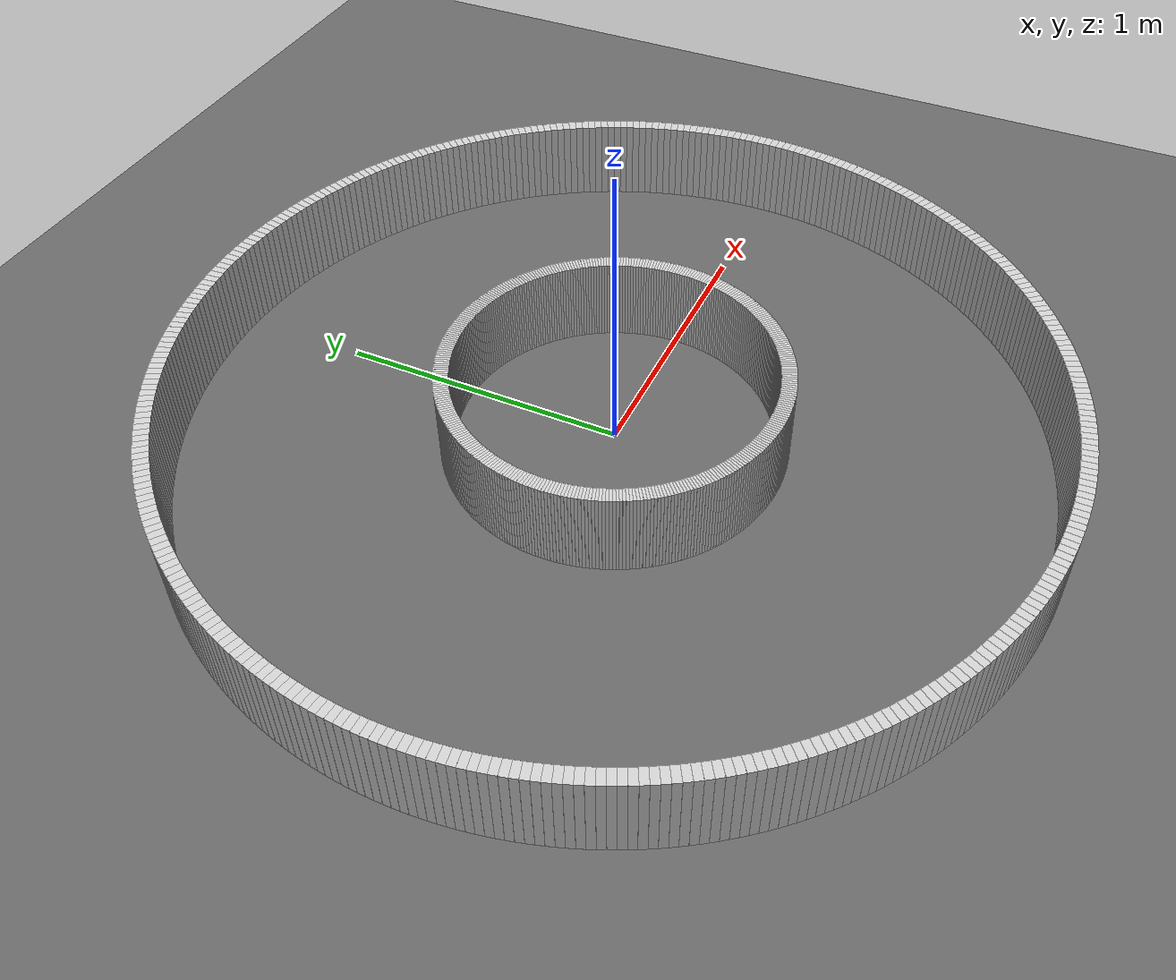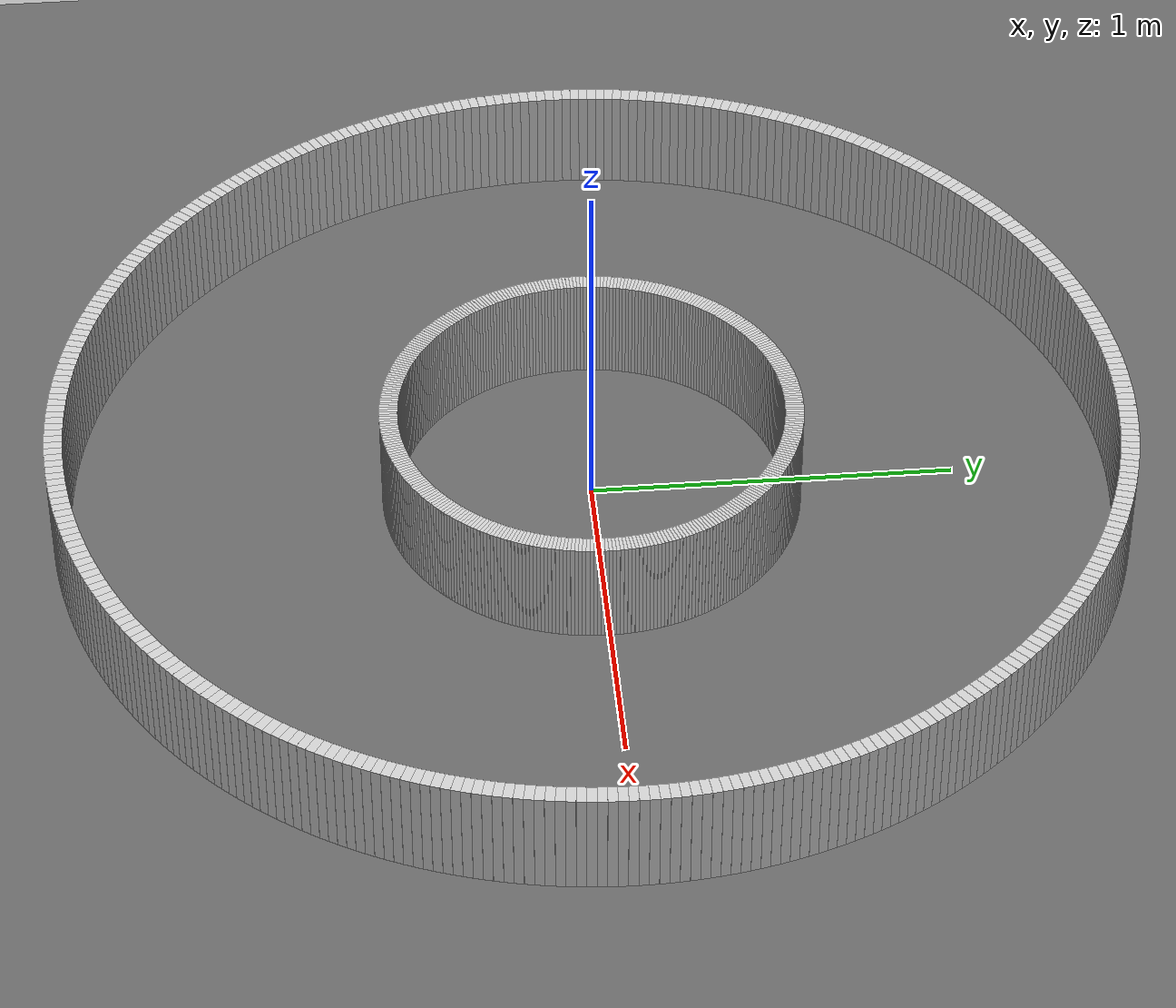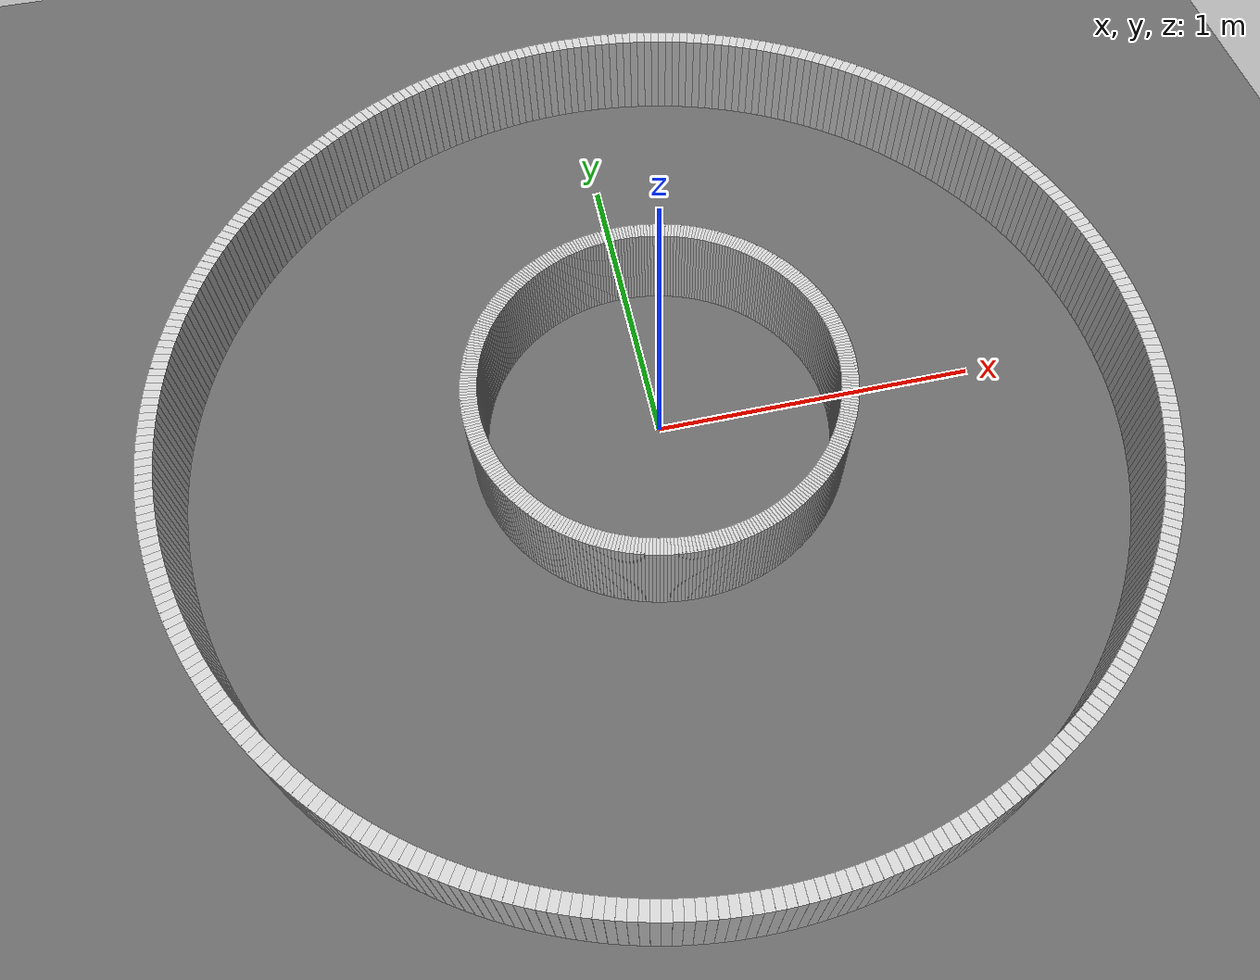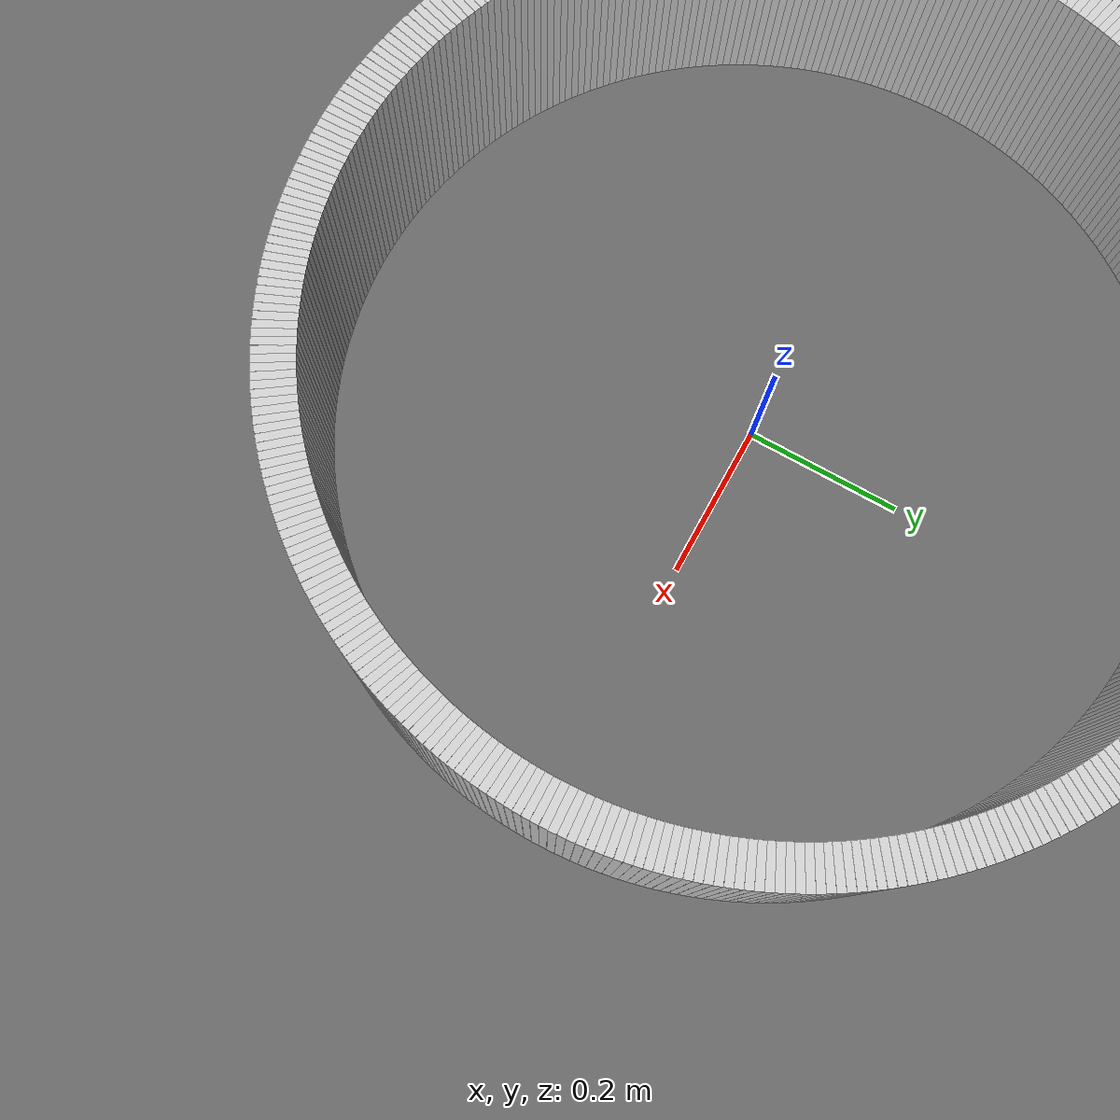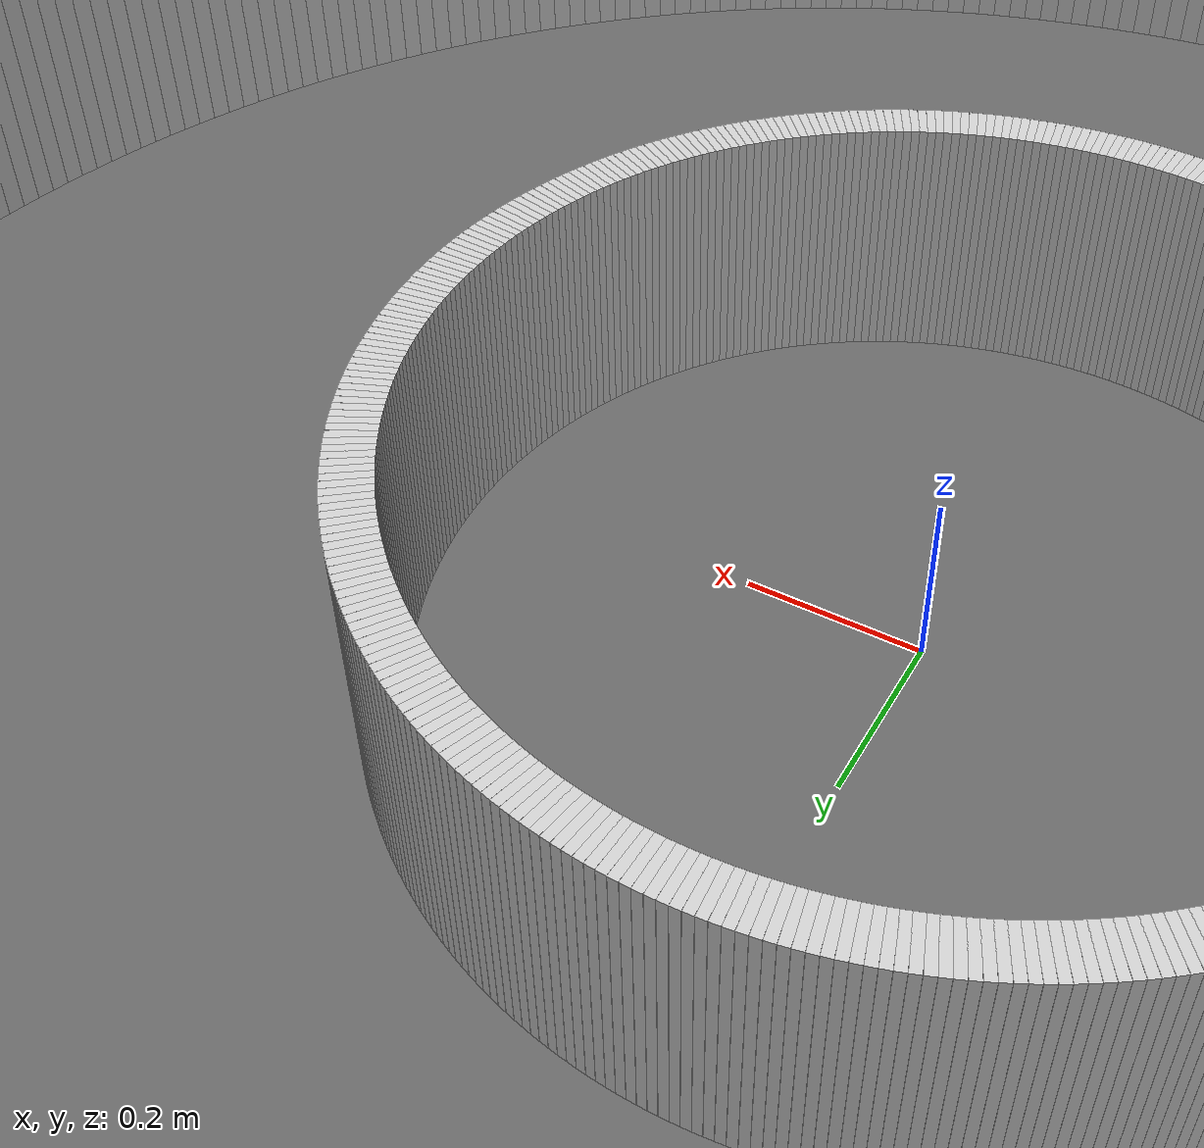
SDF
<?xml version='1.0' encoding='utf-8'?>
<sdf version="1.10">

  <world name="it_arena_track">
    <gravity>0 0 -9.81</gravity>
    <physics name="dynamics_1ms" type="ignored">
      <max_step_size>0.001</max_step_size>
      <real_time_factor>1.0</real_time_factor>
    </physics>
    <plugin filename="gz-sim-physics-system" name="gz::sim::systems::Physics" />
    <plugin filename="gz-sim-user-commands-system" name="gz::sim::systems::UserCommands" />
    <plugin filename="gz-sim-scene-broadcaster-system" name="gz::sim::systems::SceneBroadcaster" />
    <plugin filename="gz-sim-sensors-system" name="gz::sim::systems::Sensors"><render_engine>ogre2</render_engine></plugin>
    <plugin filename="gz-sim-imu-system" name="gz::sim::systems::Imu" />
    <light type="directional" name="sun">
      <pose>0 0 10 0 0 0</pose><diffuse>0.8 0.8 0.8 1</diffuse><specular>0.1 0.1 0.1 1</specular>
      <direction>-0.3 0.2 -1</direction><cast_shadows>true</cast_shadows>
    </light>
    <model name="lab_ground">
      <static>true</static>
      <link name="ground">
        <collision name="collision">
          <geometry><plane><normal>0 0 1</normal><size>120 120</size></plane></geometry>
          <surface><friction><ode><mu>1.6</mu><mu2>1.6</mu2></ode></friction></surface>
        </collision>
        <visual name="visual">
          <geometry><plane><normal>0 0 1</normal><size>120 120</size></plane></geometry>
          <material><ambient>0.3 0.3 0.3 1</ambient><diffuse>0.4 0.4 0.4 1</diffuse></material>
        </visual>
      </link>
    </model>
  <model name="lidar_lab_walls"><static>true</static><link name="walls"><collision name="inner_0_collision"><pose>0.5499999999999999 0.0 .15 0 0 1.5707963267948966</pose><geometry><box><size>0.009799554569834668 0.05 .30</size></box></geometry></collision><visual name="inner_0_visual"><pose>0.5499999999999999 0.0 .15 0 0 1.5707963267948966</pose><geometry><box><size>0.009799554569834668 0.05 .30</size></box></geometry><material><ambient>0.8 0.8 0.8 1</ambient><diffuse>0.8 0.8 0.8 1</diffuse></material></visual><collision name="inner_1_collision"><pose>0.5499162323360152 0.009598823540505931 .15 0 0 1.5882496193148399</pose><geometry><box><size>0.009799554569834668 0.05 .30</size></box></geometry></collision><visual name="inner_1_visual"><pose>0.5499162323360152 0.009598823540505931 .15 0 0 1.5882496193148399</pose><geometry><box><size>0.009799554569834668 0.05 .30</size></box></geometry><material><ambient>0.8 0.8 0.8 1</ambient><diffuse>0.8 0.8 0.8 1</diffuse></material></visual><collision name="inner_2_collision"><pose>0.5496649548605026 0.01919472318637553 .15 0 0 1.6057029118347832</pose><geometry><box><size>0.009799554569834668 0.05 .30</size></box></geometry></collision><visual name="inner_2_visual"><pose>0.5496649548605026 0.01919472318637553 .15 0 0 1.6057029118347832</pose><geometry><box><size>0.009799554569834668 0.05 .30</size></box></geometry><material><ambient>0.8 0.8 0.8 1</ambient><diffuse>0.8 0.8 0.8 1</diffuse></material></visual><collision name="inner_3_collision"><pose>0.5492462441150155 0.0287847759336191 .15 0 0 1.6231562043547265</pose><geometry><box><size>0.009799554569834668 0.05 .30</size></box></geometry></collision><visual name="inner_3_visual"><pose>0.5492462441150155 0.0287847759336191 .15 0 0 1.6231562043547265</pose><geometry><box><size>0.009799554569834668 0.05 .30</size></box></geometry><material><ambient>0.8 0.8 0.8 1</ambient><diffuse>0.8 0.8 0.8 1</diffuse></material></visual><collision name="inner_4_collision"><pose>0.5486602276429032 0.03836606055926891 .15 0 0 1.6406094968746698</pose><geometry><box><size>0.009799554569834668 0.05 .30</size></box></geometry></collision><visual name="inner_4_visual"><pose>0.5486602276429032 0.03836606055926891 .15 0 0 1.6406094968746698</pose><geometry><box><size>0.009799554569834668 0.05 .30</size></box></geometry><material><ambient>0.8 0.8 0.8 1</ambient><diffuse>0.8 0.8 0.8 1</diffuse></material></visual><collision name="inner_5_collision"><pose>0.54790708395046 0.04793565851121199 .15 0 0 1.658062789394613</pose><geometry><box><size>0.009799554569834668 0.05 .30</size></box></geometry></collision><visual name="inner_5_visual"><pose>0.54790708395046 0.04793565851121199 .15 0 0 1.658062789394613</pose><geometry><box><size>0.009799554569834668 0.05 .30</size></box></geometry><material><ambient>0.8 0.8 0.8 1</ambient><diffuse>0.8 0.8 0.8 1</diffuse></material></visual><collision name="inner_6_collision"><pose>0.5469870424525503 0.05749065479720939 .15 0 0 1.6755160819145563</pose><geometry><box><size>0.009799554569834668 0.05 .30</size></box></geometry></collision><visual name="inner_6_visual"><pose>0.5469870424525503 0.05749065479720939 .15 0 0 1.6755160819145563</pose><geometry><box><size>0.009799554569834668 0.05 .30</size></box></geometry><material><ambient>0.8 0.8 0.8 1</ambient><diffuse>0.8 0.8 0.8 1</diffuse></material></visual><collision name="inner_7_collision"><pose>0.5459003834027271 0.0670281388728311 .15 0 0 1.6929693744344996</pose><geometry><box><size>0.009799554569834668 0.05 .30</size></box></geometry></collision><visual name="inner_7_visual"><pose>0.5459003834027271 0.0670281388728311 .15 0 0 1.6929693744344996</pose><geometry><box><size>0.009799554569834668 0.05 .30</size></box></geometry><material><ambient>0.8 0.8 0.8 1</ambient><diffuse>0.8 0.8 0.8 1</diffuse></material></visual><collision name="inner_8_collision"><pose>0.5446474378078636 0.07654520552803598 .15 0 0 1.710422666954443</pose><geometry><box><size>0.009799554569834668 0.05 .30</size></box></geometry></collision><visual name="inner_8_visual"><pose>0.5446474378078636 0.07654520552803598 .15 0 0 1.710422666954443</pose><geometry><box><size>0.009799554569834668 0.05 .30</size></box></geometry><material><ambient>0.8 0.8 0.8 1</ambient><diffuse>0.8 0.8 0.8 1</diffuse></material></visual><collision name="inner_9_collision"><pose>0.5432285873273257 0.08603895577212697 .15 0 0 1.7278759594743862</pose><geometry><box><size>0.009799554569834668 0.05 .30</size></box></geometry></collision><visual name="inner_9_visual"><pose>0.5432285873273257 0.08603895577212697 .15 0 0 1.7278759594743862</pose><geometry><box><size>0.009799554569834668 0.05 .30</size></box></geometry><material><ambient>0.8 0.8 0.8 1</ambient><diffuse>0.8 0.8 0.8 1</diffuse></material></visual><collision name="inner_10_collision"><pose>0.5416442641567143 0.09550649771681168 .15 0 0 1.7453292519943295</pose><geometry><box><size>0.009799554569834668 0.05 .30</size></box></geometry></collision><visual name="inner_10_visual"><pose>0.5416442641567143 0.09550649771681168 .15 0 0 1.7453292519943295</pose><geometry><box><size>0.009799554569834668 0.05 .30</size></box></geometry><material><ambient>0.8 0.8 0.8 1</ambient><diffuse>0.8 0.8 0.8 1</diffuse></material></visual><collision name="inner_11_collision"><pose>0.5398949508962151 0.10494494745709963 .15 0 0 1.7627825445142729</pose><geometry><box><size>0.009799554569834668 0.05 .30</size></box></geometry></collision><visual name="inner_11_visual"><pose>0.5398949508962151 0.10494494745709963 .15 0 0 1.7627825445142729</pose><geometry><box><size>0.009799554569834668 0.05 .30</size></box></geometry><material><ambient>0.8 0.8 0.8 1</ambient><diffuse>0.8 0.8 0.8 1</diffuse></material></visual><collision name="inner_12_collision"><pose>0.5379811804035931 0.11435142994976762 .15 0 0 1.7802358370342162</pose><geometry><box><size>0.009799554569834668 0.05 .30</size></box></geometry></collision><visual name="inner_12_visual"><pose>0.5379811804035931 0.11435142994976762 .15 0 0 1.7802358370342162</pose><geometry><box><size>0.009799554569834668 0.05 .30</size></box></geometry><material><ambient>0.8 0.8 0.8 1</ambient><diffuse>0.8 0.8 0.8 1</diffuse></material></visual><collision name="inner_13_collision"><pose>0.5359035356318793 0.12372307988912573 .15 0 0 1.7976891295541595</pose><geometry><box><size>0.009799554569834668 0.05 .30</size></box></geometry></collision><visual name="inner_13_visual"><pose>0.5359035356318793 0.12372307988912573 .15 0 0 1.7976891295541595</pose><geometry><box><size>0.009799554569834668 0.05 .30</size></box></geometry><material><ambient>0.8 0.8 0.8 1</ambient><diffuse>0.8 0.8 0.8 1</diffuse></material></visual><collision name="inner_14_collision"><pose>0.533662649451798 0.13305704257981724 .15 0 0 1.8151424220741026</pose><geometry><box><size>0.009799554569834668 0.05 .30</size></box></geometry></collision><visual name="inner_14_visual"><pose>0.533662649451798 0.13305704257981724 .15 0 0 1.8151424220741026</pose><geometry><box><size>0.009799554569834668 0.05 .30</size></box></geometry><material><ambient>0.8 0.8 0.8 1</ambient><diffuse>0.8 0.8 0.8 1</diffuse></material></visual><collision name="inner_15_collision"><pose>0.5312592044589876 0.14235047480638638 .15 0 0 1.832595714594046</pose><geometry><box><size>0.009799554569834668 0.05 .30</size></box></geometry></collision><visual name="inner_15_visual"><pose>0.5312592044589876 0.14235047480638638 .15 0 0 1.832595714594046</pose><geometry><box><size>0.009799554569834668 0.05 .30</size></box></geometry><material><ambient>0.8 0.8 0.8 1</ambient><diffuse>0.8 0.8 0.8 1</diffuse></material></visual><collision name="inner_16_collision"><pose>0.5286939327660753 0.15160054569934953 .15 0 0 1.8500490071139892</pose><geometry><box><size>0.009799554569834668 0.05 .30</size></box></geometry></collision><visual name="inner_16_visual"><pose>0.5286939327660753 0.15160054569934953 .15 0 0 1.8500490071139892</pose><geometry><box><size>0.009799554569834668 0.05 .30</size></box></geometry><material><ambient>0.8 0.8 0.8 1</ambient><diffuse>0.8 0.8 0.8 1</diffuse></material></visual><collision name="inner_17_collision"><pose>0.5259676157796694 0.1608044375975052 .15 0 0 1.8675022996339325</pose><geometry><box><size>0.009799554569834668 0.05 .30</size></box></geometry></collision><visual name="inner_17_visual"><pose>0.5259676157796694 0.1608044375975052 .15 0 0 1.8675022996339325</pose><geometry><box><size>0.009799554569834668 0.05 .30</size></box></geometry><material><ambient>0.8 0.8 0.8 1</ambient><diffuse>0.8 0.8 0.8 1</diffuse></material></visual><collision name="inner_18_collision"><pose>0.5230810839623343 0.16995934690622105 .15 0 0 1.8849555921538759</pose><geometry><box><size>0.009799554569834668 0.05 .30</size></box></geometry></collision><visual name="inner_18_visual"><pose>0.5230810839623343 0.16995934690622105 .15 0 0 1.8849555921538759</pose><geometry><box><size>0.009799554569834668 0.05 .30</size></box></geometry><material><ambient>0.8 0.8 0.8 1</ambient><diffuse>0.8 0.8 0.8 1</diffuse></material></visual><collision name="inner_19_collision"><pose>0.5200352165796241 0.17906248495143615 .15 0 0 1.9024088846738192</pose><geometry><box><size>0.009799554569834668 0.05 .30</size></box></geometry></collision><visual name="inner_19_visual"><pose>0.5200352165796241 0.17906248495143615 .15 0 0 1.9024088846738192</pose><geometry><box><size>0.009799554569834668 0.05 .30</size></box></geometry><material><ambient>0.8 0.8 0.8 1</ambient><diffuse>0.8 0.8 0.8 1</diffuse></material></visual><collision name="inner_20_collision"><pose>0.5168309414322496 0.18811107882911776 .15 0 0 1.9198621771937625</pose><geometry><box><size>0.009799554569834668 0.05 .30</size></box></geometry></collision><visual name="inner_20_visual"><pose>0.5168309414322496 0.18811107882911776 .15 0 0 1.9198621771937625</pose><geometry><box><size>0.009799554569834668 0.05 .30</size></box></geometry><material><ambient>0.8 0.8 0.8 1</ambient><diffuse>0.8 0.8 0.8 1</diffuse></material></visual><collision name="inner_21_collision"><pose>0.5134692345734609 0.19710237224991511 .15 0 0 1.9373154697137058</pose><geometry><box><size>0.009799554569834668 0.05 .30</size></box></geometry></collision><visual name="inner_21_visual"><pose>0.5134692345734609 0.19710237224991511 .15 0 0 1.9373154697137058</pose><geometry><box><size>0.009799554569834668 0.05 .30</size></box></geometry><material><ambient>0.8 0.8 0.8 1</ambient><diffuse>0.8 0.8 0.8 1</diffuse></material></visual><collision name="inner_22_collision"><pose>0.509951120011733 0.20603362637875158 .15 0 0 1.9547687622336491</pose><geometry><box><size>0.009799554569834668 0.05 .30</size></box></geometry></collision><visual name="inner_22_visual"><pose>0.509951120011733 0.20603362637875158 .15 0 0 1.9547687622336491</pose><geometry><box><size>0.009799554569834668 0.05 .30</size></box></geometry><material><ambient>0.8 0.8 0.8 1</ambient><diffuse>0.8 0.8 0.8 1</diffuse></material></visual><collision name="inner_23_collision"><pose>0.5062776693988421 0.21490212066910053 .15 0 0 1.9722220547535922</pose><geometry><box><size>0.009799554569834668 0.05 .30</size></box></geometry></collision><visual name="inner_23_visual"><pose>0.5062776693988421 0.21490212066910053 .15 0 0 1.9722220547535922</pose><geometry><box><size>0.009799554569834668 0.05 .30</size></box></geometry><material><ambient>0.8 0.8 0.8 1</ambient><diffuse>0.8 0.8 0.8 1</diffuse></material></visual><collision name="inner_24_collision"><pose>0.5024500017034305 0.22370515369169006 .15 0 0 1.9896753472735356</pose><geometry><box><size>0.009799554569834668 0.05 .30</size></box></geometry></collision><visual name="inner_24_visual"><pose>0.5024500017034305 0.22370515369169006 .15 0 0 1.9896753472735356</pose><geometry><box><size>0.009799554569834668 0.05 .30</size></box></geometry><material><ambient>0.8 0.8 0.8 1</ambient><diffuse>0.8 0.8 0.8 1</diffuse></material></visual><collision name="inner_25_collision"><pose>0.4984692828701574 0.23244004395738466 .15 0 0 2.007128639793479</pose><geometry><box><size>0.009799554569834668 0.05 .30</size></box></geometry></collision><visual name="inner_25_visual"><pose>0.4984692828701574 0.23244004395738466 .15 0 0 2.007128639793479</pose><geometry><box><size>0.009799554569834668 0.05 .30</size></box></geometry><material><ambient>0.8 0.8 0.8 1</ambient><diffuse>0.8 0.8 0.8 1</diffuse></material></visual><collision name="inner_26_collision"><pose>0.4943367254645418 0.24110413073399253 .15 0 0 2.0245819323134224</pose><geometry><box><size>0.009799554569834668 0.05 .30</size></box></geometry></collision><visual name="inner_26_visual"><pose>0.4943367254645418 0.24110413073399253 .15 0 0 2.0245819323134224</pose><geometry><box><size>0.009799554569834668 0.05 .30</size></box></geometry><material><ambient>0.8 0.8 0.8 1</ambient><diffuse>0.8 0.8 0.8 1</diffuse></material></visual><collision name="inner_27_collision"><pose>0.4900535883036023 0.24969477485675068 .15 0 0 2.0420352248333655</pose><geometry><box><size>0.009799554569834668 0.05 .30</size></box></geometry></collision><visual name="inner_27_visual"><pose>0.4900535883036023 0.24969477485675068 .15 0 0 2.0420352248333655</pose><geometry><box><size>0.009799554569834668 0.05 .30</size></box></geometry><material><ambient>0.8 0.8 0.8 1</ambient><diffuse>0.8 0.8 0.8 1</diffuse></material></visual><collision name="inner_28_collision"><pose>0.4856211760724098 0.2582093595322399 .15 0 0 2.0594885173533086</pose><geometry><box><size>0.009799554569834668 0.05 .30</size></box></geometry></collision><visual name="inner_28_visual"><pose>0.4856211760724098 0.2582093595322399 .15 0 0 2.0594885173533086</pose><geometry><box><size>0.009799554569834668 0.05 .30</size></box></geometry><material><ambient>0.8 0.8 0.8 1</ambient><diffuse>0.8 0.8 0.8 1</diffuse></material></visual><collision name="inner_29_collision"><pose>0.4810408389266676 0.26664529113548535 .15 0 0 2.076941809873252</pose><geometry><box><size>0.009799554569834668 0.05 .30</size></box></geometry></collision><visual name="inner_29_visual"><pose>0.4810408389266676 0.26664529113548535 .15 0 0 2.076941809873252</pose><geometry><box><size>0.009799554569834668 0.05 .30</size></box></geometry><material><ambient>0.8 0.8 0.8 1</ambient><diffuse>0.8 0.8 0.8 1</diffuse></material></visual><collision name="inner_30_collision"><pose>0.4763139720814412 0.2749999999999999 .15 0 0 2.0943951023931953</pose><geometry><box><size>0.009799554569834668 0.05 .30</size></box></geometry></collision><visual name="inner_30_visual"><pose>0.4763139720814412 0.2749999999999999 .15 0 0 2.0943951023931953</pose><geometry><box><size>0.009799554569834668 0.05 .30</size></box></geometry><material><ambient>0.8 0.8 0.8 1</ambient><diffuse>0.8 0.8 0.8 1</diffuse></material></visual><collision name="inner_31_collision"><pose>0.4714420153861617 0.28327094120052976 .15 0 0 2.111848394913139</pose><geometry><box><size>0.009799554569834668 0.05 .30</size></box></geometry></collision><visual name="inner_31_visual"><pose>0.4714420153861617 0.28327094120052976 .15 0 0 2.111848394913139</pose><geometry><box><size>0.009799554569834668 0.05 .30</size></box></geometry><material><ambient>0.8 0.8 0.8 1</ambient><diffuse>0.8 0.8 0.8 1</diffuse></material></visual><collision name="inner_32_collision"><pose>0.46642645288603424 0.29145559532826265 .15 0 0 2.129301687433082</pose><geometry><box><size>0.009799554569834668 0.05 .30</size></box></geometry></collision><visual name="inner_32_visual"><pose>0.46642645288603424 0.29145559532826265 .15 0 0 2.129301687433082</pose><geometry><box><size>0.009799554569834668 0.05 .30</size></box></geometry><material><ambient>0.8 0.8 0.8 1</ambient><diffuse>0.8 0.8 0.8 1</diffuse></material></visual><collision name="inner_33_collision"><pose>0.4612688123699832 0.29955146925826487 .15 0 0 2.1467549799530254</pose><geometry><box><size>0.009799554569834668 0.05 .30</size></box></geometry></collision><visual name="inner_33_visual"><pose>0.4612688123699832 0.29955146925826487 .15 0 0 2.1467549799530254</pose><geometry><box><size>0.009799554569834668 0.05 .30</size></box></geometry><material><ambient>0.8 0.8 0.8 1</ambient><diffuse>0.8 0.8 0.8 1</diffuse></material></visual><collision name="inner_34_collision"><pose>0.4559706649052728 0.3075560969089108 .15 0 0 2.1642082724729685</pose><geometry><box><size>0.009799554569834668 0.05 .30</size></box></geometry></collision><visual name="inner_34_visual"><pose>0.4559706649052728 0.3075560969089108 .15 0 0 2.1642082724729685</pose><geometry><box><size>0.009799554569834668 0.05 .30</size></box></geometry><material><ambient>0.8 0.8 0.8 1</ambient><diffuse>0.8 0.8 0.8 1</diffuse></material></visual><collision name="inner_35_collision"><pose>0.45053362435894545 0.3154670399930753 .15 0 0 2.181661564992912</pose><geometry><box><size>0.009799554569834668 0.05 .30</size></box></geometry></collision><visual name="inner_35_visual"><pose>0.45053362435894545 0.3154670399930753 .15 0 0 2.181661564992912</pose><geometry><box><size>0.009799554569834668 0.05 .30</size></box></geometry><material><ambient>0.8 0.8 0.8 1</ambient><diffuse>0.8 0.8 0.8 1</diffuse></material></visual><collision name="inner_36_collision"><pose>0.444959346906221 0.32328188876086017 .15 0 0 2.199114857512855</pose><geometry><box><size>0.009799554569834668 0.05 .30</size></box></geometry></collision><visual name="inner_36_visual"><pose>0.444959346906221 0.32328188876086017 .15 0 0 2.199114857512855</pose><geometry><box><size>0.009799554569834668 0.05 .30</size></box></geometry><material><ambient>0.8 0.8 0.8 1</ambient><diffuse>0.8 0.8 0.8 1</diffuse></material></visual><collision name="inner_37_collision"><pose>0.439249530526011 0.3309982627336265 .15 0 0 2.2165681500327983</pose><geometry><box><size>0.009799554569834668 0.05 .30</size></box></geometry></collision><visual name="inner_37_visual"><pose>0.439249530526011 0.3309982627336265 .15 0 0 2.2165681500327983</pose><geometry><box><size>0.009799554569834668 0.05 .30</size></box></geometry><material><ambient>0.8 0.8 0.8 1</ambient><diffuse>0.8 0.8 0.8 1</diffuse></material></visual><collision name="inner_38_collision"><pose>0.43340591448369703 0.33861381142911195 .15 0 0 2.234021442552742</pose><geometry><box><size>0.009799554569834668 0.05 .30</size></box></geometry></collision><visual name="inner_38_visual"><pose>0.43340591448369703 0.33861381142911195 .15 0 0 2.234021442552742</pose><geometry><box><size>0.009799554569834668 0.05 .30</size></box></geometry><material><ambient>0.8 0.8 0.8 1</ambient><diffuse>0.8 0.8 0.8 1</diffuse></material></visual><collision name="inner_39_collision"><pose>0.42743027880133394 0.34612621507741054 .15 0 0 2.251474735072685</pose><geometry><box><size>0.009799554569834668 0.05 .30</size></box></geometry></collision><visual name="inner_39_visual"><pose>0.42743027880133394 0.34612621507741054 .15 0 0 2.251474735072685</pose><geometry><box><size>0.009799554569834668 0.05 .30</size></box></geometry><material><ambient>0.8 0.8 0.8 1</ambient><diffuse>0.8 0.8 0.8 1</diffuse></material></visual><collision name="inner_40_collision"><pose>0.42132444371543787 0.35353318532759653 .15 0 0 2.2689280275926285</pose><geometry><box><size>0.009799554569834668 0.05 .30</size></box></geometry></collision><visual name="inner_40_visual"><pose>0.42132444371543787 0.35353318532759653 .15 0 0 2.2689280275926285</pose><geometry><box><size>0.009799554569834668 0.05 .30</size></box></geometry><material><ambient>0.8 0.8 0.8 1</ambient><diffuse>0.8 0.8 0.8 1</diffuse></material></visual><collision name="inner_41_collision"><pose>0.4150902691225246 0.3608324659447789 .15 0 0 2.2863813201125716</pose><geometry><box><size>0.009799554569834668 0.05 .30</size></box></geometry></collision><visual name="inner_41_visual"><pose>0.4150902691225246 0.3608324659447789 .15 0 0 2.2863813201125716</pose><geometry><box><size>0.009799554569834668 0.05 .30</size></box></geometry><material><ambient>0.8 0.8 0.8 1</ambient><diffuse>0.8 0.8 0.8 1</diffuse></material></visual><collision name="inner_42_collision"><pose>0.4087296540125668 0.368021833497372 .15 0 0 2.303834612632515</pose><geometry><box><size>0.009799554569834668 0.05 .30</size></box></geometry></collision><visual name="inner_42_visual"><pose>0.4087296540125668 0.368021833497372 .15 0 0 2.303834612632515</pose><geometry><box><size>0.009799554569834668 0.05 .30</size></box></geometry><material><ambient>0.8 0.8 0.8 1</ambient><diffuse>0.8 0.8 0.8 1</diffuse></material></visual><collision name="inner_43_collision"><pose>0.40224453589054376 0.37509909803437413 .15 0 0 2.321287905152458</pose><geometry><box><size>0.009799554569834668 0.05 .30</size></box></geometry></collision><visual name="inner_43_visual"><pose>0.40224453589054376 0.37509909803437413 .15 0 0 2.321287905152458</pose><geometry><box><size>0.009799554569834668 0.05 .30</size></box></geometry><material><ambient>0.8 0.8 0.8 1</ambient><diffuse>0.8 0.8 0.8 1</diffuse></material></visual><collision name="inner_44_collision"><pose>0.3956368901862581 0.3820621037524484 .15 0 0 2.3387411976724017</pose><geometry><box><size>0.009799554569834668 0.05 .30</size></box></geometry></collision><visual name="inner_44_visual"><pose>0.3956368901862581 0.3820621037524484 .15 0 0 2.3387411976724017</pose><geometry><box><size>0.009799554569834668 0.05 .30</size></box></geometry><material><ambient>0.8 0.8 0.8 1</ambient><diffuse>0.8 0.8 0.8 1</diffuse></material></visual><collision name="inner_45_collision"><pose>0.3889087296526011 0.38890872965260104 .15 0 0 2.356194490192345</pose><geometry><box><size>0.009799554569834668 0.05 .30</size></box></geometry></collision><visual name="inner_45_visual"><pose>0.3889087296526011 0.38890872965260104 .15 0 0 2.356194490192345</pose><geometry><box><size>0.009799554569834668 0.05 .30</size></box></geometry><material><ambient>0.8 0.8 0.8 1</ambient><diffuse>0.8 0.8 0.8 1</diffuse></material></visual><collision name="inner_46_collision"><pose>0.3820621037524485 0.39563689018625803 .15 0 0 2.373647782712288</pose><geometry><box><size>0.009799554569834668 0.05 .30</size></box></geometry></collision><visual name="inner_46_visual"><pose>0.3820621037524485 0.39563689018625803 .15 0 0 2.373647782712288</pose><geometry><box><size>0.009799554569834668 0.05 .30</size></box></geometry><material><ambient>0.8 0.8 0.8 1</ambient><diffuse>0.8 0.8 0.8 1</diffuse></material></visual><collision name="inner_47_collision"><pose>0.37509909803437413 0.4022445358905437 .15 0 0 2.3911010752322315</pose><geometry><box><size>0.009799554569834668 0.05 .30</size></box></geometry></collision><visual name="inner_47_visual"><pose>0.37509909803437413 0.4022445358905437 .15 0 0 2.3911010752322315</pose><geometry><box><size>0.009799554569834668 0.05 .30</size></box></geometry><material><ambient>0.8 0.8 0.8 1</ambient><diffuse>0.8 0.8 0.8 1</diffuse></material></visual><collision name="inner_48_collision"><pose>0.368021833497372 0.4087296540125667 .15 0 0 2.4085543677521746</pose><geometry><box><size>0.009799554569834668 0.05 .30</size></box></geometry></collision><visual name="inner_48_visual"><pose>0.368021833497372 0.4087296540125667 .15 0 0 2.4085543677521746</pose><geometry><box><size>0.009799554569834668 0.05 .30</size></box></geometry><material><ambient>0.8 0.8 0.8 1</ambient><diffuse>0.8 0.8 0.8 1</diffuse></material></visual><collision name="inner_49_collision"><pose>0.36083246594477897 0.41509026912252456 .15 0 0 2.426007660272118</pose><geometry><box><size>0.009799554569834668 0.05 .30</size></box></geometry></collision><visual name="inner_49_visual"><pose>0.36083246594477897 0.41509026912252456 .15 0 0 2.426007660272118</pose><geometry><box><size>0.009799554569834668 0.05 .30</size></box></geometry><material><ambient>0.8 0.8 0.8 1</ambient><diffuse>0.8 0.8 0.8 1</diffuse></material></visual><collision name="inner_50_collision"><pose>0.3535331853275966 0.42132444371543787 .15 0 0 2.443460952792061</pose><geometry><box><size>0.009799554569834668 0.05 .30</size></box></geometry></collision><visual name="inner_50_visual"><pose>0.3535331853275966 0.42132444371543787 .15 0 0 2.443460952792061</pose><geometry><box><size>0.009799554569834668 0.05 .30</size></box></geometry><material><ambient>0.8 0.8 0.8 1</ambient><diffuse>0.8 0.8 0.8 1</diffuse></material></visual><collision name="inner_51_collision"><pose>0.3461262150774106 0.4274302788013339 .15 0 0 2.4609142453120043</pose><geometry><box><size>0.009799554569834668 0.05 .30</size></box></geometry></collision><visual name="inner_51_visual"><pose>0.3461262150774106 0.4274302788013339 .15 0 0 2.4609142453120043</pose><geometry><box><size>0.009799554569834668 0.05 .30</size></box></geometry><material><ambient>0.8 0.8 0.8 1</ambient><diffuse>0.8 0.8 0.8 1</diffuse></material></visual><collision name="inner_52_collision"><pose>0.338613811429112 0.43340591448369703 .15 0 0 2.478367537831948</pose><geometry><box><size>0.009799554569834668 0.05 .30</size></box></geometry></collision><visual name="inner_52_visual"><pose>0.338613811429112 0.43340591448369703 .15 0 0 2.478367537831948</pose><geometry><box><size>0.009799554569834668 0.05 .30</size></box></geometry><material><ambient>0.8 0.8 0.8 1</ambient><diffuse>0.8 0.8 0.8 1</diffuse></material></visual><collision name="inner_53_collision"><pose>0.3309982627336266 0.439249530526011 .15 0 0 2.4958208303518914</pose><geometry><box><size>0.009799554569834668 0.05 .30</size></box></geometry></collision><visual name="inner_53_visual"><pose>0.3309982627336266 0.439249530526011 .15 0 0 2.4958208303518914</pose><geometry><box><size>0.009799554569834668 0.05 .30</size></box></geometry><material><ambient>0.8 0.8 0.8 1</ambient><diffuse>0.8 0.8 0.8 1</diffuse></material></visual><collision name="inner_54_collision"><pose>0.32328188876086017 0.444959346906221 .15 0 0 2.5132741228718345</pose><geometry><box><size>0.009799554569834668 0.05 .30</size></box></geometry></collision><visual name="inner_54_visual"><pose>0.32328188876086017 0.444959346906221 .15 0 0 2.5132741228718345</pose><geometry><box><size>0.009799554569834668 0.05 .30</size></box></geometry><material><ambient>0.8 0.8 0.8 1</ambient><diffuse>0.8 0.8 0.8 1</diffuse></material></visual><collision name="inner_55_collision"><pose>0.31546703999307535 0.45053362435894545 .15 0 0 2.5307274153917776</pose><geometry><box><size>0.009799554569834668 0.05 .30</size></box></geometry></collision><visual name="inner_55_visual"><pose>0.31546703999307535 0.45053362435894545 .15 0 0 2.5307274153917776</pose><geometry><box><size>0.009799554569834668 0.05 .30</size></box></geometry><material><ambient>0.8 0.8 0.8 1</ambient><diffuse>0.8 0.8 0.8 1</diffuse></material></visual><collision name="inner_56_collision"><pose>0.3075560969089107 0.4559706649052729 .15 0 0 2.548180707911721</pose><geometry><box><size>0.009799554569834668 0.05 .30</size></box></geometry></collision><visual name="inner_56_visual"><pose>0.3075560969089107 0.4559706649052729 .15 0 0 2.548180707911721</pose><geometry><box><size>0.009799554569834668 0.05 .30</size></box></geometry><material><ambient>0.8 0.8 0.8 1</ambient><diffuse>0.8 0.8 0.8 1</diffuse></material></visual><collision name="inner_57_collision"><pose>0.2995514692582649 0.4612688123699831 .15 0 0 2.5656340004316642</pose><geometry><box><size>0.009799554569834668 0.05 .30</size></box></geometry></collision><visual name="inner_57_visual"><pose>0.2995514692582649 0.4612688123699831 .15 0 0 2.5656340004316642</pose><geometry><box><size>0.009799554569834668 0.05 .30</size></box></geometry><material><ambient>0.8 0.8 0.8 1</ambient><diffuse>0.8 0.8 0.8 1</diffuse></material></visual><collision name="inner_58_collision"><pose>0.29145559532826265 0.46642645288603424 .15 0 0 2.5830872929516078</pose><geometry><box><size>0.009799554569834668 0.05 .30</size></box></geometry></collision><visual name="inner_58_visual"><pose>0.29145559532826265 0.46642645288603424 .15 0 0 2.5830872929516078</pose><geometry><box><size>0.009799554569834668 0.05 .30</size></box></geometry><material><ambient>0.8 0.8 0.8 1</ambient><diffuse>0.8 0.8 0.8 1</diffuse></material></visual><collision name="inner_59_collision"><pose>0.28327094120052987 0.47144201538616165 .15 0 0 2.600540585471551</pose><geometry><box><size>0.009799554569834668 0.05 .30</size></box></geometry></collision><visual name="inner_59_visual"><pose>0.28327094120052987 0.47144201538616165 .15 0 0 2.600540585471551</pose><geometry><box><size>0.009799554569834668 0.05 .30</size></box></geometry><material><ambient>0.8 0.8 0.8 1</ambient><diffuse>0.8 0.8 0.8 1</diffuse></material></visual><collision name="inner_60_collision"><pose>0.275 0.47631397208144116 .15 0 0 2.617993877991494</pose><geometry><box><size>0.009799554569834668 0.05 .30</size></box></geometry></collision><visual name="inner_60_visual"><pose>0.275 0.47631397208144116 .15 0 0 2.617993877991494</pose><geometry><box><size>0.009799554569834668 0.05 .30</size></box></geometry><material><ambient>0.8 0.8 0.8 1</ambient><diffuse>0.8 0.8 0.8 1</diffuse></material></visual><collision name="inner_61_collision"><pose>0.2666452911354854 0.4810408389266676 .15 0 0 2.6354471705114375</pose><geometry><box><size>0.009799554569834668 0.05 .30</size></box></geometry></collision><visual name="inner_61_visual"><pose>0.2666452911354854 0.4810408389266676 .15 0 0 2.6354471705114375</pose><geometry><box><size>0.009799554569834668 0.05 .30</size></box></geometry><material><ambient>0.8 0.8 0.8 1</ambient><diffuse>0.8 0.8 0.8 1</diffuse></material></visual><collision name="inner_62_collision"><pose>0.25820935953223995 0.48562117607240973 .15 0 0 2.652900463031381</pose><geometry><box><size>0.009799554569834668 0.05 .30</size></box></geometry></collision><visual name="inner_62_visual"><pose>0.25820935953223995 0.48562117607240973 .15 0 0 2.652900463031381</pose><geometry><box><size>0.009799554569834668 0.05 .30</size></box></geometry><material><ambient>0.8 0.8 0.8 1</ambient><diffuse>0.8 0.8 0.8 1</diffuse></material></visual><collision name="inner_63_collision"><pose>0.2496947748567507 0.49005358830360224 .15 0 0 2.670353755551324</pose><geometry><box><size>0.009799554569834668 0.05 .30</size></box></geometry></collision><visual name="inner_63_visual"><pose>0.2496947748567507 0.49005358830360224 .15 0 0 2.670353755551324</pose><geometry><box><size>0.009799554569834668 0.05 .30</size></box></geometry><material><ambient>0.8 0.8 0.8 1</ambient><diffuse>0.8 0.8 0.8 1</diffuse></material></visual><collision name="inner_64_collision"><pose>0.24110413073399256 0.4943367254645418 .15 0 0 2.6878070480712672</pose><geometry><box><size>0.009799554569834668 0.05 .30</size></box></geometry></collision><visual name="inner_64_visual"><pose>0.24110413073399256 0.4943367254645418 .15 0 0 2.6878070480712672</pose><geometry><box><size>0.009799554569834668 0.05 .30</size></box></geometry><material><ambient>0.8 0.8 0.8 1</ambient><diffuse>0.8 0.8 0.8 1</diffuse></material></visual><collision name="inner_65_collision"><pose>0.23244004395738466 0.4984692828701574 .15 0 0 2.705260340591211</pose><geometry><box><size>0.009799554569834668 0.05 .30</size></box></geometry></collision><visual name="inner_65_visual"><pose>0.23244004395738466 0.4984692828701574 .15 0 0 2.705260340591211</pose><geometry><box><size>0.009799554569834668 0.05 .30</size></box></geometry><material><ambient>0.8 0.8 0.8 1</ambient><diffuse>0.8 0.8 0.8 1</diffuse></material></visual><collision name="inner_66_collision"><pose>0.22370515369169008 0.5024500017034305 .15 0 0 2.7227136331111543</pose><geometry><box><size>0.009799554569834668 0.05 .30</size></box></geometry></collision><visual name="inner_66_visual"><pose>0.22370515369169008 0.5024500017034305 .15 0 0 2.7227136331111543</pose><geometry><box><size>0.009799554569834668 0.05 .30</size></box></geometry><material><ambient>0.8 0.8 0.8 1</ambient><diffuse>0.8 0.8 0.8 1</diffuse></material></visual><collision name="inner_67_collision"><pose>0.21490212066910064 0.5062776693988421 .15 0 0 2.7401669256310974</pose><geometry><box><size>0.009799554569834668 0.05 .30</size></box></geometry></collision><visual name="inner_67_visual"><pose>0.21490212066910064 0.5062776693988421 .15 0 0 2.7401669256310974</pose><geometry><box><size>0.009799554569834668 0.05 .30</size></box></geometry><material><ambient>0.8 0.8 0.8 1</ambient><diffuse>0.8 0.8 0.8 1</diffuse></material></visual><collision name="inner_68_collision"><pose>0.20603362637875156 0.509951120011733 .15 0 0 2.7576202181510405</pose><geometry><box><size>0.009799554569834668 0.05 .30</size></box></geometry></collision><visual name="inner_68_visual"><pose>0.20603362637875156 0.509951120011733 .15 0 0 2.7576202181510405</pose><geometry><box><size>0.009799554569834668 0.05 .30</size></box></geometry><material><ambient>0.8 0.8 0.8 1</ambient><diffuse>0.8 0.8 0.8 1</diffuse></material></visual><collision name="inner_69_collision"><pose>0.1971023722499152 0.5134692345734609 .15 0 0 2.7750735106709836</pose><geometry><box><size>0.009799554569834668 0.05 .30</size></box></geometry></collision><visual name="inner_69_visual"><pose>0.1971023722499152 0.5134692345734609 .15 0 0 2.7750735106709836</pose><geometry><box><size>0.009799554569834668 0.05 .30</size></box></geometry><material><ambient>0.8 0.8 0.8 1</ambient><diffuse>0.8 0.8 0.8 1</diffuse></material></visual><collision name="inner_70_collision"><pose>0.18811107882911782 0.5168309414322495 .15 0 0 2.792526803190927</pose><geometry><box><size>0.009799554569834668 0.05 .30</size></box></geometry></collision><visual name="inner_70_visual"><pose>0.18811107882911782 0.5168309414322495 .15 0 0 2.792526803190927</pose><geometry><box><size>0.009799554569834668 0.05 .30</size></box></geometry><material><ambient>0.8 0.8 0.8 1</ambient><diffuse>0.8 0.8 0.8 1</diffuse></material></visual><collision name="inner_71_collision"><pose>0.1790624849514362 0.5200352165796241 .15 0 0 2.8099800957108707</pose><geometry><box><size>0.009799554569834668 0.05 .30</size></box></geometry></collision><visual name="inner_71_visual"><pose>0.1790624849514362 0.5200352165796241 .15 0 0 2.8099800957108707</pose><geometry><box><size>0.009799554569834668 0.05 .30</size></box></geometry><material><ambient>0.8 0.8 0.8 1</ambient><diffuse>0.8 0.8 0.8 1</diffuse></material></visual><collision name="inner_72_collision"><pose>0.16995934690622108 0.5230810839623343 .15 0 0 2.827433388230814</pose><geometry><box><size>0.009799554569834668 0.05 .30</size></box></geometry></collision><visual name="inner_72_visual"><pose>0.16995934690622108 0.5230810839623343 .15 0 0 2.827433388230814</pose><geometry><box><size>0.009799554569834668 0.05 .30</size></box></geometry><material><ambient>0.8 0.8 0.8 1</ambient><diffuse>0.8 0.8 0.8 1</diffuse></material></visual><collision name="inner_73_collision"><pose>0.1608044375975052 0.5259676157796694 .15 0 0 2.844886680750757</pose><geometry><box><size>0.009799554569834668 0.05 .30</size></box></geometry></collision><visual name="inner_73_visual"><pose>0.1608044375975052 0.5259676157796694 .15 0 0 2.844886680750757</pose><geometry><box><size>0.009799554569834668 0.05 .30</size></box></geometry><material><ambient>0.8 0.8 0.8 1</ambient><diffuse>0.8 0.8 0.8 1</diffuse></material></visual><collision name="inner_74_collision"><pose>0.15160054569934953 0.5286939327660753 .15 0 0 2.8623399732707004</pose><geometry><box><size>0.009799554569834668 0.05 .30</size></box></geometry></collision><visual name="inner_74_visual"><pose>0.15160054569934953 0.5286939327660753 .15 0 0 2.8623399732707004</pose><geometry><box><size>0.009799554569834668 0.05 .30</size></box></geometry><material><ambient>0.8 0.8 0.8 1</ambient><diffuse>0.8 0.8 0.8 1</diffuse></material></visual><collision name="inner_75_collision"><pose>0.14235047480638638 0.5312592044589876 .15 0 0 2.879793265790644</pose><geometry><box><size>0.009799554569834668 0.05 .30</size></box></geometry></collision><visual name="inner_75_visual"><pose>0.14235047480638638 0.5312592044589876 .15 0 0 2.879793265790644</pose><geometry><box><size>0.009799554569834668 0.05 .30</size></box></geometry><material><ambient>0.8 0.8 0.8 1</ambient><diffuse>0.8 0.8 0.8 1</diffuse></material></visual><collision name="inner_76_collision"><pose>0.13305704257981732 0.533662649451798 .15 0 0 2.897246558310587</pose><geometry><box><size>0.009799554569834668 0.05 .30</size></box></geometry></collision><visual name="inner_76_visual"><pose>0.13305704257981732 0.533662649451798 .15 0 0 2.897246558310587</pose><geometry><box><size>0.009799554569834668 0.05 .30</size></box></geometry><material><ambient>0.8 0.8 0.8 1</ambient><diffuse>0.8 0.8 0.8 1</diffuse></material></visual><collision name="inner_77_collision"><pose>0.12372307988912569 0.5359035356318793 .15 0 0 2.91469985083053</pose><geometry><box><size>0.009799554569834668 0.05 .30</size></box></geometry></collision><visual name="inner_77_visual"><pose>0.12372307988912569 0.5359035356318793 .15 0 0 2.91469985083053</pose><geometry><box><size>0.009799554569834668 0.05 .30</size></box></geometry><material><ambient>0.8 0.8 0.8 1</ambient><diffuse>0.8 0.8 0.8 1</diffuse></material></visual><collision name="inner_78_collision"><pose>0.11435142994976769 0.537981180403593 .15 0 0 2.9321531433504733</pose><geometry><box><size>0.009799554569834668 0.05 .30</size></box></geometry></collision><visual name="inner_78_visual"><pose>0.11435142994976769 0.537981180403593 .15 0 0 2.9321531433504733</pose><geometry><box><size>0.009799554569834668 0.05 .30</size></box></geometry><material><ambient>0.8 0.8 0.8 1</ambient><diffuse>0.8 0.8 0.8 1</diffuse></material></visual><collision name="inner_79_collision"><pose>0.10494494745709969 0.5398949508962151 .15 0 0 2.949606435870417</pose><geometry><box><size>0.009799554569834668 0.05 .30</size></box></geometry></collision><visual name="inner_79_visual"><pose>0.10494494745709969 0.5398949508962151 .15 0 0 2.949606435870417</pose><geometry><box><size>0.009799554569834668 0.05 .30</size></box></geometry><material><ambient>0.8 0.8 0.8 1</ambient><diffuse>0.8 0.8 0.8 1</diffuse></material></visual><collision name="inner_80_collision"><pose>0.09550649771681172 0.5416442641567143 .15 0 0 2.9670597283903604</pose><geometry><box><size>0.009799554569834668 0.05 .30</size></box></geometry></collision><visual name="inner_80_visual"><pose>0.09550649771681172 0.5416442641567143 .15 0 0 2.9670597283903604</pose><geometry><box><size>0.009799554569834668 0.05 .30</size></box></geometry><material><ambient>0.8 0.8 0.8 1</ambient><diffuse>0.8 0.8 0.8 1</diffuse></material></visual><collision name="inner_81_collision"><pose>0.086038955772127 0.5432285873273257 .15 0 0 2.9845130209103035</pose><geometry><box><size>0.009799554569834668 0.05 .30</size></box></geometry></collision><visual name="inner_81_visual"><pose>0.086038955772127 0.5432285873273257 .15 0 0 2.9845130209103035</pose><geometry><box><size>0.009799554569834668 0.05 .30</size></box></geometry><material><ambient>0.8 0.8 0.8 1</ambient><diffuse>0.8 0.8 0.8 1</diffuse></material></visual><collision name="inner_82_collision"><pose>0.07654520552803612 0.5446474378078636 .15 0 0 3.0019663134302466</pose><geometry><box><size>0.009799554569834668 0.05 .30</size></box></geometry></collision><visual name="inner_82_visual"><pose>0.07654520552803612 0.5446474378078636 .15 0 0 3.0019663134302466</pose><geometry><box><size>0.009799554569834668 0.05 .30</size></box></geometry><material><ambient>0.8 0.8 0.8 1</ambient><diffuse>0.8 0.8 0.8 1</diffuse></material></visual><collision name="inner_83_collision"><pose>0.06702813887283111 0.5459003834027271 .15 0 0 3.01941960595019</pose><geometry><box><size>0.009799554569834668 0.05 .30</size></box></geometry></collision><visual name="inner_83_visual"><pose>0.06702813887283111 0.5459003834027271 .15 0 0 3.01941960595019</pose><geometry><box><size>0.009799554569834668 0.05 .30</size></box></geometry><material><ambient>0.8 0.8 0.8 1</ambient><diffuse>0.8 0.8 0.8 1</diffuse></material></visual><collision name="inner_84_collision"><pose>0.05749065479720939 0.5469870424525503 .15 0 0 3.0368728984701336</pose><geometry><box><size>0.009799554569834668 0.05 .30</size></box></geometry></collision><visual name="inner_84_visual"><pose>0.05749065479720939 0.5469870424525503 .15 0 0 3.0368728984701336</pose><geometry><box><size>0.009799554569834668 0.05 .30</size></box></geometry><material><ambient>0.8 0.8 0.8 1</ambient><diffuse>0.8 0.8 0.8 1</diffuse></material></visual><collision name="inner_85_collision"><pose>0.04793565851121197 0.54790708395046 .15 0 0 3.0543261909900767</pose><geometry><box><size>0.009799554569834668 0.05 .30</size></box></geometry></collision><visual name="inner_85_visual"><pose>0.04793565851121197 0.54790708395046 .15 0 0 3.0543261909900767</pose><geometry><box><size>0.009799554569834668 0.05 .30</size></box></geometry><material><ambient>0.8 0.8 0.8 1</ambient><diffuse>0.8 0.8 0.8 1</diffuse></material></visual><collision name="inner_86_collision"><pose>0.03836606055926899 0.5486602276429032 .15 0 0 3.07177948351002</pose><geometry><box><size>0.009799554569834668 0.05 .30</size></box></geometry></collision><visual name="inner_86_visual"><pose>0.03836606055926899 0.5486602276429032 .15 0 0 3.07177948351002</pose><geometry><box><size>0.009799554569834668 0.05 .30</size></box></geometry><material><ambient>0.8 0.8 0.8 1</ambient><diffuse>0.8 0.8 0.8 1</diffuse></material></visual><collision name="inner_87_collision"><pose>0.028784775933619177 0.5492462441150155 .15 0 0 3.089232776029963</pose><geometry><box><size>0.009799554569834668 0.05 .30</size></box></geometry></collision><visual name="inner_87_visual"><pose>0.028784775933619177 0.5492462441150155 .15 0 0 3.089232776029963</pose><geometry><box><size>0.009799554569834668 0.05 .30</size></box></geometry><material><ambient>0.8 0.8 0.8 1</ambient><diffuse>0.8 0.8 0.8 1</diffuse></material></visual><collision name="inner_88_collision"><pose>0.019194723186375592 0.5496649548605026 .15 0 0 3.1066860685499065</pose><geometry><box><size>0.009799554569834668 0.05 .30</size></box></geometry></collision><visual name="inner_88_visual"><pose>0.019194723186375592 0.5496649548605026 .15 0 0 3.1066860685499065</pose><geometry><box><size>0.009799554569834668 0.05 .30</size></box></geometry><material><ambient>0.8 0.8 0.8 1</ambient><diffuse>0.8 0.8 0.8 1</diffuse></material></visual><collision name="inner_89_collision"><pose>0.009598823540505856 0.5499162323360152 .15 0 0 3.12413936106985</pose><geometry><box><size>0.009799554569834668 0.05 .30</size></box></geometry></collision><visual name="inner_89_visual"><pose>0.009598823540505856 0.5499162323360152 .15 0 0 3.12413936106985</pose><geometry><box><size>0.009799554569834668 0.05 .30</size></box></geometry><material><ambient>0.8 0.8 0.8 1</ambient><diffuse>0.8 0.8 0.8 1</diffuse></material></visual><collision name="inner_90_collision"><pose>3.3677786976552206e-17 0.5499999999999999 .15 0 0 3.141592653589793</pose><geometry><box><size>0.009799554569834668 0.05 .30</size></box></geometry></collision><visual name="inner_90_visual"><pose>3.3677786976552206e-17 0.5499999999999999 .15 0 0 3.141592653589793</pose><geometry><box><size>0.009799554569834668 0.05 .30</size></box></geometry><material><ambient>0.8 0.8 0.8 1</ambient><diffuse>0.8 0.8 0.8 1</diffuse></material></visual><collision name="inner_91_collision"><pose>-0.009598823540505912 0.5499162323360152 .15 0 0 3.159045946109736</pose><geometry><box><size>0.009799554569834668 0.05 .30</size></box></geometry></collision><visual name="inner_91_visual"><pose>-0.009598823540505912 0.5499162323360152 .15 0 0 3.159045946109736</pose><geometry><box><size>0.009799554569834668 0.05 .30</size></box></geometry><material><ambient>0.8 0.8 0.8 1</ambient><diffuse>0.8 0.8 0.8 1</diffuse></material></visual><collision name="inner_92_collision"><pose>-0.0191947231863754 0.5496649548605026 .15 0 0 3.1764992386296793</pose><geometry><box><size>0.009799554569834668 0.05 .30</size></box></geometry></collision><visual name="inner_92_visual"><pose>-0.0191947231863754 0.5496649548605026 .15 0 0 3.1764992386296793</pose><geometry><box><size>0.009799554569834668 0.05 .30</size></box></geometry><material><ambient>0.8 0.8 0.8 1</ambient><diffuse>0.8 0.8 0.8 1</diffuse></material></visual><collision name="inner_93_collision"><pose>-0.028784775933618986 0.5492462441150155 .15 0 0 3.193952531149623</pose><geometry><box><size>0.009799554569834668 0.05 .30</size></box></geometry></collision><visual name="inner_93_visual"><pose>-0.028784775933618986 0.5492462441150155 .15 0 0 3.193952531149623</pose><geometry><box><size>0.009799554569834668 0.05 .30</size></box></geometry><material><ambient>0.8 0.8 0.8 1</ambient><diffuse>0.8 0.8 0.8 1</diffuse></material></visual><collision name="inner_94_collision"><pose>-0.03836606055926893 0.5486602276429032 .15 0 0 3.2114058236695664</pose><geometry><box><size>0.009799554569834668 0.05 .30</size></box></geometry></collision><visual name="inner_94_visual"><pose>-0.03836606055926893 0.5486602276429032 .15 0 0 3.2114058236695664</pose><geometry><box><size>0.009799554569834668 0.05 .30</size></box></geometry><material><ambient>0.8 0.8 0.8 1</ambient><diffuse>0.8 0.8 0.8 1</diffuse></material></visual><collision name="inner_95_collision"><pose>-0.04793565851121202 0.54790708395046 .15 0 0 3.2288591161895095</pose><geometry><box><size>0.009799554569834668 0.05 .30</size></box></geometry></collision><visual name="inner_95_visual"><pose>-0.04793565851121202 0.54790708395046 .15 0 0 3.2288591161895095</pose><geometry><box><size>0.009799554569834668 0.05 .30</size></box></geometry><material><ambient>0.8 0.8 0.8 1</ambient><diffuse>0.8 0.8 0.8 1</diffuse></material></visual><collision name="inner_96_collision"><pose>-0.05749065479720933 0.5469870424525503 .15 0 0 3.2463124087094526</pose><geometry><box><size>0.009799554569834668 0.05 .30</size></box></geometry></collision><visual name="inner_96_visual"><pose>-0.05749065479720933 0.5469870424525503 .15 0 0 3.2463124087094526</pose><geometry><box><size>0.009799554569834668 0.05 .30</size></box></geometry><material><ambient>0.8 0.8 0.8 1</ambient><diffuse>0.8 0.8 0.8 1</diffuse></material></visual><collision name="inner_97_collision"><pose>-0.06702813887283104 0.5459003834027271 .15 0 0 3.263765701229396</pose><geometry><box><size>0.009799554569834668 0.05 .30</size></box></geometry></collision><visual name="inner_97_visual"><pose>-0.06702813887283104 0.5459003834027271 .15 0 0 3.263765701229396</pose><geometry><box><size>0.009799554569834668 0.05 .30</size></box></geometry><material><ambient>0.8 0.8 0.8 1</ambient><diffuse>0.8 0.8 0.8 1</diffuse></material></visual><collision name="inner_98_collision"><pose>-0.07654520552803594 0.5446474378078636 .15 0 0 3.2812189937493397</pose><geometry><box><size>0.009799554569834668 0.05 .30</size></box></geometry></collision><visual name="inner_98_visual"><pose>-0.07654520552803594 0.5446474378078636 .15 0 0 3.2812189937493397</pose><geometry><box><size>0.009799554569834668 0.05 .30</size></box></geometry><material><ambient>0.8 0.8 0.8 1</ambient><diffuse>0.8 0.8 0.8 1</diffuse></material></visual><collision name="inner_99_collision"><pose>-0.08603895577212706 0.5432285873273256 .15 0 0 3.2986722862692828</pose><geometry><box><size>0.009799554569834668 0.05 .30</size></box></geometry></collision><visual name="inner_99_visual"><pose>-0.08603895577212706 0.5432285873273256 .15 0 0 3.2986722862692828</pose><geometry><box><size>0.009799554569834668 0.05 .30</size></box></geometry><material><ambient>0.8 0.8 0.8 1</ambient><diffuse>0.8 0.8 0.8 1</diffuse></material></visual><collision name="inner_100_collision"><pose>-0.09550649771681166 0.5416442641567143 .15 0 0 3.316125578789226</pose><geometry><box><size>0.009799554569834668 0.05 .30</size></box></geometry></collision><visual name="inner_100_visual"><pose>-0.09550649771681166 0.5416442641567143 .15 0 0 3.316125578789226</pose><geometry><box><size>0.009799554569834668 0.05 .30</size></box></geometry><material><ambient>0.8 0.8 0.8 1</ambient><diffuse>0.8 0.8 0.8 1</diffuse></material></visual><collision name="inner_101_collision"><pose>-0.10494494745709963 0.5398949508962151 .15 0 0 3.3335788713091694</pose><geometry><box><size>0.009799554569834668 0.05 .30</size></box></geometry></collision><visual name="inner_101_visual"><pose>-0.10494494745709963 0.5398949508962151 .15 0 0 3.3335788713091694</pose><geometry><box><size>0.009799554569834668 0.05 .30</size></box></geometry><material><ambient>0.8 0.8 0.8 1</ambient><diffuse>0.8 0.8 0.8 1</diffuse></material></visual><collision name="inner_102_collision"><pose>-0.1143514299497675 0.5379811804035931 .15 0 0 3.3510321638291125</pose><geometry><box><size>0.009799554569834668 0.05 .30</size></box></geometry></collision><visual name="inner_102_visual"><pose>-0.1143514299497675 0.5379811804035931 .15 0 0 3.3510321638291125</pose><geometry><box><size>0.009799554569834668 0.05 .30</size></box></geometry><material><ambient>0.8 0.8 0.8 1</ambient><diffuse>0.8 0.8 0.8 1</diffuse></material></visual><collision name="inner_103_collision"><pose>-0.12372307988912563 0.5359035356318793 .15 0 0 3.368485456349056</pose><geometry><box><size>0.009799554569834668 0.05 .30</size></box></geometry></collision><visual name="inner_103_visual"><pose>-0.12372307988912563 0.5359035356318793 .15 0 0 3.368485456349056</pose><geometry><box><size>0.009799554569834668 0.05 .30</size></box></geometry><material><ambient>0.8 0.8 0.8 1</ambient><diffuse>0.8 0.8 0.8 1</diffuse></material></visual><collision name="inner_104_collision"><pose>-0.13305704257981726 0.533662649451798 .15 0 0 3.385938748868999</pose><geometry><box><size>0.009799554569834668 0.05 .30</size></box></geometry></collision><visual name="inner_104_visual"><pose>-0.13305704257981726 0.533662649451798 .15 0 0 3.385938748868999</pose><geometry><box><size>0.009799554569834668 0.05 .30</size></box></geometry><material><ambient>0.8 0.8 0.8 1</ambient><diffuse>0.8 0.8 0.8 1</diffuse></material></visual><collision name="inner_105_collision"><pose>-0.14235047480638646 0.5312592044589876 .15 0 0 3.4033920413889427</pose><geometry><box><size>0.009799554569834668 0.05 .30</size></box></geometry></collision><visual name="inner_105_visual"><pose>-0.14235047480638646 0.5312592044589876 .15 0 0 3.4033920413889427</pose><geometry><box><size>0.009799554569834668 0.05 .30</size></box></geometry><material><ambient>0.8 0.8 0.8 1</ambient><diffuse>0.8 0.8 0.8 1</diffuse></material></visual><collision name="inner_106_collision"><pose>-0.15160054569934947 0.5286939327660753 .15 0 0 3.420845333908886</pose><geometry><box><size>0.009799554569834668 0.05 .30</size></box></geometry></collision><visual name="inner_106_visual"><pose>-0.15160054569934947 0.5286939327660753 .15 0 0 3.420845333908886</pose><geometry><box><size>0.009799554569834668 0.05 .30</size></box></geometry><material><ambient>0.8 0.8 0.8 1</ambient><diffuse>0.8 0.8 0.8 1</diffuse></material></visual><collision name="inner_107_collision"><pose>-0.16080443759750515 0.5259676157796694 .15 0 0 3.4382986264288293</pose><geometry><box><size>0.009799554569834668 0.05 .30</size></box></geometry></collision><visual name="inner_107_visual"><pose>-0.16080443759750515 0.5259676157796694 .15 0 0 3.4382986264288293</pose><geometry><box><size>0.009799554569834668 0.05 .30</size></box></geometry><material><ambient>0.8 0.8 0.8 1</ambient><diffuse>0.8 0.8 0.8 1</diffuse></material></visual><collision name="inner_108_collision"><pose>-0.16995934690622103 0.5230810839623344 .15 0 0 3.4557519189487724</pose><geometry><box><size>0.009799554569834668 0.05 .30</size></box></geometry></collision><visual name="inner_108_visual"><pose>-0.16995934690622103 0.5230810839623344 .15 0 0 3.4557519189487724</pose><geometry><box><size>0.009799554569834668 0.05 .30</size></box></geometry><material><ambient>0.8 0.8 0.8 1</ambient><diffuse>0.8 0.8 0.8 1</diffuse></material></visual><collision name="inner_109_collision"><pose>-0.179062484951436 0.5200352165796241 .15 0 0 3.4732052114687155</pose><geometry><box><size>0.009799554569834668 0.05 .30</size></box></geometry></collision><visual name="inner_109_visual"><pose>-0.179062484951436 0.5200352165796241 .15 0 0 3.4732052114687155</pose><geometry><box><size>0.009799554569834668 0.05 .30</size></box></geometry><material><ambient>0.8 0.8 0.8 1</ambient><diffuse>0.8 0.8 0.8 1</diffuse></material></visual><collision name="inner_110_collision"><pose>-0.18811107882911776 0.5168309414322496 .15 0 0 3.490658503988659</pose><geometry><box><size>0.009799554569834668 0.05 .30</size></box></geometry></collision><visual name="inner_110_visual"><pose>-0.18811107882911776 0.5168309414322496 .15 0 0 3.490658503988659</pose><geometry><box><size>0.009799554569834668 0.05 .30</size></box></geometry><material><ambient>0.8 0.8 0.8 1</ambient><diffuse>0.8 0.8 0.8 1</diffuse></material></visual><collision name="inner_111_collision"><pose>-0.19710237224991511 0.5134692345734609 .15 0 0 3.5081117965086026</pose><geometry><box><size>0.009799554569834668 0.05 .30</size></box></geometry></collision><visual name="inner_111_visual"><pose>-0.19710237224991511 0.5134692345734609 .15 0 0 3.5081117965086026</pose><geometry><box><size>0.009799554569834668 0.05 .30</size></box></geometry><material><ambient>0.8 0.8 0.8 1</ambient><diffuse>0.8 0.8 0.8 1</diffuse></material></visual><collision name="inner_112_collision"><pose>-0.2060336263787516 0.509951120011733 .15 0 0 3.5255650890285457</pose><geometry><box><size>0.009799554569834668 0.05 .30</size></box></geometry></collision><visual name="inner_112_visual"><pose>-0.2060336263787516 0.509951120011733 .15 0 0 3.5255650890285457</pose><geometry><box><size>0.009799554569834668 0.05 .30</size></box></geometry><material><ambient>0.8 0.8 0.8 1</ambient><diffuse>0.8 0.8 0.8 1</diffuse></material></visual><collision name="inner_113_collision"><pose>-0.21490212066910044 0.5062776693988421 .15 0 0 3.543018381548489</pose><geometry><box><size>0.009799554569834668 0.05 .30</size></box></geometry></collision><visual name="inner_113_visual"><pose>-0.21490212066910044 0.5062776693988421 .15 0 0 3.543018381548489</pose><geometry><box><size>0.009799554569834668 0.05 .30</size></box></geometry><material><ambient>0.8 0.8 0.8 1</ambient><diffuse>0.8 0.8 0.8 1</diffuse></material></visual><collision name="inner_114_collision"><pose>-0.22370515369169 0.5024500017034305 .15 0 0 3.560471674068432</pose><geometry><box><size>0.009799554569834668 0.05 .30</size></box></geometry></collision><visual name="inner_114_visual"><pose>-0.22370515369169 0.5024500017034305 .15 0 0 3.560471674068432</pose><geometry><box><size>0.009799554569834668 0.05 .30</size></box></geometry><material><ambient>0.8 0.8 0.8 1</ambient><diffuse>0.8 0.8 0.8 1</diffuse></material></visual><collision name="inner_115_collision"><pose>-0.2324400439573846 0.49846928287015746 .15 0 0 3.5779249665883754</pose><geometry><box><size>0.009799554569834668 0.05 .30</size></box></geometry></collision><visual name="inner_115_visual"><pose>-0.2324400439573846 0.49846928287015746 .15 0 0 3.5779249665883754</pose><geometry><box><size>0.009799554569834668 0.05 .30</size></box></geometry><material><ambient>0.8 0.8 0.8 1</ambient><diffuse>0.8 0.8 0.8 1</diffuse></material></visual><collision name="inner_116_collision"><pose>-0.24110413073399262 0.49433672546454177 .15 0 0 3.595378259108319</pose><geometry><box><size>0.009799554569834668 0.05 .30</size></box></geometry></collision><visual name="inner_116_visual"><pose>-0.24110413073399262 0.49433672546454177 .15 0 0 3.595378259108319</pose><geometry><box><size>0.009799554569834668 0.05 .30</size></box></geometry><material><ambient>0.8 0.8 0.8 1</ambient><diffuse>0.8 0.8 0.8 1</diffuse></material></visual><collision name="inner_117_collision"><pose>-0.24969477485675065 0.4900535883036023 .15 0 0 3.612831551628262</pose><geometry><box><size>0.009799554569834668 0.05 .30</size></box></geometry></collision><visual name="inner_117_visual"><pose>-0.24969477485675065 0.4900535883036023 .15 0 0 3.612831551628262</pose><geometry><box><size>0.009799554569834668 0.05 .30</size></box></geometry><material><ambient>0.8 0.8 0.8 1</ambient><diffuse>0.8 0.8 0.8 1</diffuse></material></visual><collision name="inner_118_collision"><pose>-0.2582093595322398 0.48562117607240984 .15 0 0 3.630284844148205</pose><geometry><box><size>0.009799554569834668 0.05 .30</size></box></geometry></collision><visual name="inner_118_visual"><pose>-0.2582093595322398 0.48562117607240984 .15 0 0 3.630284844148205</pose><geometry><box><size>0.009799554569834668 0.05 .30</size></box></geometry><material><ambient>0.8 0.8 0.8 1</ambient><diffuse>0.8 0.8 0.8 1</diffuse></material></visual><collision name="inner_119_collision"><pose>-0.2666452911354853 0.48104083892666766 .15 0 0 3.6477381366681487</pose><geometry><box><size>0.009799554569834668 0.05 .30</size></box></geometry></collision><visual name="inner_119_visual"><pose>-0.2666452911354853 0.48104083892666766 .15 0 0 3.6477381366681487</pose><geometry><box><size>0.009799554569834668 0.05 .30</size></box></geometry><material><ambient>0.8 0.8 0.8 1</ambient><diffuse>0.8 0.8 0.8 1</diffuse></material></visual><collision name="inner_120_collision"><pose>-0.27499999999999986 0.4763139720814412 .15 0 0 3.665191429188092</pose><geometry><box><size>0.009799554569834668 0.05 .30</size></box></geometry></collision><visual name="inner_120_visual"><pose>-0.27499999999999986 0.4763139720814412 .15 0 0 3.665191429188092</pose><geometry><box><size>0.009799554569834668 0.05 .30</size></box></geometry><material><ambient>0.8 0.8 0.8 1</ambient><diffuse>0.8 0.8 0.8 1</diffuse></material></visual><collision name="inner_121_collision"><pose>-0.2832709412005298 0.4714420153861617 .15 0 0 3.6826447217080354</pose><geometry><box><size>0.009799554569834668 0.05 .30</size></box></geometry></collision><visual name="inner_121_visual"><pose>-0.2832709412005298 0.4714420153861617 .15 0 0 3.6826447217080354</pose><geometry><box><size>0.009799554569834668 0.05 .30</size></box></geometry><material><ambient>0.8 0.8 0.8 1</ambient><diffuse>0.8 0.8 0.8 1</diffuse></material></visual><collision name="inner_122_collision"><pose>-0.2914555953282626 0.4664264528860343 .15 0 0 3.7000980142279785</pose><geometry><box><size>0.009799554569834668 0.05 .30</size></box></geometry></collision><visual name="inner_122_visual"><pose>-0.2914555953282626 0.4664264528860343 .15 0 0 3.7000980142279785</pose><geometry><box><size>0.009799554569834668 0.05 .30</size></box></geometry><material><ambient>0.8 0.8 0.8 1</ambient><diffuse>0.8 0.8 0.8 1</diffuse></material></visual><collision name="inner_123_collision"><pose>-0.29955146925826487 0.4612688123699831 .15 0 0 3.717551306747922</pose><geometry><box><size>0.009799554569834668 0.05 .30</size></box></geometry></collision><visual name="inner_123_visual"><pose>-0.29955146925826487 0.4612688123699831 .15 0 0 3.717551306747922</pose><geometry><box><size>0.009799554569834668 0.05 .30</size></box></geometry><material><ambient>0.8 0.8 0.8 1</ambient><diffuse>0.8 0.8 0.8 1</diffuse></material></visual><collision name="inner_124_collision"><pose>-0.3075560969089106 0.4559706649052729 .15 0 0 3.735004599267865</pose><geometry><box><size>0.009799554569834668 0.05 .30</size></box></geometry></collision><visual name="inner_124_visual"><pose>-0.3075560969089106 0.4559706649052729 .15 0 0 3.735004599267865</pose><geometry><box><size>0.009799554569834668 0.05 .30</size></box></geometry><material><ambient>0.8 0.8 0.8 1</ambient><diffuse>0.8 0.8 0.8 1</diffuse></material></visual><collision name="inner_125_collision"><pose>-0.3154670399930752 0.45053362435894556 .15 0 0 3.752457891787808</pose><geometry><box><size>0.009799554569834668 0.05 .30</size></box></geometry></collision><visual name="inner_125_visual"><pose>-0.3154670399930752 0.45053362435894556 .15 0 0 3.752457891787808</pose><geometry><box><size>0.009799554569834668 0.05 .30</size></box></geometry><material><ambient>0.8 0.8 0.8 1</ambient><diffuse>0.8 0.8 0.8 1</diffuse></material></visual><collision name="inner_126_collision"><pose>-0.3232818887608601 0.444959346906221 .15 0 0 3.7699111843077517</pose><geometry><box><size>0.009799554569834668 0.05 .30</size></box></geometry></collision><visual name="inner_126_visual"><pose>-0.3232818887608601 0.444959346906221 .15 0 0 3.7699111843077517</pose><geometry><box><size>0.009799554569834668 0.05 .30</size></box></geometry><material><ambient>0.8 0.8 0.8 1</ambient><diffuse>0.8 0.8 0.8 1</diffuse></material></visual><collision name="inner_127_collision"><pose>-0.3309982627336266 0.43924953052601096 .15 0 0 3.7873644768276953</pose><geometry><box><size>0.009799554569834668 0.05 .30</size></box></geometry></collision><visual name="inner_127_visual"><pose>-0.3309982627336266 0.43924953052601096 .15 0 0 3.7873644768276953</pose><geometry><box><size>0.009799554569834668 0.05 .30</size></box></geometry><material><ambient>0.8 0.8 0.8 1</ambient><diffuse>0.8 0.8 0.8 1</diffuse></material></visual><collision name="inner_128_collision"><pose>-0.338613811429112 0.43340591448369703 .15 0 0 3.8048177693476384</pose><geometry><box><size>0.009799554569834668 0.05 .30</size></box></geometry></collision><visual name="inner_128_visual"><pose>-0.338613811429112 0.43340591448369703 .15 0 0 3.8048177693476384</pose><geometry><box><size>0.009799554569834668 0.05 .30</size></box></geometry><material><ambient>0.8 0.8 0.8 1</ambient><diffuse>0.8 0.8 0.8 1</diffuse></material></visual><collision name="inner_129_collision"><pose>-0.3461262150774105 0.427430278801334 .15 0 0 3.8222710618675815</pose><geometry><box><size>0.009799554569834668 0.05 .30</size></box></geometry></collision><visual name="inner_129_visual"><pose>-0.3461262150774105 0.427430278801334 .15 0 0 3.8222710618675815</pose><geometry><box><size>0.009799554569834668 0.05 .30</size></box></geometry><material><ambient>0.8 0.8 0.8 1</ambient><diffuse>0.8 0.8 0.8 1</diffuse></material></visual><collision name="inner_130_collision"><pose>-0.3535331853275966 0.42132444371543787 .15 0 0 3.839724354387525</pose><geometry><box><size>0.009799554569834668 0.05 .30</size></box></geometry></collision><visual name="inner_130_visual"><pose>-0.3535331853275966 0.42132444371543787 .15 0 0 3.839724354387525</pose><geometry><box><size>0.009799554569834668 0.05 .30</size></box></geometry><material><ambient>0.8 0.8 0.8 1</ambient><diffuse>0.8 0.8 0.8 1</diffuse></material></visual><collision name="inner_131_collision"><pose>-0.3608324659447791 0.41509026912252445 .15 0 0 3.8571776469074686</pose><geometry><box><size>0.009799554569834668 0.05 .30</size></box></geometry></collision><visual name="inner_131_visual"><pose>-0.3608324659447791 0.41509026912252445 .15 0 0 3.8571776469074686</pose><geometry><box><size>0.009799554569834668 0.05 .30</size></box></geometry><material><ambient>0.8 0.8 0.8 1</ambient><diffuse>0.8 0.8 0.8 1</diffuse></material></visual><collision name="inner_132_collision"><pose>-0.368021833497372 0.4087296540125668 .15 0 0 3.8746309394274117</pose><geometry><box><size>0.009799554569834668 0.05 .30</size></box></geometry></collision><visual name="inner_132_visual"><pose>-0.368021833497372 0.4087296540125668 .15 0 0 3.8746309394274117</pose><geometry><box><size>0.009799554569834668 0.05 .30</size></box></geometry><material><ambient>0.8 0.8 0.8 1</ambient><diffuse>0.8 0.8 0.8 1</diffuse></material></visual><collision name="inner_133_collision"><pose>-0.3750990980343741 0.40224453589054376 .15 0 0 3.8920842319473548</pose><geometry><box><size>0.009799554569834668 0.05 .30</size></box></geometry></collision><visual name="inner_133_visual"><pose>-0.3750990980343741 0.40224453589054376 .15 0 0 3.8920842319473548</pose><geometry><box><size>0.009799554569834668 0.05 .30</size></box></geometry><material><ambient>0.8 0.8 0.8 1</ambient><diffuse>0.8 0.8 0.8 1</diffuse></material></visual><collision name="inner_134_collision"><pose>-0.3820621037524483 0.39563689018625825 .15 0 0 3.909537524467298</pose><geometry><box><size>0.009799554569834668 0.05 .30</size></box></geometry></collision><visual name="inner_134_visual"><pose>-0.3820621037524483 0.39563689018625825 .15 0 0 3.909537524467298</pose><geometry><box><size>0.009799554569834668 0.05 .30</size></box></geometry><material><ambient>0.8 0.8 0.8 1</ambient><diffuse>0.8 0.8 0.8 1</diffuse></material></visual><collision name="inner_135_collision"><pose>-0.38890872965260104 0.3889087296526011 .15 0 0 3.9269908169872414</pose><geometry><box><size>0.009799554569834668 0.05 .30</size></box></geometry></collision><visual name="inner_135_visual"><pose>-0.38890872965260104 0.3889087296526011 .15 0 0 3.9269908169872414</pose><geometry><box><size>0.009799554569834668 0.05 .30</size></box></geometry><material><ambient>0.8 0.8 0.8 1</ambient><diffuse>0.8 0.8 0.8 1</diffuse></material></visual><collision name="inner_136_collision"><pose>-0.3956368901862581 0.38206210375244837 .15 0 0 3.944444109507185</pose><geometry><box><size>0.009799554569834668 0.05 .30</size></box></geometry></collision><visual name="inner_136_visual"><pose>-0.3956368901862581 0.38206210375244837 .15 0 0 3.944444109507185</pose><geometry><box><size>0.009799554569834668 0.05 .30</size></box></geometry><material><ambient>0.8 0.8 0.8 1</ambient><diffuse>0.8 0.8 0.8 1</diffuse></material></visual><collision name="inner_137_collision"><pose>-0.4022445358905437 0.3750990980343742 .15 0 0 3.961897402027128</pose><geometry><box><size>0.009799554569834668 0.05 .30</size></box></geometry></collision><visual name="inner_137_visual"><pose>-0.4022445358905437 0.3750990980343742 .15 0 0 3.961897402027128</pose><geometry><box><size>0.009799554569834668 0.05 .30</size></box></geometry><material><ambient>0.8 0.8 0.8 1</ambient><diffuse>0.8 0.8 0.8 1</diffuse></material></visual><collision name="inner_138_collision"><pose>-0.40872965401256667 0.36802183349737205 .15 0 0 3.979350694547071</pose><geometry><box><size>0.009799554569834668 0.05 .30</size></box></geometry></collision><visual name="inner_138_visual"><pose>-0.40872965401256667 0.36802183349737205 .15 0 0 3.979350694547071</pose><geometry><box><size>0.009799554569834668 0.05 .30</size></box></geometry><material><ambient>0.8 0.8 0.8 1</ambient><diffuse>0.8 0.8 0.8 1</diffuse></material></visual><collision name="inner_139_collision"><pose>-0.41509026912252456 0.36083246594477897 .15 0 0 3.9968039870670147</pose><geometry><box><size>0.009799554569834668 0.05 .30</size></box></geometry></collision><visual name="inner_139_visual"><pose>-0.41509026912252456 0.36083246594477897 .15 0 0 3.9968039870670147</pose><geometry><box><size>0.009799554569834668 0.05 .30</size></box></geometry><material><ambient>0.8 0.8 0.8 1</ambient><diffuse>0.8 0.8 0.8 1</diffuse></material></visual><collision name="inner_140_collision"><pose>-0.4213244437154378 0.35353318532759664 .15 0 0 4.014257279586958</pose><geometry><box><size>0.009799554569834668 0.05 .30</size></box></geometry></collision><visual name="inner_140_visual"><pose>-0.4213244437154378 0.35353318532759664 .15 0 0 4.014257279586958</pose><geometry><box><size>0.009799554569834668 0.05 .30</size></box></geometry><material><ambient>0.8 0.8 0.8 1</ambient><diffuse>0.8 0.8 0.8 1</diffuse></material></visual><collision name="inner_141_collision"><pose>-0.42743027880133383 0.3461262150774107 .15 0 0 4.031710572106901</pose><geometry><box><size>0.009799554569834668 0.05 .30</size></box></geometry></collision><visual name="inner_141_visual"><pose>-0.42743027880133383 0.3461262150774107 .15 0 0 4.031710572106901</pose><geometry><box><size>0.009799554569834668 0.05 .30</size></box></geometry><material><ambient>0.8 0.8 0.8 1</ambient><diffuse>0.8 0.8 0.8 1</diffuse></material></visual><collision name="inner_142_collision"><pose>-0.433405914483697 0.33861381142911207 .15 0 0 4.049163864626845</pose><geometry><box><size>0.009799554569834668 0.05 .30</size></box></geometry></collision><visual name="inner_142_visual"><pose>-0.433405914483697 0.33861381142911207 .15 0 0 4.049163864626845</pose><geometry><box><size>0.009799554569834668 0.05 .30</size></box></geometry><material><ambient>0.8 0.8 0.8 1</ambient><diffuse>0.8 0.8 0.8 1</diffuse></material></visual><collision name="inner_143_collision"><pose>-0.43924953052601107 0.3309982627336264 .15 0 0 4.066617157146788</pose><geometry><box><size>0.009799554569834668 0.05 .30</size></box></geometry></collision><visual name="inner_143_visual"><pose>-0.43924953052601107 0.3309982627336264 .15 0 0 4.066617157146788</pose><geometry><box><size>0.009799554569834668 0.05 .30</size></box></geometry><material><ambient>0.8 0.8 0.8 1</ambient><diffuse>0.8 0.8 0.8 1</diffuse></material></visual><collision name="inner_144_collision"><pose>-0.44495934690622096 0.3232818887608602 .15 0 0 4.084070449666731</pose><geometry><box><size>0.009799554569834668 0.05 .30</size></box></geometry></collision><visual name="inner_144_visual"><pose>-0.44495934690622096 0.3232818887608602 .15 0 0 4.084070449666731</pose><geometry><box><size>0.009799554569834668 0.05 .30</size></box></geometry><material><ambient>0.8 0.8 0.8 1</ambient><diffuse>0.8 0.8 0.8 1</diffuse></material></visual><collision name="inner_145_collision"><pose>-0.45053362435894534 0.31546703999307546 .15 0 0 4.101523742186674</pose><geometry><box><size>0.009799554569834668 0.05 .30</size></box></geometry></collision><visual name="inner_145_visual"><pose>-0.45053362435894534 0.31546703999307546 .15 0 0 4.101523742186674</pose><geometry><box><size>0.009799554569834668 0.05 .30</size></box></geometry><material><ambient>0.8 0.8 0.8 1</ambient><diffuse>0.8 0.8 0.8 1</diffuse></material></visual><collision name="inner_146_collision"><pose>-0.4559706649052728 0.3075560969089108 .15 0 0 4.118977034706617</pose><geometry><box><size>0.009799554569834668 0.05 .30</size></box></geometry></collision><visual name="inner_146_visual"><pose>-0.4559706649052728 0.3075560969089108 .15 0 0 4.118977034706617</pose><geometry><box><size>0.009799554569834668 0.05 .30</size></box></geometry><material><ambient>0.8 0.8 0.8 1</ambient><diffuse>0.8 0.8 0.8 1</diffuse></material></visual><collision name="inner_147_collision"><pose>-0.46126881236998324 0.2995514692582648 .15 0 0 4.136430327226561</pose><geometry><box><size>0.009799554569834668 0.05 .30</size></box></geometry></collision><visual name="inner_147_visual"><pose>-0.46126881236998324 0.2995514692582648 .15 0 0 4.136430327226561</pose><geometry><box><size>0.009799554569834668 0.05 .30</size></box></geometry><material><ambient>0.8 0.8 0.8 1</ambient><diffuse>0.8 0.8 0.8 1</diffuse></material></visual><collision name="inner_148_collision"><pose>-0.46642645288603424 0.29145559532826265 .15 0 0 4.153883619746504</pose><geometry><box><size>0.009799554569834668 0.05 .30</size></box></geometry></collision><visual name="inner_148_visual"><pose>-0.46642645288603424 0.29145559532826265 .15 0 0 4.153883619746504</pose><geometry><box><size>0.009799554569834668 0.05 .30</size></box></geometry><material><ambient>0.8 0.8 0.8 1</ambient><diffuse>0.8 0.8 0.8 1</diffuse></material></visual><collision name="inner_149_collision"><pose>-0.47144201538616165 0.28327094120052987 .15 0 0 4.171336912266447</pose><geometry><box><size>0.009799554569834668 0.05 .30</size></box></geometry></collision><visual name="inner_149_visual"><pose>-0.47144201538616165 0.28327094120052987 .15 0 0 4.171336912266447</pose><geometry><box><size>0.009799554569834668 0.05 .30</size></box></geometry><material><ambient>0.8 0.8 0.8 1</ambient><diffuse>0.8 0.8 0.8 1</diffuse></material></visual><collision name="inner_150_collision"><pose>-0.4763139720814412 0.2749999999999999 .15 0 0 4.188790204786391</pose><geometry><box><size>0.009799554569834668 0.05 .30</size></box></geometry></collision><visual name="inner_150_visual"><pose>-0.4763139720814412 0.2749999999999999 .15 0 0 4.188790204786391</pose><geometry><box><size>0.009799554569834668 0.05 .30</size></box></geometry><material><ambient>0.8 0.8 0.8 1</ambient><diffuse>0.8 0.8 0.8 1</diffuse></material></visual><collision name="inner_151_collision"><pose>-0.4810408389266676 0.2666452911354854 .15 0 0 4.206243497306334</pose><geometry><box><size>0.009799554569834668 0.05 .30</size></box></geometry></collision><visual name="inner_151_visual"><pose>-0.4810408389266676 0.2666452911354854 .15 0 0 4.206243497306334</pose><geometry><box><size>0.009799554569834668 0.05 .30</size></box></geometry><material><ambient>0.8 0.8 0.8 1</ambient><diffuse>0.8 0.8 0.8 1</diffuse></material></visual><collision name="inner_152_collision"><pose>-0.4856211760724097 0.25820935953224006 .15 0 0 4.223696789826278</pose><geometry><box><size>0.009799554569834668 0.05 .30</size></box></geometry></collision><visual name="inner_152_visual"><pose>-0.4856211760724097 0.25820935953224006 .15 0 0 4.223696789826278</pose><geometry><box><size>0.009799554569834668 0.05 .30</size></box></geometry><material><ambient>0.8 0.8 0.8 1</ambient><diffuse>0.8 0.8 0.8 1</diffuse></material></visual><collision name="inner_153_collision"><pose>-0.49005358830360224 0.24969477485675073 .15 0 0 4.241150082346221</pose><geometry><box><size>0.009799554569834668 0.05 .30</size></box></geometry></collision><visual name="inner_153_visual"><pose>-0.49005358830360224 0.24969477485675073 .15 0 0 4.241150082346221</pose><geometry><box><size>0.009799554569834668 0.05 .30</size></box></geometry><material><ambient>0.8 0.8 0.8 1</ambient><diffuse>0.8 0.8 0.8 1</diffuse></material></visual><collision name="inner_154_collision"><pose>-0.4943367254645418 0.24110413073399248 .15 0 0 4.258603374866164</pose><geometry><box><size>0.009799554569834668 0.05 .30</size></box></geometry></collision><visual name="inner_154_visual"><pose>-0.4943367254645418 0.24110413073399248 .15 0 0 4.258603374866164</pose><geometry><box><size>0.009799554569834668 0.05 .30</size></box></geometry><material><ambient>0.8 0.8 0.8 1</ambient><diffuse>0.8 0.8 0.8 1</diffuse></material></visual><collision name="inner_155_collision"><pose>-0.4984692828701574 0.23244004395738468 .15 0 0 4.276056667386108</pose><geometry><box><size>0.009799554569834668 0.05 .30</size></box></geometry></collision><visual name="inner_155_visual"><pose>-0.4984692828701574 0.23244004395738468 .15 0 0 4.276056667386108</pose><geometry><box><size>0.009799554569834668 0.05 .30</size></box></geometry><material><ambient>0.8 0.8 0.8 1</ambient><diffuse>0.8 0.8 0.8 1</diffuse></material></visual><collision name="inner_156_collision"><pose>-0.5024500017034303 0.22370515369169022 .15 0 0 4.29350995990605</pose><geometry><box><size>0.009799554569834668 0.05 .30</size></box></geometry></collision><visual name="inner_156_visual"><pose>-0.5024500017034303 0.22370515369169022 .15 0 0 4.29350995990605</pose><geometry><box><size>0.009799554569834668 0.05 .30</size></box></geometry><material><ambient>0.8 0.8 0.8 1</ambient><diffuse>0.8 0.8 0.8 1</diffuse></material></visual><collision name="inner_157_collision"><pose>-0.506277669398842 0.21490212066910075 .15 0 0 4.310963252425994</pose><geometry><box><size>0.009799554569834668 0.05 .30</size></box></geometry></collision><visual name="inner_157_visual"><pose>-0.506277669398842 0.21490212066910075 .15 0 0 4.310963252425994</pose><geometry><box><size>0.009799554569834668 0.05 .30</size></box></geometry><material><ambient>0.8 0.8 0.8 1</ambient><diffuse>0.8 0.8 0.8 1</diffuse></material></visual><collision name="inner_158_collision"><pose>-0.5099511200117329 0.2060336263787517 .15 0 0 4.328416544945937</pose><geometry><box><size>0.009799554569834668 0.05 .30</size></box></geometry></collision><visual name="inner_158_visual"><pose>-0.5099511200117329 0.2060336263787517 .15 0 0 4.328416544945937</pose><geometry><box><size>0.009799554569834668 0.05 .30</size></box></geometry><material><ambient>0.8 0.8 0.8 1</ambient><diffuse>0.8 0.8 0.8 1</diffuse></material></visual><collision name="inner_159_collision"><pose>-0.5134692345734609 0.1971023722499151 .15 0 0 4.34586983746588</pose><geometry><box><size>0.009799554569834668 0.05 .30</size></box></geometry></collision><visual name="inner_159_visual"><pose>-0.5134692345734609 0.1971023722499151 .15 0 0 4.34586983746588</pose><geometry><box><size>0.009799554569834668 0.05 .30</size></box></geometry><material><ambient>0.8 0.8 0.8 1</ambient><diffuse>0.8 0.8 0.8 1</diffuse></material></visual><collision name="inner_160_collision"><pose>-0.5168309414322495 0.18811107882911787 .15 0 0 4.363323129985824</pose><geometry><box><size>0.009799554569834668 0.05 .30</size></box></geometry></collision><visual name="inner_160_visual"><pose>-0.5168309414322495 0.18811107882911787 .15 0 0 4.363323129985824</pose><geometry><box><size>0.009799554569834668 0.05 .30</size></box></geometry><material><ambient>0.8 0.8 0.8 1</ambient><diffuse>0.8 0.8 0.8 1</diffuse></material></visual><collision name="inner_161_collision"><pose>-0.5200352165796241 0.17906248495143634 .15 0 0 4.380776422505766</pose><geometry><box><size>0.009799554569834668 0.05 .30</size></box></geometry></collision><visual name="inner_161_visual"><pose>-0.5200352165796241 0.17906248495143634 .15 0 0 4.380776422505766</pose><geometry><box><size>0.009799554569834668 0.05 .30</size></box></geometry><material><ambient>0.8 0.8 0.8 1</ambient><diffuse>0.8 0.8 0.8 1</diffuse></material></visual><collision name="inner_162_collision"><pose>-0.5230810839623343 0.1699593469062211 .15 0 0 4.39822971502571</pose><geometry><box><size>0.009799554569834668 0.05 .30</size></box></geometry></collision><visual name="inner_162_visual"><pose>-0.5230810839623343 0.1699593469062211 .15 0 0 4.39822971502571</pose><geometry><box><size>0.009799554569834668 0.05 .30</size></box></geometry><material><ambient>0.8 0.8 0.8 1</ambient><diffuse>0.8 0.8 0.8 1</diffuse></material></visual><collision name="inner_163_collision"><pose>-0.5259676157796694 0.16080443759750535 .15 0 0 4.4156830075456535</pose><geometry><box><size>0.009799554569834668 0.05 .30</size></box></geometry></collision><visual name="inner_163_visual"><pose>-0.5259676157796694 0.16080443759750535 .15 0 0 4.4156830075456535</pose><geometry><box><size>0.009799554569834668 0.05 .30</size></box></geometry><material><ambient>0.8 0.8 0.8 1</ambient><diffuse>0.8 0.8 0.8 1</diffuse></material></visual><collision name="inner_164_collision"><pose>-0.5286939327660752 0.1516005456993498 .15 0 0 4.433136300065597</pose><geometry><box><size>0.009799554569834668 0.05 .30</size></box></geometry></collision><visual name="inner_164_visual"><pose>-0.5286939327660752 0.1516005456993498 .15 0 0 4.433136300065597</pose><geometry><box><size>0.009799554569834668 0.05 .30</size></box></geometry><material><ambient>0.8 0.8 0.8 1</ambient><diffuse>0.8 0.8 0.8 1</diffuse></material></visual><collision name="inner_165_collision"><pose>-0.5312592044589874 0.14235047480638655 .15 0 0 4.4505895925855405</pose><geometry><box><size>0.009799554569834668 0.05 .30</size></box></geometry></collision><visual name="inner_165_visual"><pose>-0.5312592044589874 0.14235047480638655 .15 0 0 4.4505895925855405</pose><geometry><box><size>0.009799554569834668 0.05 .30</size></box></geometry><material><ambient>0.8 0.8 0.8 1</ambient><diffuse>0.8 0.8 0.8 1</diffuse></material></visual><collision name="inner_166_collision"><pose>-0.533662649451798 0.13305704257981724 .15 0 0 4.468042885105484</pose><geometry><box><size>0.009799554569834668 0.05 .30</size></box></geometry></collision><visual name="inner_166_visual"><pose>-0.533662649451798 0.13305704257981724 .15 0 0 4.468042885105484</pose><geometry><box><size>0.009799554569834668 0.05 .30</size></box></geometry><material><ambient>0.8 0.8 0.8 1</ambient><diffuse>0.8 0.8 0.8 1</diffuse></material></visual><collision name="inner_167_collision"><pose>-0.5359035356318793 0.12372307988912562 .15 0 0 4.485496177625427</pose><geometry><box><size>0.009799554569834668 0.05 .30</size></box></geometry></collision><visual name="inner_167_visual"><pose>-0.5359035356318793 0.12372307988912562 .15 0 0 4.485496177625427</pose><geometry><box><size>0.009799554569834668 0.05 .30</size></box></geometry><material><ambient>0.8 0.8 0.8 1</ambient><diffuse>0.8 0.8 0.8 1</diffuse></material></visual><collision name="inner_168_collision"><pose>-0.5379811804035931 0.11435142994976762 .15 0 0 4.502949470145371</pose><geometry><box><size>0.009799554569834668 0.05 .30</size></box></geometry></collision><visual name="inner_168_visual"><pose>-0.5379811804035931 0.11435142994976762 .15 0 0 4.502949470145371</pose><geometry><box><size>0.009799554569834668 0.05 .30</size></box></geometry><material><ambient>0.8 0.8 0.8 1</ambient><diffuse>0.8 0.8 0.8 1</diffuse></material></visual><collision name="inner_169_collision"><pose>-0.5398949508962151 0.10494494745709972 .15 0 0 4.520402762665313</pose><geometry><box><size>0.009799554569834668 0.05 .30</size></box></geometry></collision><visual name="inner_169_visual"><pose>-0.5398949508962151 0.10494494745709972 .15 0 0 4.520402762665313</pose><geometry><box><size>0.009799554569834668 0.05 .30</size></box></geometry><material><ambient>0.8 0.8 0.8 1</ambient><diffuse>0.8 0.8 0.8 1</diffuse></material></visual><collision name="inner_170_collision"><pose>-0.5416442641567143 0.09550649771681163 .15 0 0 4.537856055185257</pose><geometry><box><size>0.009799554569834668 0.05 .30</size></box></geometry></collision><visual name="inner_170_visual"><pose>-0.5416442641567143 0.09550649771681163 .15 0 0 4.537856055185257</pose><geometry><box><size>0.009799554569834668 0.05 .30</size></box></geometry><material><ambient>0.8 0.8 0.8 1</ambient><diffuse>0.8 0.8 0.8 1</diffuse></material></visual><collision name="inner_171_collision"><pose>-0.5432285873273256 0.08603895577212703 .15 0 0 4.5553093477052</pose><geometry><box><size>0.009799554569834668 0.05 .30</size></box></geometry></collision><visual name="inner_171_visual"><pose>-0.5432285873273256 0.08603895577212703 .15 0 0 4.5553093477052</pose><geometry><box><size>0.009799554569834668 0.05 .30</size></box></geometry><material><ambient>0.8 0.8 0.8 1</ambient><diffuse>0.8 0.8 0.8 1</diffuse></material></visual><collision name="inner_172_collision"><pose>-0.5446474378078636 0.07654520552803615 .15 0 0 4.572762640225143</pose><geometry><box><size>0.009799554569834668 0.05 .30</size></box></geometry></collision><visual name="inner_172_visual"><pose>-0.5446474378078636 0.07654520552803615 .15 0 0 4.572762640225143</pose><geometry><box><size>0.009799554569834668 0.05 .30</size></box></geometry><material><ambient>0.8 0.8 0.8 1</ambient><diffuse>0.8 0.8 0.8 1</diffuse></material></visual><collision name="inner_173_collision"><pose>-0.5459003834027271 0.06702813887283114 .15 0 0 4.590215932745087</pose><geometry><box><size>0.009799554569834668 0.05 .30</size></box></geometry></collision><visual name="inner_173_visual"><pose>-0.5459003834027271 0.06702813887283114 .15 0 0 4.590215932745087</pose><geometry><box><size>0.009799554569834668 0.05 .30</size></box></geometry><material><ambient>0.8 0.8 0.8 1</ambient><diffuse>0.8 0.8 0.8 1</diffuse></material></visual><collision name="inner_174_collision"><pose>-0.5469870424525503 0.057490654797209544 .15 0 0 4.607669225265029</pose><geometry><box><size>0.009799554569834668 0.05 .30</size></box></geometry></collision><visual name="inner_174_visual"><pose>-0.5469870424525503 0.057490654797209544 .15 0 0 4.607669225265029</pose><geometry><box><size>0.009799554569834668 0.05 .30</size></box></geometry><material><ambient>0.8 0.8 0.8 1</ambient><diffuse>0.8 0.8 0.8 1</diffuse></material></visual><collision name="inner_175_collision"><pose>-0.54790708395046 0.047935658511212245 .15 0 0 4.625122517784973</pose><geometry><box><size>0.009799554569834668 0.05 .30</size></box></geometry></collision><visual name="inner_175_visual"><pose>-0.54790708395046 0.047935658511212245 .15 0 0 4.625122517784973</pose><geometry><box><size>0.009799554569834668 0.05 .30</size></box></geometry><material><ambient>0.8 0.8 0.8 1</ambient><diffuse>0.8 0.8 0.8 1</diffuse></material></visual><collision name="inner_176_collision"><pose>-0.5486602276429032 0.038366060559269034 .15 0 0 4.642575810304916</pose><geometry><box><size>0.009799554569834668 0.05 .30</size></box></geometry></collision><visual name="inner_176_visual"><pose>-0.5486602276429032 0.038366060559269034 .15 0 0 4.642575810304916</pose><geometry><box><size>0.009799554569834668 0.05 .30</size></box></geometry><material><ambient>0.8 0.8 0.8 1</ambient><diffuse>0.8 0.8 0.8 1</diffuse></material></visual><collision name="inner_177_collision"><pose>-0.5492462441150155 0.02878477593361909 .15 0 0 4.6600291028248595</pose><geometry><box><size>0.009799554569834668 0.05 .30</size></box></geometry></collision><visual name="inner_177_visual"><pose>-0.5492462441150155 0.02878477593361909 .15 0 0 4.6600291028248595</pose><geometry><box><size>0.009799554569834668 0.05 .30</size></box></geometry><material><ambient>0.8 0.8 0.8 1</ambient><diffuse>0.8 0.8 0.8 1</diffuse></material></visual><collision name="inner_178_collision"><pose>-0.5496649548605026 0.01919472318637538 .15 0 0 4.6774823953448035</pose><geometry><box><size>0.009799554569834668 0.05 .30</size></box></geometry></collision><visual name="inner_178_visual"><pose>-0.5496649548605026 0.01919472318637538 .15 0 0 4.6774823953448035</pose><geometry><box><size>0.009799554569834668 0.05 .30</size></box></geometry><material><ambient>0.8 0.8 0.8 1</ambient><diffuse>0.8 0.8 0.8 1</diffuse></material></visual><collision name="inner_179_collision"><pose>-0.5499162323360152 0.00959882354050589 .15 0 0 4.694935687864747</pose><geometry><box><size>0.009799554569834668 0.05 .30</size></box></geometry></collision><visual name="inner_179_visual"><pose>-0.5499162323360152 0.00959882354050589 .15 0 0 4.694935687864747</pose><geometry><box><size>0.009799554569834668 0.05 .30</size></box></geometry><material><ambient>0.8 0.8 0.8 1</ambient><diffuse>0.8 0.8 0.8 1</diffuse></material></visual><collision name="inner_180_collision"><pose>-0.5499999999999999 6.735557395310441e-17 .15 0 0 4.71238898038469</pose><geometry><box><size>0.009799554569834668 0.05 .30</size></box></geometry></collision><visual name="inner_180_visual"><pose>-0.5499999999999999 6.735557395310441e-17 .15 0 0 4.71238898038469</pose><geometry><box><size>0.009799554569834668 0.05 .30</size></box></geometry><material><ambient>0.8 0.8 0.8 1</ambient><diffuse>0.8 0.8 0.8 1</diffuse></material></visual><collision name="inner_181_collision"><pose>-0.5499162323360152 -0.009598823540505754 .15 0 0 4.729842272904633</pose><geometry><box><size>0.009799554569834668 0.05 .30</size></box></geometry></collision><visual name="inner_181_visual"><pose>-0.5499162323360152 -0.009598823540505754 .15 0 0 4.729842272904633</pose><geometry><box><size>0.009799554569834668 0.05 .30</size></box></geometry><material><ambient>0.8 0.8 0.8 1</ambient><diffuse>0.8 0.8 0.8 1</diffuse></material></visual><collision name="inner_182_collision"><pose>-0.5496649548605026 -0.019194723186375492 .15 0 0 4.747295565424576</pose><geometry><box><size>0.009799554569834668 0.05 .30</size></box></geometry></collision><visual name="inner_182_visual"><pose>-0.5496649548605026 -0.019194723186375492 .15 0 0 4.747295565424576</pose><geometry><box><size>0.009799554569834668 0.05 .30</size></box></geometry><material><ambient>0.8 0.8 0.8 1</ambient><diffuse>0.8 0.8 0.8 1</diffuse></material></visual><collision name="inner_183_collision"><pose>-0.5492462441150155 -0.028784775933618955 .15 0 0 4.76474885794452</pose><geometry><box><size>0.009799554569834668 0.05 .30</size></box></geometry></collision><visual name="inner_183_visual"><pose>-0.5492462441150155 -0.028784775933618955 .15 0 0 4.76474885794452</pose><geometry><box><size>0.009799554569834668 0.05 .30</size></box></geometry><material><ambient>0.8 0.8 0.8 1</ambient><diffuse>0.8 0.8 0.8 1</diffuse></material></visual><collision name="inner_184_collision"><pose>-0.5486602276429033 -0.03836606055926865 .15 0 0 4.782202150464462</pose><geometry><box><size>0.009799554569834668 0.05 .30</size></box></geometry></collision><visual name="inner_184_visual"><pose>-0.5486602276429033 -0.03836606055926865 .15 0 0 4.782202150464462</pose><geometry><box><size>0.009799554569834668 0.05 .30</size></box></geometry><material><ambient>0.8 0.8 0.8 1</ambient><diffuse>0.8 0.8 0.8 1</diffuse></material></visual><collision name="inner_185_collision"><pose>-0.54790708395046 -0.047935658511211864 .15 0 0 4.799655442984406</pose><geometry><box><size>0.009799554569834668 0.05 .30</size></box></geometry></collision><visual name="inner_185_visual"><pose>-0.54790708395046 -0.047935658511211864 .15 0 0 4.799655442984406</pose><geometry><box><size>0.009799554569834668 0.05 .30</size></box></geometry><material><ambient>0.8 0.8 0.8 1</ambient><diffuse>0.8 0.8 0.8 1</diffuse></material></visual><collision name="inner_186_collision"><pose>-0.5469870424525503 -0.057490654797209176 .15 0 0 4.817108735504349</pose><geometry><box><size>0.009799554569834668 0.05 .30</size></box></geometry></collision><visual name="inner_186_visual"><pose>-0.5469870424525503 -0.057490654797209176 .15 0 0 4.817108735504349</pose><geometry><box><size>0.009799554569834668 0.05 .30</size></box></geometry><material><ambient>0.8 0.8 0.8 1</ambient><diffuse>0.8 0.8 0.8 1</diffuse></material></visual><collision name="inner_187_collision"><pose>-0.5459003834027271 -0.06702813887283125 .15 0 0 4.834562028024293</pose><geometry><box><size>0.009799554569834668 0.05 .30</size></box></geometry></collision><visual name="inner_187_visual"><pose>-0.5459003834027271 -0.06702813887283125 .15 0 0 4.834562028024293</pose><geometry><box><size>0.009799554569834668 0.05 .30</size></box></geometry><material><ambient>0.8 0.8 0.8 1</ambient><diffuse>0.8 0.8 0.8 1</diffuse></material></visual><collision name="inner_188_collision"><pose>-0.5446474378078636 -0.07654520552803602 .15 0 0 4.852015320544236</pose><geometry><box><size>0.009799554569834668 0.05 .30</size></box></geometry></collision><visual name="inner_188_visual"><pose>-0.5446474378078636 -0.07654520552803602 .15 0 0 4.852015320544236</pose><geometry><box><size>0.009799554569834668 0.05 .30</size></box></geometry><material><ambient>0.8 0.8 0.8 1</ambient><diffuse>0.8 0.8 0.8 1</diffuse></material></visual><collision name="inner_189_collision"><pose>-0.5432285873273257 -0.08603895577212689 .15 0 0 4.869468613064179</pose><geometry><box><size>0.009799554569834668 0.05 .30</size></box></geometry></collision><visual name="inner_189_visual"><pose>-0.5432285873273257 -0.08603895577212689 .15 0 0 4.869468613064179</pose><geometry><box><size>0.009799554569834668 0.05 .30</size></box></geometry><material><ambient>0.8 0.8 0.8 1</ambient><diffuse>0.8 0.8 0.8 1</diffuse></material></visual><collision name="inner_190_collision"><pose>-0.5416442641567143 -0.09550649771681174 .15 0 0 4.886921905584122</pose><geometry><box><size>0.009799554569834668 0.05 .30</size></box></geometry></collision><visual name="inner_190_visual"><pose>-0.5416442641567143 -0.09550649771681174 .15 0 0 4.886921905584122</pose><geometry><box><size>0.009799554569834668 0.05 .30</size></box></geometry><material><ambient>0.8 0.8 0.8 1</ambient><diffuse>0.8 0.8 0.8 1</diffuse></material></visual><collision name="inner_191_collision"><pose>-0.5398949508962151 -0.10494494745709958 .15 0 0 4.904375198104066</pose><geometry><box><size>0.009799554569834668 0.05 .30</size></box></geometry></collision><visual name="inner_191_visual"><pose>-0.5398949508962151 -0.10494494745709958 .15 0 0 4.904375198104066</pose><geometry><box><size>0.009799554569834668 0.05 .30</size></box></geometry><material><ambient>0.8 0.8 0.8 1</ambient><diffuse>0.8 0.8 0.8 1</diffuse></material></visual><collision name="inner_192_collision"><pose>-0.5379811804035931 -0.11435142994976748 .15 0 0 4.921828490624009</pose><geometry><box><size>0.009799554569834668 0.05 .30</size></box></geometry></collision><visual name="inner_192_visual"><pose>-0.5379811804035931 -0.11435142994976748 .15 0 0 4.921828490624009</pose><geometry><box><size>0.009799554569834668 0.05 .30</size></box></geometry><material><ambient>0.8 0.8 0.8 1</ambient><diffuse>0.8 0.8 0.8 1</diffuse></material></visual><collision name="inner_193_collision"><pose>-0.5359035356318793 -0.12372307988912572 .15 0 0 4.939281783143953</pose><geometry><box><size>0.009799554569834668 0.05 .30</size></box></geometry></collision><visual name="inner_193_visual"><pose>-0.5359035356318793 -0.12372307988912572 .15 0 0 4.939281783143953</pose><geometry><box><size>0.009799554569834668 0.05 .30</size></box></geometry><material><ambient>0.8 0.8 0.8 1</ambient><diffuse>0.8 0.8 0.8 1</diffuse></material></visual><collision name="inner_194_collision"><pose>-0.533662649451798 -0.13305704257981713 .15 0 0 4.956735075663896</pose><geometry><box><size>0.009799554569834668 0.05 .30</size></box></geometry></collision><visual name="inner_194_visual"><pose>-0.533662649451798 -0.13305704257981713 .15 0 0 4.956735075663896</pose><geometry><box><size>0.009799554569834668 0.05 .30</size></box></geometry><material><ambient>0.8 0.8 0.8 1</ambient><diffuse>0.8 0.8 0.8 1</diffuse></material></visual><collision name="inner_195_collision"><pose>-0.5312592044589876 -0.14235047480638618 .15 0 0 4.974188368183839</pose><geometry><box><size>0.009799554569834668 0.05 .30</size></box></geometry></collision><visual name="inner_195_visual"><pose>-0.5312592044589876 -0.14235047480638618 .15 0 0 4.974188368183839</pose><geometry><box><size>0.009799554569834668 0.05 .30</size></box></geometry><material><ambient>0.8 0.8 0.8 1</ambient><diffuse>0.8 0.8 0.8 1</diffuse></material></visual><collision name="inner_196_collision"><pose>-0.5286939327660753 -0.15160054569934944 .15 0 0 4.991641660703783</pose><geometry><box><size>0.009799554569834668 0.05 .30</size></box></geometry></collision><visual name="inner_196_visual"><pose>-0.5286939327660753 -0.15160054569934944 .15 0 0 4.991641660703783</pose><geometry><box><size>0.009799554569834668 0.05 .30</size></box></geometry><material><ambient>0.8 0.8 0.8 1</ambient><diffuse>0.8 0.8 0.8 1</diffuse></material></visual><collision name="inner_197_collision"><pose>-0.5259676157796694 -0.16080443759750498 .15 0 0 5.009094953223725</pose><geometry><box><size>0.009799554569834668 0.05 .30</size></box></geometry></collision><visual name="inner_197_visual"><pose>-0.5259676157796694 -0.16080443759750498 .15 0 0 5.009094953223725</pose><geometry><box><size>0.009799554569834668 0.05 .30</size></box></geometry><material><ambient>0.8 0.8 0.8 1</ambient><diffuse>0.8 0.8 0.8 1</diffuse></material></visual><collision name="inner_198_collision"><pose>-0.5230810839623343 -0.16995934690622122 .15 0 0 5.026548245743669</pose><geometry><box><size>0.009799554569834668 0.05 .30</size></box></geometry></collision><visual name="inner_198_visual"><pose>-0.5230810839623343 -0.16995934690622122 .15 0 0 5.026548245743669</pose><geometry><box><size>0.009799554569834668 0.05 .30</size></box></geometry><material><ambient>0.8 0.8 0.8 1</ambient><diffuse>0.8 0.8 0.8 1</diffuse></material></visual><collision name="inner_199_collision"><pose>-0.5200352165796241 -0.1790624849514362 .15 0 0 5.044001538263613</pose><geometry><box><size>0.009799554569834668 0.05 .30</size></box></geometry></collision><visual name="inner_199_visual"><pose>-0.5200352165796241 -0.1790624849514362 .15 0 0 5.044001538263613</pose><geometry><box><size>0.009799554569834668 0.05 .30</size></box></geometry><material><ambient>0.8 0.8 0.8 1</ambient><diffuse>0.8 0.8 0.8 1</diffuse></material></visual><collision name="inner_200_collision"><pose>-0.5168309414322496 -0.18811107882911773 .15 0 0 5.061454830783555</pose><geometry><box><size>0.009799554569834668 0.05 .30</size></box></geometry></collision><visual name="inner_200_visual"><pose>-0.5168309414322496 -0.18811107882911773 .15 0 0 5.061454830783555</pose><geometry><box><size>0.009799554569834668 0.05 .30</size></box></geometry><material><ambient>0.8 0.8 0.8 1</ambient><diffuse>0.8 0.8 0.8 1</diffuse></material></visual><collision name="inner_201_collision"><pose>-0.5134692345734609 -0.19710237224991523 .15 0 0 5.078908123303499</pose><geometry><box><size>0.009799554569834668 0.05 .30</size></box></geometry></collision><visual name="inner_201_visual"><pose>-0.5134692345734609 -0.19710237224991523 .15 0 0 5.078908123303499</pose><geometry><box><size>0.009799554569834668 0.05 .30</size></box></geometry><material><ambient>0.8 0.8 0.8 1</ambient><diffuse>0.8 0.8 0.8 1</diffuse></material></visual><collision name="inner_202_collision"><pose>-0.509951120011733 -0.20603362637875158 .15 0 0 5.096361415823442</pose><geometry><box><size>0.009799554569834668 0.05 .30</size></box></geometry></collision><visual name="inner_202_visual"><pose>-0.509951120011733 -0.20603362637875158 .15 0 0 5.096361415823442</pose><geometry><box><size>0.009799554569834668 0.05 .30</size></box></geometry><material><ambient>0.8 0.8 0.8 1</ambient><diffuse>0.8 0.8 0.8 1</diffuse></material></visual><collision name="inner_203_collision"><pose>-0.5062776693988421 -0.21490212066910042 .15 0 0 5.113814708343385</pose><geometry><box><size>0.009799554569834668 0.05 .30</size></box></geometry></collision><visual name="inner_203_visual"><pose>-0.5062776693988421 -0.21490212066910042 .15 0 0 5.113814708343385</pose><geometry><box><size>0.009799554569834668 0.05 .30</size></box></geometry><material><ambient>0.8 0.8 0.8 1</ambient><diffuse>0.8 0.8 0.8 1</diffuse></material></visual><collision name="inner_204_collision"><pose>-0.5024500017034306 -0.22370515369168986 .15 0 0 5.1312680008633285</pose><geometry><box><size>0.009799554569834668 0.05 .30</size></box></geometry></collision><visual name="inner_204_visual"><pose>-0.5024500017034306 -0.22370515369168986 .15 0 0 5.1312680008633285</pose><geometry><box><size>0.009799554569834668 0.05 .30</size></box></geometry><material><ambient>0.8 0.8 0.8 1</ambient><diffuse>0.8 0.8 0.8 1</diffuse></material></visual><collision name="inner_205_collision"><pose>-0.49846928287015746 -0.23244004395738457 .15 0 0 5.148721293383272</pose><geometry><box><size>0.009799554569834668 0.05 .30</size></box></geometry></collision><visual name="inner_205_visual"><pose>-0.49846928287015746 -0.23244004395738457 .15 0 0 5.148721293383272</pose><geometry><box><size>0.009799554569834668 0.05 .30</size></box></geometry><material><ambient>0.8 0.8 0.8 1</ambient><diffuse>0.8 0.8 0.8 1</diffuse></material></visual><collision name="inner_206_collision"><pose>-0.4943367254645419 -0.24110413073399237 .15 0 0 5.1661745859032155</pose><geometry><box><size>0.009799554569834668 0.05 .30</size></box></geometry></collision><visual name="inner_206_visual"><pose>-0.4943367254645419 -0.24110413073399237 .15 0 0 5.1661745859032155</pose><geometry><box><size>0.009799554569834668 0.05 .30</size></box></geometry><material><ambient>0.8 0.8 0.8 1</ambient><diffuse>0.8 0.8 0.8 1</diffuse></material></visual><collision name="inner_207_collision"><pose>-0.4900535883036024 -0.2496947748567504 .15 0 0 5.183627878423158</pose><geometry><box><size>0.009799554569834668 0.05 .30</size></box></geometry></collision><visual name="inner_207_visual"><pose>-0.4900535883036024 -0.2496947748567504 .15 0 0 5.183627878423158</pose><geometry><box><size>0.009799554569834668 0.05 .30</size></box></geometry><material><ambient>0.8 0.8 0.8 1</ambient><diffuse>0.8 0.8 0.8 1</diffuse></material></visual><collision name="inner_208_collision"><pose>-0.48562117607240973 -0.25820935953223995 .15 0 0 5.201081170943102</pose><geometry><box><size>0.009799554569834668 0.05 .30</size></box></geometry></collision><visual name="inner_208_visual"><pose>-0.48562117607240973 -0.25820935953223995 .15 0 0 5.201081170943102</pose><geometry><box><size>0.009799554569834668 0.05 .30</size></box></geometry><material><ambient>0.8 0.8 0.8 1</ambient><diffuse>0.8 0.8 0.8 1</diffuse></material></visual><collision name="inner_209_collision"><pose>-0.48104083892666766 -0.2666452911354853 .15 0 0 5.218534463463046</pose><geometry><box><size>0.009799554569834668 0.05 .30</size></box></geometry></collision><visual name="inner_209_visual"><pose>-0.48104083892666766 -0.2666452911354853 .15 0 0 5.218534463463046</pose><geometry><box><size>0.009799554569834668 0.05 .30</size></box></geometry><material><ambient>0.8 0.8 0.8 1</ambient><diffuse>0.8 0.8 0.8 1</diffuse></material></visual><collision name="inner_210_collision"><pose>-0.47631397208144116 -0.275 .15 0 0 5.235987755982989</pose><geometry><box><size>0.009799554569834668 0.05 .30</size></box></geometry></collision><visual name="inner_210_visual"><pose>-0.47631397208144116 -0.275 .15 0 0 5.235987755982989</pose><geometry><box><size>0.009799554569834668 0.05 .30</size></box></geometry><material><ambient>0.8 0.8 0.8 1</ambient><diffuse>0.8 0.8 0.8 1</diffuse></material></visual><collision name="inner_211_collision"><pose>-0.4714420153861617 -0.28327094120052976 .15 0 0 5.253441048502932</pose><geometry><box><size>0.009799554569834668 0.05 .30</size></box></geometry></collision><visual name="inner_211_visual"><pose>-0.4714420153861617 -0.28327094120052976 .15 0 0 5.253441048502932</pose><geometry><box><size>0.009799554569834668 0.05 .30</size></box></geometry><material><ambient>0.8 0.8 0.8 1</ambient><diffuse>0.8 0.8 0.8 1</diffuse></material></visual><collision name="inner_212_collision"><pose>-0.4664264528860343 -0.2914555953282626 .15 0 0 5.270894341022875</pose><geometry><box><size>0.009799554569834668 0.05 .30</size></box></geometry></collision><visual name="inner_212_visual"><pose>-0.4664264528860343 -0.2914555953282626 .15 0 0 5.270894341022875</pose><geometry><box><size>0.009799554569834668 0.05 .30</size></box></geometry><material><ambient>0.8 0.8 0.8 1</ambient><diffuse>0.8 0.8 0.8 1</diffuse></material></visual><collision name="inner_213_collision"><pose>-0.4612688123699832 -0.29955146925826487 .15 0 0 5.288347633542818</pose><geometry><box><size>0.009799554569834668 0.05 .30</size></box></geometry></collision><visual name="inner_213_visual"><pose>-0.4612688123699832 -0.29955146925826487 .15 0 0 5.288347633542818</pose><geometry><box><size>0.009799554569834668 0.05 .30</size></box></geometry><material><ambient>0.8 0.8 0.8 1</ambient><diffuse>0.8 0.8 0.8 1</diffuse></material></visual><collision name="inner_214_collision"><pose>-0.45597066490527294 -0.3075560969089106 .15 0 0 5.305800926062762</pose><geometry><box><size>0.009799554569834668 0.05 .30</size></box></geometry></collision><visual name="inner_214_visual"><pose>-0.45597066490527294 -0.3075560969089106 .15 0 0 5.305800926062762</pose><geometry><box><size>0.009799554569834668 0.05 .30</size></box></geometry><material><ambient>0.8 0.8 0.8 1</ambient><diffuse>0.8 0.8 0.8 1</diffuse></material></visual><collision name="inner_215_collision"><pose>-0.45053362435894556 -0.3154670399930752 .15 0 0 5.323254218582704</pose><geometry><box><size>0.009799554569834668 0.05 .30</size></box></geometry></collision><visual name="inner_215_visual"><pose>-0.45053362435894556 -0.3154670399930752 .15 0 0 5.323254218582704</pose><geometry><box><size>0.009799554569834668 0.05 .30</size></box></geometry><material><ambient>0.8 0.8 0.8 1</ambient><diffuse>0.8 0.8 0.8 1</diffuse></material></visual><collision name="inner_216_collision"><pose>-0.44495934690622113 -0.3232818887608601 .15 0 0 5.340707511102648</pose><geometry><box><size>0.009799554569834668 0.05 .30</size></box></geometry></collision><visual name="inner_216_visual"><pose>-0.44495934690622113 -0.3232818887608601 .15 0 0 5.340707511102648</pose><geometry><box><size>0.009799554569834668 0.05 .30</size></box></geometry><material><ambient>0.8 0.8 0.8 1</ambient><diffuse>0.8 0.8 0.8 1</diffuse></material></visual><collision name="inner_217_collision"><pose>-0.4392495305260111 -0.33099826273362637 .15 0 0 5.358160803622591</pose><geometry><box><size>0.009799554569834668 0.05 .30</size></box></geometry></collision><visual name="inner_217_visual"><pose>-0.4392495305260111 -0.33099826273362637 .15 0 0 5.358160803622591</pose><geometry><box><size>0.009799554569834668 0.05 .30</size></box></geometry><material><ambient>0.8 0.8 0.8 1</ambient><diffuse>0.8 0.8 0.8 1</diffuse></material></visual><collision name="inner_218_collision"><pose>-0.4334059144836972 -0.3386138114291118 .15 0 0 5.3756140961425345</pose><geometry><box><size>0.009799554569834668 0.05 .30</size></box></geometry></collision><visual name="inner_218_visual"><pose>-0.4334059144836972 -0.3386138114291118 .15 0 0 5.3756140961425345</pose><geometry><box><size>0.009799554569834668 0.05 .30</size></box></geometry><material><ambient>0.8 0.8 0.8 1</ambient><diffuse>0.8 0.8 0.8 1</diffuse></material></visual><collision name="inner_219_collision"><pose>-0.4274302788013339 -0.34612621507741065 .15 0 0 5.3930673886624785</pose><geometry><box><size>0.009799554569834668 0.05 .30</size></box></geometry></collision><visual name="inner_219_visual"><pose>-0.4274302788013339 -0.34612621507741065 .15 0 0 5.3930673886624785</pose><geometry><box><size>0.009799554569834668 0.05 .30</size></box></geometry><material><ambient>0.8 0.8 0.8 1</ambient><diffuse>0.8 0.8 0.8 1</diffuse></material></visual><collision name="inner_220_collision"><pose>-0.42132444371543787 -0.35353318532759653 .15 0 0 5.410520681182422</pose><geometry><box><size>0.009799554569834668 0.05 .30</size></box></geometry></collision><visual name="inner_220_visual"><pose>-0.42132444371543787 -0.35353318532759653 .15 0 0 5.410520681182422</pose><geometry><box><size>0.009799554569834668 0.05 .30</size></box></geometry><material><ambient>0.8 0.8 0.8 1</ambient><diffuse>0.8 0.8 0.8 1</diffuse></material></visual><collision name="inner_221_collision"><pose>-0.4150902691225245 -0.360832465944779 .15 0 0 5.427973973702365</pose><geometry><box><size>0.009799554569834668 0.05 .30</size></box></geometry></collision><visual name="inner_221_visual"><pose>-0.4150902691225245 -0.360832465944779 .15 0 0 5.427973973702365</pose><geometry><box><size>0.009799554569834668 0.05 .30</size></box></geometry><material><ambient>0.8 0.8 0.8 1</ambient><diffuse>0.8 0.8 0.8 1</diffuse></material></visual><collision name="inner_222_collision"><pose>-0.4087296540125668 -0.368021833497372 .15 0 0 5.445427266222309</pose><geometry><box><size>0.009799554569834668 0.05 .30</size></box></geometry></collision><visual name="inner_222_visual"><pose>-0.4087296540125668 -0.368021833497372 .15 0 0 5.445427266222309</pose><geometry><box><size>0.009799554569834668 0.05 .30</size></box></geometry><material><ambient>0.8 0.8 0.8 1</ambient><diffuse>0.8 0.8 0.8 1</diffuse></material></visual><collision name="inner_223_collision"><pose>-0.40224453589054376 -0.3750990980343741 .15 0 0 5.462880558742251</pose><geometry><box><size>0.009799554569834668 0.05 .30</size></box></geometry></collision><visual name="inner_223_visual"><pose>-0.40224453589054376 -0.3750990980343741 .15 0 0 5.462880558742251</pose><geometry><box><size>0.009799554569834668 0.05 .30</size></box></geometry><material><ambient>0.8 0.8 0.8 1</ambient><diffuse>0.8 0.8 0.8 1</diffuse></material></visual><collision name="inner_224_collision"><pose>-0.39563689018625803 -0.3820621037524485 .15 0 0 5.480333851262195</pose><geometry><box><size>0.009799554569834668 0.05 .30</size></box></geometry></collision><visual name="inner_224_visual"><pose>-0.39563689018625803 -0.3820621037524485 .15 0 0 5.480333851262195</pose><geometry><box><size>0.009799554569834668 0.05 .30</size></box></geometry><material><ambient>0.8 0.8 0.8 1</ambient><diffuse>0.8 0.8 0.8 1</diffuse></material></visual><collision name="inner_225_collision"><pose>-0.3889087296526012 -0.38890872965260104 .15 0 0 5.497787143782138</pose><geometry><box><size>0.009799554569834668 0.05 .30</size></box></geometry></collision><visual name="inner_225_visual"><pose>-0.3889087296526012 -0.38890872965260104 .15 0 0 5.497787143782138</pose><geometry><box><size>0.009799554569834668 0.05 .30</size></box></geometry><material><ambient>0.8 0.8 0.8 1</ambient><diffuse>0.8 0.8 0.8 1</diffuse></material></visual><collision name="inner_226_collision"><pose>-0.38206210375244865 -0.3956368901862579 .15 0 0 5.515240436302081</pose><geometry><box><size>0.009799554569834668 0.05 .30</size></box></geometry></collision><visual name="inner_226_visual"><pose>-0.38206210375244865 -0.3956368901862579 .15 0 0 5.515240436302081</pose><geometry><box><size>0.009799554569834668 0.05 .30</size></box></geometry><material><ambient>0.8 0.8 0.8 1</ambient><diffuse>0.8 0.8 0.8 1</diffuse></material></visual><collision name="inner_227_collision"><pose>-0.37509909803437436 -0.40224453589054354 .15 0 0 5.532693728822024</pose><geometry><box><size>0.009799554569834668 0.05 .30</size></box></geometry></collision><visual name="inner_227_visual"><pose>-0.37509909803437436 -0.40224453589054354 .15 0 0 5.532693728822024</pose><geometry><box><size>0.009799554569834668 0.05 .30</size></box></geometry><material><ambient>0.8 0.8 0.8 1</ambient><diffuse>0.8 0.8 0.8 1</diffuse></material></visual><collision name="inner_228_collision"><pose>-0.3680218334973721 -0.40872965401256667 .15 0 0 5.550147021341967</pose><geometry><box><size>0.009799554569834668 0.05 .30</size></box></geometry></collision><visual name="inner_228_visual"><pose>-0.3680218334973721 -0.40872965401256667 .15 0 0 5.550147021341967</pose><geometry><box><size>0.009799554569834668 0.05 .30</size></box></geometry><material><ambient>0.8 0.8 0.8 1</ambient><diffuse>0.8 0.8 0.8 1</diffuse></material></visual><collision name="inner_229_collision"><pose>-0.36083246594477913 -0.4150902691225244 .15 0 0 5.567600313861911</pose><geometry><box><size>0.009799554569834668 0.05 .30</size></box></geometry></collision><visual name="inner_229_visual"><pose>-0.36083246594477913 -0.4150902691225244 .15 0 0 5.567600313861911</pose><geometry><box><size>0.009799554569834668 0.05 .30</size></box></geometry><material><ambient>0.8 0.8 0.8 1</ambient><diffuse>0.8 0.8 0.8 1</diffuse></material></visual><collision name="inner_230_collision"><pose>-0.35353318532759664 -0.4213244437154378 .15 0 0 5.585053606381854</pose><geometry><box><size>0.009799554569834668 0.05 .30</size></box></geometry></collision><visual name="inner_230_visual"><pose>-0.35353318532759664 -0.4213244437154378 .15 0 0 5.585053606381854</pose><geometry><box><size>0.009799554569834668 0.05 .30</size></box></geometry><material><ambient>0.8 0.8 0.8 1</ambient><diffuse>0.8 0.8 0.8 1</diffuse></material></visual><collision name="inner_231_collision"><pose>-0.3461262150774104 -0.42743027880133405 .15 0 0 5.602506898901798</pose><geometry><box><size>0.009799554569834668 0.05 .30</size></box></geometry></collision><visual name="inner_231_visual"><pose>-0.3461262150774104 -0.42743027880133405 .15 0 0 5.602506898901798</pose><geometry><box><size>0.009799554569834668 0.05 .30</size></box></geometry><material><ambient>0.8 0.8 0.8 1</ambient><diffuse>0.8 0.8 0.8 1</diffuse></material></visual><collision name="inner_232_collision"><pose>-0.3386138114291119 -0.43340591448369714 .15 0 0 5.619960191421741</pose><geometry><box><size>0.009799554569834668 0.05 .30</size></box></geometry></collision><visual name="inner_232_visual"><pose>-0.3386138114291119 -0.43340591448369714 .15 0 0 5.619960191421741</pose><geometry><box><size>0.009799554569834668 0.05 .30</size></box></geometry><material><ambient>0.8 0.8 0.8 1</ambient><diffuse>0.8 0.8 0.8 1</diffuse></material></visual><collision name="inner_233_collision"><pose>-0.3309982627336265 -0.439249530526011 .15 0 0 5.6374134839416845</pose><geometry><box><size>0.009799554569834668 0.05 .30</size></box></geometry></collision><visual name="inner_233_visual"><pose>-0.3309982627336265 -0.439249530526011 .15 0 0 5.6374134839416845</pose><geometry><box><size>0.009799554569834668 0.05 .30</size></box></geometry><material><ambient>0.8 0.8 0.8 1</ambient><diffuse>0.8 0.8 0.8 1</diffuse></material></visual><collision name="inner_234_collision"><pose>-0.3232818887608602 -0.44495934690622096 .15 0 0 5.654866776461628</pose><geometry><box><size>0.009799554569834668 0.05 .30</size></box></geometry></collision><visual name="inner_234_visual"><pose>-0.3232818887608602 -0.44495934690622096 .15 0 0 5.654866776461628</pose><geometry><box><size>0.009799554569834668 0.05 .30</size></box></geometry><material><ambient>0.8 0.8 0.8 1</ambient><diffuse>0.8 0.8 0.8 1</diffuse></material></visual><collision name="inner_235_collision"><pose>-0.31546703999307546 -0.45053362435894534 .15 0 0 5.672320068981571</pose><geometry><box><size>0.009799554569834668 0.05 .30</size></box></geometry></collision><visual name="inner_235_visual"><pose>-0.31546703999307546 -0.45053362435894534 .15 0 0 5.672320068981571</pose><geometry><box><size>0.009799554569834668 0.05 .30</size></box></geometry><material><ambient>0.8 0.8 0.8 1</ambient><diffuse>0.8 0.8 0.8 1</diffuse></material></visual><collision name="inner_236_collision"><pose>-0.30755609690891095 -0.4559706649052727 .15 0 0 5.689773361501514</pose><geometry><box><size>0.009799554569834668 0.05 .30</size></box></geometry></collision><visual name="inner_236_visual"><pose>-0.30755609690891095 -0.4559706649052727 .15 0 0 5.689773361501514</pose><geometry><box><size>0.009799554569834668 0.05 .30</size></box></geometry><material><ambient>0.8 0.8 0.8 1</ambient><diffuse>0.8 0.8 0.8 1</diffuse></material></visual><collision name="inner_237_collision"><pose>-0.2995514692582648 -0.4612688123699832 .15 0 0 5.707226654021458</pose><geometry><box><size>0.009799554569834668 0.05 .30</size></box></geometry></collision><visual name="inner_237_visual"><pose>-0.2995514692582648 -0.4612688123699832 .15 0 0 5.707226654021458</pose><geometry><box><size>0.009799554569834668 0.05 .30</size></box></geometry><material><ambient>0.8 0.8 0.8 1</ambient><diffuse>0.8 0.8 0.8 1</diffuse></material></visual><collision name="inner_238_collision"><pose>-0.2914555953282627 -0.46642645288603424 .15 0 0 5.724679946541401</pose><geometry><box><size>0.009799554569834668 0.05 .30</size></box></geometry></collision><visual name="inner_238_visual"><pose>-0.2914555953282627 -0.46642645288603424 .15 0 0 5.724679946541401</pose><geometry><box><size>0.009799554569834668 0.05 .30</size></box></geometry><material><ambient>0.8 0.8 0.8 1</ambient><diffuse>0.8 0.8 0.8 1</diffuse></material></visual><collision name="inner_239_collision"><pose>-0.2832709412005299 -0.4714420153861616 .15 0 0 5.742133239061344</pose><geometry><box><size>0.009799554569834668 0.05 .30</size></box></geometry></collision><visual name="inner_239_visual"><pose>-0.2832709412005299 -0.4714420153861616 .15 0 0 5.742133239061344</pose><geometry><box><size>0.009799554569834668 0.05 .30</size></box></geometry><material><ambient>0.8 0.8 0.8 1</ambient><diffuse>0.8 0.8 0.8 1</diffuse></material></visual><collision name="inner_240_collision"><pose>-0.2750000000000002 -0.47631397208144105 .15 0 0 5.759586531581287</pose><geometry><box><size>0.009799554569834668 0.05 .30</size></box></geometry></collision><visual name="inner_240_visual"><pose>-0.2750000000000002 -0.47631397208144105 .15 0 0 5.759586531581287</pose><geometry><box><size>0.009799554569834668 0.05 .30</size></box></geometry><material><ambient>0.8 0.8 0.8 1</ambient><diffuse>0.8 0.8 0.8 1</diffuse></material></visual><collision name="inner_241_collision"><pose>-0.26664529113548524 -0.4810408389266677 .15 0 0 5.777039824101231</pose><geometry><box><size>0.009799554569834668 0.05 .30</size></box></geometry></collision><visual name="inner_241_visual"><pose>-0.26664529113548524 -0.4810408389266677 .15 0 0 5.777039824101231</pose><geometry><box><size>0.009799554569834668 0.05 .30</size></box></geometry><material><ambient>0.8 0.8 0.8 1</ambient><diffuse>0.8 0.8 0.8 1</diffuse></material></visual><collision name="inner_242_collision"><pose>-0.2582093595322399 -0.4856211760724098 .15 0 0 5.794493116621174</pose><geometry><box><size>0.009799554569834668 0.05 .30</size></box></geometry></collision><visual name="inner_242_visual"><pose>-0.2582093595322399 -0.4856211760724098 .15 0 0 5.794493116621174</pose><geometry><box><size>0.009799554569834668 0.05 .30</size></box></geometry><material><ambient>0.8 0.8 0.8 1</ambient><diffuse>0.8 0.8 0.8 1</diffuse></material></visual><collision name="inner_243_collision"><pose>-0.24969477485675076 -0.49005358830360224 .15 0 0 5.811946409141117</pose><geometry><box><size>0.009799554569834668 0.05 .30</size></box></geometry></collision><visual name="inner_243_visual"><pose>-0.24969477485675076 -0.49005358830360224 .15 0 0 5.811946409141117</pose><geometry><box><size>0.009799554569834668 0.05 .30</size></box></geometry><material><ambient>0.8 0.8 0.8 1</ambient><diffuse>0.8 0.8 0.8 1</diffuse></material></visual><collision name="inner_244_collision"><pose>-0.24110413073399273 -0.4943367254645417 .15 0 0 5.82939970166106</pose><geometry><box><size>0.009799554569834668 0.05 .30</size></box></geometry></collision><visual name="inner_244_visual"><pose>-0.24110413073399273 -0.4943367254645417 .15 0 0 5.82939970166106</pose><geometry><box><size>0.009799554569834668 0.05 .30</size></box></geometry><material><ambient>0.8 0.8 0.8 1</ambient><diffuse>0.8 0.8 0.8 1</diffuse></material></visual><collision name="inner_245_collision"><pose>-0.23244004395738493 -0.4984692828701573 .15 0 0 5.8468529941810035</pose><geometry><box><size>0.009799554569834668 0.05 .30</size></box></geometry></collision><visual name="inner_245_visual"><pose>-0.23244004395738493 -0.4984692828701573 .15 0 0 5.8468529941810035</pose><geometry><box><size>0.009799554569834668 0.05 .30</size></box></geometry><material><ambient>0.8 0.8 0.8 1</ambient><diffuse>0.8 0.8 0.8 1</diffuse></material></visual><collision name="inner_246_collision"><pose>-0.22370515369169003 -0.5024500017034305 .15 0 0 5.8643062867009474</pose><geometry><box><size>0.009799554569834668 0.05 .30</size></box></geometry></collision><visual name="inner_246_visual"><pose>-0.22370515369169003 -0.5024500017034305 .15 0 0 5.8643062867009474</pose><geometry><box><size>0.009799554569834668 0.05 .30</size></box></geometry><material><ambient>0.8 0.8 0.8 1</ambient><diffuse>0.8 0.8 0.8 1</diffuse></material></visual><collision name="inner_247_collision"><pose>-0.21490212066910058 -0.5062776693988421 .15 0 0 5.8817595792208905</pose><geometry><box><size>0.009799554569834668 0.05 .30</size></box></geometry></collision><visual name="inner_247_visual"><pose>-0.21490212066910058 -0.5062776693988421 .15 0 0 5.8817595792208905</pose><geometry><box><size>0.009799554569834668 0.05 .30</size></box></geometry><material><ambient>0.8 0.8 0.8 1</ambient><diffuse>0.8 0.8 0.8 1</diffuse></material></visual><collision name="inner_248_collision"><pose>-0.20603362637875175 -0.5099511200117329 .15 0 0 5.899212871740834</pose><geometry><box><size>0.009799554569834668 0.05 .30</size></box></geometry></collision><visual name="inner_248_visual"><pose>-0.20603362637875175 -0.5099511200117329 .15 0 0 5.899212871740834</pose><geometry><box><size>0.009799554569834668 0.05 .30</size></box></geometry><material><ambient>0.8 0.8 0.8 1</ambient><diffuse>0.8 0.8 0.8 1</diffuse></material></visual><collision name="inner_249_collision"><pose>-0.19710237224991536 -0.5134692345734608 .15 0 0 5.916666164260777</pose><geometry><box><size>0.009799554569834668 0.05 .30</size></box></geometry></collision><visual name="inner_249_visual"><pose>-0.19710237224991536 -0.5134692345734608 .15 0 0 5.916666164260777</pose><geometry><box><size>0.009799554569834668 0.05 .30</size></box></geometry><material><ambient>0.8 0.8 0.8 1</ambient><diffuse>0.8 0.8 0.8 1</diffuse></material></visual><collision name="inner_250_collision"><pose>-0.18811107882911812 -0.5168309414322495 .15 0 0 5.93411945678072</pose><geometry><box><size>0.009799554569834668 0.05 .30</size></box></geometry></collision><visual name="inner_250_visual"><pose>-0.18811107882911812 -0.5168309414322495 .15 0 0 5.93411945678072</pose><geometry><box><size>0.009799554569834668 0.05 .30</size></box></geometry><material><ambient>0.8 0.8 0.8 1</ambient><diffuse>0.8 0.8 0.8 1</diffuse></material></visual><collision name="inner_251_collision"><pose>-0.17906248495143615 -0.5200352165796241 .15 0 0 5.951572749300664</pose><geometry><box><size>0.009799554569834668 0.05 .30</size></box></geometry></collision><visual name="inner_251_visual"><pose>-0.17906248495143615 -0.5200352165796241 .15 0 0 5.951572749300664</pose><geometry><box><size>0.009799554569834668 0.05 .30</size></box></geometry><material><ambient>0.8 0.8 0.8 1</ambient><diffuse>0.8 0.8 0.8 1</diffuse></material></visual><collision name="inner_252_collision"><pose>-0.16995934690622114 -0.5230810839623343 .15 0 0 5.969026041820607</pose><geometry><box><size>0.009799554569834668 0.05 .30</size></box></geometry></collision><visual name="inner_252_visual"><pose>-0.16995934690622114 -0.5230810839623343 .15 0 0 5.969026041820607</pose><geometry><box><size>0.009799554569834668 0.05 .30</size></box></geometry><material><ambient>0.8 0.8 0.8 1</ambient><diffuse>0.8 0.8 0.8 1</diffuse></material></visual><collision name="inner_253_collision"><pose>-0.16080443759750537 -0.5259676157796693 .15 0 0 5.98647933434055</pose><geometry><box><size>0.009799554569834668 0.05 .30</size></box></geometry></collision><visual name="inner_253_visual"><pose>-0.16080443759750537 -0.5259676157796693 .15 0 0 5.98647933434055</pose><geometry><box><size>0.009799554569834668 0.05 .30</size></box></geometry><material><ambient>0.8 0.8 0.8 1</ambient><diffuse>0.8 0.8 0.8 1</diffuse></material></visual><collision name="inner_254_collision"><pose>-0.15160054569934936 -0.5286939327660753 .15 0 0 6.003932626860494</pose><geometry><box><size>0.009799554569834668 0.05 .30</size></box></geometry></collision><visual name="inner_254_visual"><pose>-0.15160054569934936 -0.5286939327660753 .15 0 0 6.003932626860494</pose><geometry><box><size>0.009799554569834668 0.05 .30</size></box></geometry><material><ambient>0.8 0.8 0.8 1</ambient><diffuse>0.8 0.8 0.8 1</diffuse></material></visual><collision name="inner_255_collision"><pose>-0.14235047480638632 -0.5312592044589876 .15 0 0 6.021385919380437</pose><geometry><box><size>0.009799554569834668 0.05 .30</size></box></geometry></collision><visual name="inner_255_visual"><pose>-0.14235047480638632 -0.5312592044589876 .15 0 0 6.021385919380437</pose><geometry><box><size>0.009799554569834668 0.05 .30</size></box></geometry><material><ambient>0.8 0.8 0.8 1</ambient><diffuse>0.8 0.8 0.8 1</diffuse></material></visual><collision name="inner_256_collision"><pose>-0.13305704257981726 -0.533662649451798 .15 0 0 6.03883921190038</pose><geometry><box><size>0.009799554569834668 0.05 .30</size></box></geometry></collision><visual name="inner_256_visual"><pose>-0.13305704257981726 -0.533662649451798 .15 0 0 6.03883921190038</pose><geometry><box><size>0.009799554569834668 0.05 .30</size></box></geometry><material><ambient>0.8 0.8 0.8 1</ambient><diffuse>0.8 0.8 0.8 1</diffuse></material></visual><collision name="inner_257_collision"><pose>-0.12372307988912587 -0.5359035356318793 .15 0 0 6.056292504420323</pose><geometry><box><size>0.009799554569834668 0.05 .30</size></box></geometry></collision><visual name="inner_257_visual"><pose>-0.12372307988912587 -0.5359035356318793 .15 0 0 6.056292504420323</pose><geometry><box><size>0.009799554569834668 0.05 .30</size></box></geometry><material><ambient>0.8 0.8 0.8 1</ambient><diffuse>0.8 0.8 0.8 1</diffuse></material></visual><collision name="inner_258_collision"><pose>-0.11435142994976787 -0.537981180403593 .15 0 0 6.073745796940266</pose><geometry><box><size>0.009799554569834668 0.05 .30</size></box></geometry></collision><visual name="inner_258_visual"><pose>-0.11435142994976787 -0.537981180403593 .15 0 0 6.073745796940266</pose><geometry><box><size>0.009799554569834668 0.05 .30</size></box></geometry><material><ambient>0.8 0.8 0.8 1</ambient><diffuse>0.8 0.8 0.8 1</diffuse></material></visual><collision name="inner_259_collision"><pose>-0.1049449474571 -0.5398949508962151 .15 0 0 6.0911990894602095</pose><geometry><box><size>0.009799554569834668 0.05 .30</size></box></geometry></collision><visual name="inner_259_visual"><pose>-0.1049449474571 -0.5398949508962151 .15 0 0 6.0911990894602095</pose><geometry><box><size>0.009799554569834668 0.05 .30</size></box></geometry><material><ambient>0.8 0.8 0.8 1</ambient><diffuse>0.8 0.8 0.8 1</diffuse></material></visual><collision name="inner_260_collision"><pose>-0.09550649771681168 -0.5416442641567143 .15 0 0 6.1086523819801535</pose><geometry><box><size>0.009799554569834668 0.05 .30</size></box></geometry></collision><visual name="inner_260_visual"><pose>-0.09550649771681168 -0.5416442641567143 .15 0 0 6.1086523819801535</pose><geometry><box><size>0.009799554569834668 0.05 .30</size></box></geometry><material><ambient>0.8 0.8 0.8 1</ambient><diffuse>0.8 0.8 0.8 1</diffuse></material></visual><collision name="inner_261_collision"><pose>-0.08603895577212706 -0.5432285873273256 .15 0 0 6.126105674500097</pose><geometry><box><size>0.009799554569834668 0.05 .30</size></box></geometry></collision><visual name="inner_261_visual"><pose>-0.08603895577212706 -0.5432285873273256 .15 0 0 6.126105674500097</pose><geometry><box><size>0.009799554569834668 0.05 .30</size></box></geometry><material><ambient>0.8 0.8 0.8 1</ambient><diffuse>0.8 0.8 0.8 1</diffuse></material></visual><collision name="inner_262_collision"><pose>-0.0765452055280357 -0.5446474378078636 .15 0 0 6.143558967020041</pose><geometry><box><size>0.009799554569834668 0.05 .30</size></box></geometry></collision><visual name="inner_262_visual"><pose>-0.0765452055280357 -0.5446474378078636 .15 0 0 6.143558967020041</pose><geometry><box><size>0.009799554569834668 0.05 .30</size></box></geometry><material><ambient>0.8 0.8 0.8 1</ambient><diffuse>0.8 0.8 0.8 1</diffuse></material></visual><collision name="inner_263_collision"><pose>-0.06702813887283093 -0.5459003834027271 .15 0 0 6.161012259539984</pose><geometry><box><size>0.009799554569834668 0.05 .30</size></box></geometry></collision><visual name="inner_263_visual"><pose>-0.06702813887283093 -0.5459003834027271 .15 0 0 6.161012259539984</pose><geometry><box><size>0.009799554569834668 0.05 .30</size></box></geometry><material><ambient>0.8 0.8 0.8 1</ambient><diffuse>0.8 0.8 0.8 1</diffuse></material></visual><collision name="inner_264_collision"><pose>-0.05749065479720934 -0.5469870424525503 .15 0 0 6.178465552059927</pose><geometry><box><size>0.009799554569834668 0.05 .30</size></box></geometry></collision><visual name="inner_264_visual"><pose>-0.05749065479720934 -0.5469870424525503 .15 0 0 6.178465552059927</pose><geometry><box><size>0.009799554569834668 0.05 .30</size></box></geometry><material><ambient>0.8 0.8 0.8 1</ambient><diffuse>0.8 0.8 0.8 1</diffuse></material></visual><collision name="inner_265_collision"><pose>-0.04793565851121203 -0.54790708395046 .15 0 0 6.19591884457987</pose><geometry><box><size>0.009799554569834668 0.05 .30</size></box></geometry></collision><visual name="inner_265_visual"><pose>-0.04793565851121203 -0.54790708395046 .15 0 0 6.19591884457987</pose><geometry><box><size>0.009799554569834668 0.05 .30</size></box></geometry><material><ambient>0.8 0.8 0.8 1</ambient><diffuse>0.8 0.8 0.8 1</diffuse></material></visual><collision name="inner_266_collision"><pose>-0.03836606055926906 -0.5486602276429032 .15 0 0 6.213372137099813</pose><geometry><box><size>0.009799554569834668 0.05 .30</size></box></geometry></collision><visual name="inner_266_visual"><pose>-0.03836606055926906 -0.5486602276429032 .15 0 0 6.213372137099813</pose><geometry><box><size>0.009799554569834668 0.05 .30</size></box></geometry><material><ambient>0.8 0.8 0.8 1</ambient><diffuse>0.8 0.8 0.8 1</diffuse></material></visual><collision name="inner_267_collision"><pose>-0.028784775933619364 -0.5492462441150155 .15 0 0 6.230825429619756</pose><geometry><box><size>0.009799554569834668 0.05 .30</size></box></geometry></collision><visual name="inner_267_visual"><pose>-0.028784775933619364 -0.5492462441150155 .15 0 0 6.230825429619756</pose><geometry><box><size>0.009799554569834668 0.05 .30</size></box></geometry><material><ambient>0.8 0.8 0.8 1</ambient><diffuse>0.8 0.8 0.8 1</diffuse></material></visual><collision name="inner_268_collision"><pose>-0.019194723186375905 -0.5496649548605026 .15 0 0 6.248278722139699</pose><geometry><box><size>0.009799554569834668 0.05 .30</size></box></geometry></collision><visual name="inner_268_visual"><pose>-0.019194723186375905 -0.5496649548605026 .15 0 0 6.248278722139699</pose><geometry><box><size>0.009799554569834668 0.05 .30</size></box></geometry><material><ambient>0.8 0.8 0.8 1</ambient><diffuse>0.8 0.8 0.8 1</diffuse></material></visual><collision name="inner_269_collision"><pose>-0.009598823540505922 -0.5499162323360152 .15 0 0 6.265732014659643</pose><geometry><box><size>0.009799554569834668 0.05 .30</size></box></geometry></collision><visual name="inner_269_visual"><pose>-0.009598823540505922 -0.5499162323360152 .15 0 0 6.265732014659643</pose><geometry><box><size>0.009799554569834668 0.05 .30</size></box></geometry><material><ambient>0.8 0.8 0.8 1</ambient><diffuse>0.8 0.8 0.8 1</diffuse></material></visual><collision name="inner_270_collision"><pose>-1.0103336092965663e-16 -0.5499999999999999 .15 0 0 6.283185307179586</pose><geometry><box><size>0.009799554569834668 0.05 .30</size></box></geometry></collision><visual name="inner_270_visual"><pose>-1.0103336092965663e-16 -0.5499999999999999 .15 0 0 6.283185307179586</pose><geometry><box><size>0.009799554569834668 0.05 .30</size></box></geometry><material><ambient>0.8 0.8 0.8 1</ambient><diffuse>0.8 0.8 0.8 1</diffuse></material></visual><collision name="inner_271_collision"><pose>0.009598823540505721 -0.5499162323360152 .15 0 0 6.300638599699529</pose><geometry><box><size>0.009799554569834668 0.05 .30</size></box></geometry></collision><visual name="inner_271_visual"><pose>0.009598823540505721 -0.5499162323360152 .15 0 0 6.300638599699529</pose><geometry><box><size>0.009799554569834668 0.05 .30</size></box></geometry><material><ambient>0.8 0.8 0.8 1</ambient><diffuse>0.8 0.8 0.8 1</diffuse></material></visual><collision name="inner_272_collision"><pose>0.019194723186375703 -0.5496649548605026 .15 0 0 6.318091892219473</pose><geometry><box><size>0.009799554569834668 0.05 .30</size></box></geometry></collision><visual name="inner_272_visual"><pose>0.019194723186375703 -0.5496649548605026 .15 0 0 6.318091892219473</pose><geometry><box><size>0.009799554569834668 0.05 .30</size></box></geometry><material><ambient>0.8 0.8 0.8 1</ambient><diffuse>0.8 0.8 0.8 1</diffuse></material></visual><collision name="inner_273_collision"><pose>0.028784775933619167 -0.5492462441150155 .15 0 0 6.335545184739416</pose><geometry><box><size>0.009799554569834668 0.05 .30</size></box></geometry></collision><visual name="inner_273_visual"><pose>0.028784775933619167 -0.5492462441150155 .15 0 0 6.335545184739416</pose><geometry><box><size>0.009799554569834668 0.05 .30</size></box></geometry><material><ambient>0.8 0.8 0.8 1</ambient><diffuse>0.8 0.8 0.8 1</diffuse></material></visual><collision name="inner_274_collision"><pose>0.03836606055926887 -0.5486602276429033 .15 0 0 6.3529984772593595</pose><geometry><box><size>0.009799554569834668 0.05 .30</size></box></geometry></collision><visual name="inner_274_visual"><pose>0.03836606055926887 -0.5486602276429033 .15 0 0 6.3529984772593595</pose><geometry><box><size>0.009799554569834668 0.05 .30</size></box></geometry><material><ambient>0.8 0.8 0.8 1</ambient><diffuse>0.8 0.8 0.8 1</diffuse></material></visual><collision name="inner_275_collision"><pose>0.047935658511211836 -0.54790708395046 .15 0 0 6.370451769779303</pose><geometry><box><size>0.009799554569834668 0.05 .30</size></box></geometry></collision><visual name="inner_275_visual"><pose>0.047935658511211836 -0.54790708395046 .15 0 0 6.370451769779303</pose><geometry><box><size>0.009799554569834668 0.05 .30</size></box></geometry><material><ambient>0.8 0.8 0.8 1</ambient><diffuse>0.8 0.8 0.8 1</diffuse></material></visual><collision name="inner_276_collision"><pose>0.057490654797209134 -0.5469870424525503 .15 0 0 6.387905062299246</pose><geometry><box><size>0.009799554569834668 0.05 .30</size></box></geometry></collision><visual name="inner_276_visual"><pose>0.057490654797209134 -0.5469870424525503 .15 0 0 6.387905062299246</pose><geometry><box><size>0.009799554569834668 0.05 .30</size></box></geometry><material><ambient>0.8 0.8 0.8 1</ambient><diffuse>0.8 0.8 0.8 1</diffuse></material></visual><collision name="inner_277_collision"><pose>0.06702813887283122 -0.5459003834027271 .15 0 0 6.40535835481919</pose><geometry><box><size>0.009799554569834668 0.05 .30</size></box></geometry></collision><visual name="inner_277_visual"><pose>0.06702813887283122 -0.5459003834027271 .15 0 0 6.40535835481919</pose><geometry><box><size>0.009799554569834668 0.05 .30</size></box></geometry><material><ambient>0.8 0.8 0.8 1</ambient><diffuse>0.8 0.8 0.8 1</diffuse></material></visual><collision name="inner_278_collision"><pose>0.076545205528036 -0.5446474378078636 .15 0 0 6.422811647339133</pose><geometry><box><size>0.009799554569834668 0.05 .30</size></box></geometry></collision><visual name="inner_278_visual"><pose>0.076545205528036 -0.5446474378078636 .15 0 0 6.422811647339133</pose><geometry><box><size>0.009799554569834668 0.05 .30</size></box></geometry><material><ambient>0.8 0.8 0.8 1</ambient><diffuse>0.8 0.8 0.8 1</diffuse></material></visual><collision name="inner_279_collision"><pose>0.08603895577212686 -0.5432285873273257 .15 0 0 6.440264939859076</pose><geometry><box><size>0.009799554569834668 0.05 .30</size></box></geometry></collision><visual name="inner_279_visual"><pose>0.08603895577212686 -0.5432285873273257 .15 0 0 6.440264939859076</pose><geometry><box><size>0.009799554569834668 0.05 .30</size></box></geometry><material><ambient>0.8 0.8 0.8 1</ambient><diffuse>0.8 0.8 0.8 1</diffuse></material></visual><collision name="inner_280_collision"><pose>0.09550649771681147 -0.5416442641567144 .15 0 0 6.457718232379019</pose><geometry><box><size>0.009799554569834668 0.05 .30</size></box></geometry></collision><visual name="inner_280_visual"><pose>0.09550649771681147 -0.5416442641567144 .15 0 0 6.457718232379019</pose><geometry><box><size>0.009799554569834668 0.05 .30</size></box></geometry><material><ambient>0.8 0.8 0.8 1</ambient><diffuse>0.8 0.8 0.8 1</diffuse></material></visual><collision name="inner_281_collision"><pose>0.10494494745709933 -0.5398949508962152 .15 0 0 6.475171524898962</pose><geometry><box><size>0.009799554569834668 0.05 .30</size></box></geometry></collision><visual name="inner_281_visual"><pose>0.10494494745709933 -0.5398949508962152 .15 0 0 6.475171524898962</pose><geometry><box><size>0.009799554569834668 0.05 .30</size></box></geometry><material><ambient>0.8 0.8 0.8 1</ambient><diffuse>0.8 0.8 0.8 1</diffuse></material></visual><collision name="inner_282_collision"><pose>0.1143514299497672 -0.5379811804035931 .15 0 0 6.492624817418905</pose><geometry><box><size>0.009799554569834668 0.05 .30</size></box></geometry></collision><visual name="inner_282_visual"><pose>0.1143514299497672 -0.5379811804035931 .15 0 0 6.492624817418905</pose><geometry><box><size>0.009799554569834668 0.05 .30</size></box></geometry><material><ambient>0.8 0.8 0.8 1</ambient><diffuse>0.8 0.8 0.8 1</diffuse></material></visual><collision name="inner_283_collision"><pose>0.12372307988912569 -0.5359035356318793 .15 0 0 6.510078109938849</pose><geometry><box><size>0.009799554569834668 0.05 .30</size></box></geometry></collision><visual name="inner_283_visual"><pose>0.12372307988912569 -0.5359035356318793 .15 0 0 6.510078109938849</pose><geometry><box><size>0.009799554569834668 0.05 .30</size></box></geometry><material><ambient>0.8 0.8 0.8 1</ambient><diffuse>0.8 0.8 0.8 1</diffuse></material></visual><collision name="inner_284_collision"><pose>0.13305704257981707 -0.5336626494517981 .15 0 0 6.527531402458792</pose><geometry><box><size>0.009799554569834668 0.05 .30</size></box></geometry></collision><visual name="inner_284_visual"><pose>0.13305704257981707 -0.5336626494517981 .15 0 0 6.527531402458792</pose><geometry><box><size>0.009799554569834668 0.05 .30</size></box></geometry><material><ambient>0.8 0.8 0.8 1</ambient><diffuse>0.8 0.8 0.8 1</diffuse></material></visual><collision name="inner_285_collision"><pose>0.1423504748063866 -0.5312592044589874 .15 0 0 6.544984694978736</pose><geometry><box><size>0.009799554569834668 0.05 .30</size></box></geometry></collision><visual name="inner_285_visual"><pose>0.1423504748063866 -0.5312592044589874 .15 0 0 6.544984694978736</pose><geometry><box><size>0.009799554569834668 0.05 .30</size></box></geometry><material><ambient>0.8 0.8 0.8 1</ambient><diffuse>0.8 0.8 0.8 1</diffuse></material></visual><collision name="inner_286_collision"><pose>0.15160054569934964 -0.5286939327660752 .15 0 0 6.562437987498679</pose><geometry><box><size>0.009799554569834668 0.05 .30</size></box></geometry></collision><visual name="inner_286_visual"><pose>0.15160054569934964 -0.5286939327660752 .15 0 0 6.562437987498679</pose><geometry><box><size>0.009799554569834668 0.05 .30</size></box></geometry><material><ambient>0.8 0.8 0.8 1</ambient><diffuse>0.8 0.8 0.8 1</diffuse></material></visual><collision name="inner_287_collision"><pose>0.16080443759750518 -0.5259676157796694 .15 0 0 6.5798912800186224</pose><geometry><box><size>0.009799554569834668 0.05 .30</size></box></geometry></collision><visual name="inner_287_visual"><pose>0.16080443759750518 -0.5259676157796694 .15 0 0 6.5798912800186224</pose><geometry><box><size>0.009799554569834668 0.05 .30</size></box></geometry><material><ambient>0.8 0.8 0.8 1</ambient><diffuse>0.8 0.8 0.8 1</diffuse></material></visual><collision name="inner_288_collision"><pose>0.16995934690622094 -0.5230810839623344 .15 0 0 6.5973445725385655</pose><geometry><box><size>0.009799554569834668 0.05 .30</size></box></geometry></collision><visual name="inner_288_visual"><pose>0.16995934690622094 -0.5230810839623344 .15 0 0 6.5973445725385655</pose><geometry><box><size>0.009799554569834668 0.05 .30</size></box></geometry><material><ambient>0.8 0.8 0.8 1</ambient><diffuse>0.8 0.8 0.8 1</diffuse></material></visual><collision name="inner_289_collision"><pose>0.17906248495143595 -0.5200352165796243 .15 0 0 6.614797865058509</pose><geometry><box><size>0.009799554569834668 0.05 .30</size></box></geometry></collision><visual name="inner_289_visual"><pose>0.17906248495143595 -0.5200352165796243 .15 0 0 6.614797865058509</pose><geometry><box><size>0.009799554569834668 0.05 .30</size></box></geometry><material><ambient>0.8 0.8 0.8 1</ambient><diffuse>0.8 0.8 0.8 1</diffuse></material></visual><collision name="inner_290_collision"><pose>0.18811107882911746 -0.5168309414322496 .15 0 0 6.632251157578452</pose><geometry><box><size>0.009799554569834668 0.05 .30</size></box></geometry></collision><visual name="inner_290_visual"><pose>0.18811107882911746 -0.5168309414322496 .15 0 0 6.632251157578452</pose><geometry><box><size>0.009799554569834668 0.05 .30</size></box></geometry><material><ambient>0.8 0.8 0.8 1</ambient><diffuse>0.8 0.8 0.8 1</diffuse></material></visual><collision name="inner_291_collision"><pose>0.19710237224991473 -0.513469234573461 .15 0 0 6.649704450098395</pose><geometry><box><size>0.009799554569834668 0.05 .30</size></box></geometry></collision><visual name="inner_291_visual"><pose>0.19710237224991473 -0.513469234573461 .15 0 0 6.649704450098395</pose><geometry><box><size>0.009799554569834668 0.05 .30</size></box></geometry><material><ambient>0.8 0.8 0.8 1</ambient><diffuse>0.8 0.8 0.8 1</diffuse></material></visual><collision name="inner_292_collision"><pose>0.20603362637875156 -0.509951120011733 .15 0 0 6.667157742618339</pose><geometry><box><size>0.009799554569834668 0.05 .30</size></box></geometry></collision><visual name="inner_292_visual"><pose>0.20603362637875156 -0.509951120011733 .15 0 0 6.667157742618339</pose><geometry><box><size>0.009799554569834668 0.05 .30</size></box></geometry><material><ambient>0.8 0.8 0.8 1</ambient><diffuse>0.8 0.8 0.8 1</diffuse></material></visual><collision name="inner_293_collision"><pose>0.2149021206691004 -0.5062776693988422 .15 0 0 6.684611035138282</pose><geometry><box><size>0.009799554569834668 0.05 .30</size></box></geometry></collision><visual name="inner_293_visual"><pose>0.2149021206691004 -0.5062776693988422 .15 0 0 6.684611035138282</pose><geometry><box><size>0.009799554569834668 0.05 .30</size></box></geometry><material><ambient>0.8 0.8 0.8 1</ambient><diffuse>0.8 0.8 0.8 1</diffuse></material></visual><collision name="inner_294_collision"><pose>0.22370515369169028 -0.5024500017034303 .15 0 0 6.702064327658226</pose><geometry><box><size>0.009799554569834668 0.05 .30</size></box></geometry></collision><visual name="inner_294_visual"><pose>0.22370515369169028 -0.5024500017034303 .15 0 0 6.702064327658226</pose><geometry><box><size>0.009799554569834668 0.05 .30</size></box></geometry><material><ambient>0.8 0.8 0.8 1</ambient><diffuse>0.8 0.8 0.8 1</diffuse></material></visual><collision name="inner_295_collision"><pose>0.23244004395738477 -0.4984692828701574 .15 0 0 6.719517620178169</pose><geometry><box><size>0.009799554569834668 0.05 .30</size></box></geometry></collision><visual name="inner_295_visual"><pose>0.23244004395738477 -0.4984692828701574 .15 0 0 6.719517620178169</pose><geometry><box><size>0.009799554569834668 0.05 .30</size></box></geometry><material><ambient>0.8 0.8 0.8 1</ambient><diffuse>0.8 0.8 0.8 1</diffuse></material></visual><collision name="inner_296_collision"><pose>0.24110413073399253 -0.4943367254645418 .15 0 0 6.736970912698112</pose><geometry><box><size>0.009799554569834668 0.05 .30</size></box></geometry></collision><visual name="inner_296_visual"><pose>0.24110413073399253 -0.4943367254645418 .15 0 0 6.736970912698112</pose><geometry><box><size>0.009799554569834668 0.05 .30</size></box></geometry><material><ambient>0.8 0.8 0.8 1</ambient><diffuse>0.8 0.8 0.8 1</diffuse></material></visual><collision name="inner_297_collision"><pose>0.24969477485675062 -0.49005358830360235 .15 0 0 6.754424205218055</pose><geometry><box><size>0.009799554569834668 0.05 .30</size></box></geometry></collision><visual name="inner_297_visual"><pose>0.24969477485675062 -0.49005358830360235 .15 0 0 6.754424205218055</pose><geometry><box><size>0.009799554569834668 0.05 .30</size></box></geometry><material><ambient>0.8 0.8 0.8 1</ambient><diffuse>0.8 0.8 0.8 1</diffuse></material></visual><collision name="inner_298_collision"><pose>0.2582093595322397 -0.48562117607240984 .15 0 0 6.771877497737998</pose><geometry><box><size>0.009799554569834668 0.05 .30</size></box></geometry></collision><visual name="inner_298_visual"><pose>0.2582093595322397 -0.48562117607240984 .15 0 0 6.771877497737998</pose><geometry><box><size>0.009799554569834668 0.05 .30</size></box></geometry><material><ambient>0.8 0.8 0.8 1</ambient><diffuse>0.8 0.8 0.8 1</diffuse></material></visual><collision name="inner_299_collision"><pose>0.266645291135485 -0.48104083892666777 .15 0 0 6.789330790257941</pose><geometry><box><size>0.009799554569834668 0.05 .30</size></box></geometry></collision><visual name="inner_299_visual"><pose>0.266645291135485 -0.48104083892666777 .15 0 0 6.789330790257941</pose><geometry><box><size>0.009799554569834668 0.05 .30</size></box></geometry><material><ambient>0.8 0.8 0.8 1</ambient><diffuse>0.8 0.8 0.8 1</diffuse></material></visual><collision name="inner_300_collision"><pose>0.275 -0.47631397208144116 .15 0 0 6.806784082777885</pose><geometry><box><size>0.009799554569834668 0.05 .30</size></box></geometry></collision><visual name="inner_300_visual"><pose>0.275 -0.47631397208144116 .15 0 0 6.806784082777885</pose><geometry><box><size>0.009799554569834668 0.05 .30</size></box></geometry><material><ambient>0.8 0.8 0.8 1</ambient><diffuse>0.8 0.8 0.8 1</diffuse></material></visual><collision name="inner_301_collision"><pose>0.28327094120052976 -0.4714420153861617 .15 0 0 6.8242373752978285</pose><geometry><box><size>0.009799554569834668 0.05 .30</size></box></geometry></collision><visual name="inner_301_visual"><pose>0.28327094120052976 -0.4714420153861617 .15 0 0 6.8242373752978285</pose><geometry><box><size>0.009799554569834668 0.05 .30</size></box></geometry><material><ambient>0.8 0.8 0.8 1</ambient><diffuse>0.8 0.8 0.8 1</diffuse></material></visual><collision name="inner_302_collision"><pose>0.29145559532826254 -0.46642645288603435 .15 0 0 6.841690667817772</pose><geometry><box><size>0.009799554569834668 0.05 .30</size></box></geometry></collision><visual name="inner_302_visual"><pose>0.29145559532826254 -0.46642645288603435 .15 0 0 6.841690667817772</pose><geometry><box><size>0.009799554569834668 0.05 .30</size></box></geometry><material><ambient>0.8 0.8 0.8 1</ambient><diffuse>0.8 0.8 0.8 1</diffuse></material></visual><collision name="inner_303_collision"><pose>0.2995514692582646 -0.4612688123699833 .15 0 0 6.859143960337715</pose><geometry><box><size>0.009799554569834668 0.05 .30</size></box></geometry></collision><visual name="inner_303_visual"><pose>0.2995514692582646 -0.4612688123699833 .15 0 0 6.859143960337715</pose><geometry><box><size>0.009799554569834668 0.05 .30</size></box></geometry><material><ambient>0.8 0.8 0.8 1</ambient><diffuse>0.8 0.8 0.8 1</diffuse></material></visual><collision name="inner_304_collision"><pose>0.3075560969089104 -0.4559706649052731 .15 0 0 6.876597252857658</pose><geometry><box><size>0.009799554569834668 0.05 .30</size></box></geometry></collision><visual name="inner_304_visual"><pose>0.3075560969089104 -0.4559706649052731 .15 0 0 6.876597252857658</pose><geometry><box><size>0.009799554569834668 0.05 .30</size></box></geometry><material><ambient>0.8 0.8 0.8 1</ambient><diffuse>0.8 0.8 0.8 1</diffuse></material></visual><collision name="inner_305_collision"><pose>0.3154670399930753 -0.45053362435894545 .15 0 0 6.894050545377602</pose><geometry><box><size>0.009799554569834668 0.05 .30</size></box></geometry></collision><visual name="inner_305_visual"><pose>0.3154670399930753 -0.45053362435894545 .15 0 0 6.894050545377602</pose><geometry><box><size>0.009799554569834668 0.05 .30</size></box></geometry><material><ambient>0.8 0.8 0.8 1</ambient><diffuse>0.8 0.8 0.8 1</diffuse></material></visual><collision name="inner_306_collision"><pose>0.32328188876086006 -0.44495934690622113 .15 0 0 6.911503837897545</pose><geometry><box><size>0.009799554569834668 0.05 .30</size></box></geometry></collision><visual name="inner_306_visual"><pose>0.32328188876086006 -0.44495934690622113 .15 0 0 6.911503837897545</pose><geometry><box><size>0.009799554569834668 0.05 .30</size></box></geometry><material><ambient>0.8 0.8 0.8 1</ambient><diffuse>0.8 0.8 0.8 1</diffuse></material></visual><collision name="inner_307_collision"><pose>0.3309982627336263 -0.4392495305260111 .15 0 0 6.928957130417488</pose><geometry><box><size>0.009799554569834668 0.05 .30</size></box></geometry></collision><visual name="inner_307_visual"><pose>0.3309982627336263 -0.4392495305260111 .15 0 0 6.928957130417488</pose><geometry><box><size>0.009799554569834668 0.05 .30</size></box></geometry><material><ambient>0.8 0.8 0.8 1</ambient><diffuse>0.8 0.8 0.8 1</diffuse></material></visual><collision name="inner_308_collision"><pose>0.3386138114291121 -0.4334059144836969 .15 0 0 6.946410422937432</pose><geometry><box><size>0.009799554569834668 0.05 .30</size></box></geometry></collision><visual name="inner_308_visual"><pose>0.3386138114291121 -0.4334059144836969 .15 0 0 6.946410422937432</pose><geometry><box><size>0.009799554569834668 0.05 .30</size></box></geometry><material><ambient>0.8 0.8 0.8 1</ambient><diffuse>0.8 0.8 0.8 1</diffuse></material></visual><collision name="inner_309_collision"><pose>0.3461262150774106 -0.4274302788013339 .15 0 0 6.963863715457375</pose><geometry><box><size>0.009799554569834668 0.05 .30</size></box></geometry></collision><visual name="inner_309_visual"><pose>0.3461262150774106 -0.4274302788013339 .15 0 0 6.963863715457375</pose><geometry><box><size>0.009799554569834668 0.05 .30</size></box></geometry><material><ambient>0.8 0.8 0.8 1</ambient><diffuse>0.8 0.8 0.8 1</diffuse></material></visual><collision name="inner_310_collision"><pose>0.35353318532759653 -0.4213244437154379 .15 0 0 6.981317007977318</pose><geometry><box><size>0.009799554569834668 0.05 .30</size></box></geometry></collision><visual name="inner_310_visual"><pose>0.35353318532759653 -0.4213244437154379 .15 0 0 6.981317007977318</pose><geometry><box><size>0.009799554569834668 0.05 .30</size></box></geometry><material><ambient>0.8 0.8 0.8 1</ambient><diffuse>0.8 0.8 0.8 1</diffuse></material></visual><collision name="inner_311_collision"><pose>0.36083246594477886 -0.41509026912252467 .15 0 0 6.998770300497261</pose><geometry><box><size>0.009799554569834668 0.05 .30</size></box></geometry></collision><visual name="inner_311_visual"><pose>0.36083246594477886 -0.41509026912252467 .15 0 0 6.998770300497261</pose><geometry><box><size>0.009799554569834668 0.05 .30</size></box></geometry><material><ambient>0.8 0.8 0.8 1</ambient><diffuse>0.8 0.8 0.8 1</diffuse></material></visual><collision name="inner_312_collision"><pose>0.3680218334973717 -0.40872965401256695 .15 0 0 7.016223593017204</pose><geometry><box><size>0.009799554569834668 0.05 .30</size></box></geometry></collision><visual name="inner_312_visual"><pose>0.3680218334973717 -0.40872965401256695 .15 0 0 7.016223593017204</pose><geometry><box><size>0.009799554569834668 0.05 .30</size></box></geometry><material><ambient>0.8 0.8 0.8 1</ambient><diffuse>0.8 0.8 0.8 1</diffuse></material></visual><collision name="inner_313_collision"><pose>0.37509909803437386 -0.402244535890544 .15 0 0 7.033676885537147</pose><geometry><box><size>0.009799554569834668 0.05 .30</size></box></geometry></collision><visual name="inner_313_visual"><pose>0.37509909803437386 -0.402244535890544 .15 0 0 7.033676885537147</pose><geometry><box><size>0.009799554569834668 0.05 .30</size></box></geometry><material><ambient>0.8 0.8 0.8 1</ambient><diffuse>0.8 0.8 0.8 1</diffuse></material></visual><collision name="inner_314_collision"><pose>0.3820621037524481 -0.3956368901862584 .15 0 0 7.0511301780570905</pose><geometry><box><size>0.009799554569834668 0.05 .30</size></box></geometry></collision><visual name="inner_314_visual"><pose>0.3820621037524481 -0.3956368901862584 .15 0 0 7.0511301780570905</pose><geometry><box><size>0.009799554569834668 0.05 .30</size></box></geometry><material><ambient>0.8 0.8 0.8 1</ambient><diffuse>0.8 0.8 0.8 1</diffuse></material></visual><collision name="inner_315_collision"><pose>0.388908729652601 -0.3889087296526012 .15 0 0 7.0685834705770345</pose><geometry><box><size>0.009799554569834668 0.05 .30</size></box></geometry></collision><visual name="inner_315_visual"><pose>0.388908729652601 -0.3889087296526012 .15 0 0 7.0685834705770345</pose><geometry><box><size>0.009799554569834668 0.05 .30</size></box></geometry><material><ambient>0.8 0.8 0.8 1</ambient><diffuse>0.8 0.8 0.8 1</diffuse></material></visual><collision name="inner_316_collision"><pose>0.3956368901862579 -0.38206210375244865 .15 0 0 7.086036763096978</pose><geometry><box><size>0.009799554569834668 0.05 .30</size></box></geometry></collision><visual name="inner_316_visual"><pose>0.3956368901862579 -0.38206210375244865 .15 0 0 7.086036763096978</pose><geometry><box><size>0.009799554569834668 0.05 .30</size></box></geometry><material><ambient>0.8 0.8 0.8 1</ambient><diffuse>0.8 0.8 0.8 1</diffuse></material></visual><collision name="inner_317_collision"><pose>0.4022445358905438 -0.37509909803437397 .15 0 0 7.103490055616922</pose><geometry><box><size>0.009799554569834668 0.05 .30</size></box></geometry></collision><visual name="inner_317_visual"><pose>0.4022445358905438 -0.37509909803437397 .15 0 0 7.103490055616922</pose><geometry><box><size>0.009799554569834668 0.05 .30</size></box></geometry><material><ambient>0.8 0.8 0.8 1</ambient><diffuse>0.8 0.8 0.8 1</diffuse></material></visual><collision name="inner_318_collision"><pose>0.4087296540125668 -0.36802183349737194 .15 0 0 7.120943348136865</pose><geometry><box><size>0.009799554569834668 0.05 .30</size></box></geometry></collision><visual name="inner_318_visual"><pose>0.4087296540125668 -0.36802183349737194 .15 0 0 7.120943348136865</pose><geometry><box><size>0.009799554569834668 0.05 .30</size></box></geometry><material><ambient>0.8 0.8 0.8 1</ambient><diffuse>0.8 0.8 0.8 1</diffuse></material></visual><collision name="inner_319_collision"><pose>0.4150902691225245 -0.360832465944779 .15 0 0 7.138396640656808</pose><geometry><box><size>0.009799554569834668 0.05 .30</size></box></geometry></collision><visual name="inner_319_visual"><pose>0.4150902691225245 -0.360832465944779 .15 0 0 7.138396640656808</pose><geometry><box><size>0.009799554569834668 0.05 .30</size></box></geometry><material><ambient>0.8 0.8 0.8 1</ambient><diffuse>0.8 0.8 0.8 1</diffuse></material></visual><collision name="inner_320_collision"><pose>0.42132444371543776 -0.35353318532759676 .15 0 0 7.155849933176751</pose><geometry><box><size>0.009799554569834668 0.05 .30</size></box></geometry></collision><visual name="inner_320_visual"><pose>0.42132444371543776 -0.35353318532759676 .15 0 0 7.155849933176751</pose><geometry><box><size>0.009799554569834668 0.05 .30</size></box></geometry><material><ambient>0.8 0.8 0.8 1</ambient><diffuse>0.8 0.8 0.8 1</diffuse></material></visual><collision name="inner_321_collision"><pose>0.4274302788013338 -0.34612621507741076 .15 0 0 7.173303225696694</pose><geometry><box><size>0.009799554569834668 0.05 .30</size></box></geometry></collision><visual name="inner_321_visual"><pose>0.4274302788013338 -0.34612621507741076 .15 0 0 7.173303225696694</pose><geometry><box><size>0.009799554569834668 0.05 .30</size></box></geometry><material><ambient>0.8 0.8 0.8 1</ambient><diffuse>0.8 0.8 0.8 1</diffuse></material></visual><collision name="inner_322_collision"><pose>0.4334059144836968 -0.33861381142911234 .15 0 0 7.190756518216637</pose><geometry><box><size>0.009799554569834668 0.05 .30</size></box></geometry></collision><visual name="inner_322_visual"><pose>0.4334059144836968 -0.33861381142911234 .15 0 0 7.190756518216637</pose><geometry><box><size>0.009799554569834668 0.05 .30</size></box></geometry><material><ambient>0.8 0.8 0.8 1</ambient><diffuse>0.8 0.8 0.8 1</diffuse></material></visual><collision name="inner_323_collision"><pose>0.439249530526011 -0.3309982627336265 .15 0 0 7.208209810736581</pose><geometry><box><size>0.009799554569834668 0.05 .30</size></box></geometry></collision><visual name="inner_323_visual"><pose>0.439249530526011 -0.3309982627336265 .15 0 0 7.208209810736581</pose><geometry><box><size>0.009799554569834668 0.05 .30</size></box></geometry><material><ambient>0.8 0.8 0.8 1</ambient><diffuse>0.8 0.8 0.8 1</diffuse></material></visual><collision name="inner_324_collision"><pose>0.44495934690622096 -0.3232818887608603 .15 0 0 7.225663103256524</pose><geometry><box><size>0.009799554569834668 0.05 .30</size></box></geometry></collision><visual name="inner_324_visual"><pose>0.44495934690622096 -0.3232818887608603 .15 0 0 7.225663103256524</pose><geometry><box><size>0.009799554569834668 0.05 .30</size></box></geometry><material><ambient>0.8 0.8 0.8 1</ambient><diffuse>0.8 0.8 0.8 1</diffuse></material></visual><collision name="inner_325_collision"><pose>0.45053362435894534 -0.3154670399930755 .15 0 0 7.243116395776467</pose><geometry><box><size>0.009799554569834668 0.05 .30</size></box></geometry></collision><visual name="inner_325_visual"><pose>0.45053362435894534 -0.3154670399930755 .15 0 0 7.243116395776467</pose><geometry><box><size>0.009799554569834668 0.05 .30</size></box></geometry><material><ambient>0.8 0.8 0.8 1</ambient><diffuse>0.8 0.8 0.8 1</diffuse></material></visual><collision name="inner_326_collision"><pose>0.4559706649052727 -0.307556096908911 .15 0 0 7.26056968829641</pose><geometry><box><size>0.009799554569834668 0.05 .30</size></box></geometry></collision><visual name="inner_326_visual"><pose>0.4559706649052727 -0.307556096908911 .15 0 0 7.26056968829641</pose><geometry><box><size>0.009799554569834668 0.05 .30</size></box></geometry><material><ambient>0.8 0.8 0.8 1</ambient><diffuse>0.8 0.8 0.8 1</diffuse></material></visual><collision name="inner_327_collision"><pose>0.4612688123699832 -0.2995514692582648 .15 0 0 7.278022980816354</pose><geometry><box><size>0.009799554569834668 0.05 .30</size></box></geometry></collision><visual name="inner_327_visual"><pose>0.4612688123699832 -0.2995514692582648 .15 0 0 7.278022980816354</pose><geometry><box><size>0.009799554569834668 0.05 .30</size></box></geometry><material><ambient>0.8 0.8 0.8 1</ambient><diffuse>0.8 0.8 0.8 1</diffuse></material></visual><collision name="inner_328_collision"><pose>0.4664264528860339 -0.29145559532826315 .15 0 0 7.295476273336297</pose><geometry><box><size>0.009799554569834668 0.05 .30</size></box></geometry></collision><visual name="inner_328_visual"><pose>0.4664264528860339 -0.29145559532826315 .15 0 0 7.295476273336297</pose><geometry><box><size>0.009799554569834668 0.05 .30</size></box></geometry><material><ambient>0.8 0.8 0.8 1</ambient><diffuse>0.8 0.8 0.8 1</diffuse></material></visual><collision name="inner_329_collision"><pose>0.4714420153861616 -0.2832709412005299 .15 0 0 7.3129295658562405</pose><geometry><box><size>0.009799554569834668 0.05 .30</size></box></geometry></collision><visual name="inner_329_visual"><pose>0.4714420153861616 -0.2832709412005299 .15 0 0 7.3129295658562405</pose><geometry><box><size>0.009799554569834668 0.05 .30</size></box></geometry><material><ambient>0.8 0.8 0.8 1</ambient><diffuse>0.8 0.8 0.8 1</diffuse></material></visual><collision name="inner_330_collision"><pose>0.47631397208144105 -0.2750000000000002 .15 0 0 7.330382858376184</pose><geometry><box><size>0.009799554569834668 0.05 .30</size></box></geometry></collision><visual name="inner_330_visual"><pose>0.47631397208144105 -0.2750000000000002 .15 0 0 7.330382858376184</pose><geometry><box><size>0.009799554569834668 0.05 .30</size></box></geometry><material><ambient>0.8 0.8 0.8 1</ambient><diffuse>0.8 0.8 0.8 1</diffuse></material></visual><collision name="inner_331_collision"><pose>0.48104083892666766 -0.26664529113548524 .15 0 0 7.347836150896128</pose><geometry><box><size>0.009799554569834668 0.05 .30</size></box></geometry></collision><visual name="inner_331_visual"><pose>0.48104083892666766 -0.26664529113548524 .15 0 0 7.347836150896128</pose><geometry><box><size>0.009799554569834668 0.05 .30</size></box></geometry><material><ambient>0.8 0.8 0.8 1</ambient><diffuse>0.8 0.8 0.8 1</diffuse></material></visual><collision name="inner_332_collision"><pose>0.48562117607240973 -0.2582093595322399 .15 0 0 7.365289443416071</pose><geometry><box><size>0.009799554569834668 0.05 .30</size></box></geometry></collision><visual name="inner_332_visual"><pose>0.48562117607240973 -0.2582093595322399 .15 0 0 7.365289443416071</pose><geometry><box><size>0.009799554569834668 0.05 .30</size></box></geometry><material><ambient>0.8 0.8 0.8 1</ambient><diffuse>0.8 0.8 0.8 1</diffuse></material></visual><collision name="inner_333_collision"><pose>0.49005358830360224 -0.24969477485675082 .15 0 0 7.382742735936014</pose><geometry><box><size>0.009799554569834668 0.05 .30</size></box></geometry></collision><visual name="inner_333_visual"><pose>0.49005358830360224 -0.24969477485675082 .15 0 0 7.382742735936014</pose><geometry><box><size>0.009799554569834668 0.05 .30</size></box></geometry><material><ambient>0.8 0.8 0.8 1</ambient><diffuse>0.8 0.8 0.8 1</diffuse></material></visual><collision name="inner_334_collision"><pose>0.4943367254645419 -0.24110413073399234 .15 0 0 7.400196028455958</pose><geometry><box><size>0.009799554569834668 0.05 .30</size></box></geometry></collision><visual name="inner_334_visual"><pose>0.4943367254645419 -0.24110413073399234 .15 0 0 7.400196028455958</pose><geometry><box><size>0.009799554569834668 0.05 .30</size></box></geometry><material><ambient>0.8 0.8 0.8 1</ambient><diffuse>0.8 0.8 0.8 1</diffuse></material></visual><collision name="inner_335_collision"><pose>0.4984692828701573 -0.23244004395738496 .15 0 0 7.4176493209759</pose><geometry><box><size>0.009799554569834668 0.05 .30</size></box></geometry></collision><visual name="inner_335_visual"><pose>0.4984692828701573 -0.23244004395738496 .15 0 0 7.4176493209759</pose><geometry><box><size>0.009799554569834668 0.05 .30</size></box></geometry><material><ambient>0.8 0.8 0.8 1</ambient><diffuse>0.8 0.8 0.8 1</diffuse></material></visual><collision name="inner_336_collision"><pose>0.5024500017034305 -0.22370515369169006 .15 0 0 7.435102613495844</pose><geometry><box><size>0.009799554569834668 0.05 .30</size></box></geometry></collision><visual name="inner_336_visual"><pose>0.5024500017034305 -0.22370515369169006 .15 0 0 7.435102613495844</pose><geometry><box><size>0.009799554569834668 0.05 .30</size></box></geometry><material><ambient>0.8 0.8 0.8 1</ambient><diffuse>0.8 0.8 0.8 1</diffuse></material></visual><collision name="inner_337_collision"><pose>0.5062776693988419 -0.21490212066910105 .15 0 0 7.452555906015786</pose><geometry><box><size>0.009799554569834668 0.05 .30</size></box></geometry></collision><visual name="inner_337_visual"><pose>0.5062776693988419 -0.21490212066910105 .15 0 0 7.452555906015786</pose><geometry><box><size>0.009799554569834668 0.05 .30</size></box></geometry><material><ambient>0.8 0.8 0.8 1</ambient><diffuse>0.8 0.8 0.8 1</diffuse></material></visual><collision name="inner_338_collision"><pose>0.5099511200117329 -0.20603362637875178 .15 0 0 7.47000919853573</pose><geometry><box><size>0.009799554569834668 0.05 .30</size></box></geometry></collision><visual name="inner_338_visual"><pose>0.5099511200117329 -0.20603362637875178 .15 0 0 7.47000919853573</pose><geometry><box><size>0.009799554569834668 0.05 .30</size></box></geometry><material><ambient>0.8 0.8 0.8 1</ambient><diffuse>0.8 0.8 0.8 1</diffuse></material></visual><collision name="inner_339_collision"><pose>0.5134692345734607 -0.1971023722499154 .15 0 0 7.487462491055673</pose><geometry><box><size>0.009799554569834668 0.05 .30</size></box></geometry></collision><visual name="inner_339_visual"><pose>0.5134692345734607 -0.1971023722499154 .15 0 0 7.487462491055673</pose><geometry><box><size>0.009799554569834668 0.05 .30</size></box></geometry><material><ambient>0.8 0.8 0.8 1</ambient><diffuse>0.8 0.8 0.8 1</diffuse></material></visual><collision name="inner_340_collision"><pose>0.5168309414322496 -0.1881110788291177 .15 0 0 7.504915783575617</pose><geometry><box><size>0.009799554569834668 0.05 .30</size></box></geometry></collision><visual name="inner_340_visual"><pose>0.5168309414322496 -0.1881110788291177 .15 0 0 7.504915783575617</pose><geometry><box><size>0.009799554569834668 0.05 .30</size></box></geometry><material><ambient>0.8 0.8 0.8 1</ambient><diffuse>0.8 0.8 0.8 1</diffuse></material></visual><collision name="inner_341_collision"><pose>0.520035216579624 -0.17906248495143662 .15 0 0 7.5223690760955595</pose><geometry><box><size>0.009799554569834668 0.05 .30</size></box></geometry></collision><visual name="inner_341_visual"><pose>0.520035216579624 -0.17906248495143662 .15 0 0 7.5223690760955595</pose><geometry><box><size>0.009799554569834668 0.05 .30</size></box></geometry><material><ambient>0.8 0.8 0.8 1</ambient><diffuse>0.8 0.8 0.8 1</diffuse></material></visual><collision name="inner_342_collision"><pose>0.5230810839623343 -0.16995934690622116 .15 0 0 7.5398223686155035</pose><geometry><box><size>0.009799554569834668 0.05 .30</size></box></geometry></collision><visual name="inner_342_visual"><pose>0.5230810839623343 -0.16995934690622116 .15 0 0 7.5398223686155035</pose><geometry><box><size>0.009799554569834668 0.05 .30</size></box></geometry><material><ambient>0.8 0.8 0.8 1</ambient><diffuse>0.8 0.8 0.8 1</diffuse></material></visual><collision name="inner_343_collision"><pose>0.5259676157796696 -0.16080443759750493 .15 0 0 7.5572756611354475</pose><geometry><box><size>0.009799554569834668 0.05 .30</size></box></geometry></collision><visual name="inner_343_visual"><pose>0.5259676157796696 -0.16080443759750493 .15 0 0 7.5572756611354475</pose><geometry><box><size>0.009799554569834668 0.05 .30</size></box></geometry><material><ambient>0.8 0.8 0.8 1</ambient><diffuse>0.8 0.8 0.8 1</diffuse></material></visual><collision name="inner_344_collision"><pose>0.5286939327660752 -0.15160054569934986 .15 0 0 7.57472895365539</pose><geometry><box><size>0.009799554569834668 0.05 .30</size></box></geometry></collision><visual name="inner_344_visual"><pose>0.5286939327660752 -0.15160054569934986 .15 0 0 7.57472895365539</pose><geometry><box><size>0.009799554569834668 0.05 .30</size></box></geometry><material><ambient>0.8 0.8 0.8 1</ambient><diffuse>0.8 0.8 0.8 1</diffuse></material></visual><collision name="inner_345_collision"><pose>0.5312592044589876 -0.14235047480638635 .15 0 0 7.592182246175334</pose><geometry><box><size>0.009799554569834668 0.05 .30</size></box></geometry></collision><visual name="inner_345_visual"><pose>0.5312592044589876 -0.14235047480638635 .15 0 0 7.592182246175334</pose><geometry><box><size>0.009799554569834668 0.05 .30</size></box></geometry><material><ambient>0.8 0.8 0.8 1</ambient><diffuse>0.8 0.8 0.8 1</diffuse></material></visual><collision name="inner_346_collision"><pose>0.533662649451798 -0.13305704257981732 .15 0 0 7.609635538695277</pose><geometry><box><size>0.009799554569834668 0.05 .30</size></box></geometry></collision><visual name="inner_346_visual"><pose>0.533662649451798 -0.13305704257981732 .15 0 0 7.609635538695277</pose><geometry><box><size>0.009799554569834668 0.05 .30</size></box></geometry><material><ambient>0.8 0.8 0.8 1</ambient><diffuse>0.8 0.8 0.8 1</diffuse></material></visual><collision name="inner_347_collision"><pose>0.5359035356318793 -0.12372307988912593 .15 0 0 7.62708883121522</pose><geometry><box><size>0.009799554569834668 0.05 .30</size></box></geometry></collision><visual name="inner_347_visual"><pose>0.5359035356318793 -0.12372307988912593 .15 0 0 7.62708883121522</pose><geometry><box><size>0.009799554569834668 0.05 .30</size></box></geometry><material><ambient>0.8 0.8 0.8 1</ambient><diffuse>0.8 0.8 0.8 1</diffuse></material></visual><collision name="inner_348_collision"><pose>0.537981180403593 -0.11435142994976792 .15 0 0 7.644542123735163</pose><geometry><box><size>0.009799554569834668 0.05 .30</size></box></geometry></collision><visual name="inner_348_visual"><pose>0.537981180403593 -0.11435142994976792 .15 0 0 7.644542123735163</pose><geometry><box><size>0.009799554569834668 0.05 .30</size></box></geometry><material><ambient>0.8 0.8 0.8 1</ambient><diffuse>0.8 0.8 0.8 1</diffuse></material></visual><collision name="inner_349_collision"><pose>0.5398949508962151 -0.10494494745709955 .15 0 0 7.661995416255107</pose><geometry><box><size>0.009799554569834668 0.05 .30</size></box></geometry></collision><visual name="inner_349_visual"><pose>0.5398949508962151 -0.10494494745709955 .15 0 0 7.661995416255107</pose><geometry><box><size>0.009799554569834668 0.05 .30</size></box></geometry><material><ambient>0.8 0.8 0.8 1</ambient><diffuse>0.8 0.8 0.8 1</diffuse></material></visual><collision name="inner_350_collision"><pose>0.5416442641567143 -0.09550649771681219 .15 0 0 7.679448708775049</pose><geometry><box><size>0.009799554569834668 0.05 .30</size></box></geometry></collision><visual name="inner_350_visual"><pose>0.5416442641567143 -0.09550649771681219 .15 0 0 7.679448708775049</pose><geometry><box><size>0.009799554569834668 0.05 .30</size></box></geometry><material><ambient>0.8 0.8 0.8 1</ambient><diffuse>0.8 0.8 0.8 1</diffuse></material></visual><collision name="inner_351_collision"><pose>0.5432285873273256 -0.0860389557721271 .15 0 0 7.696902001294993</pose><geometry><box><size>0.009799554569834668 0.05 .30</size></box></geometry></collision><visual name="inner_351_visual"><pose>0.5432285873273256 -0.0860389557721271 .15 0 0 7.696902001294993</pose><geometry><box><size>0.009799554569834668 0.05 .30</size></box></geometry><material><ambient>0.8 0.8 0.8 1</ambient><diffuse>0.8 0.8 0.8 1</diffuse></material></visual><collision name="inner_352_collision"><pose>0.5446474378078636 -0.07654520552803623 .15 0 0 7.714355293814936</pose><geometry><box><size>0.009799554569834668 0.05 .30</size></box></geometry></collision><visual name="inner_352_visual"><pose>0.5446474378078636 -0.07654520552803623 .15 0 0 7.714355293814936</pose><geometry><box><size>0.009799554569834668 0.05 .30</size></box></geometry><material><ambient>0.8 0.8 0.8 1</ambient><diffuse>0.8 0.8 0.8 1</diffuse></material></visual><collision name="inner_353_collision"><pose>0.5459003834027271 -0.06702813887283146 .15 0 0 7.731808586334879</pose><geometry><box><size>0.009799554569834668 0.05 .30</size></box></geometry></collision><visual name="inner_353_visual"><pose>0.5459003834027271 -0.06702813887283146 .15 0 0 7.731808586334879</pose><geometry><box><size>0.009799554569834668 0.05 .30</size></box></geometry><material><ambient>0.8 0.8 0.8 1</ambient><diffuse>0.8 0.8 0.8 1</diffuse></material></visual><collision name="inner_354_collision"><pose>0.5469870424525503 -0.05749065479720937 .15 0 0 7.749261878854823</pose><geometry><box><size>0.009799554569834668 0.05 .30</size></box></geometry></collision><visual name="inner_354_visual"><pose>0.5469870424525503 -0.05749065479720937 .15 0 0 7.749261878854823</pose><geometry><box><size>0.009799554569834668 0.05 .30</size></box></geometry><material><ambient>0.8 0.8 0.8 1</ambient><diffuse>0.8 0.8 0.8 1</diffuse></material></visual><collision name="inner_355_collision"><pose>0.54790708395046 -0.04793565851121207 .15 0 0 7.766715171374766</pose><geometry><box><size>0.009799554569834668 0.05 .30</size></box></geometry></collision><visual name="inner_355_visual"><pose>0.54790708395046 -0.04793565851121207 .15 0 0 7.766715171374766</pose><geometry><box><size>0.009799554569834668 0.05 .30</size></box></geometry><material><ambient>0.8 0.8 0.8 1</ambient><diffuse>0.8 0.8 0.8 1</diffuse></material></visual><collision name="inner_356_collision"><pose>0.5486602276429033 -0.03836606055926861 .15 0 0 7.78416846389471</pose><geometry><box><size>0.009799554569834668 0.05 .30</size></box></geometry></collision><visual name="inner_356_visual"><pose>0.5486602276429033 -0.03836606055926861 .15 0 0 7.78416846389471</pose><geometry><box><size>0.009799554569834668 0.05 .30</size></box></geometry><material><ambient>0.8 0.8 0.8 1</ambient><diffuse>0.8 0.8 0.8 1</diffuse></material></visual><collision name="inner_357_collision"><pose>0.5492462441150155 -0.0287847759336194 .15 0 0 7.801621756414653</pose><geometry><box><size>0.009799554569834668 0.05 .30</size></box></geometry></collision><visual name="inner_357_visual"><pose>0.5492462441150155 -0.0287847759336194 .15 0 0 7.801621756414653</pose><geometry><box><size>0.009799554569834668 0.05 .30</size></box></geometry><material><ambient>0.8 0.8 0.8 1</ambient><diffuse>0.8 0.8 0.8 1</diffuse></material></visual><collision name="inner_358_collision"><pose>0.5496649548605026 -0.01919472318637545 .15 0 0 7.819075048934597</pose><geometry><box><size>0.009799554569834668 0.05 .30</size></box></geometry></collision><visual name="inner_358_visual"><pose>0.5496649548605026 -0.01919472318637545 .15 0 0 7.819075048934597</pose><geometry><box><size>0.009799554569834668 0.05 .30</size></box></geometry><material><ambient>0.8 0.8 0.8 1</ambient><diffuse>0.8 0.8 0.8 1</diffuse></material></visual><collision name="inner_359_collision"><pose>0.5499162323360152 -0.009598823540506446 .15 0 0 7.836528341454539</pose><geometry><box><size>0.009799554569834668 0.05 .30</size></box></geometry></collision><visual name="inner_359_visual"><pose>0.5499162323360152 -0.009598823540506446 .15 0 0 7.836528341454539</pose><geometry><box><size>0.009799554569834668 0.05 .30</size></box></geometry><material><ambient>0.8 0.8 0.8 1</ambient><diffuse>0.8 0.8 0.8 1</diffuse></material></visual><collision name="outer_0_collision"><pose>1.45 0.0 .15 0 0 1.5707963267948966</pose><geometry><box><size>0.025507916593200487 0.05 .30</size></box></geometry></collision><visual name="outer_0_visual"><pose>1.45 0.0 .15 0 0 1.5707963267948966</pose><geometry><box><size>0.025507916593200487 0.05 .30</size></box></geometry><material><ambient>0.8 0.8 0.8 1</ambient><diffuse>0.8 0.8 0.8 1</diffuse></material></visual><collision name="outer_1_collision"><pose>1.4497791579767674 0.025305989334061092 .15 0 0 1.5882496193148399</pose><geometry><box><size>0.025507916593200487 0.05 .30</size></box></geometry></collision><visual name="outer_1_visual"><pose>1.4497791579767674 0.025305989334061092 .15 0 0 1.5882496193148399</pose><geometry><box><size>0.025507916593200487 0.05 .30</size></box></geometry><material><ambient>0.8 0.8 0.8 1</ambient><diffuse>0.8 0.8 0.8 1</diffuse></material></visual><collision name="outer_2_collision"><pose>1.4491166991776887 0.0506042702186264 .15 0 0 1.6057029118347832</pose><geometry><box><size>0.025507916593200487 0.05 .30</size></box></geometry></collision><visual name="outer_2_visual"><pose>1.4491166991776887 0.0506042702186264 .15 0 0 1.6057029118347832</pose><geometry><box><size>0.025507916593200487 0.05 .30</size></box></geometry><material><ambient>0.8 0.8 0.8 1</ambient><diffuse>0.8 0.8 0.8 1</diffuse></material></visual><collision name="outer_3_collision"><pose>1.448012825394132 0.07588713655226854 .15 0 0 1.6231562043547265</pose><geometry><box><size>0.025507916593200487 0.05 .30</size></box></geometry></collision><visual name="outer_3_visual"><pose>1.448012825394132 0.07588713655226854 .15 0 0 1.6231562043547265</pose><geometry><box><size>0.025507916593200487 0.05 .30</size></box></geometry><material><ambient>0.8 0.8 0.8 1</ambient><diffuse>0.8 0.8 0.8 1</diffuse></material></visual><collision name="outer_4_collision"><pose>1.446467872876745 0.10114688692898169 .15 0 0 1.6406094968746698</pose><geometry><box><size>0.025507916593200487 0.05 .30</size></box></geometry></collision><visual name="outer_4_visual"><pose>1.446467872876745 0.10114688692898169 .15 0 0 1.6406094968746698</pose><geometry><box><size>0.025507916593200487 0.05 .30</size></box></geometry><material><ambient>0.8 0.8 0.8 1</ambient><diffuse>0.8 0.8 0.8 1</diffuse></material></visual><collision name="outer_5_collision"><pose>1.444482312233031 0.12637582698410435 .15 0 0 1.658062789394613</pose><geometry><box><size>0.025507916593200487 0.05 .30</size></box></geometry></collision><visual name="outer_5_visual"><pose>1.444482312233031 0.12637582698410435 .15 0 0 1.658062789394613</pose><geometry><box><size>0.025507916593200487 0.05 .30</size></box></geometry><material><ambient>0.8 0.8 0.8 1</ambient><diffuse>0.8 0.8 0.8 1</diffuse></material></visual><collision name="outer_6_collision"><pose>1.4420567482839963 0.1515662717380975 .15 0 0 1.6755160819145563</pose><geometry><box><size>0.025507916593200487 0.05 .30</size></box></geometry></collision><visual name="outer_6_visual"><pose>1.4420567482839963 0.1515662717380975 .15 0 0 1.6755160819145563</pose><geometry><box><size>0.025507916593200487 0.05 .30</size></box></geometry><material><ambient>0.8 0.8 0.8 1</ambient><diffuse>0.8 0.8 0.8 1</diffuse></material></visual><collision name="outer_7_collision"><pose>1.4391919198799168 0.17671054793746382 .15 0 0 1.6929693744344996</pose><geometry><box><size>0.025507916593200487 0.05 .30</size></box></geometry></collision><visual name="outer_7_visual"><pose>1.4391919198799168 0.17671054793746382 .15 0 0 1.6929693744344996</pose><geometry><box><size>0.025507916593200487 0.05 .30</size></box></geometry><material><ambient>0.8 0.8 0.8 1</ambient><diffuse>0.8 0.8 0.8 1</diffuse></material></visual><collision name="outer_8_collision"><pose>1.4358886996752769 0.20180099639209487 .15 0 0 1.710422666954443</pose><geometry><box><size>0.025507916593200487 0.05 .30</size></box></geometry></collision><visual name="outer_8_visual"><pose>1.4358886996752769 0.20180099639209487 .15 0 0 1.710422666954443</pose><geometry><box><size>0.025507916593200487 0.05 .30</size></box></geometry><material><ambient>0.8 0.8 0.8 1</ambient><diffuse>0.8 0.8 0.8 1</diffuse></material></visual><collision name="outer_9_collision"><pose>1.4321480938629498 0.22682997430833476 .15 0 0 1.7278759594743862</pose><geometry><box><size>0.025507916593200487 0.05 .30</size></box></geometry></collision><visual name="outer_9_visual"><pose>1.4321480938629498 0.22682997430833476 .15 0 0 1.7278759594743862</pose><geometry><box><size>0.025507916593200487 0.05 .30</size></box></geometry><material><ambient>0.8 0.8 0.8 1</ambient><diffuse>0.8 0.8 0.8 1</diffuse></material></visual><collision name="outer_10_collision"><pose>1.4279712418677015 0.251789857617049 .15 0 0 1.7453292519943295</pose><geometry><box><size>0.025507916593200487 0.05 .30</size></box></geometry></collision><visual name="outer_10_visual"><pose>1.4279712418677015 0.251789857617049 .15 0 0 1.7453292519943295</pose><geometry><box><size>0.025507916593200487 0.05 .30</size></box></geometry><material><ambient>0.8 0.8 0.8 1</ambient><diffuse>0.8 0.8 0.8 1</diffuse></material></visual><collision name="outer_11_collision"><pose>1.4233594159991128 0.27667304329598996 .15 0 0 1.7627825445142729</pose><geometry><box><size>0.025507916593200487 0.05 .30</size></box></geometry></collision><visual name="outer_11_visual"><pose>1.4233594159991128 0.27667304329598996 .15 0 0 1.7627825445142729</pose><geometry><box><size>0.025507916593200487 0.05 .30</size></box></geometry><material><ambient>0.8 0.8 0.8 1</ambient><diffuse>0.8 0.8 0.8 1</diffuse></material></visual><collision name="outer_12_collision"><pose>1.4183140210640182 0.30147195168575097 .15 0 0 1.7802358370342162</pose><geometry><box><size>0.025507916593200487 0.05 .30</size></box></geometry></collision><visual name="outer_12_visual"><pose>1.4183140210640182 0.30147195168575097 .15 0 0 1.7802358370342162</pose><geometry><box><size>0.025507916593200487 0.05 .30</size></box></geometry><material><ambient>0.8 0.8 0.8 1</ambient><diffuse>0.8 0.8 0.8 1</diffuse></material></visual><collision name="outer_13_collision"><pose>1.412836593938591 0.3261790287986042 .15 0 0 1.7976891295541595</pose><geometry><box><size>0.025507916593200487 0.05 .30</size></box></geometry></collision><visual name="outer_13_visual"><pose>1.412836593938591 0.3261790287986042 .15 0 0 1.7976891295541595</pose><geometry><box><size>0.025507916593200487 0.05 .30</size></box></geometry><material><ambient>0.8 0.8 0.8 1</ambient><diffuse>0.8 0.8 0.8 1</diffuse></material></visual><collision name="outer_14_collision"><pose>1.4069288031001947 0.3507867486195182 .15 0 0 1.8151424220741026</pose><geometry><box><size>0.025507916593200487 0.05 .30</size></box></geometry></collision><visual name="outer_14_visual"><pose>1.4069288031001947 0.3507867486195182 .15 0 0 1.8151424220741026</pose><geometry><box><size>0.025507916593200487 0.05 .30</size></box></geometry><material><ambient>0.8 0.8 0.8 1</ambient><diffuse>0.8 0.8 0.8 1</diffuse></material></visual><collision name="outer_15_collision"><pose>1.400592448119149 0.37528761539865507 .15 0 0 1.832595714594046</pose><geometry><box><size>0.025507916593200487 0.05 .30</size></box></geometry></collision><visual name="outer_15_visual"><pose>1.400592448119149 0.37528761539865507 .15 0 0 1.832595714594046</pose><geometry><box><size>0.025507916593200487 0.05 .30</size></box></geometry><material><ambient>0.8 0.8 0.8 1</ambient><diffuse>0.8 0.8 0.8 1</diffuse></material></visual><collision name="outer_16_collision"><pose>1.3938294591105624 0.3996741659346488 .15 0 0 1.8500490071139892</pose><geometry><box><size>0.025507916593200487 0.05 .30</size></box></geometry></collision><visual name="outer_16_visual"><pose>1.3938294591105624 0.3996741659346488 .15 0 0 1.8500490071139892</pose><geometry><box><size>0.025507916593200487 0.05 .30</size></box></geometry><material><ambient>0.8 0.8 0.8 1</ambient><diffuse>0.8 0.8 0.8 1</diffuse></material></visual><collision name="outer_17_collision"><pose>1.3866418961464013 0.4239389718479683 .15 0 0 1.8675022996339325</pose><geometry><box><size>0.025507916593200487 0.05 .30</size></box></geometry></collision><visual name="outer_17_visual"><pose>1.3866418961464013 0.4239389718479683 .15 0 0 1.8675022996339325</pose><geometry><box><size>0.025507916593200487 0.05 .30</size></box></geometry><material><ambient>0.8 0.8 0.8 1</ambient><diffuse>0.8 0.8 0.8 1</diffuse></material></visual><collision name="outer_18_collision"><pose>1.3790319486279725 0.44807464184367374 .15 0 0 1.8849555921538759</pose><geometry><box><size>0.025507916593200487 0.05 .30</size></box></geometry></collision><visual name="outer_18_visual"><pose>1.3790319486279725 0.44807464184367374 .15 0 0 1.8849555921538759</pose><geometry><box><size>0.025507916593200487 0.05 .30</size></box></geometry><material><ambient>0.8 0.8 0.8 1</ambient><diffuse>0.8 0.8 0.8 1</diffuse></material></visual><collision name="outer_19_collision"><pose>1.3710019346190094 0.4720738239628771 .15 0 0 1.9024088846738192</pose><geometry><box><size>0.025507916593200487 0.05 .30</size></box></geometry></collision><visual name="outer_19_visual"><pose>1.3710019346190094 0.4720738239628771 .15 0 0 1.9024088846738192</pose><geometry><box><size>0.025507916593200487 0.05 .30</size></box></geometry><material><ambient>0.8 0.8 0.8 1</ambient><diffuse>0.8 0.8 0.8 1</diffuse></material></visual><collision name="outer_20_collision"><pose>1.3625543001395672 0.4959292078222196 .15 0 0 1.9198621771937625</pose><geometry><box><size>0.025507916593200487 0.05 .30</size></box></geometry></collision><visual name="outer_20_visual"><pose>1.3625543001395672 0.4959292078222196 .15 0 0 1.9198621771937625</pose><geometry><box><size>0.025507916593200487 0.05 .30</size></box></geometry><material><ambient>0.8 0.8 0.8 1</ambient><diffuse>0.8 0.8 0.8 1</diffuse></material></visual><collision name="outer_21_collision"><pose>1.3536916184209424 0.5196335268406854 .15 0 0 1.9373154697137058</pose><geometry><box><size>0.025507916593200487 0.05 .30</size></box></geometry></collision><visual name="outer_21_visual"><pose>1.3536916184209424 0.5196335268406854 .15 0 0 1.9373154697137058</pose><geometry><box><size>0.025507916593200487 0.05 .30</size></box></geometry><material><ambient>0.8 0.8 0.8 1</ambient><diffuse>0.8 0.8 0.8 1</diffuse></material></visual><collision name="outer_22_collision"><pose>1.3444165891218418 0.5431795604530724 .15 0 0 1.9547687622336491</pose><geometry><box><size>0.025507916593200487 0.05 .30</size></box></geometry></collision><visual name="outer_22_visual"><pose>1.3444165891218418 0.5431795604530724 .15 0 0 1.9547687622336491</pose><geometry><box><size>0.025507916593200487 0.05 .30</size></box></geometry><material><ambient>0.8 0.8 0.8 1</ambient><diffuse>0.8 0.8 0.8 1</diffuse></material></visual><collision name="outer_23_collision"><pose>1.3347320375060385 0.5665601363094469 .15 0 0 1.9722220547535922</pose><geometry><box><size>0.025507916593200487 0.05 .30</size></box></geometry></collision><visual name="outer_23_visual"><pose>1.3347320375060385 0.5665601363094469 .15 0 0 1.9722220547535922</pose><geometry><box><size>0.025507916593200487 0.05 .30</size></box></geometry><material><ambient>0.8 0.8 0.8 1</ambient><diffuse>0.8 0.8 0.8 1</diffuse></material></visual><collision name="outer_24_collision"><pose>1.3246409135817712 0.5897681324599102 .15 0 0 1.9896753472735356</pose><geometry><box><size>0.025507916593200487 0.05 .30</size></box></geometry></collision><visual name="outer_24_visual"><pose>1.3246409135817712 0.5897681324599102 .15 0 0 1.9896753472735356</pose><geometry><box><size>0.025507916593200487 0.05 .30</size></box></geometry><material><ambient>0.8 0.8 0.8 1</ambient><diffuse>0.8 0.8 0.8 1</diffuse></material></visual><collision name="outer_25_collision"><pose>1.3141462912031423 0.6127964795240142 .15 0 0 2.007128639793479</pose><geometry><box><size>0.025507916593200487 0.05 .30</size></box></geometry></collision><visual name="outer_25_visual"><pose>1.3141462912031423 0.6127964795240142 .15 0 0 2.007128639793479</pose><geometry><box><size>0.025507916593200487 0.05 .30</size></box></geometry><material><ambient>0.8 0.8 0.8 1</ambient><diffuse>0.8 0.8 0.8 1</diffuse></material></visual><collision name="outer_26_collision"><pose>1.3032513671337922 0.6356381628441622 .15 0 0 2.0245819323134224</pose><geometry><box><size>0.025507916593200487 0.05 .30</size></box></geometry></collision><visual name="outer_26_visual"><pose>1.3032513671337922 0.6356381628441622 .15 0 0 2.0245819323134224</pose><geometry><box><size>0.025507916593200487 0.05 .30</size></box></geometry><material><ambient>0.8 0.8 0.8 1</ambient><diffuse>0.8 0.8 0.8 1</diffuse></material></visual><collision name="outer_27_collision"><pose>1.2919594600731334 0.6582862246223428 .15 0 0 2.0420352248333655</pose><geometry><box><size>0.025507916593200487 0.05 .30</size></box></geometry></collision><visual name="outer_27_visual"><pose>1.2919594600731334 0.6582862246223428 .15 0 0 2.0420352248333655</pose><geometry><box><size>0.025507916593200487 0.05 .30</size></box></geometry><material><ambient>0.8 0.8 0.8 1</ambient><diffuse>0.8 0.8 0.8 1</diffuse></material></visual><collision name="outer_28_collision"><pose>1.2802740096454441 0.6807337660395416 .15 0 0 2.0594885173533086</pose><geometry><box><size>0.025507916593200487 0.05 .30</size></box></geometry></collision><visual name="outer_28_visual"><pose>1.2802740096454441 0.6807337660395416 .15 0 0 2.0594885173533086</pose><geometry><box><size>0.025507916593200487 0.05 .30</size></box></geometry><material><ambient>0.8 0.8 0.8 1</ambient><diffuse>0.8 0.8 0.8 1</diffuse></material></visual><collision name="outer_29_collision"><pose>1.2681985753521239 0.7029739493571887 .15 0 0 2.076941809873252</pose><geometry><box><size>0.025507916593200487 0.05 .30</size></box></geometry></collision><visual name="outer_29_visual"><pose>1.2681985753521239 0.7029739493571887 .15 0 0 2.076941809873252</pose><geometry><box><size>0.025507916593200487 0.05 .30</size></box></geometry><material><ambient>0.8 0.8 0.8 1</ambient><diffuse>0.8 0.8 0.8 1</diffuse></material></visual><collision name="outer_30_collision"><pose>1.255736835487436 0.7249999999999999 .15 0 0 2.0943951023931953</pose><geometry><box><size>0.025507916593200487 0.05 .30</size></box></geometry></collision><visual name="outer_30_visual"><pose>1.255736835487436 0.7249999999999999 .15 0 0 2.0943951023931953</pose><geometry><box><size>0.025507916593200487 0.05 .30</size></box></geometry><material><ambient>0.8 0.8 0.8 1</ambient><diffuse>0.8 0.8 0.8 1</diffuse></material></visual><collision name="outer_31_collision"><pose>1.2428925860180629 0.7468052086195786 .15 0 0 2.111848394913139</pose><geometry><box><size>0.025507916593200487 0.05 .30</size></box></geometry></collision><visual name="outer_31_visual"><pose>1.2428925860180629 0.7468052086195786 .15 0 0 2.111848394913139</pose><geometry><box><size>0.025507916593200487 0.05 .30</size></box></geometry><material><ambient>0.8 0.8 0.8 1</ambient><diffuse>0.8 0.8 0.8 1</diffuse></material></visual><collision name="outer_32_collision"><pose>1.2296697394268177 0.7683829331381471 .15 0 0 2.129301687433082</pose><geometry><box><size>0.025507916593200487 0.05 .30</size></box></geometry></collision><visual name="outer_32_visual"><pose>1.2296697394268177 0.7683829331381471 .15 0 0 2.129301687433082</pose><geometry><box><size>0.025507916593200487 0.05 .30</size></box></geometry><material><ambient>0.8 0.8 0.8 1</ambient><diffuse>0.8 0.8 0.8 1</diffuse></material></visual><collision name="outer_33_collision"><pose>1.2160723235208648 0.7897266007717892 .15 0 0 2.1467549799530254</pose><geometry><box><size>0.025507916593200487 0.05 .30</size></box></geometry></collision><visual name="outer_33_visual"><pose>1.2160723235208648 0.7897266007717892 .15 0 0 2.1467549799530254</pose><geometry><box><size>0.025507916593200487 0.05 .30</size></box></geometry><material><ambient>0.8 0.8 0.8 1</ambient><diffuse>0.8 0.8 0.8 1</diffuse></material></visual><collision name="outer_34_collision"><pose>1.2021044802048104 0.810829710032583 .15 0 0 2.1642082724729685</pose><geometry><box><size>0.025507916593200487 0.05 .30</size></box></geometry></collision><visual name="outer_34_visual"><pose>1.2021044802048104 0.810829710032583 .15 0 0 2.1642082724729685</pose><geometry><box><size>0.025507916593200487 0.05 .30</size></box></geometry><material><ambient>0.8 0.8 0.8 1</ambient><diffuse>0.8 0.8 0.8 1</diffuse></material></visual><collision name="outer_35_collision"><pose>1.187770464219038 0.8316858327090167 .15 0 0 2.181661564992912</pose><geometry><box><size>0.025507916593200487 0.05 .30</size></box></geometry></collision><visual name="outer_35_visual"><pose>1.187770464219038 0.8316858327090167 .15 0 0 2.181661564992912</pose><geometry><box><size>0.025507916593200487 0.05 .30</size></box></geometry><material><ambient>0.8 0.8 0.8 1</ambient><diffuse>0.8 0.8 0.8 1</diffuse></material></visual><collision name="outer_36_collision"><pose>1.1730746418436737 0.852288615824086 .15 0 0 2.199114857512855</pose><geometry><box><size>0.025507916593200487 0.05 .30</size></box></geometry></collision><visual name="outer_36_visual"><pose>1.1730746418436737 0.852288615824086 .15 0 0 2.199114857512855</pose><geometry><box><size>0.025507916593200487 0.05 .30</size></box></geometry><material><ambient>0.8 0.8 0.8 1</ambient><diffuse>0.8 0.8 0.8 1</diffuse></material></visual><collision name="outer_37_collision"><pose>1.1580214895685745 0.87263178357047 .15 0 0 2.2165681500327983</pose><geometry><box><size>0.025507916593200487 0.05 .30</size></box></geometry></collision><visual name="outer_37_visual"><pose>1.1580214895685745 0.87263178357047 .15 0 0 2.2165681500327983</pose><geometry><box><size>0.025507916593200487 0.05 .30</size></box></geometry><material><ambient>0.8 0.8 0.8 1</ambient><diffuse>0.8 0.8 0.8 1</diffuse></material></visual><collision name="outer_38_collision"><pose>1.1426155927297468 0.8927091392222043 .15 0 0 2.234021442552742</pose><geometry><box><size>0.025507916593200487 0.05 .30</size></box></geometry></collision><visual name="outer_38_visual"><pose>1.1426155927297468 0.8927091392222043 .15 0 0 2.234021442552742</pose><geometry><box><size>0.025507916593200487 0.05 .30</size></box></geometry><material><ambient>0.8 0.8 0.8 1</ambient><diffuse>0.8 0.8 0.8 1</diffuse></material></visual><collision name="outer_39_collision"><pose>1.1268616441126078 0.9125145670222642 .15 0 0 2.251474735072685</pose><geometry><box><size>0.025507916593200487 0.05 .30</size></box></geometry></collision><visual name="outer_39_visual"><pose>1.1268616441126078 0.9125145670222642 .15 0 0 2.251474735072685</pose><geometry><box><size>0.025507916593200487 0.05 .30</size></box></geometry><material><ambient>0.8 0.8 0.8 1</ambient><diffuse>0.8 0.8 0.8 1</diffuse></material></visual><collision name="outer_40_collision"><pose>1.110764442522518 0.9320420340454819 .15 0 0 2.2689280275926285</pose><geometry><box><size>0.025507916593200487 0.05 .30</size></box></geometry></collision><visual name="outer_40_visual"><pose>1.110764442522518 0.9320420340454819 .15 0 0 2.2689280275926285</pose><geometry><box><size>0.025507916593200487 0.05 .30</size></box></geometry><material><ambient>0.8 0.8 0.8 1</ambient><diffuse>0.8 0.8 0.8 1</diffuse></material></visual><collision name="outer_41_collision"><pose>1.0943288913230196 0.9512855920362353 .15 0 0 2.2863813201125716</pose><geometry><box><size>0.025507916593200487 0.05 .30</size></box></geometry></collision><visual name="outer_41_visual"><pose>1.0943288913230196 0.9512855920362353 .15 0 0 2.2863813201125716</pose><geometry><box><size>0.025507916593200487 0.05 .30</size></box></geometry><material><ambient>0.8 0.8 0.8 1</ambient><diffuse>0.8 0.8 0.8 1</diffuse></material></visual><collision name="outer_42_collision"><pose>1.0775599969422216 0.9702393792203444 .15 0 0 2.303834612632515</pose><geometry><box><size>0.025507916593200487 0.05 .30</size></box></geometry></collision><visual name="outer_42_visual"><pose>1.0775599969422216 0.9702393792203444 .15 0 0 2.303834612632515</pose><geometry><box><size>0.025507916593200487 0.05 .30</size></box></geometry><material><ambient>0.8 0.8 0.8 1</ambient><diffuse>0.8 0.8 0.8 1</diffuse></material></visual><collision name="outer_43_collision"><pose>1.0604628673477974 0.9888976220906227 .15 0 0 2.321287905152458</pose><geometry><box><size>0.025507916593200487 0.05 .30</size></box></geometry></collision><visual name="outer_43_visual"><pose>1.0604628673477974 0.9888976220906227 .15 0 0 2.321287905152458</pose><geometry><box><size>0.025507916593200487 0.05 .30</size></box></geometry><material><ambient>0.8 0.8 0.8 1</ambient><diffuse>0.8 0.8 0.8 1</diffuse></material></visual><collision name="outer_44_collision"><pose>1.0430427104910442 1.007254637165546 .15 0 0 2.3387411976724017</pose><geometry><box><size>0.025507916593200487 0.05 .30</size></box></geometry></collision><visual name="outer_44_visual"><pose>1.0430427104910442 1.007254637165546 .15 0 0 2.3387411976724017</pose><geometry><box><size>0.025507916593200487 0.05 .30</size></box></geometry><material><ambient>0.8 0.8 0.8 1</ambient><diffuse>0.8 0.8 0.8 1</diffuse></material></visual><collision name="outer_45_collision"><pose>1.0253048327204939 1.0253048327204939 .15 0 0 2.356194490192345</pose><geometry><box><size>0.025507916593200487 0.05 .30</size></box></geometry></collision><visual name="outer_45_visual"><pose>1.0253048327204939 1.0253048327204939 .15 0 0 2.356194490192345</pose><geometry><box><size>0.025507916593200487 0.05 .30</size></box></geometry><material><ambient>0.8 0.8 0.8 1</ambient><diffuse>0.8 0.8 0.8 1</diffuse></material></visual><collision name="outer_46_collision"><pose>1.0072546371655462 1.043042710491044 .15 0 0 2.373647782712288</pose><geometry><box><size>0.025507916593200487 0.05 .30</size></box></geometry></collision><visual name="outer_46_visual"><pose>1.0072546371655462 1.043042710491044 .15 0 0 2.373647782712288</pose><geometry><box><size>0.025507916593200487 0.05 .30</size></box></geometry><material><ambient>0.8 0.8 0.8 1</ambient><diffuse>0.8 0.8 0.8 1</diffuse></material></visual><collision name="outer_47_collision"><pose>0.9888976220906227 1.0604628673477972 .15 0 0 2.3911010752322315</pose><geometry><box><size>0.025507916593200487 0.05 .30</size></box></geometry></collision><visual name="outer_47_visual"><pose>0.9888976220906227 1.0604628673477972 .15 0 0 2.3911010752322315</pose><geometry><box><size>0.025507916593200487 0.05 .30</size></box></geometry><material><ambient>0.8 0.8 0.8 1</ambient><diffuse>0.8 0.8 0.8 1</diffuse></material></visual><collision name="outer_48_collision"><pose>0.9702393792203444 1.0775599969422214 .15 0 0 2.4085543677521746</pose><geometry><box><size>0.025507916593200487 0.05 .30</size></box></geometry></collision><visual name="outer_48_visual"><pose>0.9702393792203444 1.0775599969422214 .15 0 0 2.4085543677521746</pose><geometry><box><size>0.025507916593200487 0.05 .30</size></box></geometry><material><ambient>0.8 0.8 0.8 1</ambient><diffuse>0.8 0.8 0.8 1</diffuse></material></visual><collision name="outer_49_collision"><pose>0.9512855920362355 1.0943288913230194 .15 0 0 2.426007660272118</pose><geometry><box><size>0.025507916593200487 0.05 .30</size></box></geometry></collision><visual name="outer_49_visual"><pose>0.9512855920362355 1.0943288913230194 .15 0 0 2.426007660272118</pose><geometry><box><size>0.025507916593200487 0.05 .30</size></box></geometry><material><ambient>0.8 0.8 0.8 1</ambient><diffuse>0.8 0.8 0.8 1</diffuse></material></visual><collision name="outer_50_collision"><pose>0.932042034045482 1.110764442522518 .15 0 0 2.443460952792061</pose><geometry><box><size>0.025507916593200487 0.05 .30</size></box></geometry></collision><visual name="outer_50_visual"><pose>0.932042034045482 1.110764442522518 .15 0 0 2.443460952792061</pose><geometry><box><size>0.025507916593200487 0.05 .30</size></box></geometry><material><ambient>0.8 0.8 0.8 1</ambient><diffuse>0.8 0.8 0.8 1</diffuse></material></visual><collision name="outer_51_collision"><pose>0.9125145670222643 1.1268616441126076 .15 0 0 2.4609142453120043</pose><geometry><box><size>0.025507916593200487 0.05 .30</size></box></geometry></collision><visual name="outer_51_visual"><pose>0.9125145670222643 1.1268616441126076 .15 0 0 2.4609142453120043</pose><geometry><box><size>0.025507916593200487 0.05 .30</size></box></geometry><material><ambient>0.8 0.8 0.8 1</ambient><diffuse>0.8 0.8 0.8 1</diffuse></material></visual><collision name="outer_52_collision"><pose>0.8927091392222045 1.1426155927297468 .15 0 0 2.478367537831948</pose><geometry><box><size>0.025507916593200487 0.05 .30</size></box></geometry></collision><visual name="outer_52_visual"><pose>0.8927091392222045 1.1426155927297468 .15 0 0 2.478367537831948</pose><geometry><box><size>0.025507916593200487 0.05 .30</size></box></geometry><material><ambient>0.8 0.8 0.8 1</ambient><diffuse>0.8 0.8 0.8 1</diffuse></material></visual><collision name="outer_53_collision"><pose>0.8726317835704701 1.1580214895685745 .15 0 0 2.4958208303518914</pose><geometry><box><size>0.025507916593200487 0.05 .30</size></box></geometry></collision><visual name="outer_53_visual"><pose>0.8726317835704701 1.1580214895685745 .15 0 0 2.4958208303518914</pose><geometry><box><size>0.025507916593200487 0.05 .30</size></box></geometry><material><ambient>0.8 0.8 0.8 1</ambient><diffuse>0.8 0.8 0.8 1</diffuse></material></visual><collision name="outer_54_collision"><pose>0.852288615824086 1.1730746418436737 .15 0 0 2.5132741228718345</pose><geometry><box><size>0.025507916593200487 0.05 .30</size></box></geometry></collision><visual name="outer_54_visual"><pose>0.852288615824086 1.1730746418436737 .15 0 0 2.5132741228718345</pose><geometry><box><size>0.025507916593200487 0.05 .30</size></box></geometry><material><ambient>0.8 0.8 0.8 1</ambient><diffuse>0.8 0.8 0.8 1</diffuse></material></visual><collision name="outer_55_collision"><pose>0.8316858327090169 1.187770464219038 .15 0 0 2.5307274153917776</pose><geometry><box><size>0.025507916593200487 0.05 .30</size></box></geometry></collision><visual name="outer_55_visual"><pose>0.8316858327090169 1.187770464219038 .15 0 0 2.5307274153917776</pose><geometry><box><size>0.025507916593200487 0.05 .30</size></box></geometry><material><ambient>0.8 0.8 0.8 1</ambient><diffuse>0.8 0.8 0.8 1</diffuse></material></visual><collision name="outer_56_collision"><pose>0.8108297100325829 1.2021044802048104 .15 0 0 2.548180707911721</pose><geometry><box><size>0.025507916593200487 0.05 .30</size></box></geometry></collision><visual name="outer_56_visual"><pose>0.8108297100325829 1.2021044802048104 .15 0 0 2.548180707911721</pose><geometry><box><size>0.025507916593200487 0.05 .30</size></box></geometry><material><ambient>0.8 0.8 0.8 1</ambient><diffuse>0.8 0.8 0.8 1</diffuse></material></visual><collision name="outer_57_collision"><pose>0.7897266007717894 1.2160723235208646 .15 0 0 2.5656340004316642</pose><geometry><box><size>0.025507916593200487 0.05 .30</size></box></geometry></collision><visual name="outer_57_visual"><pose>0.7897266007717894 1.2160723235208646 .15 0 0 2.5656340004316642</pose><geometry><box><size>0.025507916593200487 0.05 .30</size></box></geometry><material><ambient>0.8 0.8 0.8 1</ambient><diffuse>0.8 0.8 0.8 1</diffuse></material></visual><collision name="outer_58_collision"><pose>0.7683829331381471 1.2296697394268177 .15 0 0 2.5830872929516078</pose><geometry><box><size>0.025507916593200487 0.05 .30</size></box></geometry></collision><visual name="outer_58_visual"><pose>0.7683829331381471 1.2296697394268177 .15 0 0 2.5830872929516078</pose><geometry><box><size>0.025507916593200487 0.05 .30</size></box></geometry><material><ambient>0.8 0.8 0.8 1</ambient><diffuse>0.8 0.8 0.8 1</diffuse></material></visual><collision name="outer_59_collision"><pose>0.7468052086195788 1.2428925860180626 .15 0 0 2.600540585471551</pose><geometry><box><size>0.025507916593200487 0.05 .30</size></box></geometry></collision><visual name="outer_59_visual"><pose>0.7468052086195788 1.2428925860180626 .15 0 0 2.600540585471551</pose><geometry><box><size>0.025507916593200487 0.05 .30</size></box></geometry><material><ambient>0.8 0.8 0.8 1</ambient><diffuse>0.8 0.8 0.8 1</diffuse></material></visual><collision name="outer_60_collision"><pose>0.7250000000000001 1.2557368354874359 .15 0 0 2.617993877991494</pose><geometry><box><size>0.025507916593200487 0.05 .30</size></box></geometry></collision><visual name="outer_60_visual"><pose>0.7250000000000001 1.2557368354874359 .15 0 0 2.617993877991494</pose><geometry><box><size>0.025507916593200487 0.05 .30</size></box></geometry><material><ambient>0.8 0.8 0.8 1</ambient><diffuse>0.8 0.8 0.8 1</diffuse></material></visual><collision name="outer_61_collision"><pose>0.7029739493571888 1.2681985753521239 .15 0 0 2.6354471705114375</pose><geometry><box><size>0.025507916593200487 0.05 .30</size></box></geometry></collision><visual name="outer_61_visual"><pose>0.7029739493571888 1.2681985753521239 .15 0 0 2.6354471705114375</pose><geometry><box><size>0.025507916593200487 0.05 .30</size></box></geometry><material><ambient>0.8 0.8 0.8 1</ambient><diffuse>0.8 0.8 0.8 1</diffuse></material></visual><collision name="outer_62_collision"><pose>0.6807337660395417 1.280274009645444 .15 0 0 2.652900463031381</pose><geometry><box><size>0.025507916593200487 0.05 .30</size></box></geometry></collision><visual name="outer_62_visual"><pose>0.6807337660395417 1.280274009645444 .15 0 0 2.652900463031381</pose><geometry><box><size>0.025507916593200487 0.05 .30</size></box></geometry><material><ambient>0.8 0.8 0.8 1</ambient><diffuse>0.8 0.8 0.8 1</diffuse></material></visual><collision name="outer_63_collision"><pose>0.6582862246223429 1.2919594600731332 .15 0 0 2.670353755551324</pose><geometry><box><size>0.025507916593200487 0.05 .30</size></box></geometry></collision><visual name="outer_63_visual"><pose>0.6582862246223429 1.2919594600731332 .15 0 0 2.670353755551324</pose><geometry><box><size>0.025507916593200487 0.05 .30</size></box></geometry><material><ambient>0.8 0.8 0.8 1</ambient><diffuse>0.8 0.8 0.8 1</diffuse></material></visual><collision name="outer_64_collision"><pose>0.6356381628441623 1.3032513671337922 .15 0 0 2.6878070480712672</pose><geometry><box><size>0.025507916593200487 0.05 .30</size></box></geometry></collision><visual name="outer_64_visual"><pose>0.6356381628441623 1.3032513671337922 .15 0 0 2.6878070480712672</pose><geometry><box><size>0.025507916593200487 0.05 .30</size></box></geometry><material><ambient>0.8 0.8 0.8 1</ambient><diffuse>0.8 0.8 0.8 1</diffuse></material></visual><collision name="outer_65_collision"><pose>0.6127964795240142 1.3141462912031423 .15 0 0 2.705260340591211</pose><geometry><box><size>0.025507916593200487 0.05 .30</size></box></geometry></collision><visual name="outer_65_visual"><pose>0.6127964795240142 1.3141462912031423 .15 0 0 2.705260340591211</pose><geometry><box><size>0.025507916593200487 0.05 .30</size></box></geometry><material><ambient>0.8 0.8 0.8 1</ambient><diffuse>0.8 0.8 0.8 1</diffuse></material></visual><collision name="outer_66_collision"><pose>0.5897681324599103 1.3246409135817712 .15 0 0 2.7227136331111543</pose><geometry><box><size>0.025507916593200487 0.05 .30</size></box></geometry></collision><visual name="outer_66_visual"><pose>0.5897681324599103 1.3246409135817712 .15 0 0 2.7227136331111543</pose><geometry><box><size>0.025507916593200487 0.05 .30</size></box></geometry><material><ambient>0.8 0.8 0.8 1</ambient><diffuse>0.8 0.8 0.8 1</diffuse></material></visual><collision name="outer_67_collision"><pose>0.5665601363094472 1.3347320375060383 .15 0 0 2.7401669256310974</pose><geometry><box><size>0.025507916593200487 0.05 .30</size></box></geometry></collision><visual name="outer_67_visual"><pose>0.5665601363094472 1.3347320375060383 .15 0 0 2.7401669256310974</pose><geometry><box><size>0.025507916593200487 0.05 .30</size></box></geometry><material><ambient>0.8 0.8 0.8 1</ambient><diffuse>0.8 0.8 0.8 1</diffuse></material></visual><collision name="outer_68_collision"><pose>0.5431795604530724 1.3444165891218418 .15 0 0 2.7576202181510405</pose><geometry><box><size>0.025507916593200487 0.05 .30</size></box></geometry></collision><visual name="outer_68_visual"><pose>0.5431795604530724 1.3444165891218418 .15 0 0 2.7576202181510405</pose><geometry><box><size>0.025507916593200487 0.05 .30</size></box></geometry><material><ambient>0.8 0.8 0.8 1</ambient><diffuse>0.8 0.8 0.8 1</diffuse></material></visual><collision name="outer_69_collision"><pose>0.5196335268406855 1.3536916184209424 .15 0 0 2.7750735106709836</pose><geometry><box><size>0.025507916593200487 0.05 .30</size></box></geometry></collision><visual name="outer_69_visual"><pose>0.5196335268406855 1.3536916184209424 .15 0 0 2.7750735106709836</pose><geometry><box><size>0.025507916593200487 0.05 .30</size></box></geometry><material><ambient>0.8 0.8 0.8 1</ambient><diffuse>0.8 0.8 0.8 1</diffuse></material></visual><collision name="outer_70_collision"><pose>0.4959292078222198 1.362554300139567 .15 0 0 2.792526803190927</pose><geometry><box><size>0.025507916593200487 0.05 .30</size></box></geometry></collision><visual name="outer_70_visual"><pose>0.4959292078222198 1.362554300139567 .15 0 0 2.792526803190927</pose><geometry><box><size>0.025507916593200487 0.05 .30</size></box></geometry><material><ambient>0.8 0.8 0.8 1</ambient><diffuse>0.8 0.8 0.8 1</diffuse></material></visual><collision name="outer_71_collision"><pose>0.4720738239628773 1.3710019346190092 .15 0 0 2.8099800957108707</pose><geometry><box><size>0.025507916593200487 0.05 .30</size></box></geometry></collision><visual name="outer_71_visual"><pose>0.4720738239628773 1.3710019346190092 .15 0 0 2.8099800957108707</pose><geometry><box><size>0.025507916593200487 0.05 .30</size></box></geometry><material><ambient>0.8 0.8 0.8 1</ambient><diffuse>0.8 0.8 0.8 1</diffuse></material></visual><collision name="outer_72_collision"><pose>0.4480746418436738 1.3790319486279725 .15 0 0 2.827433388230814</pose><geometry><box><size>0.025507916593200487 0.05 .30</size></box></geometry></collision><visual name="outer_72_visual"><pose>0.4480746418436738 1.3790319486279725 .15 0 0 2.827433388230814</pose><geometry><box><size>0.025507916593200487 0.05 .30</size></box></geometry><material><ambient>0.8 0.8 0.8 1</ambient><diffuse>0.8 0.8 0.8 1</diffuse></material></visual><collision name="outer_73_collision"><pose>0.4239389718479683 1.3866418961464013 .15 0 0 2.844886680750757</pose><geometry><box><size>0.025507916593200487 0.05 .30</size></box></geometry></collision><visual name="outer_73_visual"><pose>0.4239389718479683 1.3866418961464013 .15 0 0 2.844886680750757</pose><geometry><box><size>0.025507916593200487 0.05 .30</size></box></geometry><material><ambient>0.8 0.8 0.8 1</ambient><diffuse>0.8 0.8 0.8 1</diffuse></material></visual><collision name="outer_74_collision"><pose>0.3996741659346488 1.3938294591105624 .15 0 0 2.8623399732707004</pose><geometry><box><size>0.025507916593200487 0.05 .30</size></box></geometry></collision><visual name="outer_74_visual"><pose>0.3996741659346488 1.3938294591105624 .15 0 0 2.8623399732707004</pose><geometry><box><size>0.025507916593200487 0.05 .30</size></box></geometry><material><ambient>0.8 0.8 0.8 1</ambient><diffuse>0.8 0.8 0.8 1</diffuse></material></visual><collision name="outer_75_collision"><pose>0.37528761539865507 1.400592448119149 .15 0 0 2.879793265790644</pose><geometry><box><size>0.025507916593200487 0.05 .30</size></box></geometry></collision><visual name="outer_75_visual"><pose>0.37528761539865507 1.400592448119149 .15 0 0 2.879793265790644</pose><geometry><box><size>0.025507916593200487 0.05 .30</size></box></geometry><material><ambient>0.8 0.8 0.8 1</ambient><diffuse>0.8 0.8 0.8 1</diffuse></material></visual><collision name="outer_76_collision"><pose>0.3507867486195184 1.4069288031001947 .15 0 0 2.897246558310587</pose><geometry><box><size>0.025507916593200487 0.05 .30</size></box></geometry></collision><visual name="outer_76_visual"><pose>0.3507867486195184 1.4069288031001947 .15 0 0 2.897246558310587</pose><geometry><box><size>0.025507916593200487 0.05 .30</size></box></geometry><material><ambient>0.8 0.8 0.8 1</ambient><diffuse>0.8 0.8 0.8 1</diffuse></material></visual><collision name="outer_77_collision"><pose>0.3261790287986041 1.412836593938591 .15 0 0 2.91469985083053</pose><geometry><box><size>0.025507916593200487 0.05 .30</size></box></geometry></collision><visual name="outer_77_visual"><pose>0.3261790287986041 1.412836593938591 .15 0 0 2.91469985083053</pose><geometry><box><size>0.025507916593200487 0.05 .30</size></box></geometry><material><ambient>0.8 0.8 0.8 1</ambient><diffuse>0.8 0.8 0.8 1</diffuse></material></visual><collision name="outer_78_collision"><pose>0.3014719516857512 1.418314021064018 .15 0 0 2.9321531433504733</pose><geometry><box><size>0.025507916593200487 0.05 .30</size></box></geometry></collision><visual name="outer_78_visual"><pose>0.3014719516857512 1.418314021064018 .15 0 0 2.9321531433504733</pose><geometry><box><size>0.025507916593200487 0.05 .30</size></box></geometry><material><ambient>0.8 0.8 0.8 1</ambient><diffuse>0.8 0.8 0.8 1</diffuse></material></visual><collision name="outer_79_collision"><pose>0.27667304329599013 1.4233594159991128 .15 0 0 2.949606435870417</pose><geometry><box><size>0.025507916593200487 0.05 .30</size></box></geometry></collision><visual name="outer_79_visual"><pose>0.27667304329599013 1.4233594159991128 .15 0 0 2.949606435870417</pose><geometry><box><size>0.025507916593200487 0.05 .30</size></box></geometry><material><ambient>0.8 0.8 0.8 1</ambient><diffuse>0.8 0.8 0.8 1</diffuse></material></visual><collision name="outer_80_collision"><pose>0.2517898576170491 1.4279712418677015 .15 0 0 2.9670597283903604</pose><geometry><box><size>0.025507916593200487 0.05 .30</size></box></geometry></collision><visual name="outer_80_visual"><pose>0.2517898576170491 1.4279712418677015 .15 0 0 2.9670597283903604</pose><geometry><box><size>0.025507916593200487 0.05 .30</size></box></geometry><material><ambient>0.8 0.8 0.8 1</ambient><diffuse>0.8 0.8 0.8 1</diffuse></material></visual><collision name="outer_81_collision"><pose>0.22682997430833482 1.4321480938629498 .15 0 0 2.9845130209103035</pose><geometry><box><size>0.025507916593200487 0.05 .30</size></box></geometry></collision><visual name="outer_81_visual"><pose>0.22682997430833482 1.4321480938629498 .15 0 0 2.9845130209103035</pose><geometry><box><size>0.025507916593200487 0.05 .30</size></box></geometry><material><ambient>0.8 0.8 0.8 1</ambient><diffuse>0.8 0.8 0.8 1</diffuse></material></visual><collision name="outer_82_collision"><pose>0.20180099639209523 1.4358886996752769 .15 0 0 3.0019663134302466</pose><geometry><box><size>0.025507916593200487 0.05 .30</size></box></geometry></collision><visual name="outer_82_visual"><pose>0.20180099639209523 1.4358886996752769 .15 0 0 3.0019663134302466</pose><geometry><box><size>0.025507916593200487 0.05 .30</size></box></geometry><material><ambient>0.8 0.8 0.8 1</ambient><diffuse>0.8 0.8 0.8 1</diffuse></material></visual><collision name="outer_83_collision"><pose>0.17671054793746385 1.4391919198799168 .15 0 0 3.01941960595019</pose><geometry><box><size>0.025507916593200487 0.05 .30</size></box></geometry></collision><visual name="outer_83_visual"><pose>0.17671054793746385 1.4391919198799168 .15 0 0 3.01941960595019</pose><geometry><box><size>0.025507916593200487 0.05 .30</size></box></geometry><material><ambient>0.8 0.8 0.8 1</ambient><diffuse>0.8 0.8 0.8 1</diffuse></material></visual><collision name="outer_84_collision"><pose>0.1515662717380975 1.4420567482839963 .15 0 0 3.0368728984701336</pose><geometry><box><size>0.025507916593200487 0.05 .30</size></box></geometry></collision><visual name="outer_84_visual"><pose>0.1515662717380975 1.4420567482839963 .15 0 0 3.0368728984701336</pose><geometry><box><size>0.025507916593200487 0.05 .30</size></box></geometry><material><ambient>0.8 0.8 0.8 1</ambient><diffuse>0.8 0.8 0.8 1</diffuse></material></visual><collision name="outer_85_collision"><pose>0.1263758269841043 1.444482312233031 .15 0 0 3.0543261909900767</pose><geometry><box><size>0.025507916593200487 0.05 .30</size></box></geometry></collision><visual name="outer_85_visual"><pose>0.1263758269841043 1.444482312233031 .15 0 0 3.0543261909900767</pose><geometry><box><size>0.025507916593200487 0.05 .30</size></box></geometry><material><ambient>0.8 0.8 0.8 1</ambient><diffuse>0.8 0.8 0.8 1</diffuse></material></visual><collision name="outer_86_collision"><pose>0.10114688692898191 1.446467872876745 .15 0 0 3.07177948351002</pose><geometry><box><size>0.025507916593200487 0.05 .30</size></box></geometry></collision><visual name="outer_86_visual"><pose>0.10114688692898191 1.446467872876745 .15 0 0 3.07177948351002</pose><geometry><box><size>0.025507916593200487 0.05 .30</size></box></geometry><material><ambient>0.8 0.8 0.8 1</ambient><diffuse>0.8 0.8 0.8 1</diffuse></material></visual><collision name="outer_87_collision"><pose>0.07588713655226875 1.448012825394132 .15 0 0 3.089232776029963</pose><geometry><box><size>0.025507916593200487 0.05 .30</size></box></geometry></collision><visual name="outer_87_visual"><pose>0.07588713655226875 1.448012825394132 .15 0 0 3.089232776029963</pose><geometry><box><size>0.025507916593200487 0.05 .30</size></box></geometry><material><ambient>0.8 0.8 0.8 1</ambient><diffuse>0.8 0.8 0.8 1</diffuse></material></visual><collision name="outer_88_collision"><pose>0.05060427021862657 1.4491166991776887 .15 0 0 3.1066860685499065</pose><geometry><box><size>0.025507916593200487 0.05 .30</size></box></geometry></collision><visual name="outer_88_visual"><pose>0.05060427021862657 1.4491166991776887 .15 0 0 3.1066860685499065</pose><geometry><box><size>0.025507916593200487 0.05 .30</size></box></geometry><material><ambient>0.8 0.8 0.8 1</ambient><diffuse>0.8 0.8 0.8 1</diffuse></material></visual><collision name="outer_89_collision"><pose>0.025305989334060894 1.4497791579767674 .15 0 0 3.12413936106985</pose><geometry><box><size>0.025507916593200487 0.05 .30</size></box></geometry></collision><visual name="outer_89_visual"><pose>0.025305989334060894 1.4497791579767674 .15 0 0 3.12413936106985</pose><geometry><box><size>0.025507916593200487 0.05 .30</size></box></geometry><material><ambient>0.8 0.8 0.8 1</ambient><diffuse>0.8 0.8 0.8 1</diffuse></material></visual><collision name="outer_90_collision"><pose>8.878689293818311e-17 1.45 .15 0 0 3.141592653589793</pose><geometry><box><size>0.025507916593200487 0.05 .30</size></box></geometry></collision><visual name="outer_90_visual"><pose>8.878689293818311e-17 1.45 .15 0 0 3.141592653589793</pose><geometry><box><size>0.025507916593200487 0.05 .30</size></box></geometry><material><ambient>0.8 0.8 0.8 1</ambient><diffuse>0.8 0.8 0.8 1</diffuse></material></visual><collision name="outer_91_collision"><pose>-0.02530598933406104 1.4497791579767674 .15 0 0 3.159045946109736</pose><geometry><box><size>0.025507916593200487 0.05 .30</size></box></geometry></collision><visual name="outer_91_visual"><pose>-0.02530598933406104 1.4497791579767674 .15 0 0 3.159045946109736</pose><geometry><box><size>0.025507916593200487 0.05 .30</size></box></geometry><material><ambient>0.8 0.8 0.8 1</ambient><diffuse>0.8 0.8 0.8 1</diffuse></material></visual><collision name="outer_92_collision"><pose>-0.05060427021862606 1.4491166991776887 .15 0 0 3.1764992386296793</pose><geometry><box><size>0.025507916593200487 0.05 .30</size></box></geometry></collision><visual name="outer_92_visual"><pose>-0.05060427021862606 1.4491166991776887 .15 0 0 3.1764992386296793</pose><geometry><box><size>0.025507916593200487 0.05 .30</size></box></geometry><material><ambient>0.8 0.8 0.8 1</ambient><diffuse>0.8 0.8 0.8 1</diffuse></material></visual><collision name="outer_93_collision"><pose>-0.07588713655226825 1.448012825394132 .15 0 0 3.193952531149623</pose><geometry><box><size>0.025507916593200487 0.05 .30</size></box></geometry></collision><visual name="outer_93_visual"><pose>-0.07588713655226825 1.448012825394132 .15 0 0 3.193952531149623</pose><geometry><box><size>0.025507916593200487 0.05 .30</size></box></geometry><material><ambient>0.8 0.8 0.8 1</ambient><diffuse>0.8 0.8 0.8 1</diffuse></material></visual><collision name="outer_94_collision"><pose>-0.10114688692898173 1.446467872876745 .15 0 0 3.2114058236695664</pose><geometry><box><size>0.025507916593200487 0.05 .30</size></box></geometry></collision><visual name="outer_94_visual"><pose>-0.10114688692898173 1.446467872876745 .15 0 0 3.2114058236695664</pose><geometry><box><size>0.025507916593200487 0.05 .30</size></box></geometry><material><ambient>0.8 0.8 0.8 1</ambient><diffuse>0.8 0.8 0.8 1</diffuse></material></visual><collision name="outer_95_collision"><pose>-0.12637582698410443 1.444482312233031 .15 0 0 3.2288591161895095</pose><geometry><box><size>0.025507916593200487 0.05 .30</size></box></geometry></collision><visual name="outer_95_visual"><pose>-0.12637582698410443 1.444482312233031 .15 0 0 3.2288591161895095</pose><geometry><box><size>0.025507916593200487 0.05 .30</size></box></geometry><material><ambient>0.8 0.8 0.8 1</ambient><diffuse>0.8 0.8 0.8 1</diffuse></material></visual><collision name="outer_96_collision"><pose>-0.15156627173809734 1.4420567482839963 .15 0 0 3.2463124087094526</pose><geometry><box><size>0.025507916593200487 0.05 .30</size></box></geometry></collision><visual name="outer_96_visual"><pose>-0.15156627173809734 1.4420567482839963 .15 0 0 3.2463124087094526</pose><geometry><box><size>0.025507916593200487 0.05 .30</size></box></geometry><material><ambient>0.8 0.8 0.8 1</ambient><diffuse>0.8 0.8 0.8 1</diffuse></material></visual><collision name="outer_97_collision"><pose>-0.17671054793746369 1.439191919879917 .15 0 0 3.263765701229396</pose><geometry><box><size>0.025507916593200487 0.05 .30</size></box></geometry></collision><visual name="outer_97_visual"><pose>-0.17671054793746369 1.439191919879917 .15 0 0 3.263765701229396</pose><geometry><box><size>0.025507916593200487 0.05 .30</size></box></geometry><material><ambient>0.8 0.8 0.8 1</ambient><diffuse>0.8 0.8 0.8 1</diffuse></material></visual><collision name="outer_98_collision"><pose>-0.20180099639209476 1.4358886996752769 .15 0 0 3.2812189937493397</pose><geometry><box><size>0.025507916593200487 0.05 .30</size></box></geometry></collision><visual name="outer_98_visual"><pose>-0.20180099639209476 1.4358886996752769 .15 0 0 3.2812189937493397</pose><geometry><box><size>0.025507916593200487 0.05 .30</size></box></geometry><material><ambient>0.8 0.8 0.8 1</ambient><diffuse>0.8 0.8 0.8 1</diffuse></material></visual><collision name="outer_99_collision"><pose>-0.226829974308335 1.4321480938629496 .15 0 0 3.2986722862692828</pose><geometry><box><size>0.025507916593200487 0.05 .30</size></box></geometry></collision><visual name="outer_99_visual"><pose>-0.226829974308335 1.4321480938629496 .15 0 0 3.2986722862692828</pose><geometry><box><size>0.025507916593200487 0.05 .30</size></box></geometry><material><ambient>0.8 0.8 0.8 1</ambient><diffuse>0.8 0.8 0.8 1</diffuse></material></visual><collision name="outer_100_collision"><pose>-0.2517898576170489 1.4279712418677015 .15 0 0 3.316125578789226</pose><geometry><box><size>0.025507916593200487 0.05 .30</size></box></geometry></collision><visual name="outer_100_visual"><pose>-0.2517898576170489 1.4279712418677015 .15 0 0 3.316125578789226</pose><geometry><box><size>0.025507916593200487 0.05 .30</size></box></geometry><material><ambient>0.8 0.8 0.8 1</ambient><diffuse>0.8 0.8 0.8 1</diffuse></material></visual><collision name="outer_101_collision"><pose>-0.27667304329598996 1.4233594159991128 .15 0 0 3.3335788713091694</pose><geometry><box><size>0.025507916593200487 0.05 .30</size></box></geometry></collision><visual name="outer_101_visual"><pose>-0.27667304329598996 1.4233594159991128 .15 0 0 3.3335788713091694</pose><geometry><box><size>0.025507916593200487 0.05 .30</size></box></geometry><material><ambient>0.8 0.8 0.8 1</ambient><diffuse>0.8 0.8 0.8 1</diffuse></material></visual><collision name="outer_102_collision"><pose>-0.3014719516857507 1.4183140210640182 .15 0 0 3.3510321638291125</pose><geometry><box><size>0.025507916593200487 0.05 .30</size></box></geometry></collision><visual name="outer_102_visual"><pose>-0.3014719516857507 1.4183140210640182 .15 0 0 3.3510321638291125</pose><geometry><box><size>0.025507916593200487 0.05 .30</size></box></geometry><material><ambient>0.8 0.8 0.8 1</ambient><diffuse>0.8 0.8 0.8 1</diffuse></material></visual><collision name="outer_103_collision"><pose>-0.32617902879860394 1.412836593938591 .15 0 0 3.368485456349056</pose><geometry><box><size>0.025507916593200487 0.05 .30</size></box></geometry></collision><visual name="outer_103_visual"><pose>-0.32617902879860394 1.412836593938591 .15 0 0 3.368485456349056</pose><geometry><box><size>0.025507916593200487 0.05 .30</size></box></geometry><material><ambient>0.8 0.8 0.8 1</ambient><diffuse>0.8 0.8 0.8 1</diffuse></material></visual><collision name="outer_104_collision"><pose>-0.35078674861951825 1.4069288031001947 .15 0 0 3.385938748868999</pose><geometry><box><size>0.025507916593200487 0.05 .30</size></box></geometry></collision><visual name="outer_104_visual"><pose>-0.35078674861951825 1.4069288031001947 .15 0 0 3.385938748868999</pose><geometry><box><size>0.025507916593200487 0.05 .30</size></box></geometry><material><ambient>0.8 0.8 0.8 1</ambient><diffuse>0.8 0.8 0.8 1</diffuse></material></visual><collision name="outer_105_collision"><pose>-0.37528761539865524 1.400592448119149 .15 0 0 3.4033920413889427</pose><geometry><box><size>0.025507916593200487 0.05 .30</size></box></geometry></collision><visual name="outer_105_visual"><pose>-0.37528761539865524 1.400592448119149 .15 0 0 3.4033920413889427</pose><geometry><box><size>0.025507916593200487 0.05 .30</size></box></geometry><material><ambient>0.8 0.8 0.8 1</ambient><diffuse>0.8 0.8 0.8 1</diffuse></material></visual><collision name="outer_106_collision"><pose>-0.3996741659346486 1.3938294591105624 .15 0 0 3.420845333908886</pose><geometry><box><size>0.025507916593200487 0.05 .30</size></box></geometry></collision><visual name="outer_106_visual"><pose>-0.3996741659346486 1.3938294591105624 .15 0 0 3.420845333908886</pose><geometry><box><size>0.025507916593200487 0.05 .30</size></box></geometry><material><ambient>0.8 0.8 0.8 1</ambient><diffuse>0.8 0.8 0.8 1</diffuse></material></visual><collision name="outer_107_collision"><pose>-0.42393897184796814 1.3866418961464015 .15 0 0 3.4382986264288293</pose><geometry><box><size>0.025507916593200487 0.05 .30</size></box></geometry></collision><visual name="outer_107_visual"><pose>-0.42393897184796814 1.3866418961464015 .15 0 0 3.4382986264288293</pose><geometry><box><size>0.025507916593200487 0.05 .30</size></box></geometry><material><ambient>0.8 0.8 0.8 1</ambient><diffuse>0.8 0.8 0.8 1</diffuse></material></visual><collision name="outer_108_collision"><pose>-0.4480746418436736 1.3790319486279727 .15 0 0 3.4557519189487724</pose><geometry><box><size>0.025507916593200487 0.05 .30</size></box></geometry></collision><visual name="outer_108_visual"><pose>-0.4480746418436736 1.3790319486279727 .15 0 0 3.4557519189487724</pose><geometry><box><size>0.025507916593200487 0.05 .30</size></box></geometry><material><ambient>0.8 0.8 0.8 1</ambient><diffuse>0.8 0.8 0.8 1</diffuse></material></visual><collision name="outer_109_collision"><pose>-0.4720738239628768 1.3710019346190094 .15 0 0 3.4732052114687155</pose><geometry><box><size>0.025507916593200487 0.05 .30</size></box></geometry></collision><visual name="outer_109_visual"><pose>-0.4720738239628768 1.3710019346190094 .15 0 0 3.4732052114687155</pose><geometry><box><size>0.025507916593200487 0.05 .30</size></box></geometry><material><ambient>0.8 0.8 0.8 1</ambient><diffuse>0.8 0.8 0.8 1</diffuse></material></visual><collision name="outer_110_collision"><pose>-0.4959292078222196 1.3625543001395672 .15 0 0 3.490658503988659</pose><geometry><box><size>0.025507916593200487 0.05 .30</size></box></geometry></collision><visual name="outer_110_visual"><pose>-0.4959292078222196 1.3625543001395672 .15 0 0 3.490658503988659</pose><geometry><box><size>0.025507916593200487 0.05 .30</size></box></geometry><material><ambient>0.8 0.8 0.8 1</ambient><diffuse>0.8 0.8 0.8 1</diffuse></material></visual><collision name="outer_111_collision"><pose>-0.5196335268406854 1.3536916184209424 .15 0 0 3.5081117965086026</pose><geometry><box><size>0.025507916593200487 0.05 .30</size></box></geometry></collision><visual name="outer_111_visual"><pose>-0.5196335268406854 1.3536916184209424 .15 0 0 3.5081117965086026</pose><geometry><box><size>0.025507916593200487 0.05 .30</size></box></geometry><material><ambient>0.8 0.8 0.8 1</ambient><diffuse>0.8 0.8 0.8 1</diffuse></material></visual><collision name="outer_112_collision"><pose>-0.5431795604530725 1.3444165891218418 .15 0 0 3.5255650890285457</pose><geometry><box><size>0.025507916593200487 0.05 .30</size></box></geometry></collision><visual name="outer_112_visual"><pose>-0.5431795604530725 1.3444165891218418 .15 0 0 3.5255650890285457</pose><geometry><box><size>0.025507916593200487 0.05 .30</size></box></geometry><material><ambient>0.8 0.8 0.8 1</ambient><diffuse>0.8 0.8 0.8 1</diffuse></material></visual><collision name="outer_113_collision"><pose>-0.5665601363094467 1.3347320375060385 .15 0 0 3.543018381548489</pose><geometry><box><size>0.025507916593200487 0.05 .30</size></box></geometry></collision><visual name="outer_113_visual"><pose>-0.5665601363094467 1.3347320375060385 .15 0 0 3.543018381548489</pose><geometry><box><size>0.025507916593200487 0.05 .30</size></box></geometry><material><ambient>0.8 0.8 0.8 1</ambient><diffuse>0.8 0.8 0.8 1</diffuse></material></visual><collision name="outer_114_collision"><pose>-0.58976813245991 1.3246409135817714 .15 0 0 3.560471674068432</pose><geometry><box><size>0.025507916593200487 0.05 .30</size></box></geometry></collision><visual name="outer_114_visual"><pose>-0.58976813245991 1.3246409135817714 .15 0 0 3.560471674068432</pose><geometry><box><size>0.025507916593200487 0.05 .30</size></box></geometry><material><ambient>0.8 0.8 0.8 1</ambient><diffuse>0.8 0.8 0.8 1</diffuse></material></visual><collision name="outer_115_collision"><pose>-0.6127964795240141 1.3141462912031425 .15 0 0 3.5779249665883754</pose><geometry><box><size>0.025507916593200487 0.05 .30</size></box></geometry></collision><visual name="outer_115_visual"><pose>-0.6127964795240141 1.3141462912031425 .15 0 0 3.5779249665883754</pose><geometry><box><size>0.025507916593200487 0.05 .30</size></box></geometry><material><ambient>0.8 0.8 0.8 1</ambient><diffuse>0.8 0.8 0.8 1</diffuse></material></visual><collision name="outer_116_collision"><pose>-0.6356381628441624 1.303251367133792 .15 0 0 3.595378259108319</pose><geometry><box><size>0.025507916593200487 0.05 .30</size></box></geometry></collision><visual name="outer_116_visual"><pose>-0.6356381628441624 1.303251367133792 .15 0 0 3.595378259108319</pose><geometry><box><size>0.025507916593200487 0.05 .30</size></box></geometry><material><ambient>0.8 0.8 0.8 1</ambient><diffuse>0.8 0.8 0.8 1</diffuse></material></visual><collision name="outer_117_collision"><pose>-0.6582862246223427 1.2919594600731334 .15 0 0 3.612831551628262</pose><geometry><box><size>0.025507916593200487 0.05 .30</size></box></geometry></collision><visual name="outer_117_visual"><pose>-0.6582862246223427 1.2919594600731334 .15 0 0 3.612831551628262</pose><geometry><box><size>0.025507916593200487 0.05 .30</size></box></geometry><material><ambient>0.8 0.8 0.8 1</ambient><diffuse>0.8 0.8 0.8 1</diffuse></material></visual><collision name="outer_118_collision"><pose>-0.6807337660395413 1.2802740096454444 .15 0 0 3.630284844148205</pose><geometry><box><size>0.025507916593200487 0.05 .30</size></box></geometry></collision><visual name="outer_118_visual"><pose>-0.6807337660395413 1.2802740096454444 .15 0 0 3.630284844148205</pose><geometry><box><size>0.025507916593200487 0.05 .30</size></box></geometry><material><ambient>0.8 0.8 0.8 1</ambient><diffuse>0.8 0.8 0.8 1</diffuse></material></visual><collision name="outer_119_collision"><pose>-0.7029739493571886 1.2681985753521239 .15 0 0 3.6477381366681487</pose><geometry><box><size>0.025507916593200487 0.05 .30</size></box></geometry></collision><visual name="outer_119_visual"><pose>-0.7029739493571886 1.2681985753521239 .15 0 0 3.6477381366681487</pose><geometry><box><size>0.025507916593200487 0.05 .30</size></box></geometry><material><ambient>0.8 0.8 0.8 1</ambient><diffuse>0.8 0.8 0.8 1</diffuse></material></visual><collision name="outer_120_collision"><pose>-0.7249999999999996 1.255736835487436 .15 0 0 3.665191429188092</pose><geometry><box><size>0.025507916593200487 0.05 .30</size></box></geometry></collision><visual name="outer_120_visual"><pose>-0.7249999999999996 1.255736835487436 .15 0 0 3.665191429188092</pose><geometry><box><size>0.025507916593200487 0.05 .30</size></box></geometry><material><ambient>0.8 0.8 0.8 1</ambient><diffuse>0.8 0.8 0.8 1</diffuse></material></visual><collision name="outer_121_collision"><pose>-0.7468052086195787 1.2428925860180629 .15 0 0 3.6826447217080354</pose><geometry><box><size>0.025507916593200487 0.05 .30</size></box></geometry></collision><visual name="outer_121_visual"><pose>-0.7468052086195787 1.2428925860180629 .15 0 0 3.6826447217080354</pose><geometry><box><size>0.025507916593200487 0.05 .30</size></box></geometry><material><ambient>0.8 0.8 0.8 1</ambient><diffuse>0.8 0.8 0.8 1</diffuse></material></visual><collision name="outer_122_collision"><pose>-0.7683829331381469 1.2296697394268177 .15 0 0 3.7000980142279785</pose><geometry><box><size>0.025507916593200487 0.05 .30</size></box></geometry></collision><visual name="outer_122_visual"><pose>-0.7683829331381469 1.2296697394268177 .15 0 0 3.7000980142279785</pose><geometry><box><size>0.025507916593200487 0.05 .30</size></box></geometry><material><ambient>0.8 0.8 0.8 1</ambient><diffuse>0.8 0.8 0.8 1</diffuse></material></visual><collision name="outer_123_collision"><pose>-0.7897266007717892 1.2160723235208646 .15 0 0 3.717551306747922</pose><geometry><box><size>0.025507916593200487 0.05 .30</size></box></geometry></collision><visual name="outer_123_visual"><pose>-0.7897266007717892 1.2160723235208646 .15 0 0 3.717551306747922</pose><geometry><box><size>0.025507916593200487 0.05 .30</size></box></geometry><material><ambient>0.8 0.8 0.8 1</ambient><diffuse>0.8 0.8 0.8 1</diffuse></material></visual><collision name="outer_124_collision"><pose>-0.8108297100325826 1.2021044802048104 .15 0 0 3.735004599267865</pose><geometry><box><size>0.025507916593200487 0.05 .30</size></box></geometry></collision><visual name="outer_124_visual"><pose>-0.8108297100325826 1.2021044802048104 .15 0 0 3.735004599267865</pose><geometry><box><size>0.025507916593200487 0.05 .30</size></box></geometry><material><ambient>0.8 0.8 0.8 1</ambient><diffuse>0.8 0.8 0.8 1</diffuse></material></visual><collision name="outer_125_collision"><pose>-0.8316858327090164 1.1877704642190383 .15 0 0 3.752457891787808</pose><geometry><box><size>0.025507916593200487 0.05 .30</size></box></geometry></collision><visual name="outer_125_visual"><pose>-0.8316858327090164 1.1877704642190383 .15 0 0 3.752457891787808</pose><geometry><box><size>0.025507916593200487 0.05 .30</size></box></geometry><material><ambient>0.8 0.8 0.8 1</ambient><diffuse>0.8 0.8 0.8 1</diffuse></material></visual><collision name="outer_126_collision"><pose>-0.8522886158240859 1.1730746418436737 .15 0 0 3.7699111843077517</pose><geometry><box><size>0.025507916593200487 0.05 .30</size></box></geometry></collision><visual name="outer_126_visual"><pose>-0.8522886158240859 1.1730746418436737 .15 0 0 3.7699111843077517</pose><geometry><box><size>0.025507916593200487 0.05 .30</size></box></geometry><material><ambient>0.8 0.8 0.8 1</ambient><diffuse>0.8 0.8 0.8 1</diffuse></material></visual><collision name="outer_127_collision"><pose>-0.8726317835704701 1.1580214895685743 .15 0 0 3.7873644768276953</pose><geometry><box><size>0.025507916593200487 0.05 .30</size></box></geometry></collision><visual name="outer_127_visual"><pose>-0.8726317835704701 1.1580214895685743 .15 0 0 3.7873644768276953</pose><geometry><box><size>0.025507916593200487 0.05 .30</size></box></geometry><material><ambient>0.8 0.8 0.8 1</ambient><diffuse>0.8 0.8 0.8 1</diffuse></material></visual><collision name="outer_128_collision"><pose>-0.8927091392222045 1.1426155927297468 .15 0 0 3.8048177693476384</pose><geometry><box><size>0.025507916593200487 0.05 .30</size></box></geometry></collision><visual name="outer_128_visual"><pose>-0.8927091392222045 1.1426155927297468 .15 0 0 3.8048177693476384</pose><geometry><box><size>0.025507916593200487 0.05 .30</size></box></geometry><material><ambient>0.8 0.8 0.8 1</ambient><diffuse>0.8 0.8 0.8 1</diffuse></material></visual><collision name="outer_129_collision"><pose>-0.9125145670222641 1.126861644112608 .15 0 0 3.8222710618675815</pose><geometry><box><size>0.025507916593200487 0.05 .30</size></box></geometry></collision><visual name="outer_129_visual"><pose>-0.9125145670222641 1.126861644112608 .15 0 0 3.8222710618675815</pose><geometry><box><size>0.025507916593200487 0.05 .30</size></box></geometry><material><ambient>0.8 0.8 0.8 1</ambient><diffuse>0.8 0.8 0.8 1</diffuse></material></visual><collision name="outer_130_collision"><pose>-0.932042034045482 1.110764442522518 .15 0 0 3.839724354387525</pose><geometry><box><size>0.025507916593200487 0.05 .30</size></box></geometry></collision><visual name="outer_130_visual"><pose>-0.932042034045482 1.110764442522518 .15 0 0 3.839724354387525</pose><geometry><box><size>0.025507916593200487 0.05 .30</size></box></geometry><material><ambient>0.8 0.8 0.8 1</ambient><diffuse>0.8 0.8 0.8 1</diffuse></material></visual><collision name="outer_131_collision"><pose>-0.9512855920362359 1.0943288913230191 .15 0 0 3.8571776469074686</pose><geometry><box><size>0.025507916593200487 0.05 .30</size></box></geometry></collision><visual name="outer_131_visual"><pose>-0.9512855920362359 1.0943288913230191 .15 0 0 3.8571776469074686</pose><geometry><box><size>0.025507916593200487 0.05 .30</size></box></geometry><material><ambient>0.8 0.8 0.8 1</ambient><diffuse>0.8 0.8 0.8 1</diffuse></material></visual><collision name="outer_132_collision"><pose>-0.9702393792203444 1.0775599969422216 .15 0 0 3.8746309394274117</pose><geometry><box><size>0.025507916593200487 0.05 .30</size></box></geometry></collision><visual name="outer_132_visual"><pose>-0.9702393792203444 1.0775599969422216 .15 0 0 3.8746309394274117</pose><geometry><box><size>0.025507916593200487 0.05 .30</size></box></geometry><material><ambient>0.8 0.8 0.8 1</ambient><diffuse>0.8 0.8 0.8 1</diffuse></material></visual><collision name="outer_133_collision"><pose>-0.9888976220906226 1.0604628673477974 .15 0 0 3.8920842319473548</pose><geometry><box><size>0.025507916593200487 0.05 .30</size></box></geometry></collision><visual name="outer_133_visual"><pose>-0.9888976220906226 1.0604628673477974 .15 0 0 3.8920842319473548</pose><geometry><box><size>0.025507916593200487 0.05 .30</size></box></geometry><material><ambient>0.8 0.8 0.8 1</ambient><diffuse>0.8 0.8 0.8 1</diffuse></material></visual><collision name="outer_134_collision"><pose>-1.0072546371655458 1.0430427104910445 .15 0 0 3.909537524467298</pose><geometry><box><size>0.025507916593200487 0.05 .30</size></box></geometry></collision><visual name="outer_134_visual"><pose>-1.0072546371655458 1.0430427104910445 .15 0 0 3.909537524467298</pose><geometry><box><size>0.025507916593200487 0.05 .30</size></box></geometry><material><ambient>0.8 0.8 0.8 1</ambient><diffuse>0.8 0.8 0.8 1</diffuse></material></visual><collision name="outer_135_collision"><pose>-1.0253048327204939 1.0253048327204939 .15 0 0 3.9269908169872414</pose><geometry><box><size>0.025507916593200487 0.05 .30</size></box></geometry></collision><visual name="outer_135_visual"><pose>-1.0253048327204939 1.0253048327204939 .15 0 0 3.9269908169872414</pose><geometry><box><size>0.025507916593200487 0.05 .30</size></box></geometry><material><ambient>0.8 0.8 0.8 1</ambient><diffuse>0.8 0.8 0.8 1</diffuse></material></visual><collision name="outer_136_collision"><pose>-1.0430427104910442 1.0072546371655458 .15 0 0 3.944444109507185</pose><geometry><box><size>0.025507916593200487 0.05 .30</size></box></geometry></collision><visual name="outer_136_visual"><pose>-1.0430427104910442 1.0072546371655458 .15 0 0 3.944444109507185</pose><geometry><box><size>0.025507916593200487 0.05 .30</size></box></geometry><material><ambient>0.8 0.8 0.8 1</ambient><diffuse>0.8 0.8 0.8 1</diffuse></material></visual><collision name="outer_137_collision"><pose>-1.0604628673477972 0.9888976220906229 .15 0 0 3.961897402027128</pose><geometry><box><size>0.025507916593200487 0.05 .30</size></box></geometry></collision><visual name="outer_137_visual"><pose>-1.0604628673477972 0.9888976220906229 .15 0 0 3.961897402027128</pose><geometry><box><size>0.025507916593200487 0.05 .30</size></box></geometry><material><ambient>0.8 0.8 0.8 1</ambient><diffuse>0.8 0.8 0.8 1</diffuse></material></visual><collision name="outer_138_collision"><pose>-1.0775599969422214 0.9702393792203445 .15 0 0 3.979350694547071</pose><geometry><box><size>0.025507916593200487 0.05 .30</size></box></geometry></collision><visual name="outer_138_visual"><pose>-1.0775599969422214 0.9702393792203445 .15 0 0 3.979350694547071</pose><geometry><box><size>0.025507916593200487 0.05 .30</size></box></geometry><material><ambient>0.8 0.8 0.8 1</ambient><diffuse>0.8 0.8 0.8 1</diffuse></material></visual><collision name="outer_139_collision"><pose>-1.0943288913230194 0.9512855920362355 .15 0 0 3.9968039870670147</pose><geometry><box><size>0.025507916593200487 0.05 .30</size></box></geometry></collision><visual name="outer_139_visual"><pose>-1.0943288913230194 0.9512855920362355 .15 0 0 3.9968039870670147</pose><geometry><box><size>0.025507916593200487 0.05 .30</size></box></geometry><material><ambient>0.8 0.8 0.8 1</ambient><diffuse>0.8 0.8 0.8 1</diffuse></material></visual><collision name="outer_140_collision"><pose>-1.1107644425225178 0.9320420340454822 .15 0 0 4.014257279586958</pose><geometry><box><size>0.025507916593200487 0.05 .30</size></box></geometry></collision><visual name="outer_140_visual"><pose>-1.1107644425225178 0.9320420340454822 .15 0 0 4.014257279586958</pose><geometry><box><size>0.025507916593200487 0.05 .30</size></box></geometry><material><ambient>0.8 0.8 0.8 1</ambient><diffuse>0.8 0.8 0.8 1</diffuse></material></visual><collision name="outer_141_collision"><pose>-1.1268616441126074 0.9125145670222646 .15 0 0 4.031710572106901</pose><geometry><box><size>0.025507916593200487 0.05 .30</size></box></geometry></collision><visual name="outer_141_visual"><pose>-1.1268616441126074 0.9125145670222646 .15 0 0 4.031710572106901</pose><geometry><box><size>0.025507916593200487 0.05 .30</size></box></geometry><material><ambient>0.8 0.8 0.8 1</ambient><diffuse>0.8 0.8 0.8 1</diffuse></material></visual><collision name="outer_142_collision"><pose>-1.1426155927297468 0.8927091392222046 .15 0 0 4.049163864626845</pose><geometry><box><size>0.025507916593200487 0.05 .30</size></box></geometry></collision><visual name="outer_142_visual"><pose>-1.1426155927297468 0.8927091392222046 .15 0 0 4.049163864626845</pose><geometry><box><size>0.025507916593200487 0.05 .30</size></box></geometry><material><ambient>0.8 0.8 0.8 1</ambient><diffuse>0.8 0.8 0.8 1</diffuse></material></visual><collision name="outer_143_collision"><pose>-1.1580214895685748 0.8726317835704698 .15 0 0 4.066617157146788</pose><geometry><box><size>0.025507916593200487 0.05 .30</size></box></geometry></collision><visual name="outer_143_visual"><pose>-1.1580214895685748 0.8726317835704698 .15 0 0 4.066617157146788</pose><geometry><box><size>0.025507916593200487 0.05 .30</size></box></geometry><material><ambient>0.8 0.8 0.8 1</ambient><diffuse>0.8 0.8 0.8 1</diffuse></material></visual><collision name="outer_144_collision"><pose>-1.1730746418436737 0.8522886158240862 .15 0 0 4.084070449666731</pose><geometry><box><size>0.025507916593200487 0.05 .30</size></box></geometry></collision><visual name="outer_144_visual"><pose>-1.1730746418436737 0.8522886158240862 .15 0 0 4.084070449666731</pose><geometry><box><size>0.025507916593200487 0.05 .30</size></box></geometry><material><ambient>0.8 0.8 0.8 1</ambient><diffuse>0.8 0.8 0.8 1</diffuse></material></visual><collision name="outer_145_collision"><pose>-1.1877704642190376 0.8316858327090172 .15 0 0 4.101523742186674</pose><geometry><box><size>0.025507916593200487 0.05 .30</size></box></geometry></collision><visual name="outer_145_visual"><pose>-1.1877704642190376 0.8316858327090172 .15 0 0 4.101523742186674</pose><geometry><box><size>0.025507916593200487 0.05 .30</size></box></geometry><material><ambient>0.8 0.8 0.8 1</ambient><diffuse>0.8 0.8 0.8 1</diffuse></material></visual><collision name="outer_146_collision"><pose>-1.2021044802048104 0.810829710032583 .15 0 0 4.118977034706617</pose><geometry><box><size>0.025507916593200487 0.05 .30</size></box></geometry></collision><visual name="outer_146_visual"><pose>-1.2021044802048104 0.810829710032583 .15 0 0 4.118977034706617</pose><geometry><box><size>0.025507916593200487 0.05 .30</size></box></geometry><material><ambient>0.8 0.8 0.8 1</ambient><diffuse>0.8 0.8 0.8 1</diffuse></material></visual><collision name="outer_147_collision"><pose>-1.216072323520865 0.7897266007717891 .15 0 0 4.136430327226561</pose><geometry><box><size>0.025507916593200487 0.05 .30</size></box></geometry></collision><visual name="outer_147_visual"><pose>-1.216072323520865 0.7897266007717891 .15 0 0 4.136430327226561</pose><geometry><box><size>0.025507916593200487 0.05 .30</size></box></geometry><material><ambient>0.8 0.8 0.8 1</ambient><diffuse>0.8 0.8 0.8 1</diffuse></material></visual><collision name="outer_148_collision"><pose>-1.2296697394268177 0.7683829331381471 .15 0 0 4.153883619746504</pose><geometry><box><size>0.025507916593200487 0.05 .30</size></box></geometry></collision><visual name="outer_148_visual"><pose>-1.2296697394268177 0.7683829331381471 .15 0 0 4.153883619746504</pose><geometry><box><size>0.025507916593200487 0.05 .30</size></box></geometry><material><ambient>0.8 0.8 0.8 1</ambient><diffuse>0.8 0.8 0.8 1</diffuse></material></visual><collision name="outer_149_collision"><pose>-1.2428925860180626 0.7468052086195788 .15 0 0 4.171336912266447</pose><geometry><box><size>0.025507916593200487 0.05 .30</size></box></geometry></collision><visual name="outer_149_visual"><pose>-1.2428925860180626 0.7468052086195788 .15 0 0 4.171336912266447</pose><geometry><box><size>0.025507916593200487 0.05 .30</size></box></geometry><material><ambient>0.8 0.8 0.8 1</ambient><diffuse>0.8 0.8 0.8 1</diffuse></material></visual><collision name="outer_150_collision"><pose>-1.255736835487436 0.7249999999999999 .15 0 0 4.188790204786391</pose><geometry><box><size>0.025507916593200487 0.05 .30</size></box></geometry></collision><visual name="outer_150_visual"><pose>-1.255736835487436 0.7249999999999999 .15 0 0 4.188790204786391</pose><geometry><box><size>0.025507916593200487 0.05 .30</size></box></geometry><material><ambient>0.8 0.8 0.8 1</ambient><diffuse>0.8 0.8 0.8 1</diffuse></material></visual><collision name="outer_151_collision"><pose>-1.2681985753521239 0.7029739493571888 .15 0 0 4.206243497306334</pose><geometry><box><size>0.025507916593200487 0.05 .30</size></box></geometry></collision><visual name="outer_151_visual"><pose>-1.2681985753521239 0.7029739493571888 .15 0 0 4.206243497306334</pose><geometry><box><size>0.025507916593200487 0.05 .30</size></box></geometry><material><ambient>0.8 0.8 0.8 1</ambient><diffuse>0.8 0.8 0.8 1</diffuse></material></visual><collision name="outer_152_collision"><pose>-1.2802740096454437 0.680733766039542 .15 0 0 4.223696789826278</pose><geometry><box><size>0.025507916593200487 0.05 .30</size></box></geometry></collision><visual name="outer_152_visual"><pose>-1.2802740096454437 0.680733766039542 .15 0 0 4.223696789826278</pose><geometry><box><size>0.025507916593200487 0.05 .30</size></box></geometry><material><ambient>0.8 0.8 0.8 1</ambient><diffuse>0.8 0.8 0.8 1</diffuse></material></visual><collision name="outer_153_collision"><pose>-1.2919594600731332 0.6582862246223429 .15 0 0 4.241150082346221</pose><geometry><box><size>0.025507916593200487 0.05 .30</size></box></geometry></collision><visual name="outer_153_visual"><pose>-1.2919594600731332 0.6582862246223429 .15 0 0 4.241150082346221</pose><geometry><box><size>0.025507916593200487 0.05 .30</size></box></geometry><material><ambient>0.8 0.8 0.8 1</ambient><diffuse>0.8 0.8 0.8 1</diffuse></material></visual><collision name="outer_154_collision"><pose>-1.3032513671337922 0.6356381628441621 .15 0 0 4.258603374866164</pose><geometry><box><size>0.025507916593200487 0.05 .30</size></box></geometry></collision><visual name="outer_154_visual"><pose>-1.3032513671337922 0.6356381628441621 .15 0 0 4.258603374866164</pose><geometry><box><size>0.025507916593200487 0.05 .30</size></box></geometry><material><ambient>0.8 0.8 0.8 1</ambient><diffuse>0.8 0.8 0.8 1</diffuse></material></visual><collision name="outer_155_collision"><pose>-1.3141462912031423 0.6127964795240143 .15 0 0 4.276056667386108</pose><geometry><box><size>0.025507916593200487 0.05 .30</size></box></geometry></collision><visual name="outer_155_visual"><pose>-1.3141462912031423 0.6127964795240143 .15 0 0 4.276056667386108</pose><geometry><box><size>0.025507916593200487 0.05 .30</size></box></geometry><material><ambient>0.8 0.8 0.8 1</ambient><diffuse>0.8 0.8 0.8 1</diffuse></material></visual><collision name="outer_156_collision"><pose>-1.3246409135817712 0.5897681324599106 .15 0 0 4.29350995990605</pose><geometry><box><size>0.025507916593200487 0.05 .30</size></box></geometry></collision><visual name="outer_156_visual"><pose>-1.3246409135817712 0.5897681324599106 .15 0 0 4.29350995990605</pose><geometry><box><size>0.025507916593200487 0.05 .30</size></box></geometry><material><ambient>0.8 0.8 0.8 1</ambient><diffuse>0.8 0.8 0.8 1</diffuse></material></visual><collision name="outer_157_collision"><pose>-1.334732037506038 0.5665601363094475 .15 0 0 4.310963252425994</pose><geometry><box><size>0.025507916593200487 0.05 .30</size></box></geometry></collision><visual name="outer_157_visual"><pose>-1.334732037506038 0.5665601363094475 .15 0 0 4.310963252425994</pose><geometry><box><size>0.025507916593200487 0.05 .30</size></box></geometry><material><ambient>0.8 0.8 0.8 1</ambient><diffuse>0.8 0.8 0.8 1</diffuse></material></visual><collision name="outer_158_collision"><pose>-1.3444165891218416 0.5431795604530727 .15 0 0 4.328416544945937</pose><geometry><box><size>0.025507916593200487 0.05 .30</size></box></geometry></collision><visual name="outer_158_visual"><pose>-1.3444165891218416 0.5431795604530727 .15 0 0 4.328416544945937</pose><geometry><box><size>0.025507916593200487 0.05 .30</size></box></geometry><material><ambient>0.8 0.8 0.8 1</ambient><diffuse>0.8 0.8 0.8 1</diffuse></material></visual><collision name="outer_159_collision"><pose>-1.3536916184209424 0.5196335268406853 .15 0 0 4.34586983746588</pose><geometry><box><size>0.025507916593200487 0.05 .30</size></box></geometry></collision><visual name="outer_159_visual"><pose>-1.3536916184209424 0.5196335268406853 .15 0 0 4.34586983746588</pose><geometry><box><size>0.025507916593200487 0.05 .30</size></box></geometry><material><ambient>0.8 0.8 0.8 1</ambient><diffuse>0.8 0.8 0.8 1</diffuse></material></visual><collision name="outer_160_collision"><pose>-1.362554300139567 0.4959292078222199 .15 0 0 4.363323129985824</pose><geometry><box><size>0.025507916593200487 0.05 .30</size></box></geometry></collision><visual name="outer_160_visual"><pose>-1.362554300139567 0.4959292078222199 .15 0 0 4.363323129985824</pose><geometry><box><size>0.025507916593200487 0.05 .30</size></box></geometry><material><ambient>0.8 0.8 0.8 1</ambient><diffuse>0.8 0.8 0.8 1</diffuse></material></visual><collision name="outer_161_collision"><pose>-1.3710019346190092 0.47207382396287767 .15 0 0 4.380776422505766</pose><geometry><box><size>0.025507916593200487 0.05 .30</size></box></geometry></collision><visual name="outer_161_visual"><pose>-1.3710019346190092 0.47207382396287767 .15 0 0 4.380776422505766</pose><geometry><box><size>0.025507916593200487 0.05 .30</size></box></geometry><material><ambient>0.8 0.8 0.8 1</ambient><diffuse>0.8 0.8 0.8 1</diffuse></material></visual><collision name="outer_162_collision"><pose>-1.3790319486279725 0.44807464184367385 .15 0 0 4.39822971502571</pose><geometry><box><size>0.025507916593200487 0.05 .30</size></box></geometry></collision><visual name="outer_162_visual"><pose>-1.3790319486279725 0.44807464184367385 .15 0 0 4.39822971502571</pose><geometry><box><size>0.025507916593200487 0.05 .30</size></box></geometry><material><ambient>0.8 0.8 0.8 1</ambient><diffuse>0.8 0.8 0.8 1</diffuse></material></visual><collision name="outer_163_collision"><pose>-1.3866418961464013 0.4239389718479687 .15 0 0 4.4156830075456535</pose><geometry><box><size>0.025507916593200487 0.05 .30</size></box></geometry></collision><visual name="outer_163_visual"><pose>-1.3866418961464013 0.4239389718479687 .15 0 0 4.4156830075456535</pose><geometry><box><size>0.025507916593200487 0.05 .30</size></box></geometry><material><ambient>0.8 0.8 0.8 1</ambient><diffuse>0.8 0.8 0.8 1</diffuse></material></visual><collision name="outer_164_collision"><pose>-1.393829459110562 0.3996741659346495 .15 0 0 4.433136300065597</pose><geometry><box><size>0.025507916593200487 0.05 .30</size></box></geometry></collision><visual name="outer_164_visual"><pose>-1.393829459110562 0.3996741659346495 .15 0 0 4.433136300065597</pose><geometry><box><size>0.025507916593200487 0.05 .30</size></box></geometry><material><ambient>0.8 0.8 0.8 1</ambient><diffuse>0.8 0.8 0.8 1</diffuse></material></visual><collision name="outer_165_collision"><pose>-1.400592448119149 0.37528761539865546 .15 0 0 4.4505895925855405</pose><geometry><box><size>0.025507916593200487 0.05 .30</size></box></geometry></collision><visual name="outer_165_visual"><pose>-1.400592448119149 0.37528761539865546 .15 0 0 4.4505895925855405</pose><geometry><box><size>0.025507916593200487 0.05 .30</size></box></geometry><material><ambient>0.8 0.8 0.8 1</ambient><diffuse>0.8 0.8 0.8 1</diffuse></material></visual><collision name="outer_166_collision"><pose>-1.4069288031001947 0.3507867486195182 .15 0 0 4.468042885105484</pose><geometry><box><size>0.025507916593200487 0.05 .30</size></box></geometry></collision><visual name="outer_166_visual"><pose>-1.4069288031001947 0.3507867486195182 .15 0 0 4.468042885105484</pose><geometry><box><size>0.025507916593200487 0.05 .30</size></box></geometry><material><ambient>0.8 0.8 0.8 1</ambient><diffuse>0.8 0.8 0.8 1</diffuse></material></visual><collision name="outer_167_collision"><pose>-1.412836593938591 0.32617902879860394 .15 0 0 4.485496177625427</pose><geometry><box><size>0.025507916593200487 0.05 .30</size></box></geometry></collision><visual name="outer_167_visual"><pose>-1.412836593938591 0.32617902879860394 .15 0 0 4.485496177625427</pose><geometry><box><size>0.025507916593200487 0.05 .30</size></box></geometry><material><ambient>0.8 0.8 0.8 1</ambient><diffuse>0.8 0.8 0.8 1</diffuse></material></visual><collision name="outer_168_collision"><pose>-1.4183140210640182 0.30147195168575097 .15 0 0 4.502949470145371</pose><geometry><box><size>0.025507916593200487 0.05 .30</size></box></geometry></collision><visual name="outer_168_visual"><pose>-1.4183140210640182 0.30147195168575097 .15 0 0 4.502949470145371</pose><geometry><box><size>0.025507916593200487 0.05 .30</size></box></geometry><material><ambient>0.8 0.8 0.8 1</ambient><diffuse>0.8 0.8 0.8 1</diffuse></material></visual><collision name="outer_169_collision"><pose>-1.4233594159991128 0.2766730432959902 .15 0 0 4.520402762665313</pose><geometry><box><size>0.025507916593200487 0.05 .30</size></box></geometry></collision><visual name="outer_169_visual"><pose>-1.4233594159991128 0.2766730432959902 .15 0 0 4.520402762665313</pose><geometry><box><size>0.025507916593200487 0.05 .30</size></box></geometry><material><ambient>0.8 0.8 0.8 1</ambient><diffuse>0.8 0.8 0.8 1</diffuse></material></visual><collision name="outer_170_collision"><pose>-1.4279712418677015 0.2517898576170489 .15 0 0 4.537856055185257</pose><geometry><box><size>0.025507916593200487 0.05 .30</size></box></geometry></collision><visual name="outer_170_visual"><pose>-1.4279712418677015 0.2517898576170489 .15 0 0 4.537856055185257</pose><geometry><box><size>0.025507916593200487 0.05 .30</size></box></geometry><material><ambient>0.8 0.8 0.8 1</ambient><diffuse>0.8 0.8 0.8 1</diffuse></material></visual><collision name="outer_171_collision"><pose>-1.4321480938629496 0.2268299743083349 .15 0 0 4.5553093477052</pose><geometry><box><size>0.025507916593200487 0.05 .30</size></box></geometry></collision><visual name="outer_171_visual"><pose>-1.4321480938629496 0.2268299743083349 .15 0 0 4.5553093477052</pose><geometry><box><size>0.025507916593200487 0.05 .30</size></box></geometry><material><ambient>0.8 0.8 0.8 1</ambient><diffuse>0.8 0.8 0.8 1</diffuse></material></visual><collision name="outer_172_collision"><pose>-1.4358886996752769 0.2018009963920953 .15 0 0 4.572762640225143</pose><geometry><box><size>0.025507916593200487 0.05 .30</size></box></geometry></collision><visual name="outer_172_visual"><pose>-1.4358886996752769 0.2018009963920953 .15 0 0 4.572762640225143</pose><geometry><box><size>0.025507916593200487 0.05 .30</size></box></geometry><material><ambient>0.8 0.8 0.8 1</ambient><diffuse>0.8 0.8 0.8 1</diffuse></material></visual><collision name="outer_173_collision"><pose>-1.4391919198799168 0.17671054793746394 .15 0 0 4.590215932745087</pose><geometry><box><size>0.025507916593200487 0.05 .30</size></box></geometry></collision><visual name="outer_173_visual"><pose>-1.4391919198799168 0.17671054793746394 .15 0 0 4.590215932745087</pose><geometry><box><size>0.025507916593200487 0.05 .30</size></box></geometry><material><ambient>0.8 0.8 0.8 1</ambient><diffuse>0.8 0.8 0.8 1</diffuse></material></visual><collision name="outer_174_collision"><pose>-1.4420567482839963 0.15156627173809792 .15 0 0 4.607669225265029</pose><geometry><box><size>0.025507916593200487 0.05 .30</size></box></geometry></collision><visual name="outer_174_visual"><pose>-1.4420567482839963 0.15156627173809792 .15 0 0 4.607669225265029</pose><geometry><box><size>0.025507916593200487 0.05 .30</size></box></geometry><material><ambient>0.8 0.8 0.8 1</ambient><diffuse>0.8 0.8 0.8 1</diffuse></material></visual><collision name="outer_175_collision"><pose>-1.444482312233031 0.12637582698410502 .15 0 0 4.625122517784973</pose><geometry><box><size>0.025507916593200487 0.05 .30</size></box></geometry></collision><visual name="outer_175_visual"><pose>-1.444482312233031 0.12637582698410502 .15 0 0 4.625122517784973</pose><geometry><box><size>0.025507916593200487 0.05 .30</size></box></geometry><material><ambient>0.8 0.8 0.8 1</ambient><diffuse>0.8 0.8 0.8 1</diffuse></material></visual><collision name="outer_176_collision"><pose>-1.446467872876745 0.10114688692898201 .15 0 0 4.642575810304916</pose><geometry><box><size>0.025507916593200487 0.05 .30</size></box></geometry></collision><visual name="outer_176_visual"><pose>-1.446467872876745 0.10114688692898201 .15 0 0 4.642575810304916</pose><geometry><box><size>0.025507916593200487 0.05 .30</size></box></geometry><material><ambient>0.8 0.8 0.8 1</ambient><diffuse>0.8 0.8 0.8 1</diffuse></material></visual><collision name="outer_177_collision"><pose>-1.448012825394132 0.07588713655226852 .15 0 0 4.6600291028248595</pose><geometry><box><size>0.025507916593200487 0.05 .30</size></box></geometry></collision><visual name="outer_177_visual"><pose>-1.448012825394132 0.07588713655226852 .15 0 0 4.6600291028248595</pose><geometry><box><size>0.025507916593200487 0.05 .30</size></box></geometry><material><ambient>0.8 0.8 0.8 1</ambient><diffuse>0.8 0.8 0.8 1</diffuse></material></visual><collision name="outer_178_collision"><pose>-1.4491166991776887 0.05060427021862601 .15 0 0 4.6774823953448035</pose><geometry><box><size>0.025507916593200487 0.05 .30</size></box></geometry></collision><visual name="outer_178_visual"><pose>-1.4491166991776887 0.05060427021862601 .15 0 0 4.6774823953448035</pose><geometry><box><size>0.025507916593200487 0.05 .30</size></box></geometry><material><ambient>0.8 0.8 0.8 1</ambient><diffuse>0.8 0.8 0.8 1</diffuse></material></visual><collision name="outer_179_collision"><pose>-1.4497791579767674 0.025305989334060985 .15 0 0 4.694935687864747</pose><geometry><box><size>0.025507916593200487 0.05 .30</size></box></geometry></collision><visual name="outer_179_visual"><pose>-1.4497791579767674 0.025305989334060985 .15 0 0 4.694935687864747</pose><geometry><box><size>0.025507916593200487 0.05 .30</size></box></geometry><material><ambient>0.8 0.8 0.8 1</ambient><diffuse>0.8 0.8 0.8 1</diffuse></material></visual><collision name="outer_180_collision"><pose>-1.45 1.7757378587636622e-16 .15 0 0 4.71238898038469</pose><geometry><box><size>0.025507916593200487 0.05 .30</size></box></geometry></collision><visual name="outer_180_visual"><pose>-1.45 1.7757378587636622e-16 .15 0 0 4.71238898038469</pose><geometry><box><size>0.025507916593200487 0.05 .30</size></box></geometry><material><ambient>0.8 0.8 0.8 1</ambient><diffuse>0.8 0.8 0.8 1</diffuse></material></visual><collision name="outer_181_collision"><pose>-1.4497791579767674 -0.025305989334060627 .15 0 0 4.729842272904633</pose><geometry><box><size>0.025507916593200487 0.05 .30</size></box></geometry></collision><visual name="outer_181_visual"><pose>-1.4497791579767674 -0.025305989334060627 .15 0 0 4.729842272904633</pose><geometry><box><size>0.025507916593200487 0.05 .30</size></box></geometry><material><ambient>0.8 0.8 0.8 1</ambient><diffuse>0.8 0.8 0.8 1</diffuse></material></visual><collision name="outer_182_collision"><pose>-1.4491166991776887 -0.050604270218626304 .15 0 0 4.747295565424576</pose><geometry><box><size>0.025507916593200487 0.05 .30</size></box></geometry></collision><visual name="outer_182_visual"><pose>-1.4491166991776887 -0.050604270218626304 .15 0 0 4.747295565424576</pose><geometry><box><size>0.025507916593200487 0.05 .30</size></box></geometry><material><ambient>0.8 0.8 0.8 1</ambient><diffuse>0.8 0.8 0.8 1</diffuse></material></visual><collision name="outer_183_collision"><pose>-1.448012825394132 -0.07588713655226817 .15 0 0 4.76474885794452</pose><geometry><box><size>0.025507916593200487 0.05 .30</size></box></geometry></collision><visual name="outer_183_visual"><pose>-1.448012825394132 -0.07588713655226817 .15 0 0 4.76474885794452</pose><geometry><box><size>0.025507916593200487 0.05 .30</size></box></geometry><material><ambient>0.8 0.8 0.8 1</ambient><diffuse>0.8 0.8 0.8 1</diffuse></material></visual><collision name="outer_184_collision"><pose>-1.4464678728767453 -0.101146886928981 .15 0 0 4.782202150464462</pose><geometry><box><size>0.025507916593200487 0.05 .30</size></box></geometry></collision><visual name="outer_184_visual"><pose>-1.4464678728767453 -0.101146886928981 .15 0 0 4.782202150464462</pose><geometry><box><size>0.025507916593200487 0.05 .30</size></box></geometry><material><ambient>0.8 0.8 0.8 1</ambient><diffuse>0.8 0.8 0.8 1</diffuse></material></visual><collision name="outer_185_collision"><pose>-1.444482312233031 -0.12637582698410402 .15 0 0 4.799655442984406</pose><geometry><box><size>0.025507916593200487 0.05 .30</size></box></geometry></collision><visual name="outer_185_visual"><pose>-1.444482312233031 -0.12637582698410402 .15 0 0 4.799655442984406</pose><geometry><box><size>0.025507916593200487 0.05 .30</size></box></geometry><material><ambient>0.8 0.8 0.8 1</ambient><diffuse>0.8 0.8 0.8 1</diffuse></material></visual><collision name="outer_186_collision"><pose>-1.4420567482839963 -0.15156627173809692 .15 0 0 4.817108735504349</pose><geometry><box><size>0.025507916593200487 0.05 .30</size></box></geometry></collision><visual name="outer_186_visual"><pose>-1.4420567482839963 -0.15156627173809692 .15 0 0 4.817108735504349</pose><geometry><box><size>0.025507916593200487 0.05 .30</size></box></geometry><material><ambient>0.8 0.8 0.8 1</ambient><diffuse>0.8 0.8 0.8 1</diffuse></material></visual><collision name="outer_187_collision"><pose>-1.4391919198799168 -0.1767105479374642 .15 0 0 4.834562028024293</pose><geometry><box><size>0.025507916593200487 0.05 .30</size></box></geometry></collision><visual name="outer_187_visual"><pose>-1.4391919198799168 -0.1767105479374642 .15 0 0 4.834562028024293</pose><geometry><box><size>0.025507916593200487 0.05 .30</size></box></geometry><material><ambient>0.8 0.8 0.8 1</ambient><diffuse>0.8 0.8 0.8 1</diffuse></material></visual><collision name="outer_188_collision"><pose>-1.4358886996752769 -0.201800996392095 .15 0 0 4.852015320544236</pose><geometry><box><size>0.025507916593200487 0.05 .30</size></box></geometry></collision><visual name="outer_188_visual"><pose>-1.4358886996752769 -0.201800996392095 .15 0 0 4.852015320544236</pose><geometry><box><size>0.025507916593200487 0.05 .30</size></box></geometry><material><ambient>0.8 0.8 0.8 1</ambient><diffuse>0.8 0.8 0.8 1</diffuse></material></visual><collision name="outer_189_collision"><pose>-1.4321480938629498 -0.22682997430833454 .15 0 0 4.869468613064179</pose><geometry><box><size>0.025507916593200487 0.05 .30</size></box></geometry></collision><visual name="outer_189_visual"><pose>-1.4321480938629498 -0.22682997430833454 .15 0 0 4.869468613064179</pose><geometry><box><size>0.025507916593200487 0.05 .30</size></box></geometry><material><ambient>0.8 0.8 0.8 1</ambient><diffuse>0.8 0.8 0.8 1</diffuse></material></visual><collision name="outer_190_collision"><pose>-1.4279712418677015 -0.2517898576170492 .15 0 0 4.886921905584122</pose><geometry><box><size>0.025507916593200487 0.05 .30</size></box></geometry></collision><visual name="outer_190_visual"><pose>-1.4279712418677015 -0.2517898576170492 .15 0 0 4.886921905584122</pose><geometry><box><size>0.025507916593200487 0.05 .30</size></box></geometry><material><ambient>0.8 0.8 0.8 1</ambient><diffuse>0.8 0.8 0.8 1</diffuse></material></visual><collision name="outer_191_collision"><pose>-1.4233594159991128 -0.27667304329598985 .15 0 0 4.904375198104066</pose><geometry><box><size>0.025507916593200487 0.05 .30</size></box></geometry></collision><visual name="outer_191_visual"><pose>-1.4233594159991128 -0.27667304329598985 .15 0 0 4.904375198104066</pose><geometry><box><size>0.025507916593200487 0.05 .30</size></box></geometry><material><ambient>0.8 0.8 0.8 1</ambient><diffuse>0.8 0.8 0.8 1</diffuse></material></visual><collision name="outer_192_collision"><pose>-1.4183140210640182 -0.30147195168575064 .15 0 0 4.921828490624009</pose><geometry><box><size>0.025507916593200487 0.05 .30</size></box></geometry></collision><visual name="outer_192_visual"><pose>-1.4183140210640182 -0.30147195168575064 .15 0 0 4.921828490624009</pose><geometry><box><size>0.025507916593200487 0.05 .30</size></box></geometry><material><ambient>0.8 0.8 0.8 1</ambient><diffuse>0.8 0.8 0.8 1</diffuse></material></visual><collision name="outer_193_collision"><pose>-1.412836593938591 -0.3261790287986042 .15 0 0 4.939281783143953</pose><geometry><box><size>0.025507916593200487 0.05 .30</size></box></geometry></collision><visual name="outer_193_visual"><pose>-1.412836593938591 -0.3261790287986042 .15 0 0 4.939281783143953</pose><geometry><box><size>0.025507916593200487 0.05 .30</size></box></geometry><material><ambient>0.8 0.8 0.8 1</ambient><diffuse>0.8 0.8 0.8 1</diffuse></material></visual><collision name="outer_194_collision"><pose>-1.4069288031001947 -0.35078674861951786 .15 0 0 4.956735075663896</pose><geometry><box><size>0.025507916593200487 0.05 .30</size></box></geometry></collision><visual name="outer_194_visual"><pose>-1.4069288031001947 -0.35078674861951786 .15 0 0 4.956735075663896</pose><geometry><box><size>0.025507916593200487 0.05 .30</size></box></geometry><material><ambient>0.8 0.8 0.8 1</ambient><diffuse>0.8 0.8 0.8 1</diffuse></material></visual><collision name="outer_195_collision"><pose>-1.4005924481191492 -0.3752876153986545 .15 0 0 4.974188368183839</pose><geometry><box><size>0.025507916593200487 0.05 .30</size></box></geometry></collision><visual name="outer_195_visual"><pose>-1.4005924481191492 -0.3752876153986545 .15 0 0 4.974188368183839</pose><geometry><box><size>0.025507916593200487 0.05 .30</size></box></geometry><material><ambient>0.8 0.8 0.8 1</ambient><diffuse>0.8 0.8 0.8 1</diffuse></material></visual><collision name="outer_196_collision"><pose>-1.3938294591105624 -0.39967416593464855 .15 0 0 4.991641660703783</pose><geometry><box><size>0.025507916593200487 0.05 .30</size></box></geometry></collision><visual name="outer_196_visual"><pose>-1.3938294591105624 -0.39967416593464855 .15 0 0 4.991641660703783</pose><geometry><box><size>0.025507916593200487 0.05 .30</size></box></geometry><material><ambient>0.8 0.8 0.8 1</ambient><diffuse>0.8 0.8 0.8 1</diffuse></material></visual><collision name="outer_197_collision"><pose>-1.3866418961464015 -0.42393897184796775 .15 0 0 5.009094953223725</pose><geometry><box><size>0.025507916593200487 0.05 .30</size></box></geometry></collision><visual name="outer_197_visual"><pose>-1.3866418961464015 -0.42393897184796775 .15 0 0 5.009094953223725</pose><geometry><box><size>0.025507916593200487 0.05 .30</size></box></geometry><material><ambient>0.8 0.8 0.8 1</ambient><diffuse>0.8 0.8 0.8 1</diffuse></material></visual><collision name="outer_198_collision"><pose>-1.3790319486279725 -0.4480746418436742 .15 0 0 5.026548245743669</pose><geometry><box><size>0.025507916593200487 0.05 .30</size></box></geometry></collision><visual name="outer_198_visual"><pose>-1.3790319486279725 -0.4480746418436742 .15 0 0 5.026548245743669</pose><geometry><box><size>0.025507916593200487 0.05 .30</size></box></geometry><material><ambient>0.8 0.8 0.8 1</ambient><diffuse>0.8 0.8 0.8 1</diffuse></material></visual><collision name="outer_199_collision"><pose>-1.3710019346190092 -0.4720738239628773 .15 0 0 5.044001538263613</pose><geometry><box><size>0.025507916593200487 0.05 .30</size></box></geometry></collision><visual name="outer_199_visual"><pose>-1.3710019346190092 -0.4720738239628773 .15 0 0 5.044001538263613</pose><geometry><box><size>0.025507916593200487 0.05 .30</size></box></geometry><material><ambient>0.8 0.8 0.8 1</ambient><diffuse>0.8 0.8 0.8 1</diffuse></material></visual><collision name="outer_200_collision"><pose>-1.3625543001395672 -0.49592920782221955 .15 0 0 5.061454830783555</pose><geometry><box><size>0.025507916593200487 0.05 .30</size></box></geometry></collision><visual name="outer_200_visual"><pose>-1.3625543001395672 -0.49592920782221955 .15 0 0 5.061454830783555</pose><geometry><box><size>0.025507916593200487 0.05 .30</size></box></geometry><material><ambient>0.8 0.8 0.8 1</ambient><diffuse>0.8 0.8 0.8 1</diffuse></material></visual><collision name="outer_201_collision"><pose>-1.3536916184209424 -0.5196335268406856 .15 0 0 5.078908123303499</pose><geometry><box><size>0.025507916593200487 0.05 .30</size></box></geometry></collision><visual name="outer_201_visual"><pose>-1.3536916184209424 -0.5196335268406856 .15 0 0 5.078908123303499</pose><geometry><box><size>0.025507916593200487 0.05 .30</size></box></geometry><material><ambient>0.8 0.8 0.8 1</ambient><diffuse>0.8 0.8 0.8 1</diffuse></material></visual><collision name="outer_202_collision"><pose>-1.3444165891218418 -0.5431795604530724 .15 0 0 5.096361415823442</pose><geometry><box><size>0.025507916593200487 0.05 .30</size></box></geometry></collision><visual name="outer_202_visual"><pose>-1.3444165891218418 -0.5431795604530724 .15 0 0 5.096361415823442</pose><geometry><box><size>0.025507916593200487 0.05 .30</size></box></geometry><material><ambient>0.8 0.8 0.8 1</ambient><diffuse>0.8 0.8 0.8 1</diffuse></material></visual><collision name="outer_203_collision"><pose>-1.3347320375060385 -0.5665601363094467 .15 0 0 5.113814708343385</pose><geometry><box><size>0.025507916593200487 0.05 .30</size></box></geometry></collision><visual name="outer_203_visual"><pose>-1.3347320375060385 -0.5665601363094467 .15 0 0 5.113814708343385</pose><geometry><box><size>0.025507916593200487 0.05 .30</size></box></geometry><material><ambient>0.8 0.8 0.8 1</ambient><diffuse>0.8 0.8 0.8 1</diffuse></material></visual><collision name="outer_204_collision"><pose>-1.3246409135817716 -0.5897681324599097 .15 0 0 5.1312680008633285</pose><geometry><box><size>0.025507916593200487 0.05 .30</size></box></geometry></collision><visual name="outer_204_visual"><pose>-1.3246409135817716 -0.5897681324599097 .15 0 0 5.1312680008633285</pose><geometry><box><size>0.025507916593200487 0.05 .30</size></box></geometry><material><ambient>0.8 0.8 0.8 1</ambient><diffuse>0.8 0.8 0.8 1</diffuse></material></visual><collision name="outer_205_collision"><pose>-1.3141462912031425 -0.612796479524014 .15 0 0 5.148721293383272</pose><geometry><box><size>0.025507916593200487 0.05 .30</size></box></geometry></collision><visual name="outer_205_visual"><pose>-1.3141462912031425 -0.612796479524014 .15 0 0 5.148721293383272</pose><geometry><box><size>0.025507916593200487 0.05 .30</size></box></geometry><material><ambient>0.8 0.8 0.8 1</ambient><diffuse>0.8 0.8 0.8 1</diffuse></material></visual><collision name="outer_206_collision"><pose>-1.3032513671337924 -0.6356381628441617 .15 0 0 5.1661745859032155</pose><geometry><box><size>0.025507916593200487 0.05 .30</size></box></geometry></collision><visual name="outer_206_visual"><pose>-1.3032513671337924 -0.6356381628441617 .15 0 0 5.1661745859032155</pose><geometry><box><size>0.025507916593200487 0.05 .30</size></box></geometry><material><ambient>0.8 0.8 0.8 1</ambient><diffuse>0.8 0.8 0.8 1</diffuse></material></visual><collision name="outer_207_collision"><pose>-1.2919594600731337 -0.658286224622342 .15 0 0 5.183627878423158</pose><geometry><box><size>0.025507916593200487 0.05 .30</size></box></geometry></collision><visual name="outer_207_visual"><pose>-1.2919594600731337 -0.658286224622342 .15 0 0 5.183627878423158</pose><geometry><box><size>0.025507916593200487 0.05 .30</size></box></geometry><material><ambient>0.8 0.8 0.8 1</ambient><diffuse>0.8 0.8 0.8 1</diffuse></material></visual><collision name="outer_208_collision"><pose>-1.280274009645444 -0.6807337660395417 .15 0 0 5.201081170943102</pose><geometry><box><size>0.025507916593200487 0.05 .30</size></box></geometry></collision><visual name="outer_208_visual"><pose>-1.280274009645444 -0.6807337660395417 .15 0 0 5.201081170943102</pose><geometry><box><size>0.025507916593200487 0.05 .30</size></box></geometry><material><ambient>0.8 0.8 0.8 1</ambient><diffuse>0.8 0.8 0.8 1</diffuse></material></visual><collision name="outer_209_collision"><pose>-1.2681985753521239 -0.7029739493571886 .15 0 0 5.218534463463046</pose><geometry><box><size>0.025507916593200487 0.05 .30</size></box></geometry></collision><visual name="outer_209_visual"><pose>-1.2681985753521239 -0.7029739493571886 .15 0 0 5.218534463463046</pose><geometry><box><size>0.025507916593200487 0.05 .30</size></box></geometry><material><ambient>0.8 0.8 0.8 1</ambient><diffuse>0.8 0.8 0.8 1</diffuse></material></visual><collision name="outer_210_collision"><pose>-1.2557368354874359 -0.7250000000000001 .15 0 0 5.235987755982989</pose><geometry><box><size>0.025507916593200487 0.05 .30</size></box></geometry></collision><visual name="outer_210_visual"><pose>-1.2557368354874359 -0.7250000000000001 .15 0 0 5.235987755982989</pose><geometry><box><size>0.025507916593200487 0.05 .30</size></box></geometry><material><ambient>0.8 0.8 0.8 1</ambient><diffuse>0.8 0.8 0.8 1</diffuse></material></visual><collision name="outer_211_collision"><pose>-1.2428925860180629 -0.7468052086195786 .15 0 0 5.253441048502932</pose><geometry><box><size>0.025507916593200487 0.05 .30</size></box></geometry></collision><visual name="outer_211_visual"><pose>-1.2428925860180629 -0.7468052086195786 .15 0 0 5.253441048502932</pose><geometry><box><size>0.025507916593200487 0.05 .30</size></box></geometry><material><ambient>0.8 0.8 0.8 1</ambient><diffuse>0.8 0.8 0.8 1</diffuse></material></visual><collision name="outer_212_collision"><pose>-1.2296697394268177 -0.7683829331381469 .15 0 0 5.270894341022875</pose><geometry><box><size>0.025507916593200487 0.05 .30</size></box></geometry></collision><visual name="outer_212_visual"><pose>-1.2296697394268177 -0.7683829331381469 .15 0 0 5.270894341022875</pose><geometry><box><size>0.025507916593200487 0.05 .30</size></box></geometry><material><ambient>0.8 0.8 0.8 1</ambient><diffuse>0.8 0.8 0.8 1</diffuse></material></visual><collision name="outer_213_collision"><pose>-1.2160723235208648 -0.7897266007717892 .15 0 0 5.288347633542818</pose><geometry><box><size>0.025507916593200487 0.05 .30</size></box></geometry></collision><visual name="outer_213_visual"><pose>-1.2160723235208648 -0.7897266007717892 .15 0 0 5.288347633542818</pose><geometry><box><size>0.025507916593200487 0.05 .30</size></box></geometry><material><ambient>0.8 0.8 0.8 1</ambient><diffuse>0.8 0.8 0.8 1</diffuse></material></visual><collision name="outer_214_collision"><pose>-1.2021044802048106 -0.8108297100325826 .15 0 0 5.305800926062762</pose><geometry><box><size>0.025507916593200487 0.05 .30</size></box></geometry></collision><visual name="outer_214_visual"><pose>-1.2021044802048106 -0.8108297100325826 .15 0 0 5.305800926062762</pose><geometry><box><size>0.025507916593200487 0.05 .30</size></box></geometry><material><ambient>0.8 0.8 0.8 1</ambient><diffuse>0.8 0.8 0.8 1</diffuse></material></visual><collision name="outer_215_collision"><pose>-1.1877704642190383 -0.8316858327090164 .15 0 0 5.323254218582704</pose><geometry><box><size>0.025507916593200487 0.05 .30</size></box></geometry></collision><visual name="outer_215_visual"><pose>-1.1877704642190383 -0.8316858327090164 .15 0 0 5.323254218582704</pose><geometry><box><size>0.025507916593200487 0.05 .30</size></box></geometry><material><ambient>0.8 0.8 0.8 1</ambient><diffuse>0.8 0.8 0.8 1</diffuse></material></visual><collision name="outer_216_collision"><pose>-1.173074641843674 -0.8522886158240859 .15 0 0 5.340707511102648</pose><geometry><box><size>0.025507916593200487 0.05 .30</size></box></geometry></collision><visual name="outer_216_visual"><pose>-1.173074641843674 -0.8522886158240859 .15 0 0 5.340707511102648</pose><geometry><box><size>0.025507916593200487 0.05 .30</size></box></geometry><material><ambient>0.8 0.8 0.8 1</ambient><diffuse>0.8 0.8 0.8 1</diffuse></material></visual><collision name="outer_217_collision"><pose>-1.158021489568575 -0.8726317835704697 .15 0 0 5.358160803622591</pose><geometry><box><size>0.025507916593200487 0.05 .30</size></box></geometry></collision><visual name="outer_217_visual"><pose>-1.158021489568575 -0.8726317835704697 .15 0 0 5.358160803622591</pose><geometry><box><size>0.025507916593200487 0.05 .30</size></box></geometry><material><ambient>0.8 0.8 0.8 1</ambient><diffuse>0.8 0.8 0.8 1</diffuse></material></visual><collision name="outer_218_collision"><pose>-1.1426155927297472 -0.8927091392222039 .15 0 0 5.3756140961425345</pose><geometry><box><size>0.025507916593200487 0.05 .30</size></box></geometry></collision><visual name="outer_218_visual"><pose>-1.1426155927297472 -0.8927091392222039 .15 0 0 5.3756140961425345</pose><geometry><box><size>0.025507916593200487 0.05 .30</size></box></geometry><material><ambient>0.8 0.8 0.8 1</ambient><diffuse>0.8 0.8 0.8 1</diffuse></material></visual><collision name="outer_219_collision"><pose>-1.1268616441126076 -0.9125145670222645 .15 0 0 5.3930673886624785</pose><geometry><box><size>0.025507916593200487 0.05 .30</size></box></geometry></collision><visual name="outer_219_visual"><pose>-1.1268616441126076 -0.9125145670222645 .15 0 0 5.3930673886624785</pose><geometry><box><size>0.025507916593200487 0.05 .30</size></box></geometry><material><ambient>0.8 0.8 0.8 1</ambient><diffuse>0.8 0.8 0.8 1</diffuse></material></visual><collision name="outer_220_collision"><pose>-1.110764442522518 -0.9320420340454819 .15 0 0 5.410520681182422</pose><geometry><box><size>0.025507916593200487 0.05 .30</size></box></geometry></collision><visual name="outer_220_visual"><pose>-1.110764442522518 -0.9320420340454819 .15 0 0 5.410520681182422</pose><geometry><box><size>0.025507916593200487 0.05 .30</size></box></geometry><material><ambient>0.8 0.8 0.8 1</ambient><diffuse>0.8 0.8 0.8 1</diffuse></material></visual><collision name="outer_221_collision"><pose>-1.0943288913230191 -0.9512855920362356 .15 0 0 5.427973973702365</pose><geometry><box><size>0.025507916593200487 0.05 .30</size></box></geometry></collision><visual name="outer_221_visual"><pose>-1.0943288913230191 -0.9512855920362356 .15 0 0 5.427973973702365</pose><geometry><box><size>0.025507916593200487 0.05 .30</size></box></geometry><material><ambient>0.8 0.8 0.8 1</ambient><diffuse>0.8 0.8 0.8 1</diffuse></material></visual><collision name="outer_222_collision"><pose>-1.0775599969422216 -0.9702393792203444 .15 0 0 5.445427266222309</pose><geometry><box><size>0.025507916593200487 0.05 .30</size></box></geometry></collision><visual name="outer_222_visual"><pose>-1.0775599969422216 -0.9702393792203444 .15 0 0 5.445427266222309</pose><geometry><box><size>0.025507916593200487 0.05 .30</size></box></geometry><material><ambient>0.8 0.8 0.8 1</ambient><diffuse>0.8 0.8 0.8 1</diffuse></material></visual><collision name="outer_223_collision"><pose>-1.0604628673477974 -0.9888976220906226 .15 0 0 5.462880558742251</pose><geometry><box><size>0.025507916593200487 0.05 .30</size></box></geometry></collision><visual name="outer_223_visual"><pose>-1.0604628673477974 -0.9888976220906226 .15 0 0 5.462880558742251</pose><geometry><box><size>0.025507916593200487 0.05 .30</size></box></geometry><material><ambient>0.8 0.8 0.8 1</ambient><diffuse>0.8 0.8 0.8 1</diffuse></material></visual><collision name="outer_224_collision"><pose>-1.043042710491044 -1.0072546371655462 .15 0 0 5.480333851262195</pose><geometry><box><size>0.025507916593200487 0.05 .30</size></box></geometry></collision><visual name="outer_224_visual"><pose>-1.043042710491044 -1.0072546371655462 .15 0 0 5.480333851262195</pose><geometry><box><size>0.025507916593200487 0.05 .30</size></box></geometry><material><ambient>0.8 0.8 0.8 1</ambient><diffuse>0.8 0.8 0.8 1</diffuse></material></visual><collision name="outer_225_collision"><pose>-1.025304832720494 -1.0253048327204939 .15 0 0 5.497787143782138</pose><geometry><box><size>0.025507916593200487 0.05 .30</size></box></geometry></collision><visual name="outer_225_visual"><pose>-1.025304832720494 -1.0253048327204939 .15 0 0 5.497787143782138</pose><geometry><box><size>0.025507916593200487 0.05 .30</size></box></geometry><material><ambient>0.8 0.8 0.8 1</ambient><diffuse>0.8 0.8 0.8 1</diffuse></material></visual><collision name="outer_226_collision"><pose>-1.0072546371655464 -1.0430427104910438 .15 0 0 5.515240436302081</pose><geometry><box><size>0.025507916593200487 0.05 .30</size></box></geometry></collision><visual name="outer_226_visual"><pose>-1.0072546371655464 -1.0430427104910438 .15 0 0 5.515240436302081</pose><geometry><box><size>0.025507916593200487 0.05 .30</size></box></geometry><material><ambient>0.8 0.8 0.8 1</ambient><diffuse>0.8 0.8 0.8 1</diffuse></material></visual><collision name="outer_227_collision"><pose>-0.9888976220906234 -1.0604628673477967 .15 0 0 5.532693728822024</pose><geometry><box><size>0.025507916593200487 0.05 .30</size></box></geometry></collision><visual name="outer_227_visual"><pose>-0.9888976220906234 -1.0604628673477967 .15 0 0 5.532693728822024</pose><geometry><box><size>0.025507916593200487 0.05 .30</size></box></geometry><material><ambient>0.8 0.8 0.8 1</ambient><diffuse>0.8 0.8 0.8 1</diffuse></material></visual><collision name="outer_228_collision"><pose>-0.9702393792203448 -1.0775599969422214 .15 0 0 5.550147021341967</pose><geometry><box><size>0.025507916593200487 0.05 .30</size></box></geometry></collision><visual name="outer_228_visual"><pose>-0.9702393792203448 -1.0775599969422214 .15 0 0 5.550147021341967</pose><geometry><box><size>0.025507916593200487 0.05 .30</size></box></geometry><material><ambient>0.8 0.8 0.8 1</ambient><diffuse>0.8 0.8 0.8 1</diffuse></material></visual><collision name="outer_229_collision"><pose>-0.951285592036236 -1.094328891323019 .15 0 0 5.567600313861911</pose><geometry><box><size>0.025507916593200487 0.05 .30</size></box></geometry></collision><visual name="outer_229_visual"><pose>-0.951285592036236 -1.094328891323019 .15 0 0 5.567600313861911</pose><geometry><box><size>0.025507916593200487 0.05 .30</size></box></geometry><material><ambient>0.8 0.8 0.8 1</ambient><diffuse>0.8 0.8 0.8 1</diffuse></material></visual><collision name="outer_230_collision"><pose>-0.9320420340454822 -1.1107644425225178 .15 0 0 5.585053606381854</pose><geometry><box><size>0.025507916593200487 0.05 .30</size></box></geometry></collision><visual name="outer_230_visual"><pose>-0.9320420340454822 -1.1107644425225178 .15 0 0 5.585053606381854</pose><geometry><box><size>0.025507916593200487 0.05 .30</size></box></geometry><material><ambient>0.8 0.8 0.8 1</ambient><diffuse>0.8 0.8 0.8 1</diffuse></material></visual><collision name="outer_231_collision"><pose>-0.9125145670222639 -1.126861644112608 .15 0 0 5.602506898901798</pose><geometry><box><size>0.025507916593200487 0.05 .30</size></box></geometry></collision><visual name="outer_231_visual"><pose>-0.9125145670222639 -1.126861644112608 .15 0 0 5.602506898901798</pose><geometry><box><size>0.025507916593200487 0.05 .30</size></box></geometry><material><ambient>0.8 0.8 0.8 1</ambient><diffuse>0.8 0.8 0.8 1</diffuse></material></visual><collision name="outer_232_collision"><pose>-0.8927091392222042 -1.142615592729747 .15 0 0 5.619960191421741</pose><geometry><box><size>0.025507916593200487 0.05 .30</size></box></geometry></collision><visual name="outer_232_visual"><pose>-0.8927091392222042 -1.142615592729747 .15 0 0 5.619960191421741</pose><geometry><box><size>0.025507916593200487 0.05 .30</size></box></geometry><material><ambient>0.8 0.8 0.8 1</ambient><diffuse>0.8 0.8 0.8 1</diffuse></material></visual><collision name="outer_233_collision"><pose>-0.87263178357047 -1.1580214895685745 .15 0 0 5.6374134839416845</pose><geometry><box><size>0.025507916593200487 0.05 .30</size></box></geometry></collision><visual name="outer_233_visual"><pose>-0.87263178357047 -1.1580214895685745 .15 0 0 5.6374134839416845</pose><geometry><box><size>0.025507916593200487 0.05 .30</size></box></geometry><material><ambient>0.8 0.8 0.8 1</ambient><diffuse>0.8 0.8 0.8 1</diffuse></material></visual><collision name="outer_234_collision"><pose>-0.8522886158240862 -1.1730746418436737 .15 0 0 5.654866776461628</pose><geometry><box><size>0.025507916593200487 0.05 .30</size></box></geometry></collision><visual name="outer_234_visual"><pose>-0.8522886158240862 -1.1730746418436737 .15 0 0 5.654866776461628</pose><geometry><box><size>0.025507916593200487 0.05 .30</size></box></geometry><material><ambient>0.8 0.8 0.8 1</ambient><diffuse>0.8 0.8 0.8 1</diffuse></material></visual><collision name="outer_235_collision"><pose>-0.8316858327090172 -1.1877704642190376 .15 0 0 5.672320068981571</pose><geometry><box><size>0.025507916593200487 0.05 .30</size></box></geometry></collision><visual name="outer_235_visual"><pose>-0.8316858327090172 -1.1877704642190376 .15 0 0 5.672320068981571</pose><geometry><box><size>0.025507916593200487 0.05 .30</size></box></geometry><material><ambient>0.8 0.8 0.8 1</ambient><diffuse>0.8 0.8 0.8 1</diffuse></material></visual><collision name="outer_236_collision"><pose>-0.8108297100325834 -1.20210448020481 .15 0 0 5.689773361501514</pose><geometry><box><size>0.025507916593200487 0.05 .30</size></box></geometry></collision><visual name="outer_236_visual"><pose>-0.8108297100325834 -1.20210448020481 .15 0 0 5.689773361501514</pose><geometry><box><size>0.025507916593200487 0.05 .30</size></box></geometry><material><ambient>0.8 0.8 0.8 1</ambient><diffuse>0.8 0.8 0.8 1</diffuse></material></visual><collision name="outer_237_collision"><pose>-0.7897266007717891 -1.2160723235208648 .15 0 0 5.707226654021458</pose><geometry><box><size>0.025507916593200487 0.05 .30</size></box></geometry></collision><visual name="outer_237_visual"><pose>-0.7897266007717891 -1.2160723235208648 .15 0 0 5.707226654021458</pose><geometry><box><size>0.025507916593200487 0.05 .30</size></box></geometry><material><ambient>0.8 0.8 0.8 1</ambient><diffuse>0.8 0.8 0.8 1</diffuse></material></visual><collision name="outer_238_collision"><pose>-0.7683829331381472 -1.2296697394268177 .15 0 0 5.724679946541401</pose><geometry><box><size>0.025507916593200487 0.05 .30</size></box></geometry></collision><visual name="outer_238_visual"><pose>-0.7683829331381472 -1.2296697394268177 .15 0 0 5.724679946541401</pose><geometry><box><size>0.025507916593200487 0.05 .30</size></box></geometry><material><ambient>0.8 0.8 0.8 1</ambient><diffuse>0.8 0.8 0.8 1</diffuse></material></visual><collision name="outer_239_collision"><pose>-0.746805208619579 -1.2428925860180626 .15 0 0 5.742133239061344</pose><geometry><box><size>0.025507916593200487 0.05 .30</size></box></geometry></collision><visual name="outer_239_visual"><pose>-0.746805208619579 -1.2428925860180626 .15 0 0 5.742133239061344</pose><geometry><box><size>0.025507916593200487 0.05 .30</size></box></geometry><material><ambient>0.8 0.8 0.8 1</ambient><diffuse>0.8 0.8 0.8 1</diffuse></material></visual><collision name="outer_240_collision"><pose>-0.7250000000000006 -1.2557368354874356 .15 0 0 5.759586531581287</pose><geometry><box><size>0.025507916593200487 0.05 .30</size></box></geometry></collision><visual name="outer_240_visual"><pose>-0.7250000000000006 -1.2557368354874356 .15 0 0 5.759586531581287</pose><geometry><box><size>0.025507916593200487 0.05 .30</size></box></geometry><material><ambient>0.8 0.8 0.8 1</ambient><diffuse>0.8 0.8 0.8 1</diffuse></material></visual><collision name="outer_241_collision"><pose>-0.7029739493571884 -1.268198575352124 .15 0 0 5.777039824101231</pose><geometry><box><size>0.025507916593200487 0.05 .30</size></box></geometry></collision><visual name="outer_241_visual"><pose>-0.7029739493571884 -1.268198575352124 .15 0 0 5.777039824101231</pose><geometry><box><size>0.025507916593200487 0.05 .30</size></box></geometry><material><ambient>0.8 0.8 0.8 1</ambient><diffuse>0.8 0.8 0.8 1</diffuse></material></visual><collision name="outer_242_collision"><pose>-0.6807337660395416 -1.2802740096454441 .15 0 0 5.794493116621174</pose><geometry><box><size>0.025507916593200487 0.05 .30</size></box></geometry></collision><visual name="outer_242_visual"><pose>-0.6807337660395416 -1.2802740096454441 .15 0 0 5.794493116621174</pose><geometry><box><size>0.025507916593200487 0.05 .30</size></box></geometry><material><ambient>0.8 0.8 0.8 1</ambient><diffuse>0.8 0.8 0.8 1</diffuse></material></visual><collision name="outer_243_collision"><pose>-0.658286224622343 -1.2919594600731332 .15 0 0 5.811946409141117</pose><geometry><box><size>0.025507916593200487 0.05 .30</size></box></geometry></collision><visual name="outer_243_visual"><pose>-0.658286224622343 -1.2919594600731332 .15 0 0 5.811946409141117</pose><geometry><box><size>0.025507916593200487 0.05 .30</size></box></geometry><material><ambient>0.8 0.8 0.8 1</ambient><diffuse>0.8 0.8 0.8 1</diffuse></material></visual><collision name="outer_244_collision"><pose>-0.6356381628441627 -1.3032513671337917 .15 0 0 5.82939970166106</pose><geometry><box><size>0.025507916593200487 0.05 .30</size></box></geometry></collision><visual name="outer_244_visual"><pose>-0.6356381628441627 -1.3032513671337917 .15 0 0 5.82939970166106</pose><geometry><box><size>0.025507916593200487 0.05 .30</size></box></geometry><material><ambient>0.8 0.8 0.8 1</ambient><diffuse>0.8 0.8 0.8 1</diffuse></material></visual><collision name="outer_245_collision"><pose>-0.612796479524015 -1.314146291203142 .15 0 0 5.8468529941810035</pose><geometry><box><size>0.025507916593200487 0.05 .30</size></box></geometry></collision><visual name="outer_245_visual"><pose>-0.612796479524015 -1.314146291203142 .15 0 0 5.8468529941810035</pose><geometry><box><size>0.025507916593200487 0.05 .30</size></box></geometry><material><ambient>0.8 0.8 0.8 1</ambient><diffuse>0.8 0.8 0.8 1</diffuse></material></visual><collision name="outer_246_collision"><pose>-0.5897681324599101 -1.3246409135817714 .15 0 0 5.8643062867009474</pose><geometry><box><size>0.025507916593200487 0.05 .30</size></box></geometry></collision><visual name="outer_246_visual"><pose>-0.5897681324599101 -1.3246409135817714 .15 0 0 5.8643062867009474</pose><geometry><box><size>0.025507916593200487 0.05 .30</size></box></geometry><material><ambient>0.8 0.8 0.8 1</ambient><diffuse>0.8 0.8 0.8 1</diffuse></material></visual><collision name="outer_247_collision"><pose>-0.566560136309447 -1.3347320375060383 .15 0 0 5.8817595792208905</pose><geometry><box><size>0.025507916593200487 0.05 .30</size></box></geometry></collision><visual name="outer_247_visual"><pose>-0.566560136309447 -1.3347320375060383 .15 0 0 5.8817595792208905</pose><geometry><box><size>0.025507916593200487 0.05 .30</size></box></geometry><material><ambient>0.8 0.8 0.8 1</ambient><diffuse>0.8 0.8 0.8 1</diffuse></material></visual><collision name="outer_248_collision"><pose>-0.5431795604530728 -1.3444165891218416 .15 0 0 5.899212871740834</pose><geometry><box><size>0.025507916593200487 0.05 .30</size></box></geometry></collision><visual name="outer_248_visual"><pose>-0.5431795604530728 -1.3444165891218416 .15 0 0 5.899212871740834</pose><geometry><box><size>0.025507916593200487 0.05 .30</size></box></geometry><material><ambient>0.8 0.8 0.8 1</ambient><diffuse>0.8 0.8 0.8 1</diffuse></material></visual><collision name="outer_249_collision"><pose>-0.519633526840686 -1.3536916184209424 .15 0 0 5.916666164260777</pose><geometry><box><size>0.025507916593200487 0.05 .30</size></box></geometry></collision><visual name="outer_249_visual"><pose>-0.519633526840686 -1.3536916184209424 .15 0 0 5.916666164260777</pose><geometry><box><size>0.025507916593200487 0.05 .30</size></box></geometry><material><ambient>0.8 0.8 0.8 1</ambient><diffuse>0.8 0.8 0.8 1</diffuse></material></visual><collision name="outer_250_collision"><pose>-0.4959292078222206 -1.3625543001395668 .15 0 0 5.93411945678072</pose><geometry><box><size>0.025507916593200487 0.05 .30</size></box></geometry></collision><visual name="outer_250_visual"><pose>-0.4959292078222206 -1.3625543001395668 .15 0 0 5.93411945678072</pose><geometry><box><size>0.025507916593200487 0.05 .30</size></box></geometry><material><ambient>0.8 0.8 0.8 1</ambient><diffuse>0.8 0.8 0.8 1</diffuse></material></visual><collision name="outer_251_collision"><pose>-0.4720738239628771 -1.3710019346190094 .15 0 0 5.951572749300664</pose><geometry><box><size>0.025507916593200487 0.05 .30</size></box></geometry></collision><visual name="outer_251_visual"><pose>-0.4720738239628771 -1.3710019346190094 .15 0 0 5.951572749300664</pose><geometry><box><size>0.025507916593200487 0.05 .30</size></box></geometry><material><ambient>0.8 0.8 0.8 1</ambient><diffuse>0.8 0.8 0.8 1</diffuse></material></visual><collision name="outer_252_collision"><pose>-0.44807464184367396 -1.3790319486279725 .15 0 0 5.969026041820607</pose><geometry><box><size>0.025507916593200487 0.05 .30</size></box></geometry></collision><visual name="outer_252_visual"><pose>-0.44807464184367396 -1.3790319486279725 .15 0 0 5.969026041820607</pose><geometry><box><size>0.025507916593200487 0.05 .30</size></box></geometry><material><ambient>0.8 0.8 0.8 1</ambient><diffuse>0.8 0.8 0.8 1</diffuse></material></visual><collision name="outer_253_collision"><pose>-0.4239389718479688 -1.386641896146401 .15 0 0 5.98647933434055</pose><geometry><box><size>0.025507916593200487 0.05 .30</size></box></geometry></collision><visual name="outer_253_visual"><pose>-0.4239389718479688 -1.386641896146401 .15 0 0 5.98647933434055</pose><geometry><box><size>0.025507916593200487 0.05 .30</size></box></geometry><material><ambient>0.8 0.8 0.8 1</ambient><diffuse>0.8 0.8 0.8 1</diffuse></material></visual><collision name="outer_254_collision"><pose>-0.3996741659346484 -1.3938294591105624 .15 0 0 6.003932626860494</pose><geometry><box><size>0.025507916593200487 0.05 .30</size></box></geometry></collision><visual name="outer_254_visual"><pose>-0.3996741659346484 -1.3938294591105624 .15 0 0 6.003932626860494</pose><geometry><box><size>0.025507916593200487 0.05 .30</size></box></geometry><material><ambient>0.8 0.8 0.8 1</ambient><diffuse>0.8 0.8 0.8 1</diffuse></material></visual><collision name="outer_255_collision"><pose>-0.3752876153986549 -1.400592448119149 .15 0 0 6.021385919380437</pose><geometry><box><size>0.025507916593200487 0.05 .30</size></box></geometry></collision><visual name="outer_255_visual"><pose>-0.3752876153986549 -1.400592448119149 .15 0 0 6.021385919380437</pose><geometry><box><size>0.025507916593200487 0.05 .30</size></box></geometry><material><ambient>0.8 0.8 0.8 1</ambient><diffuse>0.8 0.8 0.8 1</diffuse></material></visual><collision name="outer_256_collision"><pose>-0.35078674861951825 -1.4069288031001947 .15 0 0 6.03883921190038</pose><geometry><box><size>0.025507916593200487 0.05 .30</size></box></geometry></collision><visual name="outer_256_visual"><pose>-0.35078674861951825 -1.4069288031001947 .15 0 0 6.03883921190038</pose><geometry><box><size>0.025507916593200487 0.05 .30</size></box></geometry><material><ambient>0.8 0.8 0.8 1</ambient><diffuse>0.8 0.8 0.8 1</diffuse></material></visual><collision name="outer_257_collision"><pose>-0.3261790287986046 -1.412836593938591 .15 0 0 6.056292504420323</pose><geometry><box><size>0.025507916593200487 0.05 .30</size></box></geometry></collision><visual name="outer_257_visual"><pose>-0.3261790287986046 -1.412836593938591 .15 0 0 6.056292504420323</pose><geometry><box><size>0.025507916593200487 0.05 .30</size></box></geometry><material><ambient>0.8 0.8 0.8 1</ambient><diffuse>0.8 0.8 0.8 1</diffuse></material></visual><collision name="outer_258_collision"><pose>-0.3014719516857517 -1.418314021064018 .15 0 0 6.073745796940266</pose><geometry><box><size>0.025507916593200487 0.05 .30</size></box></geometry></collision><visual name="outer_258_visual"><pose>-0.3014719516857517 -1.418314021064018 .15 0 0 6.073745796940266</pose><geometry><box><size>0.025507916593200487 0.05 .30</size></box></geometry><material><ambient>0.8 0.8 0.8 1</ambient><diffuse>0.8 0.8 0.8 1</diffuse></material></visual><collision name="outer_259_collision"><pose>-0.2766730432959909 -1.4233594159991125 .15 0 0 6.0911990894602095</pose><geometry><box><size>0.025507916593200487 0.05 .30</size></box></geometry></collision><visual name="outer_259_visual"><pose>-0.2766730432959909 -1.4233594159991125 .15 0 0 6.0911990894602095</pose><geometry><box><size>0.025507916593200487 0.05 .30</size></box></geometry><material><ambient>0.8 0.8 0.8 1</ambient><diffuse>0.8 0.8 0.8 1</diffuse></material></visual><collision name="outer_260_collision"><pose>-0.251789857617049 -1.4279712418677015 .15 0 0 6.1086523819801535</pose><geometry><box><size>0.025507916593200487 0.05 .30</size></box></geometry></collision><visual name="outer_260_visual"><pose>-0.251789857617049 -1.4279712418677015 .15 0 0 6.1086523819801535</pose><geometry><box><size>0.025507916593200487 0.05 .30</size></box></geometry><material><ambient>0.8 0.8 0.8 1</ambient><diffuse>0.8 0.8 0.8 1</diffuse></material></visual><collision name="outer_261_collision"><pose>-0.226829974308335 -1.4321480938629496 .15 0 0 6.126105674500097</pose><geometry><box><size>0.025507916593200487 0.05 .30</size></box></geometry></collision><visual name="outer_261_visual"><pose>-0.226829974308335 -1.4321480938629496 .15 0 0 6.126105674500097</pose><geometry><box><size>0.025507916593200487 0.05 .30</size></box></geometry><material><ambient>0.8 0.8 0.8 1</ambient><diffuse>0.8 0.8 0.8 1</diffuse></material></visual><collision name="outer_262_collision"><pose>-0.20180099639209415 -1.4358886996752769 .15 0 0 6.143558967020041</pose><geometry><box><size>0.025507916593200487 0.05 .30</size></box></geometry></collision><visual name="outer_262_visual"><pose>-0.20180099639209415 -1.4358886996752769 .15 0 0 6.143558967020041</pose><geometry><box><size>0.025507916593200487 0.05 .30</size></box></geometry><material><ambient>0.8 0.8 0.8 1</ambient><diffuse>0.8 0.8 0.8 1</diffuse></material></visual><collision name="outer_263_collision"><pose>-0.17671054793746338 -1.439191919879917 .15 0 0 6.161012259539984</pose><geometry><box><size>0.025507916593200487 0.05 .30</size></box></geometry></collision><visual name="outer_263_visual"><pose>-0.17671054793746338 -1.439191919879917 .15 0 0 6.161012259539984</pose><geometry><box><size>0.025507916593200487 0.05 .30</size></box></geometry><material><ambient>0.8 0.8 0.8 1</ambient><diffuse>0.8 0.8 0.8 1</diffuse></material></visual><collision name="outer_264_collision"><pose>-0.15156627173809736 -1.4420567482839963 .15 0 0 6.178465552059927</pose><geometry><box><size>0.025507916593200487 0.05 .30</size></box></geometry></collision><visual name="outer_264_visual"><pose>-0.15156627173809736 -1.4420567482839963 .15 0 0 6.178465552059927</pose><geometry><box><size>0.025507916593200487 0.05 .30</size></box></geometry><material><ambient>0.8 0.8 0.8 1</ambient><diffuse>0.8 0.8 0.8 1</diffuse></material></visual><collision name="outer_265_collision"><pose>-0.12637582698410446 -1.444482312233031 .15 0 0 6.19591884457987</pose><geometry><box><size>0.025507916593200487 0.05 .30</size></box></geometry></collision><visual name="outer_265_visual"><pose>-0.12637582698410446 -1.444482312233031 .15 0 0 6.19591884457987</pose><geometry><box><size>0.025507916593200487 0.05 .30</size></box></geometry><material><ambient>0.8 0.8 0.8 1</ambient><diffuse>0.8 0.8 0.8 1</diffuse></material></visual><collision name="outer_266_collision"><pose>-0.10114688692898209 -1.446467872876745 .15 0 0 6.213372137099813</pose><geometry><box><size>0.025507916593200487 0.05 .30</size></box></geometry></collision><visual name="outer_266_visual"><pose>-0.10114688692898209 -1.446467872876745 .15 0 0 6.213372137099813</pose><geometry><box><size>0.025507916593200487 0.05 .30</size></box></geometry><material><ambient>0.8 0.8 0.8 1</ambient><diffuse>0.8 0.8 0.8 1</diffuse></material></visual><collision name="outer_267_collision"><pose>-0.07588713655226924 -1.448012825394132 .15 0 0 6.230825429619756</pose><geometry><box><size>0.025507916593200487 0.05 .30</size></box></geometry></collision><visual name="outer_267_visual"><pose>-0.07588713655226924 -1.448012825394132 .15 0 0 6.230825429619756</pose><geometry><box><size>0.025507916593200487 0.05 .30</size></box></geometry><material><ambient>0.8 0.8 0.8 1</ambient><diffuse>0.8 0.8 0.8 1</diffuse></material></visual><collision name="outer_268_collision"><pose>-0.05060427021862739 -1.4491166991776887 .15 0 0 6.248278722139699</pose><geometry><box><size>0.025507916593200487 0.05 .30</size></box></geometry></collision><visual name="outer_268_visual"><pose>-0.05060427021862739 -1.4491166991776887 .15 0 0 6.248278722139699</pose><geometry><box><size>0.025507916593200487 0.05 .30</size></box></geometry><material><ambient>0.8 0.8 0.8 1</ambient><diffuse>0.8 0.8 0.8 1</diffuse></material></visual><collision name="outer_269_collision"><pose>-0.02530598933406107 -1.4497791579767674 .15 0 0 6.265732014659643</pose><geometry><box><size>0.025507916593200487 0.05 .30</size></box></geometry></collision><visual name="outer_269_visual"><pose>-0.02530598933406107 -1.4497791579767674 .15 0 0 6.265732014659643</pose><geometry><box><size>0.025507916593200487 0.05 .30</size></box></geometry><material><ambient>0.8 0.8 0.8 1</ambient><diffuse>0.8 0.8 0.8 1</diffuse></material></visual><collision name="outer_270_collision"><pose>-2.663606788145493e-16 -1.45 .15 0 0 6.283185307179586</pose><geometry><box><size>0.025507916593200487 0.05 .30</size></box></geometry></collision><visual name="outer_270_visual"><pose>-2.663606788145493e-16 -1.45 .15 0 0 6.283185307179586</pose><geometry><box><size>0.025507916593200487 0.05 .30</size></box></geometry><material><ambient>0.8 0.8 0.8 1</ambient><diffuse>0.8 0.8 0.8 1</diffuse></material></visual><collision name="outer_271_collision"><pose>0.025305989334060537 -1.4497791579767674 .15 0 0 6.300638599699529</pose><geometry><box><size>0.025507916593200487 0.05 .30</size></box></geometry></collision><visual name="outer_271_visual"><pose>0.025305989334060537 -1.4497791579767674 .15 0 0 6.300638599699529</pose><geometry><box><size>0.025507916593200487 0.05 .30</size></box></geometry><material><ambient>0.8 0.8 0.8 1</ambient><diffuse>0.8 0.8 0.8 1</diffuse></material></visual><collision name="outer_272_collision"><pose>0.05060427021862686 -1.4491166991776887 .15 0 0 6.318091892219473</pose><geometry><box><size>0.025507916593200487 0.05 .30</size></box></geometry></collision><visual name="outer_272_visual"><pose>0.05060427021862686 -1.4491166991776887 .15 0 0 6.318091892219473</pose><geometry><box><size>0.025507916593200487 0.05 .30</size></box></geometry><material><ambient>0.8 0.8 0.8 1</ambient><diffuse>0.8 0.8 0.8 1</diffuse></material></visual><collision name="outer_273_collision"><pose>0.07588713655226872 -1.448012825394132 .15 0 0 6.335545184739416</pose><geometry><box><size>0.025507916593200487 0.05 .30</size></box></geometry></collision><visual name="outer_273_visual"><pose>0.07588713655226872 -1.448012825394132 .15 0 0 6.335545184739416</pose><geometry><box><size>0.025507916593200487 0.05 .30</size></box></geometry><material><ambient>0.8 0.8 0.8 1</ambient><diffuse>0.8 0.8 0.8 1</diffuse></material></visual><collision name="outer_274_collision"><pose>0.10114688692898156 -1.4464678728767453 .15 0 0 6.3529984772593595</pose><geometry><box><size>0.025507916593200487 0.05 .30</size></box></geometry></collision><visual name="outer_274_visual"><pose>0.10114688692898156 -1.4464678728767453 .15 0 0 6.3529984772593595</pose><geometry><box><size>0.025507916593200487 0.05 .30</size></box></geometry><material><ambient>0.8 0.8 0.8 1</ambient><diffuse>0.8 0.8 0.8 1</diffuse></material></visual><collision name="outer_275_collision"><pose>0.12637582698410393 -1.444482312233031 .15 0 0 6.370451769779303</pose><geometry><box><size>0.025507916593200487 0.05 .30</size></box></geometry></collision><visual name="outer_275_visual"><pose>0.12637582698410393 -1.444482312233031 .15 0 0 6.370451769779303</pose><geometry><box><size>0.025507916593200487 0.05 .30</size></box></geometry><material><ambient>0.8 0.8 0.8 1</ambient><diffuse>0.8 0.8 0.8 1</diffuse></material></visual><collision name="outer_276_collision"><pose>0.15156627173809684 -1.4420567482839963 .15 0 0 6.387905062299246</pose><geometry><box><size>0.025507916593200487 0.05 .30</size></box></geometry></collision><visual name="outer_276_visual"><pose>0.15156627173809684 -1.4420567482839963 .15 0 0 6.387905062299246</pose><geometry><box><size>0.025507916593200487 0.05 .30</size></box></geometry><material><ambient>0.8 0.8 0.8 1</ambient><diffuse>0.8 0.8 0.8 1</diffuse></material></visual><collision name="outer_277_collision"><pose>0.17671054793746413 -1.4391919198799168 .15 0 0 6.40535835481919</pose><geometry><box><size>0.025507916593200487 0.05 .30</size></box></geometry></collision><visual name="outer_277_visual"><pose>0.17671054793746413 -1.4391919198799168 .15 0 0 6.40535835481919</pose><geometry><box><size>0.025507916593200487 0.05 .30</size></box></geometry><material><ambient>0.8 0.8 0.8 1</ambient><diffuse>0.8 0.8 0.8 1</diffuse></material></visual><collision name="outer_278_collision"><pose>0.20180099639209492 -1.4358886996752769 .15 0 0 6.422811647339133</pose><geometry><box><size>0.025507916593200487 0.05 .30</size></box></geometry></collision><visual name="outer_278_visual"><pose>0.20180099639209492 -1.4358886996752769 .15 0 0 6.422811647339133</pose><geometry><box><size>0.025507916593200487 0.05 .30</size></box></geometry><material><ambient>0.8 0.8 0.8 1</ambient><diffuse>0.8 0.8 0.8 1</diffuse></material></visual><collision name="outer_279_collision"><pose>0.22682997430833446 -1.4321480938629498 .15 0 0 6.440264939859076</pose><geometry><box><size>0.025507916593200487 0.05 .30</size></box></geometry></collision><visual name="outer_279_visual"><pose>0.22682997430833446 -1.4321480938629498 .15 0 0 6.440264939859076</pose><geometry><box><size>0.025507916593200487 0.05 .30</size></box></geometry><material><ambient>0.8 0.8 0.8 1</ambient><diffuse>0.8 0.8 0.8 1</diffuse></material></visual><collision name="outer_280_collision"><pose>0.2517898576170485 -1.4279712418677017 .15 0 0 6.457718232379019</pose><geometry><box><size>0.025507916593200487 0.05 .30</size></box></geometry></collision><visual name="outer_280_visual"><pose>0.2517898576170485 -1.4279712418677017 .15 0 0 6.457718232379019</pose><geometry><box><size>0.025507916593200487 0.05 .30</size></box></geometry><material><ambient>0.8 0.8 0.8 1</ambient><diffuse>0.8 0.8 0.8 1</diffuse></material></visual><collision name="outer_281_collision"><pose>0.27667304329598913 -1.423359415999113 .15 0 0 6.475171524898962</pose><geometry><box><size>0.025507916593200487 0.05 .30</size></box></geometry></collision><visual name="outer_281_visual"><pose>0.27667304329598913 -1.423359415999113 .15 0 0 6.475171524898962</pose><geometry><box><size>0.025507916593200487 0.05 .30</size></box></geometry><material><ambient>0.8 0.8 0.8 1</ambient><diffuse>0.8 0.8 0.8 1</diffuse></material></visual><collision name="outer_282_collision"><pose>0.3014719516857499 -1.4183140210640184 .15 0 0 6.492624817418905</pose><geometry><box><size>0.025507916593200487 0.05 .30</size></box></geometry></collision><visual name="outer_282_visual"><pose>0.3014719516857499 -1.4183140210640184 .15 0 0 6.492624817418905</pose><geometry><box><size>0.025507916593200487 0.05 .30</size></box></geometry><material><ambient>0.8 0.8 0.8 1</ambient><diffuse>0.8 0.8 0.8 1</diffuse></material></visual><collision name="outer_283_collision"><pose>0.3261790287986041 -1.412836593938591 .15 0 0 6.510078109938849</pose><geometry><box><size>0.025507916593200487 0.05 .30</size></box></geometry></collision><visual name="outer_283_visual"><pose>0.3261790287986041 -1.412836593938591 .15 0 0 6.510078109938849</pose><geometry><box><size>0.025507916593200487 0.05 .30</size></box></geometry><material><ambient>0.8 0.8 0.8 1</ambient><diffuse>0.8 0.8 0.8 1</diffuse></material></visual><collision name="outer_284_collision"><pose>0.3507867486195178 -1.406928803100195 .15 0 0 6.527531402458792</pose><geometry><box><size>0.025507916593200487 0.05 .30</size></box></geometry></collision><visual name="outer_284_visual"><pose>0.3507867486195178 -1.406928803100195 .15 0 0 6.527531402458792</pose><geometry><box><size>0.025507916593200487 0.05 .30</size></box></geometry><material><ambient>0.8 0.8 0.8 1</ambient><diffuse>0.8 0.8 0.8 1</diffuse></material></visual><collision name="outer_285_collision"><pose>0.3752876153986556 -1.400592448119149 .15 0 0 6.544984694978736</pose><geometry><box><size>0.025507916593200487 0.05 .30</size></box></geometry></collision><visual name="outer_285_visual"><pose>0.3752876153986556 -1.400592448119149 .15 0 0 6.544984694978736</pose><geometry><box><size>0.025507916593200487 0.05 .30</size></box></geometry><material><ambient>0.8 0.8 0.8 1</ambient><diffuse>0.8 0.8 0.8 1</diffuse></material></visual><collision name="outer_286_collision"><pose>0.3996741659346491 -1.3938294591105622 .15 0 0 6.562437987498679</pose><geometry><box><size>0.025507916593200487 0.05 .30</size></box></geometry></collision><visual name="outer_286_visual"><pose>0.3996741659346491 -1.3938294591105622 .15 0 0 6.562437987498679</pose><geometry><box><size>0.025507916593200487 0.05 .30</size></box></geometry><material><ambient>0.8 0.8 0.8 1</ambient><diffuse>0.8 0.8 0.8 1</diffuse></material></visual><collision name="outer_287_collision"><pose>0.42393897184796825 -1.3866418961464013 .15 0 0 6.5798912800186224</pose><geometry><box><size>0.025507916593200487 0.05 .30</size></box></geometry></collision><visual name="outer_287_visual"><pose>0.42393897184796825 -1.3866418961464013 .15 0 0 6.5798912800186224</pose><geometry><box><size>0.025507916593200487 0.05 .30</size></box></geometry><material><ambient>0.8 0.8 0.8 1</ambient><diffuse>0.8 0.8 0.8 1</diffuse></material></visual><collision name="outer_288_collision"><pose>0.44807464184367346 -1.3790319486279727 .15 0 0 6.5973445725385655</pose><geometry><box><size>0.025507916593200487 0.05 .30</size></box></geometry></collision><visual name="outer_288_visual"><pose>0.44807464184367346 -1.3790319486279727 .15 0 0 6.5973445725385655</pose><geometry><box><size>0.025507916593200487 0.05 .30</size></box></geometry><material><ambient>0.8 0.8 0.8 1</ambient><diffuse>0.8 0.8 0.8 1</diffuse></material></visual><collision name="outer_289_collision"><pose>0.4720738239628766 -1.3710019346190097 .15 0 0 6.614797865058509</pose><geometry><box><size>0.025507916593200487 0.05 .30</size></box></geometry></collision><visual name="outer_289_visual"><pose>0.4720738239628766 -1.3710019346190097 .15 0 0 6.614797865058509</pose><geometry><box><size>0.025507916593200487 0.05 .30</size></box></geometry><material><ambient>0.8 0.8 0.8 1</ambient><diffuse>0.8 0.8 0.8 1</diffuse></material></visual><collision name="outer_290_collision"><pose>0.49592920782221883 -1.3625543001395672 .15 0 0 6.632251157578452</pose><geometry><box><size>0.025507916593200487 0.05 .30</size></box></geometry></collision><visual name="outer_290_visual"><pose>0.49592920782221883 -1.3625543001395672 .15 0 0 6.632251157578452</pose><geometry><box><size>0.025507916593200487 0.05 .30</size></box></geometry><material><ambient>0.8 0.8 0.8 1</ambient><diffuse>0.8 0.8 0.8 1</diffuse></material></visual><collision name="outer_291_collision"><pose>0.5196335268406843 -1.3536916184209429 .15 0 0 6.649704450098395</pose><geometry><box><size>0.025507916593200487 0.05 .30</size></box></geometry></collision><visual name="outer_291_visual"><pose>0.5196335268406843 -1.3536916184209429 .15 0 0 6.649704450098395</pose><geometry><box><size>0.025507916593200487 0.05 .30</size></box></geometry><material><ambient>0.8 0.8 0.8 1</ambient><diffuse>0.8 0.8 0.8 1</diffuse></material></visual><collision name="outer_292_collision"><pose>0.5431795604530724 -1.3444165891218418 .15 0 0 6.667157742618339</pose><geometry><box><size>0.025507916593200487 0.05 .30</size></box></geometry></collision><visual name="outer_292_visual"><pose>0.5431795604530724 -1.3444165891218418 .15 0 0 6.667157742618339</pose><geometry><box><size>0.025507916593200487 0.05 .30</size></box></geometry><material><ambient>0.8 0.8 0.8 1</ambient><diffuse>0.8 0.8 0.8 1</diffuse></material></visual><collision name="outer_293_collision"><pose>0.5665601363094466 -1.3347320375060387 .15 0 0 6.684611035138282</pose><geometry><box><size>0.025507916593200487 0.05 .30</size></box></geometry></collision><visual name="outer_293_visual"><pose>0.5665601363094466 -1.3347320375060387 .15 0 0 6.684611035138282</pose><geometry><box><size>0.025507916593200487 0.05 .30</size></box></geometry><material><ambient>0.8 0.8 0.8 1</ambient><diffuse>0.8 0.8 0.8 1</diffuse></material></visual><collision name="outer_294_collision"><pose>0.5897681324599108 -1.3246409135817712 .15 0 0 6.702064327658226</pose><geometry><box><size>0.025507916593200487 0.05 .30</size></box></geometry></collision><visual name="outer_294_visual"><pose>0.5897681324599108 -1.3246409135817712 .15 0 0 6.702064327658226</pose><geometry><box><size>0.025507916593200487 0.05 .30</size></box></geometry><material><ambient>0.8 0.8 0.8 1</ambient><diffuse>0.8 0.8 0.8 1</diffuse></material></visual><collision name="outer_295_collision"><pose>0.6127964795240144 -1.3141462912031423 .15 0 0 6.719517620178169</pose><geometry><box><size>0.025507916593200487 0.05 .30</size></box></geometry></collision><visual name="outer_295_visual"><pose>0.6127964795240144 -1.3141462912031423 .15 0 0 6.719517620178169</pose><geometry><box><size>0.025507916593200487 0.05 .30</size></box></geometry><material><ambient>0.8 0.8 0.8 1</ambient><diffuse>0.8 0.8 0.8 1</diffuse></material></visual><collision name="outer_296_collision"><pose>0.6356381628441622 -1.3032513671337922 .15 0 0 6.736970912698112</pose><geometry><box><size>0.025507916593200487 0.05 .30</size></box></geometry></collision><visual name="outer_296_visual"><pose>0.6356381628441622 -1.3032513671337922 .15 0 0 6.736970912698112</pose><geometry><box><size>0.025507916593200487 0.05 .30</size></box></geometry><material><ambient>0.8 0.8 0.8 1</ambient><diffuse>0.8 0.8 0.8 1</diffuse></material></visual><collision name="outer_297_collision"><pose>0.6582862246223427 -1.2919594600731337 .15 0 0 6.754424205218055</pose><geometry><box><size>0.025507916593200487 0.05 .30</size></box></geometry></collision><visual name="outer_297_visual"><pose>0.6582862246223427 -1.2919594600731337 .15 0 0 6.754424205218055</pose><geometry><box><size>0.025507916593200487 0.05 .30</size></box></geometry><material><ambient>0.8 0.8 0.8 1</ambient><diffuse>0.8 0.8 0.8 1</diffuse></material></visual><collision name="outer_298_collision"><pose>0.680733766039541 -1.2802740096454444 .15 0 0 6.771877497737998</pose><geometry><box><size>0.025507916593200487 0.05 .30</size></box></geometry></collision><visual name="outer_298_visual"><pose>0.680733766039541 -1.2802740096454444 .15 0 0 6.771877497737998</pose><geometry><box><size>0.025507916593200487 0.05 .30</size></box></geometry><material><ambient>0.8 0.8 0.8 1</ambient><diffuse>0.8 0.8 0.8 1</diffuse></material></visual><collision name="outer_299_collision"><pose>0.7029739493571879 -1.2681985753521243 .15 0 0 6.789330790257941</pose><geometry><box><size>0.025507916593200487 0.05 .30</size></box></geometry></collision><visual name="outer_299_visual"><pose>0.7029739493571879 -1.2681985753521243 .15 0 0 6.789330790257941</pose><geometry><box><size>0.025507916593200487 0.05 .30</size></box></geometry><material><ambient>0.8 0.8 0.8 1</ambient><diffuse>0.8 0.8 0.8 1</diffuse></material></visual><collision name="outer_300_collision"><pose>0.7250000000000001 -1.2557368354874359 .15 0 0 6.806784082777885</pose><geometry><box><size>0.025507916593200487 0.05 .30</size></box></geometry></collision><visual name="outer_300_visual"><pose>0.7250000000000001 -1.2557368354874359 .15 0 0 6.806784082777885</pose><geometry><box><size>0.025507916593200487 0.05 .30</size></box></geometry><material><ambient>0.8 0.8 0.8 1</ambient><diffuse>0.8 0.8 0.8 1</diffuse></material></visual><collision name="outer_301_collision"><pose>0.7468052086195786 -1.2428925860180629 .15 0 0 6.8242373752978285</pose><geometry><box><size>0.025507916593200487 0.05 .30</size></box></geometry></collision><visual name="outer_301_visual"><pose>0.7468052086195786 -1.2428925860180629 .15 0 0 6.8242373752978285</pose><geometry><box><size>0.025507916593200487 0.05 .30</size></box></geometry><material><ambient>0.8 0.8 0.8 1</ambient><diffuse>0.8 0.8 0.8 1</diffuse></material></visual><collision name="outer_302_collision"><pose>0.7683829331381468 -1.229669739426818 .15 0 0 6.841690667817772</pose><geometry><box><size>0.025507916593200487 0.05 .30</size></box></geometry></collision><visual name="outer_302_visual"><pose>0.7683829331381468 -1.229669739426818 .15 0 0 6.841690667817772</pose><geometry><box><size>0.025507916593200487 0.05 .30</size></box></geometry><material><ambient>0.8 0.8 0.8 1</ambient><diffuse>0.8 0.8 0.8 1</diffuse></material></visual><collision name="outer_303_collision"><pose>0.7897266007717886 -1.2160723235208653 .15 0 0 6.859143960337715</pose><geometry><box><size>0.025507916593200487 0.05 .30</size></box></geometry></collision><visual name="outer_303_visual"><pose>0.7897266007717886 -1.2160723235208653 .15 0 0 6.859143960337715</pose><geometry><box><size>0.025507916593200487 0.05 .30</size></box></geometry><material><ambient>0.8 0.8 0.8 1</ambient><diffuse>0.8 0.8 0.8 1</diffuse></material></visual><collision name="outer_304_collision"><pose>0.810829710032582 -1.2021044802048109 .15 0 0 6.876597252857658</pose><geometry><box><size>0.025507916593200487 0.05 .30</size></box></geometry></collision><visual name="outer_304_visual"><pose>0.810829710032582 -1.2021044802048109 .15 0 0 6.876597252857658</pose><geometry><box><size>0.025507916593200487 0.05 .30</size></box></geometry><material><ambient>0.8 0.8 0.8 1</ambient><diffuse>0.8 0.8 0.8 1</diffuse></material></visual><collision name="outer_305_collision"><pose>0.8316858327090167 -1.187770464219038 .15 0 0 6.894050545377602</pose><geometry><box><size>0.025507916593200487 0.05 .30</size></box></geometry></collision><visual name="outer_305_visual"><pose>0.8316858327090167 -1.187770464219038 .15 0 0 6.894050545377602</pose><geometry><box><size>0.025507916593200487 0.05 .30</size></box></geometry><material><ambient>0.8 0.8 0.8 1</ambient><diffuse>0.8 0.8 0.8 1</diffuse></material></visual><collision name="outer_306_collision"><pose>0.8522886158240857 -1.173074641843674 .15 0 0 6.911503837897545</pose><geometry><box><size>0.025507916593200487 0.05 .30</size></box></geometry></collision><visual name="outer_306_visual"><pose>0.8522886158240857 -1.173074641843674 .15 0 0 6.911503837897545</pose><geometry><box><size>0.025507916593200487 0.05 .30</size></box></geometry><material><ambient>0.8 0.8 0.8 1</ambient><diffuse>0.8 0.8 0.8 1</diffuse></material></visual><collision name="outer_307_collision"><pose>0.8726317835704694 -1.158021489568575 .15 0 0 6.928957130417488</pose><geometry><box><size>0.025507916593200487 0.05 .30</size></box></geometry></collision><visual name="outer_307_visual"><pose>0.8726317835704694 -1.158021489568575 .15 0 0 6.928957130417488</pose><geometry><box><size>0.025507916593200487 0.05 .30</size></box></geometry><material><ambient>0.8 0.8 0.8 1</ambient><diffuse>0.8 0.8 0.8 1</diffuse></material></visual><collision name="outer_308_collision"><pose>0.8927091392222049 -1.1426155927297466 .15 0 0 6.946410422937432</pose><geometry><box><size>0.025507916593200487 0.05 .30</size></box></geometry></collision><visual name="outer_308_visual"><pose>0.8927091392222049 -1.1426155927297466 .15 0 0 6.946410422937432</pose><geometry><box><size>0.025507916593200487 0.05 .30</size></box></geometry><material><ambient>0.8 0.8 0.8 1</ambient><diffuse>0.8 0.8 0.8 1</diffuse></material></visual><collision name="outer_309_collision"><pose>0.9125145670222643 -1.1268616441126076 .15 0 0 6.963863715457375</pose><geometry><box><size>0.025507916593200487 0.05 .30</size></box></geometry></collision><visual name="outer_309_visual"><pose>0.9125145670222643 -1.1268616441126076 .15 0 0 6.963863715457375</pose><geometry><box><size>0.025507916593200487 0.05 .30</size></box></geometry><material><ambient>0.8 0.8 0.8 1</ambient><diffuse>0.8 0.8 0.8 1</diffuse></material></visual><collision name="outer_310_collision"><pose>0.9320420340454819 -1.1107644425225183 .15 0 0 6.981317007977318</pose><geometry><box><size>0.025507916593200487 0.05 .30</size></box></geometry></collision><visual name="outer_310_visual"><pose>0.9320420340454819 -1.1107644425225183 .15 0 0 6.981317007977318</pose><geometry><box><size>0.025507916593200487 0.05 .30</size></box></geometry><material><ambient>0.8 0.8 0.8 1</ambient><diffuse>0.8 0.8 0.8 1</diffuse></material></visual><collision name="outer_311_collision"><pose>0.9512855920362352 -1.0943288913230198 .15 0 0 6.998770300497261</pose><geometry><box><size>0.025507916593200487 0.05 .30</size></box></geometry></collision><visual name="outer_311_visual"><pose>0.9512855920362352 -1.0943288913230198 .15 0 0 6.998770300497261</pose><geometry><box><size>0.025507916593200487 0.05 .30</size></box></geometry><material><ambient>0.8 0.8 0.8 1</ambient><diffuse>0.8 0.8 0.8 1</diffuse></material></visual><collision name="outer_312_collision"><pose>0.9702393792203438 -1.077559996942222 .15 0 0 7.016223593017204</pose><geometry><box><size>0.025507916593200487 0.05 .30</size></box></geometry></collision><visual name="outer_312_visual"><pose>0.9702393792203438 -1.077559996942222 .15 0 0 7.016223593017204</pose><geometry><box><size>0.025507916593200487 0.05 .30</size></box></geometry><material><ambient>0.8 0.8 0.8 1</ambient><diffuse>0.8 0.8 0.8 1</diffuse></material></visual><collision name="outer_313_collision"><pose>0.9888976220906222 -1.060462867347798 .15 0 0 7.033676885537147</pose><geometry><box><size>0.025507916593200487 0.05 .30</size></box></geometry></collision><visual name="outer_313_visual"><pose>0.9888976220906222 -1.060462867347798 .15 0 0 7.033676885537147</pose><geometry><box><size>0.025507916593200487 0.05 .30</size></box></geometry><material><ambient>0.8 0.8 0.8 1</ambient><diffuse>0.8 0.8 0.8 1</diffuse></material></visual><collision name="outer_314_collision"><pose>1.007254637165545 -1.043042710491045 .15 0 0 7.0511301780570905</pose><geometry><box><size>0.025507916593200487 0.05 .30</size></box></geometry></collision><visual name="outer_314_visual"><pose>1.007254637165545 -1.043042710491045 .15 0 0 7.0511301780570905</pose><geometry><box><size>0.025507916593200487 0.05 .30</size></box></geometry><material><ambient>0.8 0.8 0.8 1</ambient><diffuse>0.8 0.8 0.8 1</diffuse></material></visual><collision name="outer_315_collision"><pose>1.0253048327204937 -1.025304832720494 .15 0 0 7.0685834705770345</pose><geometry><box><size>0.025507916593200487 0.05 .30</size></box></geometry></collision><visual name="outer_315_visual"><pose>1.0253048327204937 -1.025304832720494 .15 0 0 7.0685834705770345</pose><geometry><box><size>0.025507916593200487 0.05 .30</size></box></geometry><material><ambient>0.8 0.8 0.8 1</ambient><diffuse>0.8 0.8 0.8 1</diffuse></material></visual><collision name="outer_316_collision"><pose>1.0430427104910438 -1.0072546371655464 .15 0 0 7.086036763096978</pose><geometry><box><size>0.025507916593200487 0.05 .30</size></box></geometry></collision><visual name="outer_316_visual"><pose>1.0430427104910438 -1.0072546371655464 .15 0 0 7.086036763096978</pose><geometry><box><size>0.025507916593200487 0.05 .30</size></box></geometry><material><ambient>0.8 0.8 0.8 1</ambient><diffuse>0.8 0.8 0.8 1</diffuse></material></visual><collision name="outer_317_collision"><pose>1.0604628673477974 -0.9888976220906225 .15 0 0 7.103490055616922</pose><geometry><box><size>0.025507916593200487 0.05 .30</size></box></geometry></collision><visual name="outer_317_visual"><pose>1.0604628673477974 -0.9888976220906225 .15 0 0 7.103490055616922</pose><geometry><box><size>0.025507916593200487 0.05 .30</size></box></geometry><material><ambient>0.8 0.8 0.8 1</ambient><diffuse>0.8 0.8 0.8 1</diffuse></material></visual><collision name="outer_318_collision"><pose>1.0775599969422216 -0.9702393792203442 .15 0 0 7.120943348136865</pose><geometry><box><size>0.025507916593200487 0.05 .30</size></box></geometry></collision><visual name="outer_318_visual"><pose>1.0775599969422216 -0.9702393792203442 .15 0 0 7.120943348136865</pose><geometry><box><size>0.025507916593200487 0.05 .30</size></box></geometry><material><ambient>0.8 0.8 0.8 1</ambient><diffuse>0.8 0.8 0.8 1</diffuse></material></visual><collision name="outer_319_collision"><pose>1.0943288913230191 -0.9512855920362356 .15 0 0 7.138396640656808</pose><geometry><box><size>0.025507916593200487 0.05 .30</size></box></geometry></collision><visual name="outer_319_visual"><pose>1.0943288913230191 -0.9512855920362356 .15 0 0 7.138396640656808</pose><geometry><box><size>0.025507916593200487 0.05 .30</size></box></geometry><material><ambient>0.8 0.8 0.8 1</ambient><diffuse>0.8 0.8 0.8 1</diffuse></material></visual><collision name="outer_320_collision"><pose>1.1107644425225178 -0.9320420340454824 .15 0 0 7.155849933176751</pose><geometry><box><size>0.025507916593200487 0.05 .30</size></box></geometry></collision><visual name="outer_320_visual"><pose>1.1107644425225178 -0.9320420340454824 .15 0 0 7.155849933176751</pose><geometry><box><size>0.025507916593200487 0.05 .30</size></box></geometry><material><ambient>0.8 0.8 0.8 1</ambient><diffuse>0.8 0.8 0.8 1</diffuse></material></visual><collision name="outer_321_collision"><pose>1.1268616441126074 -0.9125145670222649 .15 0 0 7.173303225696694</pose><geometry><box><size>0.025507916593200487 0.05 .30</size></box></geometry></collision><visual name="outer_321_visual"><pose>1.1268616441126074 -0.9125145670222649 .15 0 0 7.173303225696694</pose><geometry><box><size>0.025507916593200487 0.05 .30</size></box></geometry><material><ambient>0.8 0.8 0.8 1</ambient><diffuse>0.8 0.8 0.8 1</diffuse></material></visual><collision name="outer_322_collision"><pose>1.1426155927297463 -0.8927091392222053 .15 0 0 7.190756518216637</pose><geometry><box><size>0.025507916593200487 0.05 .30</size></box></geometry></collision><visual name="outer_322_visual"><pose>1.1426155927297463 -0.8927091392222053 .15 0 0 7.190756518216637</pose><geometry><box><size>0.025507916593200487 0.05 .30</size></box></geometry><material><ambient>0.8 0.8 0.8 1</ambient><diffuse>0.8 0.8 0.8 1</diffuse></material></visual><collision name="outer_323_collision"><pose>1.1580214895685745 -0.87263178357047 .15 0 0 7.208209810736581</pose><geometry><box><size>0.025507916593200487 0.05 .30</size></box></geometry></collision><visual name="outer_323_visual"><pose>1.1580214895685745 -0.87263178357047 .15 0 0 7.208209810736581</pose><geometry><box><size>0.025507916593200487 0.05 .30</size></box></geometry><material><ambient>0.8 0.8 0.8 1</ambient><diffuse>0.8 0.8 0.8 1</diffuse></material></visual><collision name="outer_324_collision"><pose>1.1730746418436737 -0.8522886158240863 .15 0 0 7.225663103256524</pose><geometry><box><size>0.025507916593200487 0.05 .30</size></box></geometry></collision><visual name="outer_324_visual"><pose>1.1730746418436737 -0.8522886158240863 .15 0 0 7.225663103256524</pose><geometry><box><size>0.025507916593200487 0.05 .30</size></box></geometry><material><ambient>0.8 0.8 0.8 1</ambient><diffuse>0.8 0.8 0.8 1</diffuse></material></visual><collision name="outer_325_collision"><pose>1.1877704642190376 -0.8316858327090174 .15 0 0 7.243116395776467</pose><geometry><box><size>0.025507916593200487 0.05 .30</size></box></geometry></collision><visual name="outer_325_visual"><pose>1.1877704642190376 -0.8316858327090174 .15 0 0 7.243116395776467</pose><geometry><box><size>0.025507916593200487 0.05 .30</size></box></geometry><material><ambient>0.8 0.8 0.8 1</ambient><diffuse>0.8 0.8 0.8 1</diffuse></material></visual><collision name="outer_326_collision"><pose>1.20210448020481 -0.8108297100325836 .15 0 0 7.26056968829641</pose><geometry><box><size>0.025507916593200487 0.05 .30</size></box></geometry></collision><visual name="outer_326_visual"><pose>1.20210448020481 -0.8108297100325836 .15 0 0 7.26056968829641</pose><geometry><box><size>0.025507916593200487 0.05 .30</size></box></geometry><material><ambient>0.8 0.8 0.8 1</ambient><diffuse>0.8 0.8 0.8 1</diffuse></material></visual><collision name="outer_327_collision"><pose>1.2160723235208648 -0.7897266007717891 .15 0 0 7.278022980816354</pose><geometry><box><size>0.025507916593200487 0.05 .30</size></box></geometry></collision><visual name="outer_327_visual"><pose>1.2160723235208648 -0.7897266007717891 .15 0 0 7.278022980816354</pose><geometry><box><size>0.025507916593200487 0.05 .30</size></box></geometry><material><ambient>0.8 0.8 0.8 1</ambient><diffuse>0.8 0.8 0.8 1</diffuse></material></visual><collision name="outer_328_collision"><pose>1.2296697394268168 -0.7683829331381483 .15 0 0 7.295476273336297</pose><geometry><box><size>0.025507916593200487 0.05 .30</size></box></geometry></collision><visual name="outer_328_visual"><pose>1.2296697394268168 -0.7683829331381483 .15 0 0 7.295476273336297</pose><geometry><box><size>0.025507916593200487 0.05 .30</size></box></geometry><material><ambient>0.8 0.8 0.8 1</ambient><diffuse>0.8 0.8 0.8 1</diffuse></material></visual><collision name="outer_329_collision"><pose>1.2428925860180626 -0.746805208619579 .15 0 0 7.3129295658562405</pose><geometry><box><size>0.025507916593200487 0.05 .30</size></box></geometry></collision><visual name="outer_329_visual"><pose>1.2428925860180626 -0.746805208619579 .15 0 0 7.3129295658562405</pose><geometry><box><size>0.025507916593200487 0.05 .30</size></box></geometry><material><ambient>0.8 0.8 0.8 1</ambient><diffuse>0.8 0.8 0.8 1</diffuse></material></visual><collision name="outer_330_collision"><pose>1.2557368354874356 -0.7250000000000006 .15 0 0 7.330382858376184</pose><geometry><box><size>0.025507916593200487 0.05 .30</size></box></geometry></collision><visual name="outer_330_visual"><pose>1.2557368354874356 -0.7250000000000006 .15 0 0 7.330382858376184</pose><geometry><box><size>0.025507916593200487 0.05 .30</size></box></geometry><material><ambient>0.8 0.8 0.8 1</ambient><diffuse>0.8 0.8 0.8 1</diffuse></material></visual><collision name="outer_331_collision"><pose>1.2681985753521239 -0.7029739493571885 .15 0 0 7.347836150896128</pose><geometry><box><size>0.025507916593200487 0.05 .30</size></box></geometry></collision><visual name="outer_331_visual"><pose>1.2681985753521239 -0.7029739493571885 .15 0 0 7.347836150896128</pose><geometry><box><size>0.025507916593200487 0.05 .30</size></box></geometry><material><ambient>0.8 0.8 0.8 1</ambient><diffuse>0.8 0.8 0.8 1</diffuse></material></visual><collision name="outer_332_collision"><pose>1.280274009645444 -0.6807337660395416 .15 0 0 7.365289443416071</pose><geometry><box><size>0.025507916593200487 0.05 .30</size></box></geometry></collision><visual name="outer_332_visual"><pose>1.280274009645444 -0.6807337660395416 .15 0 0 7.365289443416071</pose><geometry><box><size>0.025507916593200487 0.05 .30</size></box></geometry><material><ambient>0.8 0.8 0.8 1</ambient><diffuse>0.8 0.8 0.8 1</diffuse></material></visual><collision name="outer_333_collision"><pose>1.2919594600731332 -0.6582862246223431 .15 0 0 7.382742735936014</pose><geometry><box><size>0.025507916593200487 0.05 .30</size></box></geometry></collision><visual name="outer_333_visual"><pose>1.2919594600731332 -0.6582862246223431 .15 0 0 7.382742735936014</pose><geometry><box><size>0.025507916593200487 0.05 .30</size></box></geometry><material><ambient>0.8 0.8 0.8 1</ambient><diffuse>0.8 0.8 0.8 1</diffuse></material></visual><collision name="outer_334_collision"><pose>1.3032513671337924 -0.6356381628441616 .15 0 0 7.400196028455958</pose><geometry><box><size>0.025507916593200487 0.05 .30</size></box></geometry></collision><visual name="outer_334_visual"><pose>1.3032513671337924 -0.6356381628441616 .15 0 0 7.400196028455958</pose><geometry><box><size>0.025507916593200487 0.05 .30</size></box></geometry><material><ambient>0.8 0.8 0.8 1</ambient><diffuse>0.8 0.8 0.8 1</diffuse></material></visual><collision name="outer_335_collision"><pose>1.314146291203142 -0.612796479524015 .15 0 0 7.4176493209759</pose><geometry><box><size>0.025507916593200487 0.05 .30</size></box></geometry></collision><visual name="outer_335_visual"><pose>1.314146291203142 -0.612796479524015 .15 0 0 7.4176493209759</pose><geometry><box><size>0.025507916593200487 0.05 .30</size></box></geometry><material><ambient>0.8 0.8 0.8 1</ambient><diffuse>0.8 0.8 0.8 1</diffuse></material></visual><collision name="outer_336_collision"><pose>1.3246409135817714 -0.5897681324599102 .15 0 0 7.435102613495844</pose><geometry><box><size>0.025507916593200487 0.05 .30</size></box></geometry></collision><visual name="outer_336_visual"><pose>1.3246409135817714 -0.5897681324599102 .15 0 0 7.435102613495844</pose><geometry><box><size>0.025507916593200487 0.05 .30</size></box></geometry><material><ambient>0.8 0.8 0.8 1</ambient><diffuse>0.8 0.8 0.8 1</diffuse></material></visual><collision name="outer_337_collision"><pose>1.3347320375060379 -0.5665601363094483 .15 0 0 7.452555906015786</pose><geometry><box><size>0.025507916593200487 0.05 .30</size></box></geometry></collision><visual name="outer_337_visual"><pose>1.3347320375060379 -0.5665601363094483 .15 0 0 7.452555906015786</pose><geometry><box><size>0.025507916593200487 0.05 .30</size></box></geometry><material><ambient>0.8 0.8 0.8 1</ambient><diffuse>0.8 0.8 0.8 1</diffuse></material></visual><collision name="outer_338_collision"><pose>1.3444165891218416 -0.5431795604530729 .15 0 0 7.47000919853573</pose><geometry><box><size>0.025507916593200487 0.05 .30</size></box></geometry></collision><visual name="outer_338_visual"><pose>1.3444165891218416 -0.5431795604530729 .15 0 0 7.47000919853573</pose><geometry><box><size>0.025507916593200487 0.05 .30</size></box></geometry><material><ambient>0.8 0.8 0.8 1</ambient><diffuse>0.8 0.8 0.8 1</diffuse></material></visual><collision name="outer_339_collision"><pose>1.3536916184209422 -0.5196335268406861 .15 0 0 7.487462491055673</pose><geometry><box><size>0.025507916593200487 0.05 .30</size></box></geometry></collision><visual name="outer_339_visual"><pose>1.3536916184209422 -0.5196335268406861 .15 0 0 7.487462491055673</pose><geometry><box><size>0.025507916593200487 0.05 .30</size></box></geometry><material><ambient>0.8 0.8 0.8 1</ambient><diffuse>0.8 0.8 0.8 1</diffuse></material></visual><collision name="outer_340_collision"><pose>1.3625543001395672 -0.49592920782221944 .15 0 0 7.504915783575617</pose><geometry><box><size>0.025507916593200487 0.05 .30</size></box></geometry></collision><visual name="outer_340_visual"><pose>1.3625543001395672 -0.49592920782221944 .15 0 0 7.504915783575617</pose><geometry><box><size>0.025507916593200487 0.05 .30</size></box></geometry><material><ambient>0.8 0.8 0.8 1</ambient><diffuse>0.8 0.8 0.8 1</diffuse></material></visual><collision name="outer_341_collision"><pose>1.371001934619009 -0.4720738239628784 .15 0 0 7.5223690760955595</pose><geometry><box><size>0.025507916593200487 0.05 .30</size></box></geometry></collision><visual name="outer_341_visual"><pose>1.371001934619009 -0.4720738239628784 .15 0 0 7.5223690760955595</pose><geometry><box><size>0.025507916593200487 0.05 .30</size></box></geometry><material><ambient>0.8 0.8 0.8 1</ambient><diffuse>0.8 0.8 0.8 1</diffuse></material></visual><collision name="outer_342_collision"><pose>1.3790319486279725 -0.448074641843674 .15 0 0 7.5398223686155035</pose><geometry><box><size>0.025507916593200487 0.05 .30</size></box></geometry></collision><visual name="outer_342_visual"><pose>1.3790319486279725 -0.448074641843674 .15 0 0 7.5398223686155035</pose><geometry><box><size>0.025507916593200487 0.05 .30</size></box></geometry><material><ambient>0.8 0.8 0.8 1</ambient><diffuse>0.8 0.8 0.8 1</diffuse></material></visual><collision name="outer_343_collision"><pose>1.3866418961464018 -0.4239389718479676 .15 0 0 7.5572756611354475</pose><geometry><box><size>0.025507916593200487 0.05 .30</size></box></geometry></collision><visual name="outer_343_visual"><pose>1.3866418961464018 -0.4239389718479676 .15 0 0 7.5572756611354475</pose><geometry><box><size>0.025507916593200487 0.05 .30</size></box></geometry><material><ambient>0.8 0.8 0.8 1</ambient><diffuse>0.8 0.8 0.8 1</diffuse></material></visual><collision name="outer_344_collision"><pose>1.393829459110562 -0.39967416593464966 .15 0 0 7.57472895365539</pose><geometry><box><size>0.025507916593200487 0.05 .30</size></box></geometry></collision><visual name="outer_344_visual"><pose>1.393829459110562 -0.39967416593464966 .15 0 0 7.57472895365539</pose><geometry><box><size>0.025507916593200487 0.05 .30</size></box></geometry><material><ambient>0.8 0.8 0.8 1</ambient><diffuse>0.8 0.8 0.8 1</diffuse></material></visual><collision name="outer_345_collision"><pose>1.400592448119149 -0.37528761539865496 .15 0 0 7.592182246175334</pose><geometry><box><size>0.025507916593200487 0.05 .30</size></box></geometry></collision><visual name="outer_345_visual"><pose>1.400592448119149 -0.37528761539865496 .15 0 0 7.592182246175334</pose><geometry><box><size>0.025507916593200487 0.05 .30</size></box></geometry><material><ambient>0.8 0.8 0.8 1</ambient><diffuse>0.8 0.8 0.8 1</diffuse></material></visual><collision name="outer_346_collision"><pose>1.4069288031001947 -0.3507867486195184 .15 0 0 7.609635538695277</pose><geometry><box><size>0.025507916593200487 0.05 .30</size></box></geometry></collision><visual name="outer_346_visual"><pose>1.4069288031001947 -0.3507867486195184 .15 0 0 7.609635538695277</pose><geometry><box><size>0.025507916593200487 0.05 .30</size></box></geometry><material><ambient>0.8 0.8 0.8 1</ambient><diffuse>0.8 0.8 0.8 1</diffuse></material></visual><collision name="outer_347_collision"><pose>1.412836593938591 -0.3261790287986047 .15 0 0 7.62708883121522</pose><geometry><box><size>0.025507916593200487 0.05 .30</size></box></geometry></collision><visual name="outer_347_visual"><pose>1.412836593938591 -0.3261790287986047 .15 0 0 7.62708883121522</pose><geometry><box><size>0.025507916593200487 0.05 .30</size></box></geometry><material><ambient>0.8 0.8 0.8 1</ambient><diffuse>0.8 0.8 0.8 1</diffuse></material></visual><collision name="outer_348_collision"><pose>1.418314021064018 -0.3014719516857518 .15 0 0 7.644542123735163</pose><geometry><box><size>0.025507916593200487 0.05 .30</size></box></geometry></collision><visual name="outer_348_visual"><pose>1.418314021064018 -0.3014719516857518 .15 0 0 7.644542123735163</pose><geometry><box><size>0.025507916593200487 0.05 .30</size></box></geometry><material><ambient>0.8 0.8 0.8 1</ambient><diffuse>0.8 0.8 0.8 1</diffuse></material></visual><collision name="outer_349_collision"><pose>1.4233594159991128 -0.27667304329598974 .15 0 0 7.661995416255107</pose><geometry><box><size>0.025507916593200487 0.05 .30</size></box></geometry></collision><visual name="outer_349_visual"><pose>1.4233594159991128 -0.27667304329598974 .15 0 0 7.661995416255107</pose><geometry><box><size>0.025507916593200487 0.05 .30</size></box></geometry><material><ambient>0.8 0.8 0.8 1</ambient><diffuse>0.8 0.8 0.8 1</diffuse></material></visual><collision name="outer_350_collision"><pose>1.4279712418677015 -0.25178985761705036 .15 0 0 7.679448708775049</pose><geometry><box><size>0.025507916593200487 0.05 .30</size></box></geometry></collision><visual name="outer_350_visual"><pose>1.4279712418677015 -0.25178985761705036 .15 0 0 7.679448708775049</pose><geometry><box><size>0.025507916593200487 0.05 .30</size></box></geometry><material><ambient>0.8 0.8 0.8 1</ambient><diffuse>0.8 0.8 0.8 1</diffuse></material></visual><collision name="outer_351_collision"><pose>1.4321480938629496 -0.22682997430833512 .15 0 0 7.696902001294993</pose><geometry><box><size>0.025507916593200487 0.05 .30</size></box></geometry></collision><visual name="outer_351_visual"><pose>1.4321480938629496 -0.22682997430833512 .15 0 0 7.696902001294993</pose><geometry><box><size>0.025507916593200487 0.05 .30</size></box></geometry><material><ambient>0.8 0.8 0.8 1</ambient><diffuse>0.8 0.8 0.8 1</diffuse></material></visual><collision name="outer_352_collision"><pose>1.4358886996752769 -0.20180099639209553 .15 0 0 7.714355293814936</pose><geometry><box><size>0.025507916593200487 0.05 .30</size></box></geometry></collision><visual name="outer_352_visual"><pose>1.4358886996752769 -0.20180099639209553 .15 0 0 7.714355293814936</pose><geometry><box><size>0.025507916593200487 0.05 .30</size></box></geometry><material><ambient>0.8 0.8 0.8 1</ambient><diffuse>0.8 0.8 0.8 1</diffuse></material></visual><collision name="outer_353_collision"><pose>1.4391919198799168 -0.17671054793746477 .15 0 0 7.731808586334879</pose><geometry><box><size>0.025507916593200487 0.05 .30</size></box></geometry></collision><visual name="outer_353_visual"><pose>1.4391919198799168 -0.17671054793746477 .15 0 0 7.731808586334879</pose><geometry><box><size>0.025507916593200487 0.05 .30</size></box></geometry><material><ambient>0.8 0.8 0.8 1</ambient><diffuse>0.8 0.8 0.8 1</diffuse></material></visual><collision name="outer_354_collision"><pose>1.4420567482839963 -0.15156627173809745 .15 0 0 7.749261878854823</pose><geometry><box><size>0.025507916593200487 0.05 .30</size></box></geometry></collision><visual name="outer_354_visual"><pose>1.4420567482839963 -0.15156627173809745 .15 0 0 7.749261878854823</pose><geometry><box><size>0.025507916593200487 0.05 .30</size></box></geometry><material><ambient>0.8 0.8 0.8 1</ambient><diffuse>0.8 0.8 0.8 1</diffuse></material></visual><collision name="outer_355_collision"><pose>1.444482312233031 -0.12637582698410454 .15 0 0 7.766715171374766</pose><geometry><box><size>0.025507916593200487 0.05 .30</size></box></geometry></collision><visual name="outer_355_visual"><pose>1.444482312233031 -0.12637582698410454 .15 0 0 7.766715171374766</pose><geometry><box><size>0.025507916593200487 0.05 .30</size></box></geometry><material><ambient>0.8 0.8 0.8 1</ambient><diffuse>0.8 0.8 0.8 1</diffuse></material></visual><collision name="outer_356_collision"><pose>1.4464678728767453 -0.1011468869289809 .15 0 0 7.78416846389471</pose><geometry><box><size>0.025507916593200487 0.05 .30</size></box></geometry></collision><visual name="outer_356_visual"><pose>1.4464678728767453 -0.1011468869289809 .15 0 0 7.78416846389471</pose><geometry><box><size>0.025507916593200487 0.05 .30</size></box></geometry><material><ambient>0.8 0.8 0.8 1</ambient><diffuse>0.8 0.8 0.8 1</diffuse></material></visual><collision name="outer_357_collision"><pose>1.448012825394132 -0.07588713655226934 .15 0 0 7.801621756414653</pose><geometry><box><size>0.025507916593200487 0.05 .30</size></box></geometry></collision><visual name="outer_357_visual"><pose>1.448012825394132 -0.07588713655226934 .15 0 0 7.801621756414653</pose><geometry><box><size>0.025507916593200487 0.05 .30</size></box></geometry><material><ambient>0.8 0.8 0.8 1</ambient><diffuse>0.8 0.8 0.8 1</diffuse></material></visual><collision name="outer_358_collision"><pose>1.4491166991776887 -0.05060427021862619 .15 0 0 7.819075048934597</pose><geometry><box><size>0.025507916593200487 0.05 .30</size></box></geometry></collision><visual name="outer_358_visual"><pose>1.4491166991776887 -0.05060427021862619 .15 0 0 7.819075048934597</pose><geometry><box><size>0.025507916593200487 0.05 .30</size></box></geometry><material><ambient>0.8 0.8 0.8 1</ambient><diffuse>0.8 0.8 0.8 1</diffuse></material></visual><collision name="outer_359_collision"><pose>1.4497791579767674 -0.02530598933406245 .15 0 0 7.836528341454539</pose><geometry><box><size>0.025507916593200487 0.05 .30</size></box></geometry></collision><visual name="outer_359_visual"><pose>1.4497791579767674 -0.02530598933406245 .15 0 0 7.836528341454539</pose><geometry><box><size>0.025507916593200487 0.05 .30</size></box></geometry><material><ambient>0.8 0.8 0.8 1</ambient><diffuse>0.8 0.8 0.8 1</diffuse></material></visual></link></model></world>
</sdf>
